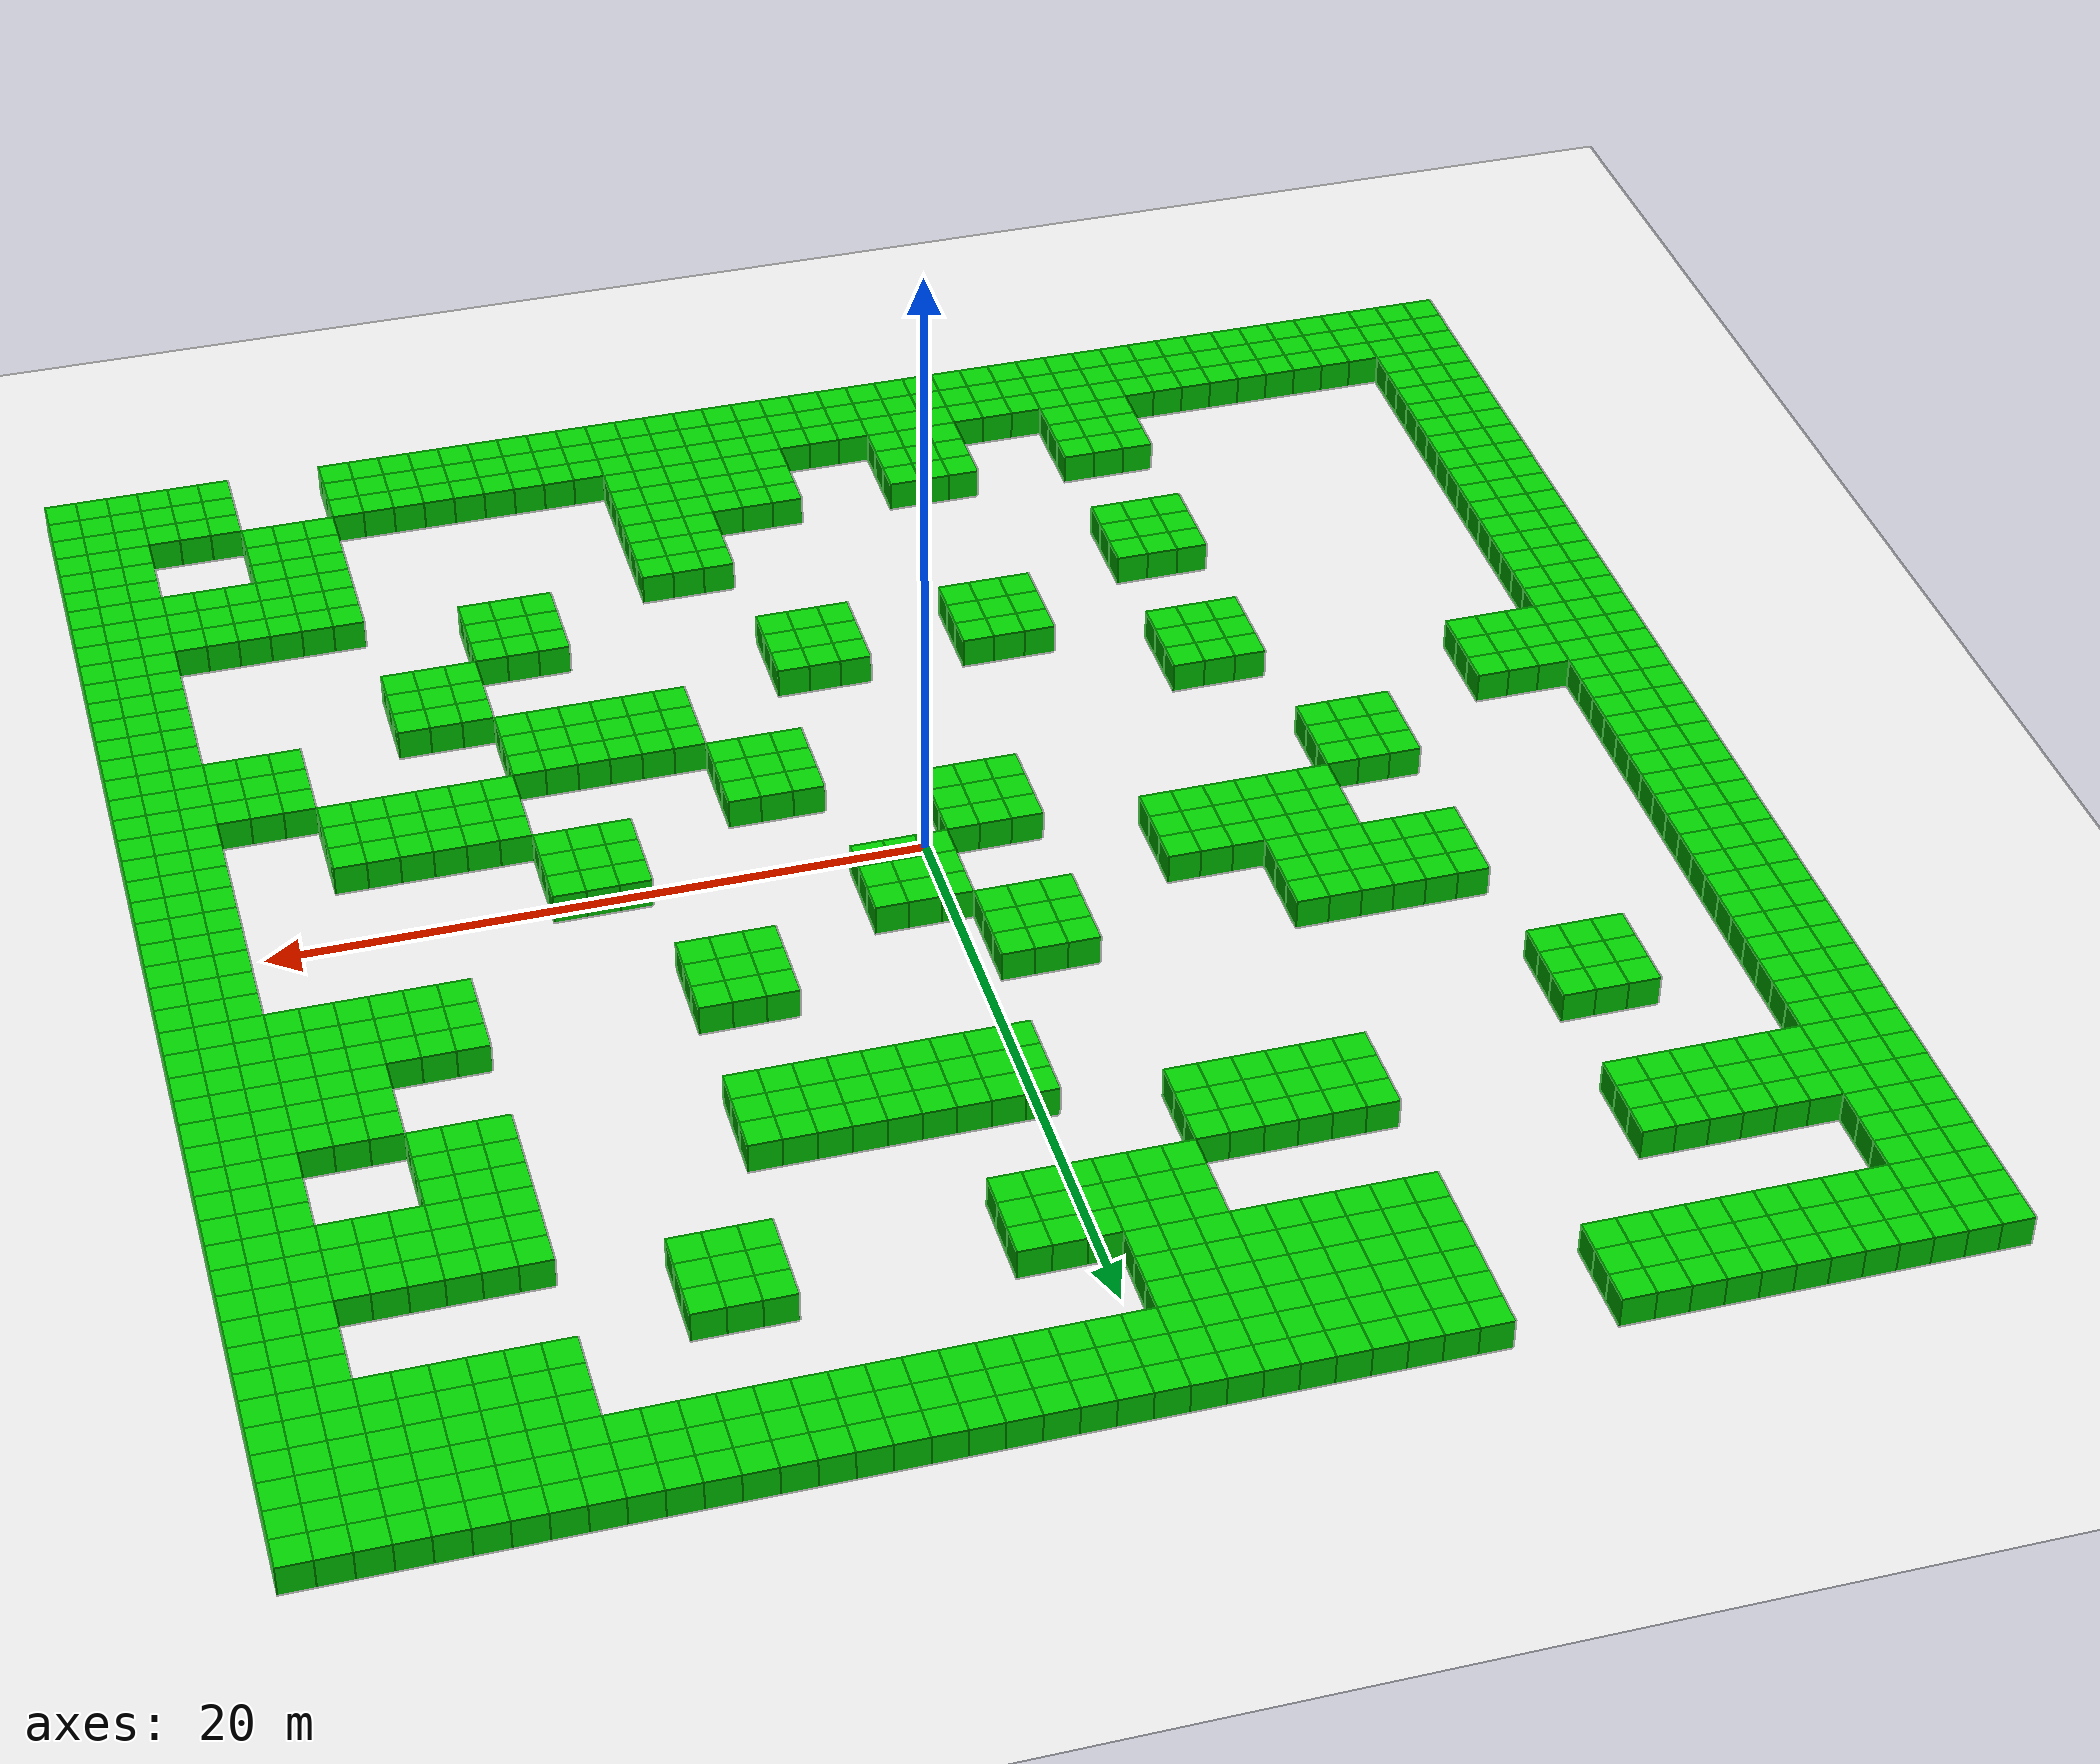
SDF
<?xml version="1.0" ?>
<sdf version="1.6">
  <world name="generated_maze">
    <light type="directional" name="sun">
      <cast_shadows>true</cast_shadows>
      <pose>0 0 10 0 0 0</pose>
      <diffuse>0.8 0.8 0.8 1</diffuse>
      <specular>0.2 0.2 0.2 1</specular>
      <attenuation>
        <range>1000</range>
        <constant>0.9</constant>
        <linear>0.01</linear>
        <quadratic>0.001</quadratic>
      </attenuation>
      <direction>-0.5 0.1 -0.9</direction>
    </light>

    <!-- Chão claro -->
    <model name="ground_plane">
      <static>true</static>
      <link name="link">
        <collision name="collision">
          <geometry><plane><normal>0 0 1</normal><size>100 100</size></plane></geometry>
        </collision>
        <visual name="visual">
          <geometry><plane><normal>0 0 1</normal><size>100 100</size></plane></geometry>
          <material>
            <ambient>0.9 0.9 0.9 1</ambient>
            <diffuse>0.9 0.9 0.9 1</diffuse>
            <specular>0.3 0.3 0.3 1</specular>
          </material>
        </visual>
      </link>
    </model>

    <model name="wall_0_0">
      <static>true</static>
      <pose>-24 24 0.5 0 0 0</pose>
      <link name="link">
        <collision name="collision">
          <geometry><box><size>1 1 1</size></box></geometry>
        </collision>
        <visual name="visual">
          <geometry><box><size>1 1 1</size></box></geometry>
          <material>
            <ambient>0.0 0.8 0.0 1</ambient>
            <diffuse>0.0 0.8 0.0 1</diffuse>
            <specular>0.1 0.1 0.1 1</specular>
          </material>
        </visual>
      </link>
    </model>

    <model name="wall_0_1">
      <static>true</static>
      <pose>-23 24 0.5 0 0 0</pose>
      <link name="link">
        <collision name="collision">
          <geometry><box><size>1 1 1</size></box></geometry>
        </collision>
        <visual name="visual">
          <geometry><box><size>1 1 1</size></box></geometry>
          <material>
            <ambient>0.0 0.8 0.0 1</ambient>
            <diffuse>0.0 0.8 0.0 1</diffuse>
            <specular>0.1 0.1 0.1 1</specular>
          </material>
        </visual>
      </link>
    </model>

    <model name="wall_0_2">
      <static>true</static>
      <pose>-22 24 0.5 0 0 0</pose>
      <link name="link">
        <collision name="collision">
          <geometry><box><size>1 1 1</size></box></geometry>
        </collision>
        <visual name="visual">
          <geometry><box><size>1 1 1</size></box></geometry>
          <material>
            <ambient>0.0 0.8 0.0 1</ambient>
            <diffuse>0.0 0.8 0.0 1</diffuse>
            <specular>0.1 0.1 0.1 1</specular>
          </material>
        </visual>
      </link>
    </model>

    <model name="wall_0_3">
      <static>true</static>
      <pose>-21 24 0.5 0 0 0</pose>
      <link name="link">
        <collision name="collision">
          <geometry><box><size>1 1 1</size></box></geometry>
        </collision>
        <visual name="visual">
          <geometry><box><size>1 1 1</size></box></geometry>
          <material>
            <ambient>0.0 0.8 0.0 1</ambient>
            <diffuse>0.0 0.8 0.0 1</diffuse>
            <specular>0.1 0.1 0.1 1</specular>
          </material>
        </visual>
      </link>
    </model>

    <model name="wall_0_4">
      <static>true</static>
      <pose>-20 24 0.5 0 0 0</pose>
      <link name="link">
        <collision name="collision">
          <geometry><box><size>1 1 1</size></box></geometry>
        </collision>
        <visual name="visual">
          <geometry><box><size>1 1 1</size></box></geometry>
          <material>
            <ambient>0.0 0.8 0.0 1</ambient>
            <diffuse>0.0 0.8 0.0 1</diffuse>
            <specular>0.1 0.1 0.1 1</specular>
          </material>
        </visual>
      </link>
    </model>

    <model name="wall_0_5">
      <static>true</static>
      <pose>-19 24 0.5 0 0 0</pose>
      <link name="link">
        <collision name="collision">
          <geometry><box><size>1 1 1</size></box></geometry>
        </collision>
        <visual name="visual">
          <geometry><box><size>1 1 1</size></box></geometry>
          <material>
            <ambient>0.0 0.8 0.0 1</ambient>
            <diffuse>0.0 0.8 0.0 1</diffuse>
            <specular>0.1 0.1 0.1 1</specular>
          </material>
        </visual>
      </link>
    </model>

    <model name="wall_0_6">
      <static>true</static>
      <pose>-18 24 0.5 0 0 0</pose>
      <link name="link">
        <collision name="collision">
          <geometry><box><size>1 1 1</size></box></geometry>
        </collision>
        <visual name="visual">
          <geometry><box><size>1 1 1</size></box></geometry>
          <material>
            <ambient>0.0 0.8 0.0 1</ambient>
            <diffuse>0.0 0.8 0.0 1</diffuse>
            <specular>0.1 0.1 0.1 1</specular>
          </material>
        </visual>
      </link>
    </model>

    <model name="wall_0_7">
      <static>true</static>
      <pose>-17 24 0.5 0 0 0</pose>
      <link name="link">
        <collision name="collision">
          <geometry><box><size>1 1 1</size></box></geometry>
        </collision>
        <visual name="visual">
          <geometry><box><size>1 1 1</size></box></geometry>
          <material>
            <ambient>0.0 0.8 0.0 1</ambient>
            <diffuse>0.0 0.8 0.0 1</diffuse>
            <specular>0.1 0.1 0.1 1</specular>
          </material>
        </visual>
      </link>
    </model>

    <model name="wall_0_8">
      <static>true</static>
      <pose>-16 24 0.5 0 0 0</pose>
      <link name="link">
        <collision name="collision">
          <geometry><box><size>1 1 1</size></box></geometry>
        </collision>
        <visual name="visual">
          <geometry><box><size>1 1 1</size></box></geometry>
          <material>
            <ambient>0.0 0.8 0.0 1</ambient>
            <diffuse>0.0 0.8 0.0 1</diffuse>
            <specular>0.1 0.1 0.1 1</specular>
          </material>
        </visual>
      </link>
    </model>

    <model name="wall_0_9">
      <static>true</static>
      <pose>-15 24 0.5 0 0 0</pose>
      <link name="link">
        <collision name="collision">
          <geometry><box><size>1 1 1</size></box></geometry>
        </collision>
        <visual name="visual">
          <geometry><box><size>1 1 1</size></box></geometry>
          <material>
            <ambient>0.0 0.8 0.0 1</ambient>
            <diffuse>0.0 0.8 0.0 1</diffuse>
            <specular>0.1 0.1 0.1 1</specular>
          </material>
        </visual>
      </link>
    </model>

    <model name="wall_0_10">
      <static>true</static>
      <pose>-14 24 0.5 0 0 0</pose>
      <link name="link">
        <collision name="collision">
          <geometry><box><size>1 1 1</size></box></geometry>
        </collision>
        <visual name="visual">
          <geometry><box><size>1 1 1</size></box></geometry>
          <material>
            <ambient>0.0 0.8 0.0 1</ambient>
            <diffuse>0.0 0.8 0.0 1</diffuse>
            <specular>0.1 0.1 0.1 1</specular>
          </material>
        </visual>
      </link>
    </model>

    <model name="wall_0_11">
      <static>true</static>
      <pose>-13 24 0.5 0 0 0</pose>
      <link name="link">
        <collision name="collision">
          <geometry><box><size>1 1 1</size></box></geometry>
        </collision>
        <visual name="visual">
          <geometry><box><size>1 1 1</size></box></geometry>
          <material>
            <ambient>0.0 0.8 0.0 1</ambient>
            <diffuse>0.0 0.8 0.0 1</diffuse>
            <specular>0.1 0.1 0.1 1</specular>
          </material>
        </visual>
      </link>
    </model>

    <model name="wall_0_15">
      <static>true</static>
      <pose>-9 24 0.5 0 0 0</pose>
      <link name="link">
        <collision name="collision">
          <geometry><box><size>1 1 1</size></box></geometry>
        </collision>
        <visual name="visual">
          <geometry><box><size>1 1 1</size></box></geometry>
          <material>
            <ambient>0.0 0.8 0.0 1</ambient>
            <diffuse>0.0 0.8 0.0 1</diffuse>
            <specular>0.1 0.1 0.1 1</specular>
          </material>
        </visual>
      </link>
    </model>

    <model name="wall_0_16">
      <static>true</static>
      <pose>-8 24 0.5 0 0 0</pose>
      <link name="link">
        <collision name="collision">
          <geometry><box><size>1 1 1</size></box></geometry>
        </collision>
        <visual name="visual">
          <geometry><box><size>1 1 1</size></box></geometry>
          <material>
            <ambient>0.0 0.8 0.0 1</ambient>
            <diffuse>0.0 0.8 0.0 1</diffuse>
            <specular>0.1 0.1 0.1 1</specular>
          </material>
        </visual>
      </link>
    </model>

    <model name="wall_0_17">
      <static>true</static>
      <pose>-7 24 0.5 0 0 0</pose>
      <link name="link">
        <collision name="collision">
          <geometry><box><size>1 1 1</size></box></geometry>
        </collision>
        <visual name="visual">
          <geometry><box><size>1 1 1</size></box></geometry>
          <material>
            <ambient>0.0 0.8 0.0 1</ambient>
            <diffuse>0.0 0.8 0.0 1</diffuse>
            <specular>0.1 0.1 0.1 1</specular>
          </material>
        </visual>
      </link>
    </model>

    <model name="wall_0_18">
      <static>true</static>
      <pose>-6 24 0.5 0 0 0</pose>
      <link name="link">
        <collision name="collision">
          <geometry><box><size>1 1 1</size></box></geometry>
        </collision>
        <visual name="visual">
          <geometry><box><size>1 1 1</size></box></geometry>
          <material>
            <ambient>0.0 0.8 0.0 1</ambient>
            <diffuse>0.0 0.8 0.0 1</diffuse>
            <specular>0.1 0.1 0.1 1</specular>
          </material>
        </visual>
      </link>
    </model>

    <model name="wall_0_19">
      <static>true</static>
      <pose>-5 24 0.5 0 0 0</pose>
      <link name="link">
        <collision name="collision">
          <geometry><box><size>1 1 1</size></box></geometry>
        </collision>
        <visual name="visual">
          <geometry><box><size>1 1 1</size></box></geometry>
          <material>
            <ambient>0.0 0.8 0.0 1</ambient>
            <diffuse>0.0 0.8 0.0 1</diffuse>
            <specular>0.1 0.1 0.1 1</specular>
          </material>
        </visual>
      </link>
    </model>

    <model name="wall_0_20">
      <static>true</static>
      <pose>-4 24 0.5 0 0 0</pose>
      <link name="link">
        <collision name="collision">
          <geometry><box><size>1 1 1</size></box></geometry>
        </collision>
        <visual name="visual">
          <geometry><box><size>1 1 1</size></box></geometry>
          <material>
            <ambient>0.0 0.8 0.0 1</ambient>
            <diffuse>0.0 0.8 0.0 1</diffuse>
            <specular>0.1 0.1 0.1 1</specular>
          </material>
        </visual>
      </link>
    </model>

    <model name="wall_0_21">
      <static>true</static>
      <pose>-3 24 0.5 0 0 0</pose>
      <link name="link">
        <collision name="collision">
          <geometry><box><size>1 1 1</size></box></geometry>
        </collision>
        <visual name="visual">
          <geometry><box><size>1 1 1</size></box></geometry>
          <material>
            <ambient>0.0 0.8 0.0 1</ambient>
            <diffuse>0.0 0.8 0.0 1</diffuse>
            <specular>0.1 0.1 0.1 1</specular>
          </material>
        </visual>
      </link>
    </model>

    <model name="wall_0_22">
      <static>true</static>
      <pose>-2 24 0.5 0 0 0</pose>
      <link name="link">
        <collision name="collision">
          <geometry><box><size>1 1 1</size></box></geometry>
        </collision>
        <visual name="visual">
          <geometry><box><size>1 1 1</size></box></geometry>
          <material>
            <ambient>0.0 0.8 0.0 1</ambient>
            <diffuse>0.0 0.8 0.0 1</diffuse>
            <specular>0.1 0.1 0.1 1</specular>
          </material>
        </visual>
      </link>
    </model>

    <model name="wall_0_23">
      <static>true</static>
      <pose>-1 24 0.5 0 0 0</pose>
      <link name="link">
        <collision name="collision">
          <geometry><box><size>1 1 1</size></box></geometry>
        </collision>
        <visual name="visual">
          <geometry><box><size>1 1 1</size></box></geometry>
          <material>
            <ambient>0.0 0.8 0.0 1</ambient>
            <diffuse>0.0 0.8 0.0 1</diffuse>
            <specular>0.1 0.1 0.1 1</specular>
          </material>
        </visual>
      </link>
    </model>

    <model name="wall_0_24">
      <static>true</static>
      <pose>0 24 0.5 0 0 0</pose>
      <link name="link">
        <collision name="collision">
          <geometry><box><size>1 1 1</size></box></geometry>
        </collision>
        <visual name="visual">
          <geometry><box><size>1 1 1</size></box></geometry>
          <material>
            <ambient>0.0 0.8 0.0 1</ambient>
            <diffuse>0.0 0.8 0.0 1</diffuse>
            <specular>0.1 0.1 0.1 1</specular>
          </material>
        </visual>
      </link>
    </model>

    <model name="wall_0_25">
      <static>true</static>
      <pose>1 24 0.5 0 0 0</pose>
      <link name="link">
        <collision name="collision">
          <geometry><box><size>1 1 1</size></box></geometry>
        </collision>
        <visual name="visual">
          <geometry><box><size>1 1 1</size></box></geometry>
          <material>
            <ambient>0.0 0.8 0.0 1</ambient>
            <diffuse>0.0 0.8 0.0 1</diffuse>
            <specular>0.1 0.1 0.1 1</specular>
          </material>
        </visual>
      </link>
    </model>

    <model name="wall_0_26">
      <static>true</static>
      <pose>2 24 0.5 0 0 0</pose>
      <link name="link">
        <collision name="collision">
          <geometry><box><size>1 1 1</size></box></geometry>
        </collision>
        <visual name="visual">
          <geometry><box><size>1 1 1</size></box></geometry>
          <material>
            <ambient>0.0 0.8 0.0 1</ambient>
            <diffuse>0.0 0.8 0.0 1</diffuse>
            <specular>0.1 0.1 0.1 1</specular>
          </material>
        </visual>
      </link>
    </model>

    <model name="wall_0_27">
      <static>true</static>
      <pose>3 24 0.5 0 0 0</pose>
      <link name="link">
        <collision name="collision">
          <geometry><box><size>1 1 1</size></box></geometry>
        </collision>
        <visual name="visual">
          <geometry><box><size>1 1 1</size></box></geometry>
          <material>
            <ambient>0.0 0.8 0.0 1</ambient>
            <diffuse>0.0 0.8 0.0 1</diffuse>
            <specular>0.1 0.1 0.1 1</specular>
          </material>
        </visual>
      </link>
    </model>

    <model name="wall_0_28">
      <static>true</static>
      <pose>4 24 0.5 0 0 0</pose>
      <link name="link">
        <collision name="collision">
          <geometry><box><size>1 1 1</size></box></geometry>
        </collision>
        <visual name="visual">
          <geometry><box><size>1 1 1</size></box></geometry>
          <material>
            <ambient>0.0 0.8 0.0 1</ambient>
            <diffuse>0.0 0.8 0.0 1</diffuse>
            <specular>0.1 0.1 0.1 1</specular>
          </material>
        </visual>
      </link>
    </model>

    <model name="wall_0_29">
      <static>true</static>
      <pose>5 24 0.5 0 0 0</pose>
      <link name="link">
        <collision name="collision">
          <geometry><box><size>1 1 1</size></box></geometry>
        </collision>
        <visual name="visual">
          <geometry><box><size>1 1 1</size></box></geometry>
          <material>
            <ambient>0.0 0.8 0.0 1</ambient>
            <diffuse>0.0 0.8 0.0 1</diffuse>
            <specular>0.1 0.1 0.1 1</specular>
          </material>
        </visual>
      </link>
    </model>

    <model name="wall_0_30">
      <static>true</static>
      <pose>6 24 0.5 0 0 0</pose>
      <link name="link">
        <collision name="collision">
          <geometry><box><size>1 1 1</size></box></geometry>
        </collision>
        <visual name="visual">
          <geometry><box><size>1 1 1</size></box></geometry>
          <material>
            <ambient>0.0 0.8 0.0 1</ambient>
            <diffuse>0.0 0.8 0.0 1</diffuse>
            <specular>0.1 0.1 0.1 1</specular>
          </material>
        </visual>
      </link>
    </model>

    <model name="wall_0_31">
      <static>true</static>
      <pose>7 24 0.5 0 0 0</pose>
      <link name="link">
        <collision name="collision">
          <geometry><box><size>1 1 1</size></box></geometry>
        </collision>
        <visual name="visual">
          <geometry><box><size>1 1 1</size></box></geometry>
          <material>
            <ambient>0.0 0.8 0.0 1</ambient>
            <diffuse>0.0 0.8 0.0 1</diffuse>
            <specular>0.1 0.1 0.1 1</specular>
          </material>
        </visual>
      </link>
    </model>

    <model name="wall_0_32">
      <static>true</static>
      <pose>8 24 0.5 0 0 0</pose>
      <link name="link">
        <collision name="collision">
          <geometry><box><size>1 1 1</size></box></geometry>
        </collision>
        <visual name="visual">
          <geometry><box><size>1 1 1</size></box></geometry>
          <material>
            <ambient>0.0 0.8 0.0 1</ambient>
            <diffuse>0.0 0.8 0.0 1</diffuse>
            <specular>0.1 0.1 0.1 1</specular>
          </material>
        </visual>
      </link>
    </model>

    <model name="wall_0_33">
      <static>true</static>
      <pose>9 24 0.5 0 0 0</pose>
      <link name="link">
        <collision name="collision">
          <geometry><box><size>1 1 1</size></box></geometry>
        </collision>
        <visual name="visual">
          <geometry><box><size>1 1 1</size></box></geometry>
          <material>
            <ambient>0.0 0.8 0.0 1</ambient>
            <diffuse>0.0 0.8 0.0 1</diffuse>
            <specular>0.1 0.1 0.1 1</specular>
          </material>
        </visual>
      </link>
    </model>

    <model name="wall_0_34">
      <static>true</static>
      <pose>10 24 0.5 0 0 0</pose>
      <link name="link">
        <collision name="collision">
          <geometry><box><size>1 1 1</size></box></geometry>
        </collision>
        <visual name="visual">
          <geometry><box><size>1 1 1</size></box></geometry>
          <material>
            <ambient>0.0 0.8 0.0 1</ambient>
            <diffuse>0.0 0.8 0.0 1</diffuse>
            <specular>0.1 0.1 0.1 1</specular>
          </material>
        </visual>
      </link>
    </model>

    <model name="wall_0_35">
      <static>true</static>
      <pose>11 24 0.5 0 0 0</pose>
      <link name="link">
        <collision name="collision">
          <geometry><box><size>1 1 1</size></box></geometry>
        </collision>
        <visual name="visual">
          <geometry><box><size>1 1 1</size></box></geometry>
          <material>
            <ambient>0.0 0.8 0.0 1</ambient>
            <diffuse>0.0 0.8 0.0 1</diffuse>
            <specular>0.1 0.1 0.1 1</specular>
          </material>
        </visual>
      </link>
    </model>

    <model name="wall_0_36">
      <static>true</static>
      <pose>12 24 0.5 0 0 0</pose>
      <link name="link">
        <collision name="collision">
          <geometry><box><size>1 1 1</size></box></geometry>
        </collision>
        <visual name="visual">
          <geometry><box><size>1 1 1</size></box></geometry>
          <material>
            <ambient>0.0 0.8 0.0 1</ambient>
            <diffuse>0.0 0.8 0.0 1</diffuse>
            <specular>0.1 0.1 0.1 1</specular>
          </material>
        </visual>
      </link>
    </model>

    <model name="wall_0_37">
      <static>true</static>
      <pose>13 24 0.5 0 0 0</pose>
      <link name="link">
        <collision name="collision">
          <geometry><box><size>1 1 1</size></box></geometry>
        </collision>
        <visual name="visual">
          <geometry><box><size>1 1 1</size></box></geometry>
          <material>
            <ambient>0.0 0.8 0.0 1</ambient>
            <diffuse>0.0 0.8 0.0 1</diffuse>
            <specular>0.1 0.1 0.1 1</specular>
          </material>
        </visual>
      </link>
    </model>

    <model name="wall_0_38">
      <static>true</static>
      <pose>14 24 0.5 0 0 0</pose>
      <link name="link">
        <collision name="collision">
          <geometry><box><size>1 1 1</size></box></geometry>
        </collision>
        <visual name="visual">
          <geometry><box><size>1 1 1</size></box></geometry>
          <material>
            <ambient>0.0 0.8 0.0 1</ambient>
            <diffuse>0.0 0.8 0.0 1</diffuse>
            <specular>0.1 0.1 0.1 1</specular>
          </material>
        </visual>
      </link>
    </model>

    <model name="wall_0_39">
      <static>true</static>
      <pose>15 24 0.5 0 0 0</pose>
      <link name="link">
        <collision name="collision">
          <geometry><box><size>1 1 1</size></box></geometry>
        </collision>
        <visual name="visual">
          <geometry><box><size>1 1 1</size></box></geometry>
          <material>
            <ambient>0.0 0.8 0.0 1</ambient>
            <diffuse>0.0 0.8 0.0 1</diffuse>
            <specular>0.1 0.1 0.1 1</specular>
          </material>
        </visual>
      </link>
    </model>

    <model name="wall_0_40">
      <static>true</static>
      <pose>16 24 0.5 0 0 0</pose>
      <link name="link">
        <collision name="collision">
          <geometry><box><size>1 1 1</size></box></geometry>
        </collision>
        <visual name="visual">
          <geometry><box><size>1 1 1</size></box></geometry>
          <material>
            <ambient>0.0 0.8 0.0 1</ambient>
            <diffuse>0.0 0.8 0.0 1</diffuse>
            <specular>0.1 0.1 0.1 1</specular>
          </material>
        </visual>
      </link>
    </model>

    <model name="wall_0_41">
      <static>true</static>
      <pose>17 24 0.5 0 0 0</pose>
      <link name="link">
        <collision name="collision">
          <geometry><box><size>1 1 1</size></box></geometry>
        </collision>
        <visual name="visual">
          <geometry><box><size>1 1 1</size></box></geometry>
          <material>
            <ambient>0.0 0.8 0.0 1</ambient>
            <diffuse>0.0 0.8 0.0 1</diffuse>
            <specular>0.1 0.1 0.1 1</specular>
          </material>
        </visual>
      </link>
    </model>

    <model name="wall_0_42">
      <static>true</static>
      <pose>18 24 0.5 0 0 0</pose>
      <link name="link">
        <collision name="collision">
          <geometry><box><size>1 1 1</size></box></geometry>
        </collision>
        <visual name="visual">
          <geometry><box><size>1 1 1</size></box></geometry>
          <material>
            <ambient>0.0 0.8 0.0 1</ambient>
            <diffuse>0.0 0.8 0.0 1</diffuse>
            <specular>0.1 0.1 0.1 1</specular>
          </material>
        </visual>
      </link>
    </model>

    <model name="wall_0_43">
      <static>true</static>
      <pose>19 24 0.5 0 0 0</pose>
      <link name="link">
        <collision name="collision">
          <geometry><box><size>1 1 1</size></box></geometry>
        </collision>
        <visual name="visual">
          <geometry><box><size>1 1 1</size></box></geometry>
          <material>
            <ambient>0.0 0.8 0.0 1</ambient>
            <diffuse>0.0 0.8 0.0 1</diffuse>
            <specular>0.1 0.1 0.1 1</specular>
          </material>
        </visual>
      </link>
    </model>

    <model name="wall_0_44">
      <static>true</static>
      <pose>20 24 0.5 0 0 0</pose>
      <link name="link">
        <collision name="collision">
          <geometry><box><size>1 1 1</size></box></geometry>
        </collision>
        <visual name="visual">
          <geometry><box><size>1 1 1</size></box></geometry>
          <material>
            <ambient>0.0 0.8 0.0 1</ambient>
            <diffuse>0.0 0.8 0.0 1</diffuse>
            <specular>0.1 0.1 0.1 1</specular>
          </material>
        </visual>
      </link>
    </model>

    <model name="wall_0_45">
      <static>true</static>
      <pose>21 24 0.5 0 0 0</pose>
      <link name="link">
        <collision name="collision">
          <geometry><box><size>1 1 1</size></box></geometry>
        </collision>
        <visual name="visual">
          <geometry><box><size>1 1 1</size></box></geometry>
          <material>
            <ambient>0.0 0.8 0.0 1</ambient>
            <diffuse>0.0 0.8 0.0 1</diffuse>
            <specular>0.1 0.1 0.1 1</specular>
          </material>
        </visual>
      </link>
    </model>

    <model name="wall_0_46">
      <static>true</static>
      <pose>22 24 0.5 0 0 0</pose>
      <link name="link">
        <collision name="collision">
          <geometry><box><size>1 1 1</size></box></geometry>
        </collision>
        <visual name="visual">
          <geometry><box><size>1 1 1</size></box></geometry>
          <material>
            <ambient>0.0 0.8 0.0 1</ambient>
            <diffuse>0.0 0.8 0.0 1</diffuse>
            <specular>0.1 0.1 0.1 1</specular>
          </material>
        </visual>
      </link>
    </model>

    <model name="wall_0_47">
      <static>true</static>
      <pose>23 24 0.5 0 0 0</pose>
      <link name="link">
        <collision name="collision">
          <geometry><box><size>1 1 1</size></box></geometry>
        </collision>
        <visual name="visual">
          <geometry><box><size>1 1 1</size></box></geometry>
          <material>
            <ambient>0.0 0.8 0.0 1</ambient>
            <diffuse>0.0 0.8 0.0 1</diffuse>
            <specular>0.1 0.1 0.1 1</specular>
          </material>
        </visual>
      </link>
    </model>

    <model name="wall_1_0">
      <static>true</static>
      <pose>-24 23 0.5 0 0 0</pose>
      <link name="link">
        <collision name="collision">
          <geometry><box><size>1 1 1</size></box></geometry>
        </collision>
        <visual name="visual">
          <geometry><box><size>1 1 1</size></box></geometry>
          <material>
            <ambient>0.0 0.8 0.0 1</ambient>
            <diffuse>0.0 0.8 0.0 1</diffuse>
            <specular>0.1 0.1 0.1 1</specular>
          </material>
        </visual>
      </link>
    </model>

    <model name="wall_1_1">
      <static>true</static>
      <pose>-23 23 0.5 0 0 0</pose>
      <link name="link">
        <collision name="collision">
          <geometry><box><size>1 1 1</size></box></geometry>
        </collision>
        <visual name="visual">
          <geometry><box><size>1 1 1</size></box></geometry>
          <material>
            <ambient>0.0 0.8 0.0 1</ambient>
            <diffuse>0.0 0.8 0.0 1</diffuse>
            <specular>0.1 0.1 0.1 1</specular>
          </material>
        </visual>
      </link>
    </model>

    <model name="wall_1_2">
      <static>true</static>
      <pose>-22 23 0.5 0 0 0</pose>
      <link name="link">
        <collision name="collision">
          <geometry><box><size>1 1 1</size></box></geometry>
        </collision>
        <visual name="visual">
          <geometry><box><size>1 1 1</size></box></geometry>
          <material>
            <ambient>0.0 0.8 0.0 1</ambient>
            <diffuse>0.0 0.8 0.0 1</diffuse>
            <specular>0.1 0.1 0.1 1</specular>
          </material>
        </visual>
      </link>
    </model>

    <model name="wall_1_3">
      <static>true</static>
      <pose>-21 23 0.5 0 0 0</pose>
      <link name="link">
        <collision name="collision">
          <geometry><box><size>1 1 1</size></box></geometry>
        </collision>
        <visual name="visual">
          <geometry><box><size>1 1 1</size></box></geometry>
          <material>
            <ambient>0.0 0.8 0.0 1</ambient>
            <diffuse>0.0 0.8 0.0 1</diffuse>
            <specular>0.1 0.1 0.1 1</specular>
          </material>
        </visual>
      </link>
    </model>

    <model name="wall_1_4">
      <static>true</static>
      <pose>-20 23 0.5 0 0 0</pose>
      <link name="link">
        <collision name="collision">
          <geometry><box><size>1 1 1</size></box></geometry>
        </collision>
        <visual name="visual">
          <geometry><box><size>1 1 1</size></box></geometry>
          <material>
            <ambient>0.0 0.8 0.0 1</ambient>
            <diffuse>0.0 0.8 0.0 1</diffuse>
            <specular>0.1 0.1 0.1 1</specular>
          </material>
        </visual>
      </link>
    </model>

    <model name="wall_1_5">
      <static>true</static>
      <pose>-19 23 0.5 0 0 0</pose>
      <link name="link">
        <collision name="collision">
          <geometry><box><size>1 1 1</size></box></geometry>
        </collision>
        <visual name="visual">
          <geometry><box><size>1 1 1</size></box></geometry>
          <material>
            <ambient>0.0 0.8 0.0 1</ambient>
            <diffuse>0.0 0.8 0.0 1</diffuse>
            <specular>0.1 0.1 0.1 1</specular>
          </material>
        </visual>
      </link>
    </model>

    <model name="wall_1_6">
      <static>true</static>
      <pose>-18 23 0.5 0 0 0</pose>
      <link name="link">
        <collision name="collision">
          <geometry><box><size>1 1 1</size></box></geometry>
        </collision>
        <visual name="visual">
          <geometry><box><size>1 1 1</size></box></geometry>
          <material>
            <ambient>0.0 0.8 0.0 1</ambient>
            <diffuse>0.0 0.8 0.0 1</diffuse>
            <specular>0.1 0.1 0.1 1</specular>
          </material>
        </visual>
      </link>
    </model>

    <model name="wall_1_7">
      <static>true</static>
      <pose>-17 23 0.5 0 0 0</pose>
      <link name="link">
        <collision name="collision">
          <geometry><box><size>1 1 1</size></box></geometry>
        </collision>
        <visual name="visual">
          <geometry><box><size>1 1 1</size></box></geometry>
          <material>
            <ambient>0.0 0.8 0.0 1</ambient>
            <diffuse>0.0 0.8 0.0 1</diffuse>
            <specular>0.1 0.1 0.1 1</specular>
          </material>
        </visual>
      </link>
    </model>

    <model name="wall_1_8">
      <static>true</static>
      <pose>-16 23 0.5 0 0 0</pose>
      <link name="link">
        <collision name="collision">
          <geometry><box><size>1 1 1</size></box></geometry>
        </collision>
        <visual name="visual">
          <geometry><box><size>1 1 1</size></box></geometry>
          <material>
            <ambient>0.0 0.8 0.0 1</ambient>
            <diffuse>0.0 0.8 0.0 1</diffuse>
            <specular>0.1 0.1 0.1 1</specular>
          </material>
        </visual>
      </link>
    </model>

    <model name="wall_1_9">
      <static>true</static>
      <pose>-15 23 0.5 0 0 0</pose>
      <link name="link">
        <collision name="collision">
          <geometry><box><size>1 1 1</size></box></geometry>
        </collision>
        <visual name="visual">
          <geometry><box><size>1 1 1</size></box></geometry>
          <material>
            <ambient>0.0 0.8 0.0 1</ambient>
            <diffuse>0.0 0.8 0.0 1</diffuse>
            <specular>0.1 0.1 0.1 1</specular>
          </material>
        </visual>
      </link>
    </model>

    <model name="wall_1_10">
      <static>true</static>
      <pose>-14 23 0.5 0 0 0</pose>
      <link name="link">
        <collision name="collision">
          <geometry><box><size>1 1 1</size></box></geometry>
        </collision>
        <visual name="visual">
          <geometry><box><size>1 1 1</size></box></geometry>
          <material>
            <ambient>0.0 0.8 0.0 1</ambient>
            <diffuse>0.0 0.8 0.0 1</diffuse>
            <specular>0.1 0.1 0.1 1</specular>
          </material>
        </visual>
      </link>
    </model>

    <model name="wall_1_11">
      <static>true</static>
      <pose>-13 23 0.5 0 0 0</pose>
      <link name="link">
        <collision name="collision">
          <geometry><box><size>1 1 1</size></box></geometry>
        </collision>
        <visual name="visual">
          <geometry><box><size>1 1 1</size></box></geometry>
          <material>
            <ambient>0.0 0.8 0.0 1</ambient>
            <diffuse>0.0 0.8 0.0 1</diffuse>
            <specular>0.1 0.1 0.1 1</specular>
          </material>
        </visual>
      </link>
    </model>

    <model name="wall_1_15">
      <static>true</static>
      <pose>-9 23 0.5 0 0 0</pose>
      <link name="link">
        <collision name="collision">
          <geometry><box><size>1 1 1</size></box></geometry>
        </collision>
        <visual name="visual">
          <geometry><box><size>1 1 1</size></box></geometry>
          <material>
            <ambient>0.0 0.8 0.0 1</ambient>
            <diffuse>0.0 0.8 0.0 1</diffuse>
            <specular>0.1 0.1 0.1 1</specular>
          </material>
        </visual>
      </link>
    </model>

    <model name="wall_1_16">
      <static>true</static>
      <pose>-8 23 0.5 0 0 0</pose>
      <link name="link">
        <collision name="collision">
          <geometry><box><size>1 1 1</size></box></geometry>
        </collision>
        <visual name="visual">
          <geometry><box><size>1 1 1</size></box></geometry>
          <material>
            <ambient>0.0 0.8 0.0 1</ambient>
            <diffuse>0.0 0.8 0.0 1</diffuse>
            <specular>0.1 0.1 0.1 1</specular>
          </material>
        </visual>
      </link>
    </model>

    <model name="wall_1_17">
      <static>true</static>
      <pose>-7 23 0.5 0 0 0</pose>
      <link name="link">
        <collision name="collision">
          <geometry><box><size>1 1 1</size></box></geometry>
        </collision>
        <visual name="visual">
          <geometry><box><size>1 1 1</size></box></geometry>
          <material>
            <ambient>0.0 0.8 0.0 1</ambient>
            <diffuse>0.0 0.8 0.0 1</diffuse>
            <specular>0.1 0.1 0.1 1</specular>
          </material>
        </visual>
      </link>
    </model>

    <model name="wall_1_18">
      <static>true</static>
      <pose>-6 23 0.5 0 0 0</pose>
      <link name="link">
        <collision name="collision">
          <geometry><box><size>1 1 1</size></box></geometry>
        </collision>
        <visual name="visual">
          <geometry><box><size>1 1 1</size></box></geometry>
          <material>
            <ambient>0.0 0.8 0.0 1</ambient>
            <diffuse>0.0 0.8 0.0 1</diffuse>
            <specular>0.1 0.1 0.1 1</specular>
          </material>
        </visual>
      </link>
    </model>

    <model name="wall_1_19">
      <static>true</static>
      <pose>-5 23 0.5 0 0 0</pose>
      <link name="link">
        <collision name="collision">
          <geometry><box><size>1 1 1</size></box></geometry>
        </collision>
        <visual name="visual">
          <geometry><box><size>1 1 1</size></box></geometry>
          <material>
            <ambient>0.0 0.8 0.0 1</ambient>
            <diffuse>0.0 0.8 0.0 1</diffuse>
            <specular>0.1 0.1 0.1 1</specular>
          </material>
        </visual>
      </link>
    </model>

    <model name="wall_1_20">
      <static>true</static>
      <pose>-4 23 0.5 0 0 0</pose>
      <link name="link">
        <collision name="collision">
          <geometry><box><size>1 1 1</size></box></geometry>
        </collision>
        <visual name="visual">
          <geometry><box><size>1 1 1</size></box></geometry>
          <material>
            <ambient>0.0 0.8 0.0 1</ambient>
            <diffuse>0.0 0.8 0.0 1</diffuse>
            <specular>0.1 0.1 0.1 1</specular>
          </material>
        </visual>
      </link>
    </model>

    <model name="wall_1_21">
      <static>true</static>
      <pose>-3 23 0.5 0 0 0</pose>
      <link name="link">
        <collision name="collision">
          <geometry><box><size>1 1 1</size></box></geometry>
        </collision>
        <visual name="visual">
          <geometry><box><size>1 1 1</size></box></geometry>
          <material>
            <ambient>0.0 0.8 0.0 1</ambient>
            <diffuse>0.0 0.8 0.0 1</diffuse>
            <specular>0.1 0.1 0.1 1</specular>
          </material>
        </visual>
      </link>
    </model>

    <model name="wall_1_22">
      <static>true</static>
      <pose>-2 23 0.5 0 0 0</pose>
      <link name="link">
        <collision name="collision">
          <geometry><box><size>1 1 1</size></box></geometry>
        </collision>
        <visual name="visual">
          <geometry><box><size>1 1 1</size></box></geometry>
          <material>
            <ambient>0.0 0.8 0.0 1</ambient>
            <diffuse>0.0 0.8 0.0 1</diffuse>
            <specular>0.1 0.1 0.1 1</specular>
          </material>
        </visual>
      </link>
    </model>

    <model name="wall_1_23">
      <static>true</static>
      <pose>-1 23 0.5 0 0 0</pose>
      <link name="link">
        <collision name="collision">
          <geometry><box><size>1 1 1</size></box></geometry>
        </collision>
        <visual name="visual">
          <geometry><box><size>1 1 1</size></box></geometry>
          <material>
            <ambient>0.0 0.8 0.0 1</ambient>
            <diffuse>0.0 0.8 0.0 1</diffuse>
            <specular>0.1 0.1 0.1 1</specular>
          </material>
        </visual>
      </link>
    </model>

    <model name="wall_1_24">
      <static>true</static>
      <pose>0 23 0.5 0 0 0</pose>
      <link name="link">
        <collision name="collision">
          <geometry><box><size>1 1 1</size></box></geometry>
        </collision>
        <visual name="visual">
          <geometry><box><size>1 1 1</size></box></geometry>
          <material>
            <ambient>0.0 0.8 0.0 1</ambient>
            <diffuse>0.0 0.8 0.0 1</diffuse>
            <specular>0.1 0.1 0.1 1</specular>
          </material>
        </visual>
      </link>
    </model>

    <model name="wall_1_25">
      <static>true</static>
      <pose>1 23 0.5 0 0 0</pose>
      <link name="link">
        <collision name="collision">
          <geometry><box><size>1 1 1</size></box></geometry>
        </collision>
        <visual name="visual">
          <geometry><box><size>1 1 1</size></box></geometry>
          <material>
            <ambient>0.0 0.8 0.0 1</ambient>
            <diffuse>0.0 0.8 0.0 1</diffuse>
            <specular>0.1 0.1 0.1 1</specular>
          </material>
        </visual>
      </link>
    </model>

    <model name="wall_1_26">
      <static>true</static>
      <pose>2 23 0.5 0 0 0</pose>
      <link name="link">
        <collision name="collision">
          <geometry><box><size>1 1 1</size></box></geometry>
        </collision>
        <visual name="visual">
          <geometry><box><size>1 1 1</size></box></geometry>
          <material>
            <ambient>0.0 0.8 0.0 1</ambient>
            <diffuse>0.0 0.8 0.0 1</diffuse>
            <specular>0.1 0.1 0.1 1</specular>
          </material>
        </visual>
      </link>
    </model>

    <model name="wall_1_27">
      <static>true</static>
      <pose>3 23 0.5 0 0 0</pose>
      <link name="link">
        <collision name="collision">
          <geometry><box><size>1 1 1</size></box></geometry>
        </collision>
        <visual name="visual">
          <geometry><box><size>1 1 1</size></box></geometry>
          <material>
            <ambient>0.0 0.8 0.0 1</ambient>
            <diffuse>0.0 0.8 0.0 1</diffuse>
            <specular>0.1 0.1 0.1 1</specular>
          </material>
        </visual>
      </link>
    </model>

    <model name="wall_1_28">
      <static>true</static>
      <pose>4 23 0.5 0 0 0</pose>
      <link name="link">
        <collision name="collision">
          <geometry><box><size>1 1 1</size></box></geometry>
        </collision>
        <visual name="visual">
          <geometry><box><size>1 1 1</size></box></geometry>
          <material>
            <ambient>0.0 0.8 0.0 1</ambient>
            <diffuse>0.0 0.8 0.0 1</diffuse>
            <specular>0.1 0.1 0.1 1</specular>
          </material>
        </visual>
      </link>
    </model>

    <model name="wall_1_29">
      <static>true</static>
      <pose>5 23 0.5 0 0 0</pose>
      <link name="link">
        <collision name="collision">
          <geometry><box><size>1 1 1</size></box></geometry>
        </collision>
        <visual name="visual">
          <geometry><box><size>1 1 1</size></box></geometry>
          <material>
            <ambient>0.0 0.8 0.0 1</ambient>
            <diffuse>0.0 0.8 0.0 1</diffuse>
            <specular>0.1 0.1 0.1 1</specular>
          </material>
        </visual>
      </link>
    </model>

    <model name="wall_1_30">
      <static>true</static>
      <pose>6 23 0.5 0 0 0</pose>
      <link name="link">
        <collision name="collision">
          <geometry><box><size>1 1 1</size></box></geometry>
        </collision>
        <visual name="visual">
          <geometry><box><size>1 1 1</size></box></geometry>
          <material>
            <ambient>0.0 0.8 0.0 1</ambient>
            <diffuse>0.0 0.8 0.0 1</diffuse>
            <specular>0.1 0.1 0.1 1</specular>
          </material>
        </visual>
      </link>
    </model>

    <model name="wall_1_31">
      <static>true</static>
      <pose>7 23 0.5 0 0 0</pose>
      <link name="link">
        <collision name="collision">
          <geometry><box><size>1 1 1</size></box></geometry>
        </collision>
        <visual name="visual">
          <geometry><box><size>1 1 1</size></box></geometry>
          <material>
            <ambient>0.0 0.8 0.0 1</ambient>
            <diffuse>0.0 0.8 0.0 1</diffuse>
            <specular>0.1 0.1 0.1 1</specular>
          </material>
        </visual>
      </link>
    </model>

    <model name="wall_1_32">
      <static>true</static>
      <pose>8 23 0.5 0 0 0</pose>
      <link name="link">
        <collision name="collision">
          <geometry><box><size>1 1 1</size></box></geometry>
        </collision>
        <visual name="visual">
          <geometry><box><size>1 1 1</size></box></geometry>
          <material>
            <ambient>0.0 0.8 0.0 1</ambient>
            <diffuse>0.0 0.8 0.0 1</diffuse>
            <specular>0.1 0.1 0.1 1</specular>
          </material>
        </visual>
      </link>
    </model>

    <model name="wall_1_33">
      <static>true</static>
      <pose>9 23 0.5 0 0 0</pose>
      <link name="link">
        <collision name="collision">
          <geometry><box><size>1 1 1</size></box></geometry>
        </collision>
        <visual name="visual">
          <geometry><box><size>1 1 1</size></box></geometry>
          <material>
            <ambient>0.0 0.8 0.0 1</ambient>
            <diffuse>0.0 0.8 0.0 1</diffuse>
            <specular>0.1 0.1 0.1 1</specular>
          </material>
        </visual>
      </link>
    </model>

    <model name="wall_1_34">
      <static>true</static>
      <pose>10 23 0.5 0 0 0</pose>
      <link name="link">
        <collision name="collision">
          <geometry><box><size>1 1 1</size></box></geometry>
        </collision>
        <visual name="visual">
          <geometry><box><size>1 1 1</size></box></geometry>
          <material>
            <ambient>0.0 0.8 0.0 1</ambient>
            <diffuse>0.0 0.8 0.0 1</diffuse>
            <specular>0.1 0.1 0.1 1</specular>
          </material>
        </visual>
      </link>
    </model>

    <model name="wall_1_35">
      <static>true</static>
      <pose>11 23 0.5 0 0 0</pose>
      <link name="link">
        <collision name="collision">
          <geometry><box><size>1 1 1</size></box></geometry>
        </collision>
        <visual name="visual">
          <geometry><box><size>1 1 1</size></box></geometry>
          <material>
            <ambient>0.0 0.8 0.0 1</ambient>
            <diffuse>0.0 0.8 0.0 1</diffuse>
            <specular>0.1 0.1 0.1 1</specular>
          </material>
        </visual>
      </link>
    </model>

    <model name="wall_1_36">
      <static>true</static>
      <pose>12 23 0.5 0 0 0</pose>
      <link name="link">
        <collision name="collision">
          <geometry><box><size>1 1 1</size></box></geometry>
        </collision>
        <visual name="visual">
          <geometry><box><size>1 1 1</size></box></geometry>
          <material>
            <ambient>0.0 0.8 0.0 1</ambient>
            <diffuse>0.0 0.8 0.0 1</diffuse>
            <specular>0.1 0.1 0.1 1</specular>
          </material>
        </visual>
      </link>
    </model>

    <model name="wall_1_37">
      <static>true</static>
      <pose>13 23 0.5 0 0 0</pose>
      <link name="link">
        <collision name="collision">
          <geometry><box><size>1 1 1</size></box></geometry>
        </collision>
        <visual name="visual">
          <geometry><box><size>1 1 1</size></box></geometry>
          <material>
            <ambient>0.0 0.8 0.0 1</ambient>
            <diffuse>0.0 0.8 0.0 1</diffuse>
            <specular>0.1 0.1 0.1 1</specular>
          </material>
        </visual>
      </link>
    </model>

    <model name="wall_1_38">
      <static>true</static>
      <pose>14 23 0.5 0 0 0</pose>
      <link name="link">
        <collision name="collision">
          <geometry><box><size>1 1 1</size></box></geometry>
        </collision>
        <visual name="visual">
          <geometry><box><size>1 1 1</size></box></geometry>
          <material>
            <ambient>0.0 0.8 0.0 1</ambient>
            <diffuse>0.0 0.8 0.0 1</diffuse>
            <specular>0.1 0.1 0.1 1</specular>
          </material>
        </visual>
      </link>
    </model>

    <model name="wall_1_39">
      <static>true</static>
      <pose>15 23 0.5 0 0 0</pose>
      <link name="link">
        <collision name="collision">
          <geometry><box><size>1 1 1</size></box></geometry>
        </collision>
        <visual name="visual">
          <geometry><box><size>1 1 1</size></box></geometry>
          <material>
            <ambient>0.0 0.8 0.0 1</ambient>
            <diffuse>0.0 0.8 0.0 1</diffuse>
            <specular>0.1 0.1 0.1 1</specular>
          </material>
        </visual>
      </link>
    </model>

    <model name="wall_1_40">
      <static>true</static>
      <pose>16 23 0.5 0 0 0</pose>
      <link name="link">
        <collision name="collision">
          <geometry><box><size>1 1 1</size></box></geometry>
        </collision>
        <visual name="visual">
          <geometry><box><size>1 1 1</size></box></geometry>
          <material>
            <ambient>0.0 0.8 0.0 1</ambient>
            <diffuse>0.0 0.8 0.0 1</diffuse>
            <specular>0.1 0.1 0.1 1</specular>
          </material>
        </visual>
      </link>
    </model>

    <model name="wall_1_41">
      <static>true</static>
      <pose>17 23 0.5 0 0 0</pose>
      <link name="link">
        <collision name="collision">
          <geometry><box><size>1 1 1</size></box></geometry>
        </collision>
        <visual name="visual">
          <geometry><box><size>1 1 1</size></box></geometry>
          <material>
            <ambient>0.0 0.8 0.0 1</ambient>
            <diffuse>0.0 0.8 0.0 1</diffuse>
            <specular>0.1 0.1 0.1 1</specular>
          </material>
        </visual>
      </link>
    </model>

    <model name="wall_1_42">
      <static>true</static>
      <pose>18 23 0.5 0 0 0</pose>
      <link name="link">
        <collision name="collision">
          <geometry><box><size>1 1 1</size></box></geometry>
        </collision>
        <visual name="visual">
          <geometry><box><size>1 1 1</size></box></geometry>
          <material>
            <ambient>0.0 0.8 0.0 1</ambient>
            <diffuse>0.0 0.8 0.0 1</diffuse>
            <specular>0.1 0.1 0.1 1</specular>
          </material>
        </visual>
      </link>
    </model>

    <model name="wall_1_43">
      <static>true</static>
      <pose>19 23 0.5 0 0 0</pose>
      <link name="link">
        <collision name="collision">
          <geometry><box><size>1 1 1</size></box></geometry>
        </collision>
        <visual name="visual">
          <geometry><box><size>1 1 1</size></box></geometry>
          <material>
            <ambient>0.0 0.8 0.0 1</ambient>
            <diffuse>0.0 0.8 0.0 1</diffuse>
            <specular>0.1 0.1 0.1 1</specular>
          </material>
        </visual>
      </link>
    </model>

    <model name="wall_1_44">
      <static>true</static>
      <pose>20 23 0.5 0 0 0</pose>
      <link name="link">
        <collision name="collision">
          <geometry><box><size>1 1 1</size></box></geometry>
        </collision>
        <visual name="visual">
          <geometry><box><size>1 1 1</size></box></geometry>
          <material>
            <ambient>0.0 0.8 0.0 1</ambient>
            <diffuse>0.0 0.8 0.0 1</diffuse>
            <specular>0.1 0.1 0.1 1</specular>
          </material>
        </visual>
      </link>
    </model>

    <model name="wall_1_45">
      <static>true</static>
      <pose>21 23 0.5 0 0 0</pose>
      <link name="link">
        <collision name="collision">
          <geometry><box><size>1 1 1</size></box></geometry>
        </collision>
        <visual name="visual">
          <geometry><box><size>1 1 1</size></box></geometry>
          <material>
            <ambient>0.0 0.8 0.0 1</ambient>
            <diffuse>0.0 0.8 0.0 1</diffuse>
            <specular>0.1 0.1 0.1 1</specular>
          </material>
        </visual>
      </link>
    </model>

    <model name="wall_1_46">
      <static>true</static>
      <pose>22 23 0.5 0 0 0</pose>
      <link name="link">
        <collision name="collision">
          <geometry><box><size>1 1 1</size></box></geometry>
        </collision>
        <visual name="visual">
          <geometry><box><size>1 1 1</size></box></geometry>
          <material>
            <ambient>0.0 0.8 0.0 1</ambient>
            <diffuse>0.0 0.8 0.0 1</diffuse>
            <specular>0.1 0.1 0.1 1</specular>
          </material>
        </visual>
      </link>
    </model>

    <model name="wall_1_47">
      <static>true</static>
      <pose>23 23 0.5 0 0 0</pose>
      <link name="link">
        <collision name="collision">
          <geometry><box><size>1 1 1</size></box></geometry>
        </collision>
        <visual name="visual">
          <geometry><box><size>1 1 1</size></box></geometry>
          <material>
            <ambient>0.0 0.8 0.0 1</ambient>
            <diffuse>0.0 0.8 0.0 1</diffuse>
            <specular>0.1 0.1 0.1 1</specular>
          </material>
        </visual>
      </link>
    </model>

    <model name="wall_2_0">
      <static>true</static>
      <pose>-24 22 0.5 0 0 0</pose>
      <link name="link">
        <collision name="collision">
          <geometry><box><size>1 1 1</size></box></geometry>
        </collision>
        <visual name="visual">
          <geometry><box><size>1 1 1</size></box></geometry>
          <material>
            <ambient>0.0 0.8 0.0 1</ambient>
            <diffuse>0.0 0.8 0.0 1</diffuse>
            <specular>0.1 0.1 0.1 1</specular>
          </material>
        </visual>
      </link>
    </model>

    <model name="wall_2_1">
      <static>true</static>
      <pose>-23 22 0.5 0 0 0</pose>
      <link name="link">
        <collision name="collision">
          <geometry><box><size>1 1 1</size></box></geometry>
        </collision>
        <visual name="visual">
          <geometry><box><size>1 1 1</size></box></geometry>
          <material>
            <ambient>0.0 0.8 0.0 1</ambient>
            <diffuse>0.0 0.8 0.0 1</diffuse>
            <specular>0.1 0.1 0.1 1</specular>
          </material>
        </visual>
      </link>
    </model>

    <model name="wall_2_2">
      <static>true</static>
      <pose>-22 22 0.5 0 0 0</pose>
      <link name="link">
        <collision name="collision">
          <geometry><box><size>1 1 1</size></box></geometry>
        </collision>
        <visual name="visual">
          <geometry><box><size>1 1 1</size></box></geometry>
          <material>
            <ambient>0.0 0.8 0.0 1</ambient>
            <diffuse>0.0 0.8 0.0 1</diffuse>
            <specular>0.1 0.1 0.1 1</specular>
          </material>
        </visual>
      </link>
    </model>

    <model name="wall_2_3">
      <static>true</static>
      <pose>-21 22 0.5 0 0 0</pose>
      <link name="link">
        <collision name="collision">
          <geometry><box><size>1 1 1</size></box></geometry>
        </collision>
        <visual name="visual">
          <geometry><box><size>1 1 1</size></box></geometry>
          <material>
            <ambient>0.0 0.8 0.0 1</ambient>
            <diffuse>0.0 0.8 0.0 1</diffuse>
            <specular>0.1 0.1 0.1 1</specular>
          </material>
        </visual>
      </link>
    </model>

    <model name="wall_2_4">
      <static>true</static>
      <pose>-20 22 0.5 0 0 0</pose>
      <link name="link">
        <collision name="collision">
          <geometry><box><size>1 1 1</size></box></geometry>
        </collision>
        <visual name="visual">
          <geometry><box><size>1 1 1</size></box></geometry>
          <material>
            <ambient>0.0 0.8 0.0 1</ambient>
            <diffuse>0.0 0.8 0.0 1</diffuse>
            <specular>0.1 0.1 0.1 1</specular>
          </material>
        </visual>
      </link>
    </model>

    <model name="wall_2_5">
      <static>true</static>
      <pose>-19 22 0.5 0 0 0</pose>
      <link name="link">
        <collision name="collision">
          <geometry><box><size>1 1 1</size></box></geometry>
        </collision>
        <visual name="visual">
          <geometry><box><size>1 1 1</size></box></geometry>
          <material>
            <ambient>0.0 0.8 0.0 1</ambient>
            <diffuse>0.0 0.8 0.0 1</diffuse>
            <specular>0.1 0.1 0.1 1</specular>
          </material>
        </visual>
      </link>
    </model>

    <model name="wall_2_6">
      <static>true</static>
      <pose>-18 22 0.5 0 0 0</pose>
      <link name="link">
        <collision name="collision">
          <geometry><box><size>1 1 1</size></box></geometry>
        </collision>
        <visual name="visual">
          <geometry><box><size>1 1 1</size></box></geometry>
          <material>
            <ambient>0.0 0.8 0.0 1</ambient>
            <diffuse>0.0 0.8 0.0 1</diffuse>
            <specular>0.1 0.1 0.1 1</specular>
          </material>
        </visual>
      </link>
    </model>

    <model name="wall_2_7">
      <static>true</static>
      <pose>-17 22 0.5 0 0 0</pose>
      <link name="link">
        <collision name="collision">
          <geometry><box><size>1 1 1</size></box></geometry>
        </collision>
        <visual name="visual">
          <geometry><box><size>1 1 1</size></box></geometry>
          <material>
            <ambient>0.0 0.8 0.0 1</ambient>
            <diffuse>0.0 0.8 0.0 1</diffuse>
            <specular>0.1 0.1 0.1 1</specular>
          </material>
        </visual>
      </link>
    </model>

    <model name="wall_2_8">
      <static>true</static>
      <pose>-16 22 0.5 0 0 0</pose>
      <link name="link">
        <collision name="collision">
          <geometry><box><size>1 1 1</size></box></geometry>
        </collision>
        <visual name="visual">
          <geometry><box><size>1 1 1</size></box></geometry>
          <material>
            <ambient>0.0 0.8 0.0 1</ambient>
            <diffuse>0.0 0.8 0.0 1</diffuse>
            <specular>0.1 0.1 0.1 1</specular>
          </material>
        </visual>
      </link>
    </model>

    <model name="wall_2_9">
      <static>true</static>
      <pose>-15 22 0.5 0 0 0</pose>
      <link name="link">
        <collision name="collision">
          <geometry><box><size>1 1 1</size></box></geometry>
        </collision>
        <visual name="visual">
          <geometry><box><size>1 1 1</size></box></geometry>
          <material>
            <ambient>0.0 0.8 0.0 1</ambient>
            <diffuse>0.0 0.8 0.0 1</diffuse>
            <specular>0.1 0.1 0.1 1</specular>
          </material>
        </visual>
      </link>
    </model>

    <model name="wall_2_10">
      <static>true</static>
      <pose>-14 22 0.5 0 0 0</pose>
      <link name="link">
        <collision name="collision">
          <geometry><box><size>1 1 1</size></box></geometry>
        </collision>
        <visual name="visual">
          <geometry><box><size>1 1 1</size></box></geometry>
          <material>
            <ambient>0.0 0.8 0.0 1</ambient>
            <diffuse>0.0 0.8 0.0 1</diffuse>
            <specular>0.1 0.1 0.1 1</specular>
          </material>
        </visual>
      </link>
    </model>

    <model name="wall_2_11">
      <static>true</static>
      <pose>-13 22 0.5 0 0 0</pose>
      <link name="link">
        <collision name="collision">
          <geometry><box><size>1 1 1</size></box></geometry>
        </collision>
        <visual name="visual">
          <geometry><box><size>1 1 1</size></box></geometry>
          <material>
            <ambient>0.0 0.8 0.0 1</ambient>
            <diffuse>0.0 0.8 0.0 1</diffuse>
            <specular>0.1 0.1 0.1 1</specular>
          </material>
        </visual>
      </link>
    </model>

    <model name="wall_2_15">
      <static>true</static>
      <pose>-9 22 0.5 0 0 0</pose>
      <link name="link">
        <collision name="collision">
          <geometry><box><size>1 1 1</size></box></geometry>
        </collision>
        <visual name="visual">
          <geometry><box><size>1 1 1</size></box></geometry>
          <material>
            <ambient>0.0 0.8 0.0 1</ambient>
            <diffuse>0.0 0.8 0.0 1</diffuse>
            <specular>0.1 0.1 0.1 1</specular>
          </material>
        </visual>
      </link>
    </model>

    <model name="wall_2_16">
      <static>true</static>
      <pose>-8 22 0.5 0 0 0</pose>
      <link name="link">
        <collision name="collision">
          <geometry><box><size>1 1 1</size></box></geometry>
        </collision>
        <visual name="visual">
          <geometry><box><size>1 1 1</size></box></geometry>
          <material>
            <ambient>0.0 0.8 0.0 1</ambient>
            <diffuse>0.0 0.8 0.0 1</diffuse>
            <specular>0.1 0.1 0.1 1</specular>
          </material>
        </visual>
      </link>
    </model>

    <model name="wall_2_17">
      <static>true</static>
      <pose>-7 22 0.5 0 0 0</pose>
      <link name="link">
        <collision name="collision">
          <geometry><box><size>1 1 1</size></box></geometry>
        </collision>
        <visual name="visual">
          <geometry><box><size>1 1 1</size></box></geometry>
          <material>
            <ambient>0.0 0.8 0.0 1</ambient>
            <diffuse>0.0 0.8 0.0 1</diffuse>
            <specular>0.1 0.1 0.1 1</specular>
          </material>
        </visual>
      </link>
    </model>

    <model name="wall_2_18">
      <static>true</static>
      <pose>-6 22 0.5 0 0 0</pose>
      <link name="link">
        <collision name="collision">
          <geometry><box><size>1 1 1</size></box></geometry>
        </collision>
        <visual name="visual">
          <geometry><box><size>1 1 1</size></box></geometry>
          <material>
            <ambient>0.0 0.8 0.0 1</ambient>
            <diffuse>0.0 0.8 0.0 1</diffuse>
            <specular>0.1 0.1 0.1 1</specular>
          </material>
        </visual>
      </link>
    </model>

    <model name="wall_2_19">
      <static>true</static>
      <pose>-5 22 0.5 0 0 0</pose>
      <link name="link">
        <collision name="collision">
          <geometry><box><size>1 1 1</size></box></geometry>
        </collision>
        <visual name="visual">
          <geometry><box><size>1 1 1</size></box></geometry>
          <material>
            <ambient>0.0 0.8 0.0 1</ambient>
            <diffuse>0.0 0.8 0.0 1</diffuse>
            <specular>0.1 0.1 0.1 1</specular>
          </material>
        </visual>
      </link>
    </model>

    <model name="wall_2_20">
      <static>true</static>
      <pose>-4 22 0.5 0 0 0</pose>
      <link name="link">
        <collision name="collision">
          <geometry><box><size>1 1 1</size></box></geometry>
        </collision>
        <visual name="visual">
          <geometry><box><size>1 1 1</size></box></geometry>
          <material>
            <ambient>0.0 0.8 0.0 1</ambient>
            <diffuse>0.0 0.8 0.0 1</diffuse>
            <specular>0.1 0.1 0.1 1</specular>
          </material>
        </visual>
      </link>
    </model>

    <model name="wall_2_21">
      <static>true</static>
      <pose>-3 22 0.5 0 0 0</pose>
      <link name="link">
        <collision name="collision">
          <geometry><box><size>1 1 1</size></box></geometry>
        </collision>
        <visual name="visual">
          <geometry><box><size>1 1 1</size></box></geometry>
          <material>
            <ambient>0.0 0.8 0.0 1</ambient>
            <diffuse>0.0 0.8 0.0 1</diffuse>
            <specular>0.1 0.1 0.1 1</specular>
          </material>
        </visual>
      </link>
    </model>

    <model name="wall_2_22">
      <static>true</static>
      <pose>-2 22 0.5 0 0 0</pose>
      <link name="link">
        <collision name="collision">
          <geometry><box><size>1 1 1</size></box></geometry>
        </collision>
        <visual name="visual">
          <geometry><box><size>1 1 1</size></box></geometry>
          <material>
            <ambient>0.0 0.8 0.0 1</ambient>
            <diffuse>0.0 0.8 0.0 1</diffuse>
            <specular>0.1 0.1 0.1 1</specular>
          </material>
        </visual>
      </link>
    </model>

    <model name="wall_2_23">
      <static>true</static>
      <pose>-1 22 0.5 0 0 0</pose>
      <link name="link">
        <collision name="collision">
          <geometry><box><size>1 1 1</size></box></geometry>
        </collision>
        <visual name="visual">
          <geometry><box><size>1 1 1</size></box></geometry>
          <material>
            <ambient>0.0 0.8 0.0 1</ambient>
            <diffuse>0.0 0.8 0.0 1</diffuse>
            <specular>0.1 0.1 0.1 1</specular>
          </material>
        </visual>
      </link>
    </model>

    <model name="wall_2_24">
      <static>true</static>
      <pose>0 22 0.5 0 0 0</pose>
      <link name="link">
        <collision name="collision">
          <geometry><box><size>1 1 1</size></box></geometry>
        </collision>
        <visual name="visual">
          <geometry><box><size>1 1 1</size></box></geometry>
          <material>
            <ambient>0.0 0.8 0.0 1</ambient>
            <diffuse>0.0 0.8 0.0 1</diffuse>
            <specular>0.1 0.1 0.1 1</specular>
          </material>
        </visual>
      </link>
    </model>

    <model name="wall_2_25">
      <static>true</static>
      <pose>1 22 0.5 0 0 0</pose>
      <link name="link">
        <collision name="collision">
          <geometry><box><size>1 1 1</size></box></geometry>
        </collision>
        <visual name="visual">
          <geometry><box><size>1 1 1</size></box></geometry>
          <material>
            <ambient>0.0 0.8 0.0 1</ambient>
            <diffuse>0.0 0.8 0.0 1</diffuse>
            <specular>0.1 0.1 0.1 1</specular>
          </material>
        </visual>
      </link>
    </model>

    <model name="wall_2_26">
      <static>true</static>
      <pose>2 22 0.5 0 0 0</pose>
      <link name="link">
        <collision name="collision">
          <geometry><box><size>1 1 1</size></box></geometry>
        </collision>
        <visual name="visual">
          <geometry><box><size>1 1 1</size></box></geometry>
          <material>
            <ambient>0.0 0.8 0.0 1</ambient>
            <diffuse>0.0 0.8 0.0 1</diffuse>
            <specular>0.1 0.1 0.1 1</specular>
          </material>
        </visual>
      </link>
    </model>

    <model name="wall_2_27">
      <static>true</static>
      <pose>3 22 0.5 0 0 0</pose>
      <link name="link">
        <collision name="collision">
          <geometry><box><size>1 1 1</size></box></geometry>
        </collision>
        <visual name="visual">
          <geometry><box><size>1 1 1</size></box></geometry>
          <material>
            <ambient>0.0 0.8 0.0 1</ambient>
            <diffuse>0.0 0.8 0.0 1</diffuse>
            <specular>0.1 0.1 0.1 1</specular>
          </material>
        </visual>
      </link>
    </model>

    <model name="wall_2_28">
      <static>true</static>
      <pose>4 22 0.5 0 0 0</pose>
      <link name="link">
        <collision name="collision">
          <geometry><box><size>1 1 1</size></box></geometry>
        </collision>
        <visual name="visual">
          <geometry><box><size>1 1 1</size></box></geometry>
          <material>
            <ambient>0.0 0.8 0.0 1</ambient>
            <diffuse>0.0 0.8 0.0 1</diffuse>
            <specular>0.1 0.1 0.1 1</specular>
          </material>
        </visual>
      </link>
    </model>

    <model name="wall_2_29">
      <static>true</static>
      <pose>5 22 0.5 0 0 0</pose>
      <link name="link">
        <collision name="collision">
          <geometry><box><size>1 1 1</size></box></geometry>
        </collision>
        <visual name="visual">
          <geometry><box><size>1 1 1</size></box></geometry>
          <material>
            <ambient>0.0 0.8 0.0 1</ambient>
            <diffuse>0.0 0.8 0.0 1</diffuse>
            <specular>0.1 0.1 0.1 1</specular>
          </material>
        </visual>
      </link>
    </model>

    <model name="wall_2_30">
      <static>true</static>
      <pose>6 22 0.5 0 0 0</pose>
      <link name="link">
        <collision name="collision">
          <geometry><box><size>1 1 1</size></box></geometry>
        </collision>
        <visual name="visual">
          <geometry><box><size>1 1 1</size></box></geometry>
          <material>
            <ambient>0.0 0.8 0.0 1</ambient>
            <diffuse>0.0 0.8 0.0 1</diffuse>
            <specular>0.1 0.1 0.1 1</specular>
          </material>
        </visual>
      </link>
    </model>

    <model name="wall_2_31">
      <static>true</static>
      <pose>7 22 0.5 0 0 0</pose>
      <link name="link">
        <collision name="collision">
          <geometry><box><size>1 1 1</size></box></geometry>
        </collision>
        <visual name="visual">
          <geometry><box><size>1 1 1</size></box></geometry>
          <material>
            <ambient>0.0 0.8 0.0 1</ambient>
            <diffuse>0.0 0.8 0.0 1</diffuse>
            <specular>0.1 0.1 0.1 1</specular>
          </material>
        </visual>
      </link>
    </model>

    <model name="wall_2_32">
      <static>true</static>
      <pose>8 22 0.5 0 0 0</pose>
      <link name="link">
        <collision name="collision">
          <geometry><box><size>1 1 1</size></box></geometry>
        </collision>
        <visual name="visual">
          <geometry><box><size>1 1 1</size></box></geometry>
          <material>
            <ambient>0.0 0.8 0.0 1</ambient>
            <diffuse>0.0 0.8 0.0 1</diffuse>
            <specular>0.1 0.1 0.1 1</specular>
          </material>
        </visual>
      </link>
    </model>

    <model name="wall_2_33">
      <static>true</static>
      <pose>9 22 0.5 0 0 0</pose>
      <link name="link">
        <collision name="collision">
          <geometry><box><size>1 1 1</size></box></geometry>
        </collision>
        <visual name="visual">
          <geometry><box><size>1 1 1</size></box></geometry>
          <material>
            <ambient>0.0 0.8 0.0 1</ambient>
            <diffuse>0.0 0.8 0.0 1</diffuse>
            <specular>0.1 0.1 0.1 1</specular>
          </material>
        </visual>
      </link>
    </model>

    <model name="wall_2_34">
      <static>true</static>
      <pose>10 22 0.5 0 0 0</pose>
      <link name="link">
        <collision name="collision">
          <geometry><box><size>1 1 1</size></box></geometry>
        </collision>
        <visual name="visual">
          <geometry><box><size>1 1 1</size></box></geometry>
          <material>
            <ambient>0.0 0.8 0.0 1</ambient>
            <diffuse>0.0 0.8 0.0 1</diffuse>
            <specular>0.1 0.1 0.1 1</specular>
          </material>
        </visual>
      </link>
    </model>

    <model name="wall_2_35">
      <static>true</static>
      <pose>11 22 0.5 0 0 0</pose>
      <link name="link">
        <collision name="collision">
          <geometry><box><size>1 1 1</size></box></geometry>
        </collision>
        <visual name="visual">
          <geometry><box><size>1 1 1</size></box></geometry>
          <material>
            <ambient>0.0 0.8 0.0 1</ambient>
            <diffuse>0.0 0.8 0.0 1</diffuse>
            <specular>0.1 0.1 0.1 1</specular>
          </material>
        </visual>
      </link>
    </model>

    <model name="wall_2_36">
      <static>true</static>
      <pose>12 22 0.5 0 0 0</pose>
      <link name="link">
        <collision name="collision">
          <geometry><box><size>1 1 1</size></box></geometry>
        </collision>
        <visual name="visual">
          <geometry><box><size>1 1 1</size></box></geometry>
          <material>
            <ambient>0.0 0.8 0.0 1</ambient>
            <diffuse>0.0 0.8 0.0 1</diffuse>
            <specular>0.1 0.1 0.1 1</specular>
          </material>
        </visual>
      </link>
    </model>

    <model name="wall_2_37">
      <static>true</static>
      <pose>13 22 0.5 0 0 0</pose>
      <link name="link">
        <collision name="collision">
          <geometry><box><size>1 1 1</size></box></geometry>
        </collision>
        <visual name="visual">
          <geometry><box><size>1 1 1</size></box></geometry>
          <material>
            <ambient>0.0 0.8 0.0 1</ambient>
            <diffuse>0.0 0.8 0.0 1</diffuse>
            <specular>0.1 0.1 0.1 1</specular>
          </material>
        </visual>
      </link>
    </model>

    <model name="wall_2_38">
      <static>true</static>
      <pose>14 22 0.5 0 0 0</pose>
      <link name="link">
        <collision name="collision">
          <geometry><box><size>1 1 1</size></box></geometry>
        </collision>
        <visual name="visual">
          <geometry><box><size>1 1 1</size></box></geometry>
          <material>
            <ambient>0.0 0.8 0.0 1</ambient>
            <diffuse>0.0 0.8 0.0 1</diffuse>
            <specular>0.1 0.1 0.1 1</specular>
          </material>
        </visual>
      </link>
    </model>

    <model name="wall_2_39">
      <static>true</static>
      <pose>15 22 0.5 0 0 0</pose>
      <link name="link">
        <collision name="collision">
          <geometry><box><size>1 1 1</size></box></geometry>
        </collision>
        <visual name="visual">
          <geometry><box><size>1 1 1</size></box></geometry>
          <material>
            <ambient>0.0 0.8 0.0 1</ambient>
            <diffuse>0.0 0.8 0.0 1</diffuse>
            <specular>0.1 0.1 0.1 1</specular>
          </material>
        </visual>
      </link>
    </model>

    <model name="wall_2_40">
      <static>true</static>
      <pose>16 22 0.5 0 0 0</pose>
      <link name="link">
        <collision name="collision">
          <geometry><box><size>1 1 1</size></box></geometry>
        </collision>
        <visual name="visual">
          <geometry><box><size>1 1 1</size></box></geometry>
          <material>
            <ambient>0.0 0.8 0.0 1</ambient>
            <diffuse>0.0 0.8 0.0 1</diffuse>
            <specular>0.1 0.1 0.1 1</specular>
          </material>
        </visual>
      </link>
    </model>

    <model name="wall_2_41">
      <static>true</static>
      <pose>17 22 0.5 0 0 0</pose>
      <link name="link">
        <collision name="collision">
          <geometry><box><size>1 1 1</size></box></geometry>
        </collision>
        <visual name="visual">
          <geometry><box><size>1 1 1</size></box></geometry>
          <material>
            <ambient>0.0 0.8 0.0 1</ambient>
            <diffuse>0.0 0.8 0.0 1</diffuse>
            <specular>0.1 0.1 0.1 1</specular>
          </material>
        </visual>
      </link>
    </model>

    <model name="wall_2_42">
      <static>true</static>
      <pose>18 22 0.5 0 0 0</pose>
      <link name="link">
        <collision name="collision">
          <geometry><box><size>1 1 1</size></box></geometry>
        </collision>
        <visual name="visual">
          <geometry><box><size>1 1 1</size></box></geometry>
          <material>
            <ambient>0.0 0.8 0.0 1</ambient>
            <diffuse>0.0 0.8 0.0 1</diffuse>
            <specular>0.1 0.1 0.1 1</specular>
          </material>
        </visual>
      </link>
    </model>

    <model name="wall_2_43">
      <static>true</static>
      <pose>19 22 0.5 0 0 0</pose>
      <link name="link">
        <collision name="collision">
          <geometry><box><size>1 1 1</size></box></geometry>
        </collision>
        <visual name="visual">
          <geometry><box><size>1 1 1</size></box></geometry>
          <material>
            <ambient>0.0 0.8 0.0 1</ambient>
            <diffuse>0.0 0.8 0.0 1</diffuse>
            <specular>0.1 0.1 0.1 1</specular>
          </material>
        </visual>
      </link>
    </model>

    <model name="wall_2_44">
      <static>true</static>
      <pose>20 22 0.5 0 0 0</pose>
      <link name="link">
        <collision name="collision">
          <geometry><box><size>1 1 1</size></box></geometry>
        </collision>
        <visual name="visual">
          <geometry><box><size>1 1 1</size></box></geometry>
          <material>
            <ambient>0.0 0.8 0.0 1</ambient>
            <diffuse>0.0 0.8 0.0 1</diffuse>
            <specular>0.1 0.1 0.1 1</specular>
          </material>
        </visual>
      </link>
    </model>

    <model name="wall_2_45">
      <static>true</static>
      <pose>21 22 0.5 0 0 0</pose>
      <link name="link">
        <collision name="collision">
          <geometry><box><size>1 1 1</size></box></geometry>
        </collision>
        <visual name="visual">
          <geometry><box><size>1 1 1</size></box></geometry>
          <material>
            <ambient>0.0 0.8 0.0 1</ambient>
            <diffuse>0.0 0.8 0.0 1</diffuse>
            <specular>0.1 0.1 0.1 1</specular>
          </material>
        </visual>
      </link>
    </model>

    <model name="wall_2_46">
      <static>true</static>
      <pose>22 22 0.5 0 0 0</pose>
      <link name="link">
        <collision name="collision">
          <geometry><box><size>1 1 1</size></box></geometry>
        </collision>
        <visual name="visual">
          <geometry><box><size>1 1 1</size></box></geometry>
          <material>
            <ambient>0.0 0.8 0.0 1</ambient>
            <diffuse>0.0 0.8 0.0 1</diffuse>
            <specular>0.1 0.1 0.1 1</specular>
          </material>
        </visual>
      </link>
    </model>

    <model name="wall_2_47">
      <static>true</static>
      <pose>23 22 0.5 0 0 0</pose>
      <link name="link">
        <collision name="collision">
          <geometry><box><size>1 1 1</size></box></geometry>
        </collision>
        <visual name="visual">
          <geometry><box><size>1 1 1</size></box></geometry>
          <material>
            <ambient>0.0 0.8 0.0 1</ambient>
            <diffuse>0.0 0.8 0.0 1</diffuse>
            <specular>0.1 0.1 0.1 1</specular>
          </material>
        </visual>
      </link>
    </model>

    <model name="wall_3_0">
      <static>true</static>
      <pose>-24 21 0.5 0 0 0</pose>
      <link name="link">
        <collision name="collision">
          <geometry><box><size>1 1 1</size></box></geometry>
        </collision>
        <visual name="visual">
          <geometry><box><size>1 1 1</size></box></geometry>
          <material>
            <ambient>0.0 0.8 0.0 1</ambient>
            <diffuse>0.0 0.8 0.0 1</diffuse>
            <specular>0.1 0.1 0.1 1</specular>
          </material>
        </visual>
      </link>
    </model>

    <model name="wall_3_1">
      <static>true</static>
      <pose>-23 21 0.5 0 0 0</pose>
      <link name="link">
        <collision name="collision">
          <geometry><box><size>1 1 1</size></box></geometry>
        </collision>
        <visual name="visual">
          <geometry><box><size>1 1 1</size></box></geometry>
          <material>
            <ambient>0.0 0.8 0.0 1</ambient>
            <diffuse>0.0 0.8 0.0 1</diffuse>
            <specular>0.1 0.1 0.1 1</specular>
          </material>
        </visual>
      </link>
    </model>

    <model name="wall_3_2">
      <static>true</static>
      <pose>-22 21 0.5 0 0 0</pose>
      <link name="link">
        <collision name="collision">
          <geometry><box><size>1 1 1</size></box></geometry>
        </collision>
        <visual name="visual">
          <geometry><box><size>1 1 1</size></box></geometry>
          <material>
            <ambient>0.0 0.8 0.0 1</ambient>
            <diffuse>0.0 0.8 0.0 1</diffuse>
            <specular>0.1 0.1 0.1 1</specular>
          </material>
        </visual>
      </link>
    </model>

    <model name="wall_3_15">
      <static>true</static>
      <pose>-9 21 0.5 0 0 0</pose>
      <link name="link">
        <collision name="collision">
          <geometry><box><size>1 1 1</size></box></geometry>
        </collision>
        <visual name="visual">
          <geometry><box><size>1 1 1</size></box></geometry>
          <material>
            <ambient>0.0 0.8 0.0 1</ambient>
            <diffuse>0.0 0.8 0.0 1</diffuse>
            <specular>0.1 0.1 0.1 1</specular>
          </material>
        </visual>
      </link>
    </model>

    <model name="wall_3_16">
      <static>true</static>
      <pose>-8 21 0.5 0 0 0</pose>
      <link name="link">
        <collision name="collision">
          <geometry><box><size>1 1 1</size></box></geometry>
        </collision>
        <visual name="visual">
          <geometry><box><size>1 1 1</size></box></geometry>
          <material>
            <ambient>0.0 0.8 0.0 1</ambient>
            <diffuse>0.0 0.8 0.0 1</diffuse>
            <specular>0.1 0.1 0.1 1</specular>
          </material>
        </visual>
      </link>
    </model>

    <model name="wall_3_17">
      <static>true</static>
      <pose>-7 21 0.5 0 0 0</pose>
      <link name="link">
        <collision name="collision">
          <geometry><box><size>1 1 1</size></box></geometry>
        </collision>
        <visual name="visual">
          <geometry><box><size>1 1 1</size></box></geometry>
          <material>
            <ambient>0.0 0.8 0.0 1</ambient>
            <diffuse>0.0 0.8 0.0 1</diffuse>
            <specular>0.1 0.1 0.1 1</specular>
          </material>
        </visual>
      </link>
    </model>

    <model name="wall_3_18">
      <static>true</static>
      <pose>-6 21 0.5 0 0 0</pose>
      <link name="link">
        <collision name="collision">
          <geometry><box><size>1 1 1</size></box></geometry>
        </collision>
        <visual name="visual">
          <geometry><box><size>1 1 1</size></box></geometry>
          <material>
            <ambient>0.0 0.8 0.0 1</ambient>
            <diffuse>0.0 0.8 0.0 1</diffuse>
            <specular>0.1 0.1 0.1 1</specular>
          </material>
        </visual>
      </link>
    </model>

    <model name="wall_3_19">
      <static>true</static>
      <pose>-5 21 0.5 0 0 0</pose>
      <link name="link">
        <collision name="collision">
          <geometry><box><size>1 1 1</size></box></geometry>
        </collision>
        <visual name="visual">
          <geometry><box><size>1 1 1</size></box></geometry>
          <material>
            <ambient>0.0 0.8 0.0 1</ambient>
            <diffuse>0.0 0.8 0.0 1</diffuse>
            <specular>0.1 0.1 0.1 1</specular>
          </material>
        </visual>
      </link>
    </model>

    <model name="wall_3_20">
      <static>true</static>
      <pose>-4 21 0.5 0 0 0</pose>
      <link name="link">
        <collision name="collision">
          <geometry><box><size>1 1 1</size></box></geometry>
        </collision>
        <visual name="visual">
          <geometry><box><size>1 1 1</size></box></geometry>
          <material>
            <ambient>0.0 0.8 0.0 1</ambient>
            <diffuse>0.0 0.8 0.0 1</diffuse>
            <specular>0.1 0.1 0.1 1</specular>
          </material>
        </visual>
      </link>
    </model>

    <model name="wall_3_21">
      <static>true</static>
      <pose>-3 21 0.5 0 0 0</pose>
      <link name="link">
        <collision name="collision">
          <geometry><box><size>1 1 1</size></box></geometry>
        </collision>
        <visual name="visual">
          <geometry><box><size>1 1 1</size></box></geometry>
          <material>
            <ambient>0.0 0.8 0.0 1</ambient>
            <diffuse>0.0 0.8 0.0 1</diffuse>
            <specular>0.1 0.1 0.1 1</specular>
          </material>
        </visual>
      </link>
    </model>

    <model name="wall_3_22">
      <static>true</static>
      <pose>-2 21 0.5 0 0 0</pose>
      <link name="link">
        <collision name="collision">
          <geometry><box><size>1 1 1</size></box></geometry>
        </collision>
        <visual name="visual">
          <geometry><box><size>1 1 1</size></box></geometry>
          <material>
            <ambient>0.0 0.8 0.0 1</ambient>
            <diffuse>0.0 0.8 0.0 1</diffuse>
            <specular>0.1 0.1 0.1 1</specular>
          </material>
        </visual>
      </link>
    </model>

    <model name="wall_3_23">
      <static>true</static>
      <pose>-1 21 0.5 0 0 0</pose>
      <link name="link">
        <collision name="collision">
          <geometry><box><size>1 1 1</size></box></geometry>
        </collision>
        <visual name="visual">
          <geometry><box><size>1 1 1</size></box></geometry>
          <material>
            <ambient>0.0 0.8 0.0 1</ambient>
            <diffuse>0.0 0.8 0.0 1</diffuse>
            <specular>0.1 0.1 0.1 1</specular>
          </material>
        </visual>
      </link>
    </model>

    <model name="wall_3_39">
      <static>true</static>
      <pose>15 21 0.5 0 0 0</pose>
      <link name="link">
        <collision name="collision">
          <geometry><box><size>1 1 1</size></box></geometry>
        </collision>
        <visual name="visual">
          <geometry><box><size>1 1 1</size></box></geometry>
          <material>
            <ambient>0.0 0.8 0.0 1</ambient>
            <diffuse>0.0 0.8 0.0 1</diffuse>
            <specular>0.1 0.1 0.1 1</specular>
          </material>
        </visual>
      </link>
    </model>

    <model name="wall_3_40">
      <static>true</static>
      <pose>16 21 0.5 0 0 0</pose>
      <link name="link">
        <collision name="collision">
          <geometry><box><size>1 1 1</size></box></geometry>
        </collision>
        <visual name="visual">
          <geometry><box><size>1 1 1</size></box></geometry>
          <material>
            <ambient>0.0 0.8 0.0 1</ambient>
            <diffuse>0.0 0.8 0.0 1</diffuse>
            <specular>0.1 0.1 0.1 1</specular>
          </material>
        </visual>
      </link>
    </model>

    <model name="wall_3_41">
      <static>true</static>
      <pose>17 21 0.5 0 0 0</pose>
      <link name="link">
        <collision name="collision">
          <geometry><box><size>1 1 1</size></box></geometry>
        </collision>
        <visual name="visual">
          <geometry><box><size>1 1 1</size></box></geometry>
          <material>
            <ambient>0.0 0.8 0.0 1</ambient>
            <diffuse>0.0 0.8 0.0 1</diffuse>
            <specular>0.1 0.1 0.1 1</specular>
          </material>
        </visual>
      </link>
    </model>

    <model name="wall_3_42">
      <static>true</static>
      <pose>18 21 0.5 0 0 0</pose>
      <link name="link">
        <collision name="collision">
          <geometry><box><size>1 1 1</size></box></geometry>
        </collision>
        <visual name="visual">
          <geometry><box><size>1 1 1</size></box></geometry>
          <material>
            <ambient>0.0 0.8 0.0 1</ambient>
            <diffuse>0.0 0.8 0.0 1</diffuse>
            <specular>0.1 0.1 0.1 1</specular>
          </material>
        </visual>
      </link>
    </model>

    <model name="wall_3_43">
      <static>true</static>
      <pose>19 21 0.5 0 0 0</pose>
      <link name="link">
        <collision name="collision">
          <geometry><box><size>1 1 1</size></box></geometry>
        </collision>
        <visual name="visual">
          <geometry><box><size>1 1 1</size></box></geometry>
          <material>
            <ambient>0.0 0.8 0.0 1</ambient>
            <diffuse>0.0 0.8 0.0 1</diffuse>
            <specular>0.1 0.1 0.1 1</specular>
          </material>
        </visual>
      </link>
    </model>

    <model name="wall_3_44">
      <static>true</static>
      <pose>20 21 0.5 0 0 0</pose>
      <link name="link">
        <collision name="collision">
          <geometry><box><size>1 1 1</size></box></geometry>
        </collision>
        <visual name="visual">
          <geometry><box><size>1 1 1</size></box></geometry>
          <material>
            <ambient>0.0 0.8 0.0 1</ambient>
            <diffuse>0.0 0.8 0.0 1</diffuse>
            <specular>0.1 0.1 0.1 1</specular>
          </material>
        </visual>
      </link>
    </model>

    <model name="wall_3_45">
      <static>true</static>
      <pose>21 21 0.5 0 0 0</pose>
      <link name="link">
        <collision name="collision">
          <geometry><box><size>1 1 1</size></box></geometry>
        </collision>
        <visual name="visual">
          <geometry><box><size>1 1 1</size></box></geometry>
          <material>
            <ambient>0.0 0.8 0.0 1</ambient>
            <diffuse>0.0 0.8 0.0 1</diffuse>
            <specular>0.1 0.1 0.1 1</specular>
          </material>
        </visual>
      </link>
    </model>

    <model name="wall_3_46">
      <static>true</static>
      <pose>22 21 0.5 0 0 0</pose>
      <link name="link">
        <collision name="collision">
          <geometry><box><size>1 1 1</size></box></geometry>
        </collision>
        <visual name="visual">
          <geometry><box><size>1 1 1</size></box></geometry>
          <material>
            <ambient>0.0 0.8 0.0 1</ambient>
            <diffuse>0.0 0.8 0.0 1</diffuse>
            <specular>0.1 0.1 0.1 1</specular>
          </material>
        </visual>
      </link>
    </model>

    <model name="wall_3_47">
      <static>true</static>
      <pose>23 21 0.5 0 0 0</pose>
      <link name="link">
        <collision name="collision">
          <geometry><box><size>1 1 1</size></box></geometry>
        </collision>
        <visual name="visual">
          <geometry><box><size>1 1 1</size></box></geometry>
          <material>
            <ambient>0.0 0.8 0.0 1</ambient>
            <diffuse>0.0 0.8 0.0 1</diffuse>
            <specular>0.1 0.1 0.1 1</specular>
          </material>
        </visual>
      </link>
    </model>

    <model name="wall_4_0">
      <static>true</static>
      <pose>-24 20 0.5 0 0 0</pose>
      <link name="link">
        <collision name="collision">
          <geometry><box><size>1 1 1</size></box></geometry>
        </collision>
        <visual name="visual">
          <geometry><box><size>1 1 1</size></box></geometry>
          <material>
            <ambient>0.0 0.8 0.0 1</ambient>
            <diffuse>0.0 0.8 0.0 1</diffuse>
            <specular>0.1 0.1 0.1 1</specular>
          </material>
        </visual>
      </link>
    </model>

    <model name="wall_4_1">
      <static>true</static>
      <pose>-23 20 0.5 0 0 0</pose>
      <link name="link">
        <collision name="collision">
          <geometry><box><size>1 1 1</size></box></geometry>
        </collision>
        <visual name="visual">
          <geometry><box><size>1 1 1</size></box></geometry>
          <material>
            <ambient>0.0 0.8 0.0 1</ambient>
            <diffuse>0.0 0.8 0.0 1</diffuse>
            <specular>0.1 0.1 0.1 1</specular>
          </material>
        </visual>
      </link>
    </model>

    <model name="wall_4_2">
      <static>true</static>
      <pose>-22 20 0.5 0 0 0</pose>
      <link name="link">
        <collision name="collision">
          <geometry><box><size>1 1 1</size></box></geometry>
        </collision>
        <visual name="visual">
          <geometry><box><size>1 1 1</size></box></geometry>
          <material>
            <ambient>0.0 0.8 0.0 1</ambient>
            <diffuse>0.0 0.8 0.0 1</diffuse>
            <specular>0.1 0.1 0.1 1</specular>
          </material>
        </visual>
      </link>
    </model>

    <model name="wall_4_15">
      <static>true</static>
      <pose>-9 20 0.5 0 0 0</pose>
      <link name="link">
        <collision name="collision">
          <geometry><box><size>1 1 1</size></box></geometry>
        </collision>
        <visual name="visual">
          <geometry><box><size>1 1 1</size></box></geometry>
          <material>
            <ambient>0.0 0.8 0.0 1</ambient>
            <diffuse>0.0 0.8 0.0 1</diffuse>
            <specular>0.1 0.1 0.1 1</specular>
          </material>
        </visual>
      </link>
    </model>

    <model name="wall_4_16">
      <static>true</static>
      <pose>-8 20 0.5 0 0 0</pose>
      <link name="link">
        <collision name="collision">
          <geometry><box><size>1 1 1</size></box></geometry>
        </collision>
        <visual name="visual">
          <geometry><box><size>1 1 1</size></box></geometry>
          <material>
            <ambient>0.0 0.8 0.0 1</ambient>
            <diffuse>0.0 0.8 0.0 1</diffuse>
            <specular>0.1 0.1 0.1 1</specular>
          </material>
        </visual>
      </link>
    </model>

    <model name="wall_4_17">
      <static>true</static>
      <pose>-7 20 0.5 0 0 0</pose>
      <link name="link">
        <collision name="collision">
          <geometry><box><size>1 1 1</size></box></geometry>
        </collision>
        <visual name="visual">
          <geometry><box><size>1 1 1</size></box></geometry>
          <material>
            <ambient>0.0 0.8 0.0 1</ambient>
            <diffuse>0.0 0.8 0.0 1</diffuse>
            <specular>0.1 0.1 0.1 1</specular>
          </material>
        </visual>
      </link>
    </model>

    <model name="wall_4_18">
      <static>true</static>
      <pose>-6 20 0.5 0 0 0</pose>
      <link name="link">
        <collision name="collision">
          <geometry><box><size>1 1 1</size></box></geometry>
        </collision>
        <visual name="visual">
          <geometry><box><size>1 1 1</size></box></geometry>
          <material>
            <ambient>0.0 0.8 0.0 1</ambient>
            <diffuse>0.0 0.8 0.0 1</diffuse>
            <specular>0.1 0.1 0.1 1</specular>
          </material>
        </visual>
      </link>
    </model>

    <model name="wall_4_19">
      <static>true</static>
      <pose>-5 20 0.5 0 0 0</pose>
      <link name="link">
        <collision name="collision">
          <geometry><box><size>1 1 1</size></box></geometry>
        </collision>
        <visual name="visual">
          <geometry><box><size>1 1 1</size></box></geometry>
          <material>
            <ambient>0.0 0.8 0.0 1</ambient>
            <diffuse>0.0 0.8 0.0 1</diffuse>
            <specular>0.1 0.1 0.1 1</specular>
          </material>
        </visual>
      </link>
    </model>

    <model name="wall_4_20">
      <static>true</static>
      <pose>-4 20 0.5 0 0 0</pose>
      <link name="link">
        <collision name="collision">
          <geometry><box><size>1 1 1</size></box></geometry>
        </collision>
        <visual name="visual">
          <geometry><box><size>1 1 1</size></box></geometry>
          <material>
            <ambient>0.0 0.8 0.0 1</ambient>
            <diffuse>0.0 0.8 0.0 1</diffuse>
            <specular>0.1 0.1 0.1 1</specular>
          </material>
        </visual>
      </link>
    </model>

    <model name="wall_4_21">
      <static>true</static>
      <pose>-3 20 0.5 0 0 0</pose>
      <link name="link">
        <collision name="collision">
          <geometry><box><size>1 1 1</size></box></geometry>
        </collision>
        <visual name="visual">
          <geometry><box><size>1 1 1</size></box></geometry>
          <material>
            <ambient>0.0 0.8 0.0 1</ambient>
            <diffuse>0.0 0.8 0.0 1</diffuse>
            <specular>0.1 0.1 0.1 1</specular>
          </material>
        </visual>
      </link>
    </model>

    <model name="wall_4_22">
      <static>true</static>
      <pose>-2 20 0.5 0 0 0</pose>
      <link name="link">
        <collision name="collision">
          <geometry><box><size>1 1 1</size></box></geometry>
        </collision>
        <visual name="visual">
          <geometry><box><size>1 1 1</size></box></geometry>
          <material>
            <ambient>0.0 0.8 0.0 1</ambient>
            <diffuse>0.0 0.8 0.0 1</diffuse>
            <specular>0.1 0.1 0.1 1</specular>
          </material>
        </visual>
      </link>
    </model>

    <model name="wall_4_23">
      <static>true</static>
      <pose>-1 20 0.5 0 0 0</pose>
      <link name="link">
        <collision name="collision">
          <geometry><box><size>1 1 1</size></box></geometry>
        </collision>
        <visual name="visual">
          <geometry><box><size>1 1 1</size></box></geometry>
          <material>
            <ambient>0.0 0.8 0.0 1</ambient>
            <diffuse>0.0 0.8 0.0 1</diffuse>
            <specular>0.1 0.1 0.1 1</specular>
          </material>
        </visual>
      </link>
    </model>

    <model name="wall_4_39">
      <static>true</static>
      <pose>15 20 0.5 0 0 0</pose>
      <link name="link">
        <collision name="collision">
          <geometry><box><size>1 1 1</size></box></geometry>
        </collision>
        <visual name="visual">
          <geometry><box><size>1 1 1</size></box></geometry>
          <material>
            <ambient>0.0 0.8 0.0 1</ambient>
            <diffuse>0.0 0.8 0.0 1</diffuse>
            <specular>0.1 0.1 0.1 1</specular>
          </material>
        </visual>
      </link>
    </model>

    <model name="wall_4_40">
      <static>true</static>
      <pose>16 20 0.5 0 0 0</pose>
      <link name="link">
        <collision name="collision">
          <geometry><box><size>1 1 1</size></box></geometry>
        </collision>
        <visual name="visual">
          <geometry><box><size>1 1 1</size></box></geometry>
          <material>
            <ambient>0.0 0.8 0.0 1</ambient>
            <diffuse>0.0 0.8 0.0 1</diffuse>
            <specular>0.1 0.1 0.1 1</specular>
          </material>
        </visual>
      </link>
    </model>

    <model name="wall_4_41">
      <static>true</static>
      <pose>17 20 0.5 0 0 0</pose>
      <link name="link">
        <collision name="collision">
          <geometry><box><size>1 1 1</size></box></geometry>
        </collision>
        <visual name="visual">
          <geometry><box><size>1 1 1</size></box></geometry>
          <material>
            <ambient>0.0 0.8 0.0 1</ambient>
            <diffuse>0.0 0.8 0.0 1</diffuse>
            <specular>0.1 0.1 0.1 1</specular>
          </material>
        </visual>
      </link>
    </model>

    <model name="wall_4_42">
      <static>true</static>
      <pose>18 20 0.5 0 0 0</pose>
      <link name="link">
        <collision name="collision">
          <geometry><box><size>1 1 1</size></box></geometry>
        </collision>
        <visual name="visual">
          <geometry><box><size>1 1 1</size></box></geometry>
          <material>
            <ambient>0.0 0.8 0.0 1</ambient>
            <diffuse>0.0 0.8 0.0 1</diffuse>
            <specular>0.1 0.1 0.1 1</specular>
          </material>
        </visual>
      </link>
    </model>

    <model name="wall_4_43">
      <static>true</static>
      <pose>19 20 0.5 0 0 0</pose>
      <link name="link">
        <collision name="collision">
          <geometry><box><size>1 1 1</size></box></geometry>
        </collision>
        <visual name="visual">
          <geometry><box><size>1 1 1</size></box></geometry>
          <material>
            <ambient>0.0 0.8 0.0 1</ambient>
            <diffuse>0.0 0.8 0.0 1</diffuse>
            <specular>0.1 0.1 0.1 1</specular>
          </material>
        </visual>
      </link>
    </model>

    <model name="wall_4_44">
      <static>true</static>
      <pose>20 20 0.5 0 0 0</pose>
      <link name="link">
        <collision name="collision">
          <geometry><box><size>1 1 1</size></box></geometry>
        </collision>
        <visual name="visual">
          <geometry><box><size>1 1 1</size></box></geometry>
          <material>
            <ambient>0.0 0.8 0.0 1</ambient>
            <diffuse>0.0 0.8 0.0 1</diffuse>
            <specular>0.1 0.1 0.1 1</specular>
          </material>
        </visual>
      </link>
    </model>

    <model name="wall_4_45">
      <static>true</static>
      <pose>21 20 0.5 0 0 0</pose>
      <link name="link">
        <collision name="collision">
          <geometry><box><size>1 1 1</size></box></geometry>
        </collision>
        <visual name="visual">
          <geometry><box><size>1 1 1</size></box></geometry>
          <material>
            <ambient>0.0 0.8 0.0 1</ambient>
            <diffuse>0.0 0.8 0.0 1</diffuse>
            <specular>0.1 0.1 0.1 1</specular>
          </material>
        </visual>
      </link>
    </model>

    <model name="wall_4_46">
      <static>true</static>
      <pose>22 20 0.5 0 0 0</pose>
      <link name="link">
        <collision name="collision">
          <geometry><box><size>1 1 1</size></box></geometry>
        </collision>
        <visual name="visual">
          <geometry><box><size>1 1 1</size></box></geometry>
          <material>
            <ambient>0.0 0.8 0.0 1</ambient>
            <diffuse>0.0 0.8 0.0 1</diffuse>
            <specular>0.1 0.1 0.1 1</specular>
          </material>
        </visual>
      </link>
    </model>

    <model name="wall_4_47">
      <static>true</static>
      <pose>23 20 0.5 0 0 0</pose>
      <link name="link">
        <collision name="collision">
          <geometry><box><size>1 1 1</size></box></geometry>
        </collision>
        <visual name="visual">
          <geometry><box><size>1 1 1</size></box></geometry>
          <material>
            <ambient>0.0 0.8 0.0 1</ambient>
            <diffuse>0.0 0.8 0.0 1</diffuse>
            <specular>0.1 0.1 0.1 1</specular>
          </material>
        </visual>
      </link>
    </model>

    <model name="wall_5_0">
      <static>true</static>
      <pose>-24 19 0.5 0 0 0</pose>
      <link name="link">
        <collision name="collision">
          <geometry><box><size>1 1 1</size></box></geometry>
        </collision>
        <visual name="visual">
          <geometry><box><size>1 1 1</size></box></geometry>
          <material>
            <ambient>0.0 0.8 0.0 1</ambient>
            <diffuse>0.0 0.8 0.0 1</diffuse>
            <specular>0.1 0.1 0.1 1</specular>
          </material>
        </visual>
      </link>
    </model>

    <model name="wall_5_1">
      <static>true</static>
      <pose>-23 19 0.5 0 0 0</pose>
      <link name="link">
        <collision name="collision">
          <geometry><box><size>1 1 1</size></box></geometry>
        </collision>
        <visual name="visual">
          <geometry><box><size>1 1 1</size></box></geometry>
          <material>
            <ambient>0.0 0.8 0.0 1</ambient>
            <diffuse>0.0 0.8 0.0 1</diffuse>
            <specular>0.1 0.1 0.1 1</specular>
          </material>
        </visual>
      </link>
    </model>

    <model name="wall_5_2">
      <static>true</static>
      <pose>-22 19 0.5 0 0 0</pose>
      <link name="link">
        <collision name="collision">
          <geometry><box><size>1 1 1</size></box></geometry>
        </collision>
        <visual name="visual">
          <geometry><box><size>1 1 1</size></box></geometry>
          <material>
            <ambient>0.0 0.8 0.0 1</ambient>
            <diffuse>0.0 0.8 0.0 1</diffuse>
            <specular>0.1 0.1 0.1 1</specular>
          </material>
        </visual>
      </link>
    </model>

    <model name="wall_5_15">
      <static>true</static>
      <pose>-9 19 0.5 0 0 0</pose>
      <link name="link">
        <collision name="collision">
          <geometry><box><size>1 1 1</size></box></geometry>
        </collision>
        <visual name="visual">
          <geometry><box><size>1 1 1</size></box></geometry>
          <material>
            <ambient>0.0 0.8 0.0 1</ambient>
            <diffuse>0.0 0.8 0.0 1</diffuse>
            <specular>0.1 0.1 0.1 1</specular>
          </material>
        </visual>
      </link>
    </model>

    <model name="wall_5_16">
      <static>true</static>
      <pose>-8 19 0.5 0 0 0</pose>
      <link name="link">
        <collision name="collision">
          <geometry><box><size>1 1 1</size></box></geometry>
        </collision>
        <visual name="visual">
          <geometry><box><size>1 1 1</size></box></geometry>
          <material>
            <ambient>0.0 0.8 0.0 1</ambient>
            <diffuse>0.0 0.8 0.0 1</diffuse>
            <specular>0.1 0.1 0.1 1</specular>
          </material>
        </visual>
      </link>
    </model>

    <model name="wall_5_17">
      <static>true</static>
      <pose>-7 19 0.5 0 0 0</pose>
      <link name="link">
        <collision name="collision">
          <geometry><box><size>1 1 1</size></box></geometry>
        </collision>
        <visual name="visual">
          <geometry><box><size>1 1 1</size></box></geometry>
          <material>
            <ambient>0.0 0.8 0.0 1</ambient>
            <diffuse>0.0 0.8 0.0 1</diffuse>
            <specular>0.1 0.1 0.1 1</specular>
          </material>
        </visual>
      </link>
    </model>

    <model name="wall_5_18">
      <static>true</static>
      <pose>-6 19 0.5 0 0 0</pose>
      <link name="link">
        <collision name="collision">
          <geometry><box><size>1 1 1</size></box></geometry>
        </collision>
        <visual name="visual">
          <geometry><box><size>1 1 1</size></box></geometry>
          <material>
            <ambient>0.0 0.8 0.0 1</ambient>
            <diffuse>0.0 0.8 0.0 1</diffuse>
            <specular>0.1 0.1 0.1 1</specular>
          </material>
        </visual>
      </link>
    </model>

    <model name="wall_5_19">
      <static>true</static>
      <pose>-5 19 0.5 0 0 0</pose>
      <link name="link">
        <collision name="collision">
          <geometry><box><size>1 1 1</size></box></geometry>
        </collision>
        <visual name="visual">
          <geometry><box><size>1 1 1</size></box></geometry>
          <material>
            <ambient>0.0 0.8 0.0 1</ambient>
            <diffuse>0.0 0.8 0.0 1</diffuse>
            <specular>0.1 0.1 0.1 1</specular>
          </material>
        </visual>
      </link>
    </model>

    <model name="wall_5_20">
      <static>true</static>
      <pose>-4 19 0.5 0 0 0</pose>
      <link name="link">
        <collision name="collision">
          <geometry><box><size>1 1 1</size></box></geometry>
        </collision>
        <visual name="visual">
          <geometry><box><size>1 1 1</size></box></geometry>
          <material>
            <ambient>0.0 0.8 0.0 1</ambient>
            <diffuse>0.0 0.8 0.0 1</diffuse>
            <specular>0.1 0.1 0.1 1</specular>
          </material>
        </visual>
      </link>
    </model>

    <model name="wall_5_21">
      <static>true</static>
      <pose>-3 19 0.5 0 0 0</pose>
      <link name="link">
        <collision name="collision">
          <geometry><box><size>1 1 1</size></box></geometry>
        </collision>
        <visual name="visual">
          <geometry><box><size>1 1 1</size></box></geometry>
          <material>
            <ambient>0.0 0.8 0.0 1</ambient>
            <diffuse>0.0 0.8 0.0 1</diffuse>
            <specular>0.1 0.1 0.1 1</specular>
          </material>
        </visual>
      </link>
    </model>

    <model name="wall_5_22">
      <static>true</static>
      <pose>-2 19 0.5 0 0 0</pose>
      <link name="link">
        <collision name="collision">
          <geometry><box><size>1 1 1</size></box></geometry>
        </collision>
        <visual name="visual">
          <geometry><box><size>1 1 1</size></box></geometry>
          <material>
            <ambient>0.0 0.8 0.0 1</ambient>
            <diffuse>0.0 0.8 0.0 1</diffuse>
            <specular>0.1 0.1 0.1 1</specular>
          </material>
        </visual>
      </link>
    </model>

    <model name="wall_5_23">
      <static>true</static>
      <pose>-1 19 0.5 0 0 0</pose>
      <link name="link">
        <collision name="collision">
          <geometry><box><size>1 1 1</size></box></geometry>
        </collision>
        <visual name="visual">
          <geometry><box><size>1 1 1</size></box></geometry>
          <material>
            <ambient>0.0 0.8 0.0 1</ambient>
            <diffuse>0.0 0.8 0.0 1</diffuse>
            <specular>0.1 0.1 0.1 1</specular>
          </material>
        </visual>
      </link>
    </model>

    <model name="wall_5_39">
      <static>true</static>
      <pose>15 19 0.5 0 0 0</pose>
      <link name="link">
        <collision name="collision">
          <geometry><box><size>1 1 1</size></box></geometry>
        </collision>
        <visual name="visual">
          <geometry><box><size>1 1 1</size></box></geometry>
          <material>
            <ambient>0.0 0.8 0.0 1</ambient>
            <diffuse>0.0 0.8 0.0 1</diffuse>
            <specular>0.1 0.1 0.1 1</specular>
          </material>
        </visual>
      </link>
    </model>

    <model name="wall_5_40">
      <static>true</static>
      <pose>16 19 0.5 0 0 0</pose>
      <link name="link">
        <collision name="collision">
          <geometry><box><size>1 1 1</size></box></geometry>
        </collision>
        <visual name="visual">
          <geometry><box><size>1 1 1</size></box></geometry>
          <material>
            <ambient>0.0 0.8 0.0 1</ambient>
            <diffuse>0.0 0.8 0.0 1</diffuse>
            <specular>0.1 0.1 0.1 1</specular>
          </material>
        </visual>
      </link>
    </model>

    <model name="wall_5_41">
      <static>true</static>
      <pose>17 19 0.5 0 0 0</pose>
      <link name="link">
        <collision name="collision">
          <geometry><box><size>1 1 1</size></box></geometry>
        </collision>
        <visual name="visual">
          <geometry><box><size>1 1 1</size></box></geometry>
          <material>
            <ambient>0.0 0.8 0.0 1</ambient>
            <diffuse>0.0 0.8 0.0 1</diffuse>
            <specular>0.1 0.1 0.1 1</specular>
          </material>
        </visual>
      </link>
    </model>

    <model name="wall_5_42">
      <static>true</static>
      <pose>18 19 0.5 0 0 0</pose>
      <link name="link">
        <collision name="collision">
          <geometry><box><size>1 1 1</size></box></geometry>
        </collision>
        <visual name="visual">
          <geometry><box><size>1 1 1</size></box></geometry>
          <material>
            <ambient>0.0 0.8 0.0 1</ambient>
            <diffuse>0.0 0.8 0.0 1</diffuse>
            <specular>0.1 0.1 0.1 1</specular>
          </material>
        </visual>
      </link>
    </model>

    <model name="wall_5_43">
      <static>true</static>
      <pose>19 19 0.5 0 0 0</pose>
      <link name="link">
        <collision name="collision">
          <geometry><box><size>1 1 1</size></box></geometry>
        </collision>
        <visual name="visual">
          <geometry><box><size>1 1 1</size></box></geometry>
          <material>
            <ambient>0.0 0.8 0.0 1</ambient>
            <diffuse>0.0 0.8 0.0 1</diffuse>
            <specular>0.1 0.1 0.1 1</specular>
          </material>
        </visual>
      </link>
    </model>

    <model name="wall_5_44">
      <static>true</static>
      <pose>20 19 0.5 0 0 0</pose>
      <link name="link">
        <collision name="collision">
          <geometry><box><size>1 1 1</size></box></geometry>
        </collision>
        <visual name="visual">
          <geometry><box><size>1 1 1</size></box></geometry>
          <material>
            <ambient>0.0 0.8 0.0 1</ambient>
            <diffuse>0.0 0.8 0.0 1</diffuse>
            <specular>0.1 0.1 0.1 1</specular>
          </material>
        </visual>
      </link>
    </model>

    <model name="wall_5_45">
      <static>true</static>
      <pose>21 19 0.5 0 0 0</pose>
      <link name="link">
        <collision name="collision">
          <geometry><box><size>1 1 1</size></box></geometry>
        </collision>
        <visual name="visual">
          <geometry><box><size>1 1 1</size></box></geometry>
          <material>
            <ambient>0.0 0.8 0.0 1</ambient>
            <diffuse>0.0 0.8 0.0 1</diffuse>
            <specular>0.1 0.1 0.1 1</specular>
          </material>
        </visual>
      </link>
    </model>

    <model name="wall_5_46">
      <static>true</static>
      <pose>22 19 0.5 0 0 0</pose>
      <link name="link">
        <collision name="collision">
          <geometry><box><size>1 1 1</size></box></geometry>
        </collision>
        <visual name="visual">
          <geometry><box><size>1 1 1</size></box></geometry>
          <material>
            <ambient>0.0 0.8 0.0 1</ambient>
            <diffuse>0.0 0.8 0.0 1</diffuse>
            <specular>0.1 0.1 0.1 1</specular>
          </material>
        </visual>
      </link>
    </model>

    <model name="wall_5_47">
      <static>true</static>
      <pose>23 19 0.5 0 0 0</pose>
      <link name="link">
        <collision name="collision">
          <geometry><box><size>1 1 1</size></box></geometry>
        </collision>
        <visual name="visual">
          <geometry><box><size>1 1 1</size></box></geometry>
          <material>
            <ambient>0.0 0.8 0.0 1</ambient>
            <diffuse>0.0 0.8 0.0 1</diffuse>
            <specular>0.1 0.1 0.1 1</specular>
          </material>
        </visual>
      </link>
    </model>

    <model name="wall_6_0">
      <static>true</static>
      <pose>-24 18 0.5 0 0 0</pose>
      <link name="link">
        <collision name="collision">
          <geometry><box><size>1 1 1</size></box></geometry>
        </collision>
        <visual name="visual">
          <geometry><box><size>1 1 1</size></box></geometry>
          <material>
            <ambient>0.0 0.8 0.0 1</ambient>
            <diffuse>0.0 0.8 0.0 1</diffuse>
            <specular>0.1 0.1 0.1 1</specular>
          </material>
        </visual>
      </link>
    </model>

    <model name="wall_6_1">
      <static>true</static>
      <pose>-23 18 0.5 0 0 0</pose>
      <link name="link">
        <collision name="collision">
          <geometry><box><size>1 1 1</size></box></geometry>
        </collision>
        <visual name="visual">
          <geometry><box><size>1 1 1</size></box></geometry>
          <material>
            <ambient>0.0 0.8 0.0 1</ambient>
            <diffuse>0.0 0.8 0.0 1</diffuse>
            <specular>0.1 0.1 0.1 1</specular>
          </material>
        </visual>
      </link>
    </model>

    <model name="wall_6_2">
      <static>true</static>
      <pose>-22 18 0.5 0 0 0</pose>
      <link name="link">
        <collision name="collision">
          <geometry><box><size>1 1 1</size></box></geometry>
        </collision>
        <visual name="visual">
          <geometry><box><size>1 1 1</size></box></geometry>
          <material>
            <ambient>0.0 0.8 0.0 1</ambient>
            <diffuse>0.0 0.8 0.0 1</diffuse>
            <specular>0.1 0.1 0.1 1</specular>
          </material>
        </visual>
      </link>
    </model>

    <model name="wall_6_3">
      <static>true</static>
      <pose>-21 18 0.5 0 0 0</pose>
      <link name="link">
        <collision name="collision">
          <geometry><box><size>1 1 1</size></box></geometry>
        </collision>
        <visual name="visual">
          <geometry><box><size>1 1 1</size></box></geometry>
          <material>
            <ambient>0.0 0.8 0.0 1</ambient>
            <diffuse>0.0 0.8 0.0 1</diffuse>
            <specular>0.1 0.1 0.1 1</specular>
          </material>
        </visual>
      </link>
    </model>

    <model name="wall_6_4">
      <static>true</static>
      <pose>-20 18 0.5 0 0 0</pose>
      <link name="link">
        <collision name="collision">
          <geometry><box><size>1 1 1</size></box></geometry>
        </collision>
        <visual name="visual">
          <geometry><box><size>1 1 1</size></box></geometry>
          <material>
            <ambient>0.0 0.8 0.0 1</ambient>
            <diffuse>0.0 0.8 0.0 1</diffuse>
            <specular>0.1 0.1 0.1 1</specular>
          </material>
        </visual>
      </link>
    </model>

    <model name="wall_6_5">
      <static>true</static>
      <pose>-19 18 0.5 0 0 0</pose>
      <link name="link">
        <collision name="collision">
          <geometry><box><size>1 1 1</size></box></geometry>
        </collision>
        <visual name="visual">
          <geometry><box><size>1 1 1</size></box></geometry>
          <material>
            <ambient>0.0 0.8 0.0 1</ambient>
            <diffuse>0.0 0.8 0.0 1</diffuse>
            <specular>0.1 0.1 0.1 1</specular>
          </material>
        </visual>
      </link>
    </model>

    <model name="wall_6_6">
      <static>true</static>
      <pose>-18 18 0.5 0 0 0</pose>
      <link name="link">
        <collision name="collision">
          <geometry><box><size>1 1 1</size></box></geometry>
        </collision>
        <visual name="visual">
          <geometry><box><size>1 1 1</size></box></geometry>
          <material>
            <ambient>0.0 0.8 0.0 1</ambient>
            <diffuse>0.0 0.8 0.0 1</diffuse>
            <specular>0.1 0.1 0.1 1</specular>
          </material>
        </visual>
      </link>
    </model>

    <model name="wall_6_7">
      <static>true</static>
      <pose>-17 18 0.5 0 0 0</pose>
      <link name="link">
        <collision name="collision">
          <geometry><box><size>1 1 1</size></box></geometry>
        </collision>
        <visual name="visual">
          <geometry><box><size>1 1 1</size></box></geometry>
          <material>
            <ambient>0.0 0.8 0.0 1</ambient>
            <diffuse>0.0 0.8 0.0 1</diffuse>
            <specular>0.1 0.1 0.1 1</specular>
          </material>
        </visual>
      </link>
    </model>

    <model name="wall_6_8">
      <static>true</static>
      <pose>-16 18 0.5 0 0 0</pose>
      <link name="link">
        <collision name="collision">
          <geometry><box><size>1 1 1</size></box></geometry>
        </collision>
        <visual name="visual">
          <geometry><box><size>1 1 1</size></box></geometry>
          <material>
            <ambient>0.0 0.8 0.0 1</ambient>
            <diffuse>0.0 0.8 0.0 1</diffuse>
            <specular>0.1 0.1 0.1 1</specular>
          </material>
        </visual>
      </link>
    </model>

    <model name="wall_6_21">
      <static>true</static>
      <pose>-3 18 0.5 0 0 0</pose>
      <link name="link">
        <collision name="collision">
          <geometry><box><size>1 1 1</size></box></geometry>
        </collision>
        <visual name="visual">
          <geometry><box><size>1 1 1</size></box></geometry>
          <material>
            <ambient>0.0 0.8 0.0 1</ambient>
            <diffuse>0.0 0.8 0.0 1</diffuse>
            <specular>0.1 0.1 0.1 1</specular>
          </material>
        </visual>
      </link>
    </model>

    <model name="wall_6_22">
      <static>true</static>
      <pose>-2 18 0.5 0 0 0</pose>
      <link name="link">
        <collision name="collision">
          <geometry><box><size>1 1 1</size></box></geometry>
        </collision>
        <visual name="visual">
          <geometry><box><size>1 1 1</size></box></geometry>
          <material>
            <ambient>0.0 0.8 0.0 1</ambient>
            <diffuse>0.0 0.8 0.0 1</diffuse>
            <specular>0.1 0.1 0.1 1</specular>
          </material>
        </visual>
      </link>
    </model>

    <model name="wall_6_23">
      <static>true</static>
      <pose>-1 18 0.5 0 0 0</pose>
      <link name="link">
        <collision name="collision">
          <geometry><box><size>1 1 1</size></box></geometry>
        </collision>
        <visual name="visual">
          <geometry><box><size>1 1 1</size></box></geometry>
          <material>
            <ambient>0.0 0.8 0.0 1</ambient>
            <diffuse>0.0 0.8 0.0 1</diffuse>
            <specular>0.1 0.1 0.1 1</specular>
          </material>
        </visual>
      </link>
    </model>

    <model name="wall_6_24">
      <static>true</static>
      <pose>0 18 0.5 0 0 0</pose>
      <link name="link">
        <collision name="collision">
          <geometry><box><size>1 1 1</size></box></geometry>
        </collision>
        <visual name="visual">
          <geometry><box><size>1 1 1</size></box></geometry>
          <material>
            <ambient>0.0 0.8 0.0 1</ambient>
            <diffuse>0.0 0.8 0.0 1</diffuse>
            <specular>0.1 0.1 0.1 1</specular>
          </material>
        </visual>
      </link>
    </model>

    <model name="wall_6_25">
      <static>true</static>
      <pose>1 18 0.5 0 0 0</pose>
      <link name="link">
        <collision name="collision">
          <geometry><box><size>1 1 1</size></box></geometry>
        </collision>
        <visual name="visual">
          <geometry><box><size>1 1 1</size></box></geometry>
          <material>
            <ambient>0.0 0.8 0.0 1</ambient>
            <diffuse>0.0 0.8 0.0 1</diffuse>
            <specular>0.1 0.1 0.1 1</specular>
          </material>
        </visual>
      </link>
    </model>

    <model name="wall_6_26">
      <static>true</static>
      <pose>2 18 0.5 0 0 0</pose>
      <link name="link">
        <collision name="collision">
          <geometry><box><size>1 1 1</size></box></geometry>
        </collision>
        <visual name="visual">
          <geometry><box><size>1 1 1</size></box></geometry>
          <material>
            <ambient>0.0 0.8 0.0 1</ambient>
            <diffuse>0.0 0.8 0.0 1</diffuse>
            <specular>0.1 0.1 0.1 1</specular>
          </material>
        </visual>
      </link>
    </model>

    <model name="wall_6_33">
      <static>true</static>
      <pose>9 18 0.5 0 0 0</pose>
      <link name="link">
        <collision name="collision">
          <geometry><box><size>1 1 1</size></box></geometry>
        </collision>
        <visual name="visual">
          <geometry><box><size>1 1 1</size></box></geometry>
          <material>
            <ambient>0.0 0.8 0.0 1</ambient>
            <diffuse>0.0 0.8 0.0 1</diffuse>
            <specular>0.1 0.1 0.1 1</specular>
          </material>
        </visual>
      </link>
    </model>

    <model name="wall_6_34">
      <static>true</static>
      <pose>10 18 0.5 0 0 0</pose>
      <link name="link">
        <collision name="collision">
          <geometry><box><size>1 1 1</size></box></geometry>
        </collision>
        <visual name="visual">
          <geometry><box><size>1 1 1</size></box></geometry>
          <material>
            <ambient>0.0 0.8 0.0 1</ambient>
            <diffuse>0.0 0.8 0.0 1</diffuse>
            <specular>0.1 0.1 0.1 1</specular>
          </material>
        </visual>
      </link>
    </model>

    <model name="wall_6_35">
      <static>true</static>
      <pose>11 18 0.5 0 0 0</pose>
      <link name="link">
        <collision name="collision">
          <geometry><box><size>1 1 1</size></box></geometry>
        </collision>
        <visual name="visual">
          <geometry><box><size>1 1 1</size></box></geometry>
          <material>
            <ambient>0.0 0.8 0.0 1</ambient>
            <diffuse>0.0 0.8 0.0 1</diffuse>
            <specular>0.1 0.1 0.1 1</specular>
          </material>
        </visual>
      </link>
    </model>

    <model name="wall_6_45">
      <static>true</static>
      <pose>21 18 0.5 0 0 0</pose>
      <link name="link">
        <collision name="collision">
          <geometry><box><size>1 1 1</size></box></geometry>
        </collision>
        <visual name="visual">
          <geometry><box><size>1 1 1</size></box></geometry>
          <material>
            <ambient>0.0 0.8 0.0 1</ambient>
            <diffuse>0.0 0.8 0.0 1</diffuse>
            <specular>0.1 0.1 0.1 1</specular>
          </material>
        </visual>
      </link>
    </model>

    <model name="wall_6_46">
      <static>true</static>
      <pose>22 18 0.5 0 0 0</pose>
      <link name="link">
        <collision name="collision">
          <geometry><box><size>1 1 1</size></box></geometry>
        </collision>
        <visual name="visual">
          <geometry><box><size>1 1 1</size></box></geometry>
          <material>
            <ambient>0.0 0.8 0.0 1</ambient>
            <diffuse>0.0 0.8 0.0 1</diffuse>
            <specular>0.1 0.1 0.1 1</specular>
          </material>
        </visual>
      </link>
    </model>

    <model name="wall_6_47">
      <static>true</static>
      <pose>23 18 0.5 0 0 0</pose>
      <link name="link">
        <collision name="collision">
          <geometry><box><size>1 1 1</size></box></geometry>
        </collision>
        <visual name="visual">
          <geometry><box><size>1 1 1</size></box></geometry>
          <material>
            <ambient>0.0 0.8 0.0 1</ambient>
            <diffuse>0.0 0.8 0.0 1</diffuse>
            <specular>0.1 0.1 0.1 1</specular>
          </material>
        </visual>
      </link>
    </model>

    <model name="wall_7_0">
      <static>true</static>
      <pose>-24 17 0.5 0 0 0</pose>
      <link name="link">
        <collision name="collision">
          <geometry><box><size>1 1 1</size></box></geometry>
        </collision>
        <visual name="visual">
          <geometry><box><size>1 1 1</size></box></geometry>
          <material>
            <ambient>0.0 0.8 0.0 1</ambient>
            <diffuse>0.0 0.8 0.0 1</diffuse>
            <specular>0.1 0.1 0.1 1</specular>
          </material>
        </visual>
      </link>
    </model>

    <model name="wall_7_1">
      <static>true</static>
      <pose>-23 17 0.5 0 0 0</pose>
      <link name="link">
        <collision name="collision">
          <geometry><box><size>1 1 1</size></box></geometry>
        </collision>
        <visual name="visual">
          <geometry><box><size>1 1 1</size></box></geometry>
          <material>
            <ambient>0.0 0.8 0.0 1</ambient>
            <diffuse>0.0 0.8 0.0 1</diffuse>
            <specular>0.1 0.1 0.1 1</specular>
          </material>
        </visual>
      </link>
    </model>

    <model name="wall_7_2">
      <static>true</static>
      <pose>-22 17 0.5 0 0 0</pose>
      <link name="link">
        <collision name="collision">
          <geometry><box><size>1 1 1</size></box></geometry>
        </collision>
        <visual name="visual">
          <geometry><box><size>1 1 1</size></box></geometry>
          <material>
            <ambient>0.0 0.8 0.0 1</ambient>
            <diffuse>0.0 0.8 0.0 1</diffuse>
            <specular>0.1 0.1 0.1 1</specular>
          </material>
        </visual>
      </link>
    </model>

    <model name="wall_7_3">
      <static>true</static>
      <pose>-21 17 0.5 0 0 0</pose>
      <link name="link">
        <collision name="collision">
          <geometry><box><size>1 1 1</size></box></geometry>
        </collision>
        <visual name="visual">
          <geometry><box><size>1 1 1</size></box></geometry>
          <material>
            <ambient>0.0 0.8 0.0 1</ambient>
            <diffuse>0.0 0.8 0.0 1</diffuse>
            <specular>0.1 0.1 0.1 1</specular>
          </material>
        </visual>
      </link>
    </model>

    <model name="wall_7_4">
      <static>true</static>
      <pose>-20 17 0.5 0 0 0</pose>
      <link name="link">
        <collision name="collision">
          <geometry><box><size>1 1 1</size></box></geometry>
        </collision>
        <visual name="visual">
          <geometry><box><size>1 1 1</size></box></geometry>
          <material>
            <ambient>0.0 0.8 0.0 1</ambient>
            <diffuse>0.0 0.8 0.0 1</diffuse>
            <specular>0.1 0.1 0.1 1</specular>
          </material>
        </visual>
      </link>
    </model>

    <model name="wall_7_5">
      <static>true</static>
      <pose>-19 17 0.5 0 0 0</pose>
      <link name="link">
        <collision name="collision">
          <geometry><box><size>1 1 1</size></box></geometry>
        </collision>
        <visual name="visual">
          <geometry><box><size>1 1 1</size></box></geometry>
          <material>
            <ambient>0.0 0.8 0.0 1</ambient>
            <diffuse>0.0 0.8 0.0 1</diffuse>
            <specular>0.1 0.1 0.1 1</specular>
          </material>
        </visual>
      </link>
    </model>

    <model name="wall_7_6">
      <static>true</static>
      <pose>-18 17 0.5 0 0 0</pose>
      <link name="link">
        <collision name="collision">
          <geometry><box><size>1 1 1</size></box></geometry>
        </collision>
        <visual name="visual">
          <geometry><box><size>1 1 1</size></box></geometry>
          <material>
            <ambient>0.0 0.8 0.0 1</ambient>
            <diffuse>0.0 0.8 0.0 1</diffuse>
            <specular>0.1 0.1 0.1 1</specular>
          </material>
        </visual>
      </link>
    </model>

    <model name="wall_7_7">
      <static>true</static>
      <pose>-17 17 0.5 0 0 0</pose>
      <link name="link">
        <collision name="collision">
          <geometry><box><size>1 1 1</size></box></geometry>
        </collision>
        <visual name="visual">
          <geometry><box><size>1 1 1</size></box></geometry>
          <material>
            <ambient>0.0 0.8 0.0 1</ambient>
            <diffuse>0.0 0.8 0.0 1</diffuse>
            <specular>0.1 0.1 0.1 1</specular>
          </material>
        </visual>
      </link>
    </model>

    <model name="wall_7_8">
      <static>true</static>
      <pose>-16 17 0.5 0 0 0</pose>
      <link name="link">
        <collision name="collision">
          <geometry><box><size>1 1 1</size></box></geometry>
        </collision>
        <visual name="visual">
          <geometry><box><size>1 1 1</size></box></geometry>
          <material>
            <ambient>0.0 0.8 0.0 1</ambient>
            <diffuse>0.0 0.8 0.0 1</diffuse>
            <specular>0.1 0.1 0.1 1</specular>
          </material>
        </visual>
      </link>
    </model>

    <model name="wall_7_21">
      <static>true</static>
      <pose>-3 17 0.5 0 0 0</pose>
      <link name="link">
        <collision name="collision">
          <geometry><box><size>1 1 1</size></box></geometry>
        </collision>
        <visual name="visual">
          <geometry><box><size>1 1 1</size></box></geometry>
          <material>
            <ambient>0.0 0.8 0.0 1</ambient>
            <diffuse>0.0 0.8 0.0 1</diffuse>
            <specular>0.1 0.1 0.1 1</specular>
          </material>
        </visual>
      </link>
    </model>

    <model name="wall_7_22">
      <static>true</static>
      <pose>-2 17 0.5 0 0 0</pose>
      <link name="link">
        <collision name="collision">
          <geometry><box><size>1 1 1</size></box></geometry>
        </collision>
        <visual name="visual">
          <geometry><box><size>1 1 1</size></box></geometry>
          <material>
            <ambient>0.0 0.8 0.0 1</ambient>
            <diffuse>0.0 0.8 0.0 1</diffuse>
            <specular>0.1 0.1 0.1 1</specular>
          </material>
        </visual>
      </link>
    </model>

    <model name="wall_7_23">
      <static>true</static>
      <pose>-1 17 0.5 0 0 0</pose>
      <link name="link">
        <collision name="collision">
          <geometry><box><size>1 1 1</size></box></geometry>
        </collision>
        <visual name="visual">
          <geometry><box><size>1 1 1</size></box></geometry>
          <material>
            <ambient>0.0 0.8 0.0 1</ambient>
            <diffuse>0.0 0.8 0.0 1</diffuse>
            <specular>0.1 0.1 0.1 1</specular>
          </material>
        </visual>
      </link>
    </model>

    <model name="wall_7_24">
      <static>true</static>
      <pose>0 17 0.5 0 0 0</pose>
      <link name="link">
        <collision name="collision">
          <geometry><box><size>1 1 1</size></box></geometry>
        </collision>
        <visual name="visual">
          <geometry><box><size>1 1 1</size></box></geometry>
          <material>
            <ambient>0.0 0.8 0.0 1</ambient>
            <diffuse>0.0 0.8 0.0 1</diffuse>
            <specular>0.1 0.1 0.1 1</specular>
          </material>
        </visual>
      </link>
    </model>

    <model name="wall_7_25">
      <static>true</static>
      <pose>1 17 0.5 0 0 0</pose>
      <link name="link">
        <collision name="collision">
          <geometry><box><size>1 1 1</size></box></geometry>
        </collision>
        <visual name="visual">
          <geometry><box><size>1 1 1</size></box></geometry>
          <material>
            <ambient>0.0 0.8 0.0 1</ambient>
            <diffuse>0.0 0.8 0.0 1</diffuse>
            <specular>0.1 0.1 0.1 1</specular>
          </material>
        </visual>
      </link>
    </model>

    <model name="wall_7_26">
      <static>true</static>
      <pose>2 17 0.5 0 0 0</pose>
      <link name="link">
        <collision name="collision">
          <geometry><box><size>1 1 1</size></box></geometry>
        </collision>
        <visual name="visual">
          <geometry><box><size>1 1 1</size></box></geometry>
          <material>
            <ambient>0.0 0.8 0.0 1</ambient>
            <diffuse>0.0 0.8 0.0 1</diffuse>
            <specular>0.1 0.1 0.1 1</specular>
          </material>
        </visual>
      </link>
    </model>

    <model name="wall_7_33">
      <static>true</static>
      <pose>9 17 0.5 0 0 0</pose>
      <link name="link">
        <collision name="collision">
          <geometry><box><size>1 1 1</size></box></geometry>
        </collision>
        <visual name="visual">
          <geometry><box><size>1 1 1</size></box></geometry>
          <material>
            <ambient>0.0 0.8 0.0 1</ambient>
            <diffuse>0.0 0.8 0.0 1</diffuse>
            <specular>0.1 0.1 0.1 1</specular>
          </material>
        </visual>
      </link>
    </model>

    <model name="wall_7_34">
      <static>true</static>
      <pose>10 17 0.5 0 0 0</pose>
      <link name="link">
        <collision name="collision">
          <geometry><box><size>1 1 1</size></box></geometry>
        </collision>
        <visual name="visual">
          <geometry><box><size>1 1 1</size></box></geometry>
          <material>
            <ambient>0.0 0.8 0.0 1</ambient>
            <diffuse>0.0 0.8 0.0 1</diffuse>
            <specular>0.1 0.1 0.1 1</specular>
          </material>
        </visual>
      </link>
    </model>

    <model name="wall_7_35">
      <static>true</static>
      <pose>11 17 0.5 0 0 0</pose>
      <link name="link">
        <collision name="collision">
          <geometry><box><size>1 1 1</size></box></geometry>
        </collision>
        <visual name="visual">
          <geometry><box><size>1 1 1</size></box></geometry>
          <material>
            <ambient>0.0 0.8 0.0 1</ambient>
            <diffuse>0.0 0.8 0.0 1</diffuse>
            <specular>0.1 0.1 0.1 1</specular>
          </material>
        </visual>
      </link>
    </model>

    <model name="wall_7_45">
      <static>true</static>
      <pose>21 17 0.5 0 0 0</pose>
      <link name="link">
        <collision name="collision">
          <geometry><box><size>1 1 1</size></box></geometry>
        </collision>
        <visual name="visual">
          <geometry><box><size>1 1 1</size></box></geometry>
          <material>
            <ambient>0.0 0.8 0.0 1</ambient>
            <diffuse>0.0 0.8 0.0 1</diffuse>
            <specular>0.1 0.1 0.1 1</specular>
          </material>
        </visual>
      </link>
    </model>

    <model name="wall_7_46">
      <static>true</static>
      <pose>22 17 0.5 0 0 0</pose>
      <link name="link">
        <collision name="collision">
          <geometry><box><size>1 1 1</size></box></geometry>
        </collision>
        <visual name="visual">
          <geometry><box><size>1 1 1</size></box></geometry>
          <material>
            <ambient>0.0 0.8 0.0 1</ambient>
            <diffuse>0.0 0.8 0.0 1</diffuse>
            <specular>0.1 0.1 0.1 1</specular>
          </material>
        </visual>
      </link>
    </model>

    <model name="wall_7_47">
      <static>true</static>
      <pose>23 17 0.5 0 0 0</pose>
      <link name="link">
        <collision name="collision">
          <geometry><box><size>1 1 1</size></box></geometry>
        </collision>
        <visual name="visual">
          <geometry><box><size>1 1 1</size></box></geometry>
          <material>
            <ambient>0.0 0.8 0.0 1</ambient>
            <diffuse>0.0 0.8 0.0 1</diffuse>
            <specular>0.1 0.1 0.1 1</specular>
          </material>
        </visual>
      </link>
    </model>

    <model name="wall_8_0">
      <static>true</static>
      <pose>-24 16 0.5 0 0 0</pose>
      <link name="link">
        <collision name="collision">
          <geometry><box><size>1 1 1</size></box></geometry>
        </collision>
        <visual name="visual">
          <geometry><box><size>1 1 1</size></box></geometry>
          <material>
            <ambient>0.0 0.8 0.0 1</ambient>
            <diffuse>0.0 0.8 0.0 1</diffuse>
            <specular>0.1 0.1 0.1 1</specular>
          </material>
        </visual>
      </link>
    </model>

    <model name="wall_8_1">
      <static>true</static>
      <pose>-23 16 0.5 0 0 0</pose>
      <link name="link">
        <collision name="collision">
          <geometry><box><size>1 1 1</size></box></geometry>
        </collision>
        <visual name="visual">
          <geometry><box><size>1 1 1</size></box></geometry>
          <material>
            <ambient>0.0 0.8 0.0 1</ambient>
            <diffuse>0.0 0.8 0.0 1</diffuse>
            <specular>0.1 0.1 0.1 1</specular>
          </material>
        </visual>
      </link>
    </model>

    <model name="wall_8_2">
      <static>true</static>
      <pose>-22 16 0.5 0 0 0</pose>
      <link name="link">
        <collision name="collision">
          <geometry><box><size>1 1 1</size></box></geometry>
        </collision>
        <visual name="visual">
          <geometry><box><size>1 1 1</size></box></geometry>
          <material>
            <ambient>0.0 0.8 0.0 1</ambient>
            <diffuse>0.0 0.8 0.0 1</diffuse>
            <specular>0.1 0.1 0.1 1</specular>
          </material>
        </visual>
      </link>
    </model>

    <model name="wall_8_3">
      <static>true</static>
      <pose>-21 16 0.5 0 0 0</pose>
      <link name="link">
        <collision name="collision">
          <geometry><box><size>1 1 1</size></box></geometry>
        </collision>
        <visual name="visual">
          <geometry><box><size>1 1 1</size></box></geometry>
          <material>
            <ambient>0.0 0.8 0.0 1</ambient>
            <diffuse>0.0 0.8 0.0 1</diffuse>
            <specular>0.1 0.1 0.1 1</specular>
          </material>
        </visual>
      </link>
    </model>

    <model name="wall_8_4">
      <static>true</static>
      <pose>-20 16 0.5 0 0 0</pose>
      <link name="link">
        <collision name="collision">
          <geometry><box><size>1 1 1</size></box></geometry>
        </collision>
        <visual name="visual">
          <geometry><box><size>1 1 1</size></box></geometry>
          <material>
            <ambient>0.0 0.8 0.0 1</ambient>
            <diffuse>0.0 0.8 0.0 1</diffuse>
            <specular>0.1 0.1 0.1 1</specular>
          </material>
        </visual>
      </link>
    </model>

    <model name="wall_8_5">
      <static>true</static>
      <pose>-19 16 0.5 0 0 0</pose>
      <link name="link">
        <collision name="collision">
          <geometry><box><size>1 1 1</size></box></geometry>
        </collision>
        <visual name="visual">
          <geometry><box><size>1 1 1</size></box></geometry>
          <material>
            <ambient>0.0 0.8 0.0 1</ambient>
            <diffuse>0.0 0.8 0.0 1</diffuse>
            <specular>0.1 0.1 0.1 1</specular>
          </material>
        </visual>
      </link>
    </model>

    <model name="wall_8_6">
      <static>true</static>
      <pose>-18 16 0.5 0 0 0</pose>
      <link name="link">
        <collision name="collision">
          <geometry><box><size>1 1 1</size></box></geometry>
        </collision>
        <visual name="visual">
          <geometry><box><size>1 1 1</size></box></geometry>
          <material>
            <ambient>0.0 0.8 0.0 1</ambient>
            <diffuse>0.0 0.8 0.0 1</diffuse>
            <specular>0.1 0.1 0.1 1</specular>
          </material>
        </visual>
      </link>
    </model>

    <model name="wall_8_7">
      <static>true</static>
      <pose>-17 16 0.5 0 0 0</pose>
      <link name="link">
        <collision name="collision">
          <geometry><box><size>1 1 1</size></box></geometry>
        </collision>
        <visual name="visual">
          <geometry><box><size>1 1 1</size></box></geometry>
          <material>
            <ambient>0.0 0.8 0.0 1</ambient>
            <diffuse>0.0 0.8 0.0 1</diffuse>
            <specular>0.1 0.1 0.1 1</specular>
          </material>
        </visual>
      </link>
    </model>

    <model name="wall_8_8">
      <static>true</static>
      <pose>-16 16 0.5 0 0 0</pose>
      <link name="link">
        <collision name="collision">
          <geometry><box><size>1 1 1</size></box></geometry>
        </collision>
        <visual name="visual">
          <geometry><box><size>1 1 1</size></box></geometry>
          <material>
            <ambient>0.0 0.8 0.0 1</ambient>
            <diffuse>0.0 0.8 0.0 1</diffuse>
            <specular>0.1 0.1 0.1 1</specular>
          </material>
        </visual>
      </link>
    </model>

    <model name="wall_8_21">
      <static>true</static>
      <pose>-3 16 0.5 0 0 0</pose>
      <link name="link">
        <collision name="collision">
          <geometry><box><size>1 1 1</size></box></geometry>
        </collision>
        <visual name="visual">
          <geometry><box><size>1 1 1</size></box></geometry>
          <material>
            <ambient>0.0 0.8 0.0 1</ambient>
            <diffuse>0.0 0.8 0.0 1</diffuse>
            <specular>0.1 0.1 0.1 1</specular>
          </material>
        </visual>
      </link>
    </model>

    <model name="wall_8_22">
      <static>true</static>
      <pose>-2 16 0.5 0 0 0</pose>
      <link name="link">
        <collision name="collision">
          <geometry><box><size>1 1 1</size></box></geometry>
        </collision>
        <visual name="visual">
          <geometry><box><size>1 1 1</size></box></geometry>
          <material>
            <ambient>0.0 0.8 0.0 1</ambient>
            <diffuse>0.0 0.8 0.0 1</diffuse>
            <specular>0.1 0.1 0.1 1</specular>
          </material>
        </visual>
      </link>
    </model>

    <model name="wall_8_23">
      <static>true</static>
      <pose>-1 16 0.5 0 0 0</pose>
      <link name="link">
        <collision name="collision">
          <geometry><box><size>1 1 1</size></box></geometry>
        </collision>
        <visual name="visual">
          <geometry><box><size>1 1 1</size></box></geometry>
          <material>
            <ambient>0.0 0.8 0.0 1</ambient>
            <diffuse>0.0 0.8 0.0 1</diffuse>
            <specular>0.1 0.1 0.1 1</specular>
          </material>
        </visual>
      </link>
    </model>

    <model name="wall_8_24">
      <static>true</static>
      <pose>0 16 0.5 0 0 0</pose>
      <link name="link">
        <collision name="collision">
          <geometry><box><size>1 1 1</size></box></geometry>
        </collision>
        <visual name="visual">
          <geometry><box><size>1 1 1</size></box></geometry>
          <material>
            <ambient>0.0 0.8 0.0 1</ambient>
            <diffuse>0.0 0.8 0.0 1</diffuse>
            <specular>0.1 0.1 0.1 1</specular>
          </material>
        </visual>
      </link>
    </model>

    <model name="wall_8_25">
      <static>true</static>
      <pose>1 16 0.5 0 0 0</pose>
      <link name="link">
        <collision name="collision">
          <geometry><box><size>1 1 1</size></box></geometry>
        </collision>
        <visual name="visual">
          <geometry><box><size>1 1 1</size></box></geometry>
          <material>
            <ambient>0.0 0.8 0.0 1</ambient>
            <diffuse>0.0 0.8 0.0 1</diffuse>
            <specular>0.1 0.1 0.1 1</specular>
          </material>
        </visual>
      </link>
    </model>

    <model name="wall_8_26">
      <static>true</static>
      <pose>2 16 0.5 0 0 0</pose>
      <link name="link">
        <collision name="collision">
          <geometry><box><size>1 1 1</size></box></geometry>
        </collision>
        <visual name="visual">
          <geometry><box><size>1 1 1</size></box></geometry>
          <material>
            <ambient>0.0 0.8 0.0 1</ambient>
            <diffuse>0.0 0.8 0.0 1</diffuse>
            <specular>0.1 0.1 0.1 1</specular>
          </material>
        </visual>
      </link>
    </model>

    <model name="wall_8_33">
      <static>true</static>
      <pose>9 16 0.5 0 0 0</pose>
      <link name="link">
        <collision name="collision">
          <geometry><box><size>1 1 1</size></box></geometry>
        </collision>
        <visual name="visual">
          <geometry><box><size>1 1 1</size></box></geometry>
          <material>
            <ambient>0.0 0.8 0.0 1</ambient>
            <diffuse>0.0 0.8 0.0 1</diffuse>
            <specular>0.1 0.1 0.1 1</specular>
          </material>
        </visual>
      </link>
    </model>

    <model name="wall_8_34">
      <static>true</static>
      <pose>10 16 0.5 0 0 0</pose>
      <link name="link">
        <collision name="collision">
          <geometry><box><size>1 1 1</size></box></geometry>
        </collision>
        <visual name="visual">
          <geometry><box><size>1 1 1</size></box></geometry>
          <material>
            <ambient>0.0 0.8 0.0 1</ambient>
            <diffuse>0.0 0.8 0.0 1</diffuse>
            <specular>0.1 0.1 0.1 1</specular>
          </material>
        </visual>
      </link>
    </model>

    <model name="wall_8_35">
      <static>true</static>
      <pose>11 16 0.5 0 0 0</pose>
      <link name="link">
        <collision name="collision">
          <geometry><box><size>1 1 1</size></box></geometry>
        </collision>
        <visual name="visual">
          <geometry><box><size>1 1 1</size></box></geometry>
          <material>
            <ambient>0.0 0.8 0.0 1</ambient>
            <diffuse>0.0 0.8 0.0 1</diffuse>
            <specular>0.1 0.1 0.1 1</specular>
          </material>
        </visual>
      </link>
    </model>

    <model name="wall_8_45">
      <static>true</static>
      <pose>21 16 0.5 0 0 0</pose>
      <link name="link">
        <collision name="collision">
          <geometry><box><size>1 1 1</size></box></geometry>
        </collision>
        <visual name="visual">
          <geometry><box><size>1 1 1</size></box></geometry>
          <material>
            <ambient>0.0 0.8 0.0 1</ambient>
            <diffuse>0.0 0.8 0.0 1</diffuse>
            <specular>0.1 0.1 0.1 1</specular>
          </material>
        </visual>
      </link>
    </model>

    <model name="wall_8_46">
      <static>true</static>
      <pose>22 16 0.5 0 0 0</pose>
      <link name="link">
        <collision name="collision">
          <geometry><box><size>1 1 1</size></box></geometry>
        </collision>
        <visual name="visual">
          <geometry><box><size>1 1 1</size></box></geometry>
          <material>
            <ambient>0.0 0.8 0.0 1</ambient>
            <diffuse>0.0 0.8 0.0 1</diffuse>
            <specular>0.1 0.1 0.1 1</specular>
          </material>
        </visual>
      </link>
    </model>

    <model name="wall_8_47">
      <static>true</static>
      <pose>23 16 0.5 0 0 0</pose>
      <link name="link">
        <collision name="collision">
          <geometry><box><size>1 1 1</size></box></geometry>
        </collision>
        <visual name="visual">
          <geometry><box><size>1 1 1</size></box></geometry>
          <material>
            <ambient>0.0 0.8 0.0 1</ambient>
            <diffuse>0.0 0.8 0.0 1</diffuse>
            <specular>0.1 0.1 0.1 1</specular>
          </material>
        </visual>
      </link>
    </model>

    <model name="wall_9_0">
      <static>true</static>
      <pose>-24 15 0.5 0 0 0</pose>
      <link name="link">
        <collision name="collision">
          <geometry><box><size>1 1 1</size></box></geometry>
        </collision>
        <visual name="visual">
          <geometry><box><size>1 1 1</size></box></geometry>
          <material>
            <ambient>0.0 0.8 0.0 1</ambient>
            <diffuse>0.0 0.8 0.0 1</diffuse>
            <specular>0.1 0.1 0.1 1</specular>
          </material>
        </visual>
      </link>
    </model>

    <model name="wall_9_1">
      <static>true</static>
      <pose>-23 15 0.5 0 0 0</pose>
      <link name="link">
        <collision name="collision">
          <geometry><box><size>1 1 1</size></box></geometry>
        </collision>
        <visual name="visual">
          <geometry><box><size>1 1 1</size></box></geometry>
          <material>
            <ambient>0.0 0.8 0.0 1</ambient>
            <diffuse>0.0 0.8 0.0 1</diffuse>
            <specular>0.1 0.1 0.1 1</specular>
          </material>
        </visual>
      </link>
    </model>

    <model name="wall_9_2">
      <static>true</static>
      <pose>-22 15 0.5 0 0 0</pose>
      <link name="link">
        <collision name="collision">
          <geometry><box><size>1 1 1</size></box></geometry>
        </collision>
        <visual name="visual">
          <geometry><box><size>1 1 1</size></box></geometry>
          <material>
            <ambient>0.0 0.8 0.0 1</ambient>
            <diffuse>0.0 0.8 0.0 1</diffuse>
            <specular>0.1 0.1 0.1 1</specular>
          </material>
        </visual>
      </link>
    </model>

    <model name="wall_9_15">
      <static>true</static>
      <pose>-9 15 0.5 0 0 0</pose>
      <link name="link">
        <collision name="collision">
          <geometry><box><size>1 1 1</size></box></geometry>
        </collision>
        <visual name="visual">
          <geometry><box><size>1 1 1</size></box></geometry>
          <material>
            <ambient>0.0 0.8 0.0 1</ambient>
            <diffuse>0.0 0.8 0.0 1</diffuse>
            <specular>0.1 0.1 0.1 1</specular>
          </material>
        </visual>
      </link>
    </model>

    <model name="wall_9_16">
      <static>true</static>
      <pose>-8 15 0.5 0 0 0</pose>
      <link name="link">
        <collision name="collision">
          <geometry><box><size>1 1 1</size></box></geometry>
        </collision>
        <visual name="visual">
          <geometry><box><size>1 1 1</size></box></geometry>
          <material>
            <ambient>0.0 0.8 0.0 1</ambient>
            <diffuse>0.0 0.8 0.0 1</diffuse>
            <specular>0.1 0.1 0.1 1</specular>
          </material>
        </visual>
      </link>
    </model>

    <model name="wall_9_17">
      <static>true</static>
      <pose>-7 15 0.5 0 0 0</pose>
      <link name="link">
        <collision name="collision">
          <geometry><box><size>1 1 1</size></box></geometry>
        </collision>
        <visual name="visual">
          <geometry><box><size>1 1 1</size></box></geometry>
          <material>
            <ambient>0.0 0.8 0.0 1</ambient>
            <diffuse>0.0 0.8 0.0 1</diffuse>
            <specular>0.1 0.1 0.1 1</specular>
          </material>
        </visual>
      </link>
    </model>

    <model name="wall_9_18">
      <static>true</static>
      <pose>-6 15 0.5 0 0 0</pose>
      <link name="link">
        <collision name="collision">
          <geometry><box><size>1 1 1</size></box></geometry>
        </collision>
        <visual name="visual">
          <geometry><box><size>1 1 1</size></box></geometry>
          <material>
            <ambient>0.0 0.8 0.0 1</ambient>
            <diffuse>0.0 0.8 0.0 1</diffuse>
            <specular>0.1 0.1 0.1 1</specular>
          </material>
        </visual>
      </link>
    </model>

    <model name="wall_9_19">
      <static>true</static>
      <pose>-5 15 0.5 0 0 0</pose>
      <link name="link">
        <collision name="collision">
          <geometry><box><size>1 1 1</size></box></geometry>
        </collision>
        <visual name="visual">
          <geometry><box><size>1 1 1</size></box></geometry>
          <material>
            <ambient>0.0 0.8 0.0 1</ambient>
            <diffuse>0.0 0.8 0.0 1</diffuse>
            <specular>0.1 0.1 0.1 1</specular>
          </material>
        </visual>
      </link>
    </model>

    <model name="wall_9_20">
      <static>true</static>
      <pose>-4 15 0.5 0 0 0</pose>
      <link name="link">
        <collision name="collision">
          <geometry><box><size>1 1 1</size></box></geometry>
        </collision>
        <visual name="visual">
          <geometry><box><size>1 1 1</size></box></geometry>
          <material>
            <ambient>0.0 0.8 0.0 1</ambient>
            <diffuse>0.0 0.8 0.0 1</diffuse>
            <specular>0.1 0.1 0.1 1</specular>
          </material>
        </visual>
      </link>
    </model>

    <model name="wall_9_39">
      <static>true</static>
      <pose>15 15 0.5 0 0 0</pose>
      <link name="link">
        <collision name="collision">
          <geometry><box><size>1 1 1</size></box></geometry>
        </collision>
        <visual name="visual">
          <geometry><box><size>1 1 1</size></box></geometry>
          <material>
            <ambient>0.0 0.8 0.0 1</ambient>
            <diffuse>0.0 0.8 0.0 1</diffuse>
            <specular>0.1 0.1 0.1 1</specular>
          </material>
        </visual>
      </link>
    </model>

    <model name="wall_9_40">
      <static>true</static>
      <pose>16 15 0.5 0 0 0</pose>
      <link name="link">
        <collision name="collision">
          <geometry><box><size>1 1 1</size></box></geometry>
        </collision>
        <visual name="visual">
          <geometry><box><size>1 1 1</size></box></geometry>
          <material>
            <ambient>0.0 0.8 0.0 1</ambient>
            <diffuse>0.0 0.8 0.0 1</diffuse>
            <specular>0.1 0.1 0.1 1</specular>
          </material>
        </visual>
      </link>
    </model>

    <model name="wall_9_41">
      <static>true</static>
      <pose>17 15 0.5 0 0 0</pose>
      <link name="link">
        <collision name="collision">
          <geometry><box><size>1 1 1</size></box></geometry>
        </collision>
        <visual name="visual">
          <geometry><box><size>1 1 1</size></box></geometry>
          <material>
            <ambient>0.0 0.8 0.0 1</ambient>
            <diffuse>0.0 0.8 0.0 1</diffuse>
            <specular>0.1 0.1 0.1 1</specular>
          </material>
        </visual>
      </link>
    </model>

    <model name="wall_9_42">
      <static>true</static>
      <pose>18 15 0.5 0 0 0</pose>
      <link name="link">
        <collision name="collision">
          <geometry><box><size>1 1 1</size></box></geometry>
        </collision>
        <visual name="visual">
          <geometry><box><size>1 1 1</size></box></geometry>
          <material>
            <ambient>0.0 0.8 0.0 1</ambient>
            <diffuse>0.0 0.8 0.0 1</diffuse>
            <specular>0.1 0.1 0.1 1</specular>
          </material>
        </visual>
      </link>
    </model>

    <model name="wall_9_43">
      <static>true</static>
      <pose>19 15 0.5 0 0 0</pose>
      <link name="link">
        <collision name="collision">
          <geometry><box><size>1 1 1</size></box></geometry>
        </collision>
        <visual name="visual">
          <geometry><box><size>1 1 1</size></box></geometry>
          <material>
            <ambient>0.0 0.8 0.0 1</ambient>
            <diffuse>0.0 0.8 0.0 1</diffuse>
            <specular>0.1 0.1 0.1 1</specular>
          </material>
        </visual>
      </link>
    </model>

    <model name="wall_9_44">
      <static>true</static>
      <pose>20 15 0.5 0 0 0</pose>
      <link name="link">
        <collision name="collision">
          <geometry><box><size>1 1 1</size></box></geometry>
        </collision>
        <visual name="visual">
          <geometry><box><size>1 1 1</size></box></geometry>
          <material>
            <ambient>0.0 0.8 0.0 1</ambient>
            <diffuse>0.0 0.8 0.0 1</diffuse>
            <specular>0.1 0.1 0.1 1</specular>
          </material>
        </visual>
      </link>
    </model>

    <model name="wall_9_45">
      <static>true</static>
      <pose>21 15 0.5 0 0 0</pose>
      <link name="link">
        <collision name="collision">
          <geometry><box><size>1 1 1</size></box></geometry>
        </collision>
        <visual name="visual">
          <geometry><box><size>1 1 1</size></box></geometry>
          <material>
            <ambient>0.0 0.8 0.0 1</ambient>
            <diffuse>0.0 0.8 0.0 1</diffuse>
            <specular>0.1 0.1 0.1 1</specular>
          </material>
        </visual>
      </link>
    </model>

    <model name="wall_9_46">
      <static>true</static>
      <pose>22 15 0.5 0 0 0</pose>
      <link name="link">
        <collision name="collision">
          <geometry><box><size>1 1 1</size></box></geometry>
        </collision>
        <visual name="visual">
          <geometry><box><size>1 1 1</size></box></geometry>
          <material>
            <ambient>0.0 0.8 0.0 1</ambient>
            <diffuse>0.0 0.8 0.0 1</diffuse>
            <specular>0.1 0.1 0.1 1</specular>
          </material>
        </visual>
      </link>
    </model>

    <model name="wall_9_47">
      <static>true</static>
      <pose>23 15 0.5 0 0 0</pose>
      <link name="link">
        <collision name="collision">
          <geometry><box><size>1 1 1</size></box></geometry>
        </collision>
        <visual name="visual">
          <geometry><box><size>1 1 1</size></box></geometry>
          <material>
            <ambient>0.0 0.8 0.0 1</ambient>
            <diffuse>0.0 0.8 0.0 1</diffuse>
            <specular>0.1 0.1 0.1 1</specular>
          </material>
        </visual>
      </link>
    </model>

    <model name="wall_10_0">
      <static>true</static>
      <pose>-24 14 0.5 0 0 0</pose>
      <link name="link">
        <collision name="collision">
          <geometry><box><size>1 1 1</size></box></geometry>
        </collision>
        <visual name="visual">
          <geometry><box><size>1 1 1</size></box></geometry>
          <material>
            <ambient>0.0 0.8 0.0 1</ambient>
            <diffuse>0.0 0.8 0.0 1</diffuse>
            <specular>0.1 0.1 0.1 1</specular>
          </material>
        </visual>
      </link>
    </model>

    <model name="wall_10_1">
      <static>true</static>
      <pose>-23 14 0.5 0 0 0</pose>
      <link name="link">
        <collision name="collision">
          <geometry><box><size>1 1 1</size></box></geometry>
        </collision>
        <visual name="visual">
          <geometry><box><size>1 1 1</size></box></geometry>
          <material>
            <ambient>0.0 0.8 0.0 1</ambient>
            <diffuse>0.0 0.8 0.0 1</diffuse>
            <specular>0.1 0.1 0.1 1</specular>
          </material>
        </visual>
      </link>
    </model>

    <model name="wall_10_2">
      <static>true</static>
      <pose>-22 14 0.5 0 0 0</pose>
      <link name="link">
        <collision name="collision">
          <geometry><box><size>1 1 1</size></box></geometry>
        </collision>
        <visual name="visual">
          <geometry><box><size>1 1 1</size></box></geometry>
          <material>
            <ambient>0.0 0.8 0.0 1</ambient>
            <diffuse>0.0 0.8 0.0 1</diffuse>
            <specular>0.1 0.1 0.1 1</specular>
          </material>
        </visual>
      </link>
    </model>

    <model name="wall_10_15">
      <static>true</static>
      <pose>-9 14 0.5 0 0 0</pose>
      <link name="link">
        <collision name="collision">
          <geometry><box><size>1 1 1</size></box></geometry>
        </collision>
        <visual name="visual">
          <geometry><box><size>1 1 1</size></box></geometry>
          <material>
            <ambient>0.0 0.8 0.0 1</ambient>
            <diffuse>0.0 0.8 0.0 1</diffuse>
            <specular>0.1 0.1 0.1 1</specular>
          </material>
        </visual>
      </link>
    </model>

    <model name="wall_10_16">
      <static>true</static>
      <pose>-8 14 0.5 0 0 0</pose>
      <link name="link">
        <collision name="collision">
          <geometry><box><size>1 1 1</size></box></geometry>
        </collision>
        <visual name="visual">
          <geometry><box><size>1 1 1</size></box></geometry>
          <material>
            <ambient>0.0 0.8 0.0 1</ambient>
            <diffuse>0.0 0.8 0.0 1</diffuse>
            <specular>0.1 0.1 0.1 1</specular>
          </material>
        </visual>
      </link>
    </model>

    <model name="wall_10_17">
      <static>true</static>
      <pose>-7 14 0.5 0 0 0</pose>
      <link name="link">
        <collision name="collision">
          <geometry><box><size>1 1 1</size></box></geometry>
        </collision>
        <visual name="visual">
          <geometry><box><size>1 1 1</size></box></geometry>
          <material>
            <ambient>0.0 0.8 0.0 1</ambient>
            <diffuse>0.0 0.8 0.0 1</diffuse>
            <specular>0.1 0.1 0.1 1</specular>
          </material>
        </visual>
      </link>
    </model>

    <model name="wall_10_18">
      <static>true</static>
      <pose>-6 14 0.5 0 0 0</pose>
      <link name="link">
        <collision name="collision">
          <geometry><box><size>1 1 1</size></box></geometry>
        </collision>
        <visual name="visual">
          <geometry><box><size>1 1 1</size></box></geometry>
          <material>
            <ambient>0.0 0.8 0.0 1</ambient>
            <diffuse>0.0 0.8 0.0 1</diffuse>
            <specular>0.1 0.1 0.1 1</specular>
          </material>
        </visual>
      </link>
    </model>

    <model name="wall_10_19">
      <static>true</static>
      <pose>-5 14 0.5 0 0 0</pose>
      <link name="link">
        <collision name="collision">
          <geometry><box><size>1 1 1</size></box></geometry>
        </collision>
        <visual name="visual">
          <geometry><box><size>1 1 1</size></box></geometry>
          <material>
            <ambient>0.0 0.8 0.0 1</ambient>
            <diffuse>0.0 0.8 0.0 1</diffuse>
            <specular>0.1 0.1 0.1 1</specular>
          </material>
        </visual>
      </link>
    </model>

    <model name="wall_10_20">
      <static>true</static>
      <pose>-4 14 0.5 0 0 0</pose>
      <link name="link">
        <collision name="collision">
          <geometry><box><size>1 1 1</size></box></geometry>
        </collision>
        <visual name="visual">
          <geometry><box><size>1 1 1</size></box></geometry>
          <material>
            <ambient>0.0 0.8 0.0 1</ambient>
            <diffuse>0.0 0.8 0.0 1</diffuse>
            <specular>0.1 0.1 0.1 1</specular>
          </material>
        </visual>
      </link>
    </model>

    <model name="wall_10_39">
      <static>true</static>
      <pose>15 14 0.5 0 0 0</pose>
      <link name="link">
        <collision name="collision">
          <geometry><box><size>1 1 1</size></box></geometry>
        </collision>
        <visual name="visual">
          <geometry><box><size>1 1 1</size></box></geometry>
          <material>
            <ambient>0.0 0.8 0.0 1</ambient>
            <diffuse>0.0 0.8 0.0 1</diffuse>
            <specular>0.1 0.1 0.1 1</specular>
          </material>
        </visual>
      </link>
    </model>

    <model name="wall_10_40">
      <static>true</static>
      <pose>16 14 0.5 0 0 0</pose>
      <link name="link">
        <collision name="collision">
          <geometry><box><size>1 1 1</size></box></geometry>
        </collision>
        <visual name="visual">
          <geometry><box><size>1 1 1</size></box></geometry>
          <material>
            <ambient>0.0 0.8 0.0 1</ambient>
            <diffuse>0.0 0.8 0.0 1</diffuse>
            <specular>0.1 0.1 0.1 1</specular>
          </material>
        </visual>
      </link>
    </model>

    <model name="wall_10_41">
      <static>true</static>
      <pose>17 14 0.5 0 0 0</pose>
      <link name="link">
        <collision name="collision">
          <geometry><box><size>1 1 1</size></box></geometry>
        </collision>
        <visual name="visual">
          <geometry><box><size>1 1 1</size></box></geometry>
          <material>
            <ambient>0.0 0.8 0.0 1</ambient>
            <diffuse>0.0 0.8 0.0 1</diffuse>
            <specular>0.1 0.1 0.1 1</specular>
          </material>
        </visual>
      </link>
    </model>

    <model name="wall_10_42">
      <static>true</static>
      <pose>18 14 0.5 0 0 0</pose>
      <link name="link">
        <collision name="collision">
          <geometry><box><size>1 1 1</size></box></geometry>
        </collision>
        <visual name="visual">
          <geometry><box><size>1 1 1</size></box></geometry>
          <material>
            <ambient>0.0 0.8 0.0 1</ambient>
            <diffuse>0.0 0.8 0.0 1</diffuse>
            <specular>0.1 0.1 0.1 1</specular>
          </material>
        </visual>
      </link>
    </model>

    <model name="wall_10_43">
      <static>true</static>
      <pose>19 14 0.5 0 0 0</pose>
      <link name="link">
        <collision name="collision">
          <geometry><box><size>1 1 1</size></box></geometry>
        </collision>
        <visual name="visual">
          <geometry><box><size>1 1 1</size></box></geometry>
          <material>
            <ambient>0.0 0.8 0.0 1</ambient>
            <diffuse>0.0 0.8 0.0 1</diffuse>
            <specular>0.1 0.1 0.1 1</specular>
          </material>
        </visual>
      </link>
    </model>

    <model name="wall_10_44">
      <static>true</static>
      <pose>20 14 0.5 0 0 0</pose>
      <link name="link">
        <collision name="collision">
          <geometry><box><size>1 1 1</size></box></geometry>
        </collision>
        <visual name="visual">
          <geometry><box><size>1 1 1</size></box></geometry>
          <material>
            <ambient>0.0 0.8 0.0 1</ambient>
            <diffuse>0.0 0.8 0.0 1</diffuse>
            <specular>0.1 0.1 0.1 1</specular>
          </material>
        </visual>
      </link>
    </model>

    <model name="wall_10_45">
      <static>true</static>
      <pose>21 14 0.5 0 0 0</pose>
      <link name="link">
        <collision name="collision">
          <geometry><box><size>1 1 1</size></box></geometry>
        </collision>
        <visual name="visual">
          <geometry><box><size>1 1 1</size></box></geometry>
          <material>
            <ambient>0.0 0.8 0.0 1</ambient>
            <diffuse>0.0 0.8 0.0 1</diffuse>
            <specular>0.1 0.1 0.1 1</specular>
          </material>
        </visual>
      </link>
    </model>

    <model name="wall_10_46">
      <static>true</static>
      <pose>22 14 0.5 0 0 0</pose>
      <link name="link">
        <collision name="collision">
          <geometry><box><size>1 1 1</size></box></geometry>
        </collision>
        <visual name="visual">
          <geometry><box><size>1 1 1</size></box></geometry>
          <material>
            <ambient>0.0 0.8 0.0 1</ambient>
            <diffuse>0.0 0.8 0.0 1</diffuse>
            <specular>0.1 0.1 0.1 1</specular>
          </material>
        </visual>
      </link>
    </model>

    <model name="wall_10_47">
      <static>true</static>
      <pose>23 14 0.5 0 0 0</pose>
      <link name="link">
        <collision name="collision">
          <geometry><box><size>1 1 1</size></box></geometry>
        </collision>
        <visual name="visual">
          <geometry><box><size>1 1 1</size></box></geometry>
          <material>
            <ambient>0.0 0.8 0.0 1</ambient>
            <diffuse>0.0 0.8 0.0 1</diffuse>
            <specular>0.1 0.1 0.1 1</specular>
          </material>
        </visual>
      </link>
    </model>

    <model name="wall_11_0">
      <static>true</static>
      <pose>-24 13 0.5 0 0 0</pose>
      <link name="link">
        <collision name="collision">
          <geometry><box><size>1 1 1</size></box></geometry>
        </collision>
        <visual name="visual">
          <geometry><box><size>1 1 1</size></box></geometry>
          <material>
            <ambient>0.0 0.8 0.0 1</ambient>
            <diffuse>0.0 0.8 0.0 1</diffuse>
            <specular>0.1 0.1 0.1 1</specular>
          </material>
        </visual>
      </link>
    </model>

    <model name="wall_11_1">
      <static>true</static>
      <pose>-23 13 0.5 0 0 0</pose>
      <link name="link">
        <collision name="collision">
          <geometry><box><size>1 1 1</size></box></geometry>
        </collision>
        <visual name="visual">
          <geometry><box><size>1 1 1</size></box></geometry>
          <material>
            <ambient>0.0 0.8 0.0 1</ambient>
            <diffuse>0.0 0.8 0.0 1</diffuse>
            <specular>0.1 0.1 0.1 1</specular>
          </material>
        </visual>
      </link>
    </model>

    <model name="wall_11_2">
      <static>true</static>
      <pose>-22 13 0.5 0 0 0</pose>
      <link name="link">
        <collision name="collision">
          <geometry><box><size>1 1 1</size></box></geometry>
        </collision>
        <visual name="visual">
          <geometry><box><size>1 1 1</size></box></geometry>
          <material>
            <ambient>0.0 0.8 0.0 1</ambient>
            <diffuse>0.0 0.8 0.0 1</diffuse>
            <specular>0.1 0.1 0.1 1</specular>
          </material>
        </visual>
      </link>
    </model>

    <model name="wall_11_15">
      <static>true</static>
      <pose>-9 13 0.5 0 0 0</pose>
      <link name="link">
        <collision name="collision">
          <geometry><box><size>1 1 1</size></box></geometry>
        </collision>
        <visual name="visual">
          <geometry><box><size>1 1 1</size></box></geometry>
          <material>
            <ambient>0.0 0.8 0.0 1</ambient>
            <diffuse>0.0 0.8 0.0 1</diffuse>
            <specular>0.1 0.1 0.1 1</specular>
          </material>
        </visual>
      </link>
    </model>

    <model name="wall_11_16">
      <static>true</static>
      <pose>-8 13 0.5 0 0 0</pose>
      <link name="link">
        <collision name="collision">
          <geometry><box><size>1 1 1</size></box></geometry>
        </collision>
        <visual name="visual">
          <geometry><box><size>1 1 1</size></box></geometry>
          <material>
            <ambient>0.0 0.8 0.0 1</ambient>
            <diffuse>0.0 0.8 0.0 1</diffuse>
            <specular>0.1 0.1 0.1 1</specular>
          </material>
        </visual>
      </link>
    </model>

    <model name="wall_11_17">
      <static>true</static>
      <pose>-7 13 0.5 0 0 0</pose>
      <link name="link">
        <collision name="collision">
          <geometry><box><size>1 1 1</size></box></geometry>
        </collision>
        <visual name="visual">
          <geometry><box><size>1 1 1</size></box></geometry>
          <material>
            <ambient>0.0 0.8 0.0 1</ambient>
            <diffuse>0.0 0.8 0.0 1</diffuse>
            <specular>0.1 0.1 0.1 1</specular>
          </material>
        </visual>
      </link>
    </model>

    <model name="wall_11_18">
      <static>true</static>
      <pose>-6 13 0.5 0 0 0</pose>
      <link name="link">
        <collision name="collision">
          <geometry><box><size>1 1 1</size></box></geometry>
        </collision>
        <visual name="visual">
          <geometry><box><size>1 1 1</size></box></geometry>
          <material>
            <ambient>0.0 0.8 0.0 1</ambient>
            <diffuse>0.0 0.8 0.0 1</diffuse>
            <specular>0.1 0.1 0.1 1</specular>
          </material>
        </visual>
      </link>
    </model>

    <model name="wall_11_19">
      <static>true</static>
      <pose>-5 13 0.5 0 0 0</pose>
      <link name="link">
        <collision name="collision">
          <geometry><box><size>1 1 1</size></box></geometry>
        </collision>
        <visual name="visual">
          <geometry><box><size>1 1 1</size></box></geometry>
          <material>
            <ambient>0.0 0.8 0.0 1</ambient>
            <diffuse>0.0 0.8 0.0 1</diffuse>
            <specular>0.1 0.1 0.1 1</specular>
          </material>
        </visual>
      </link>
    </model>

    <model name="wall_11_20">
      <static>true</static>
      <pose>-4 13 0.5 0 0 0</pose>
      <link name="link">
        <collision name="collision">
          <geometry><box><size>1 1 1</size></box></geometry>
        </collision>
        <visual name="visual">
          <geometry><box><size>1 1 1</size></box></geometry>
          <material>
            <ambient>0.0 0.8 0.0 1</ambient>
            <diffuse>0.0 0.8 0.0 1</diffuse>
            <specular>0.1 0.1 0.1 1</specular>
          </material>
        </visual>
      </link>
    </model>

    <model name="wall_11_39">
      <static>true</static>
      <pose>15 13 0.5 0 0 0</pose>
      <link name="link">
        <collision name="collision">
          <geometry><box><size>1 1 1</size></box></geometry>
        </collision>
        <visual name="visual">
          <geometry><box><size>1 1 1</size></box></geometry>
          <material>
            <ambient>0.0 0.8 0.0 1</ambient>
            <diffuse>0.0 0.8 0.0 1</diffuse>
            <specular>0.1 0.1 0.1 1</specular>
          </material>
        </visual>
      </link>
    </model>

    <model name="wall_11_40">
      <static>true</static>
      <pose>16 13 0.5 0 0 0</pose>
      <link name="link">
        <collision name="collision">
          <geometry><box><size>1 1 1</size></box></geometry>
        </collision>
        <visual name="visual">
          <geometry><box><size>1 1 1</size></box></geometry>
          <material>
            <ambient>0.0 0.8 0.0 1</ambient>
            <diffuse>0.0 0.8 0.0 1</diffuse>
            <specular>0.1 0.1 0.1 1</specular>
          </material>
        </visual>
      </link>
    </model>

    <model name="wall_11_41">
      <static>true</static>
      <pose>17 13 0.5 0 0 0</pose>
      <link name="link">
        <collision name="collision">
          <geometry><box><size>1 1 1</size></box></geometry>
        </collision>
        <visual name="visual">
          <geometry><box><size>1 1 1</size></box></geometry>
          <material>
            <ambient>0.0 0.8 0.0 1</ambient>
            <diffuse>0.0 0.8 0.0 1</diffuse>
            <specular>0.1 0.1 0.1 1</specular>
          </material>
        </visual>
      </link>
    </model>

    <model name="wall_11_42">
      <static>true</static>
      <pose>18 13 0.5 0 0 0</pose>
      <link name="link">
        <collision name="collision">
          <geometry><box><size>1 1 1</size></box></geometry>
        </collision>
        <visual name="visual">
          <geometry><box><size>1 1 1</size></box></geometry>
          <material>
            <ambient>0.0 0.8 0.0 1</ambient>
            <diffuse>0.0 0.8 0.0 1</diffuse>
            <specular>0.1 0.1 0.1 1</specular>
          </material>
        </visual>
      </link>
    </model>

    <model name="wall_11_43">
      <static>true</static>
      <pose>19 13 0.5 0 0 0</pose>
      <link name="link">
        <collision name="collision">
          <geometry><box><size>1 1 1</size></box></geometry>
        </collision>
        <visual name="visual">
          <geometry><box><size>1 1 1</size></box></geometry>
          <material>
            <ambient>0.0 0.8 0.0 1</ambient>
            <diffuse>0.0 0.8 0.0 1</diffuse>
            <specular>0.1 0.1 0.1 1</specular>
          </material>
        </visual>
      </link>
    </model>

    <model name="wall_11_44">
      <static>true</static>
      <pose>20 13 0.5 0 0 0</pose>
      <link name="link">
        <collision name="collision">
          <geometry><box><size>1 1 1</size></box></geometry>
        </collision>
        <visual name="visual">
          <geometry><box><size>1 1 1</size></box></geometry>
          <material>
            <ambient>0.0 0.8 0.0 1</ambient>
            <diffuse>0.0 0.8 0.0 1</diffuse>
            <specular>0.1 0.1 0.1 1</specular>
          </material>
        </visual>
      </link>
    </model>

    <model name="wall_11_45">
      <static>true</static>
      <pose>21 13 0.5 0 0 0</pose>
      <link name="link">
        <collision name="collision">
          <geometry><box><size>1 1 1</size></box></geometry>
        </collision>
        <visual name="visual">
          <geometry><box><size>1 1 1</size></box></geometry>
          <material>
            <ambient>0.0 0.8 0.0 1</ambient>
            <diffuse>0.0 0.8 0.0 1</diffuse>
            <specular>0.1 0.1 0.1 1</specular>
          </material>
        </visual>
      </link>
    </model>

    <model name="wall_11_46">
      <static>true</static>
      <pose>22 13 0.5 0 0 0</pose>
      <link name="link">
        <collision name="collision">
          <geometry><box><size>1 1 1</size></box></geometry>
        </collision>
        <visual name="visual">
          <geometry><box><size>1 1 1</size></box></geometry>
          <material>
            <ambient>0.0 0.8 0.0 1</ambient>
            <diffuse>0.0 0.8 0.0 1</diffuse>
            <specular>0.1 0.1 0.1 1</specular>
          </material>
        </visual>
      </link>
    </model>

    <model name="wall_11_47">
      <static>true</static>
      <pose>23 13 0.5 0 0 0</pose>
      <link name="link">
        <collision name="collision">
          <geometry><box><size>1 1 1</size></box></geometry>
        </collision>
        <visual name="visual">
          <geometry><box><size>1 1 1</size></box></geometry>
          <material>
            <ambient>0.0 0.8 0.0 1</ambient>
            <diffuse>0.0 0.8 0.0 1</diffuse>
            <specular>0.1 0.1 0.1 1</specular>
          </material>
        </visual>
      </link>
    </model>

    <model name="wall_12_0">
      <static>true</static>
      <pose>-24 12 0.5 0 0 0</pose>
      <link name="link">
        <collision name="collision">
          <geometry><box><size>1 1 1</size></box></geometry>
        </collision>
        <visual name="visual">
          <geometry><box><size>1 1 1</size></box></geometry>
          <material>
            <ambient>0.0 0.8 0.0 1</ambient>
            <diffuse>0.0 0.8 0.0 1</diffuse>
            <specular>0.1 0.1 0.1 1</specular>
          </material>
        </visual>
      </link>
    </model>

    <model name="wall_12_1">
      <static>true</static>
      <pose>-23 12 0.5 0 0 0</pose>
      <link name="link">
        <collision name="collision">
          <geometry><box><size>1 1 1</size></box></geometry>
        </collision>
        <visual name="visual">
          <geometry><box><size>1 1 1</size></box></geometry>
          <material>
            <ambient>0.0 0.8 0.0 1</ambient>
            <diffuse>0.0 0.8 0.0 1</diffuse>
            <specular>0.1 0.1 0.1 1</specular>
          </material>
        </visual>
      </link>
    </model>

    <model name="wall_12_2">
      <static>true</static>
      <pose>-22 12 0.5 0 0 0</pose>
      <link name="link">
        <collision name="collision">
          <geometry><box><size>1 1 1</size></box></geometry>
        </collision>
        <visual name="visual">
          <geometry><box><size>1 1 1</size></box></geometry>
          <material>
            <ambient>0.0 0.8 0.0 1</ambient>
            <diffuse>0.0 0.8 0.0 1</diffuse>
            <specular>0.1 0.1 0.1 1</specular>
          </material>
        </visual>
      </link>
    </model>

    <model name="wall_12_6">
      <static>true</static>
      <pose>-18 12 0.5 0 0 0</pose>
      <link name="link">
        <collision name="collision">
          <geometry><box><size>1 1 1</size></box></geometry>
        </collision>
        <visual name="visual">
          <geometry><box><size>1 1 1</size></box></geometry>
          <material>
            <ambient>0.0 0.8 0.0 1</ambient>
            <diffuse>0.0 0.8 0.0 1</diffuse>
            <specular>0.1 0.1 0.1 1</specular>
          </material>
        </visual>
      </link>
    </model>

    <model name="wall_12_7">
      <static>true</static>
      <pose>-17 12 0.5 0 0 0</pose>
      <link name="link">
        <collision name="collision">
          <geometry><box><size>1 1 1</size></box></geometry>
        </collision>
        <visual name="visual">
          <geometry><box><size>1 1 1</size></box></geometry>
          <material>
            <ambient>0.0 0.8 0.0 1</ambient>
            <diffuse>0.0 0.8 0.0 1</diffuse>
            <specular>0.1 0.1 0.1 1</specular>
          </material>
        </visual>
      </link>
    </model>

    <model name="wall_12_8">
      <static>true</static>
      <pose>-16 12 0.5 0 0 0</pose>
      <link name="link">
        <collision name="collision">
          <geometry><box><size>1 1 1</size></box></geometry>
        </collision>
        <visual name="visual">
          <geometry><box><size>1 1 1</size></box></geometry>
          <material>
            <ambient>0.0 0.8 0.0 1</ambient>
            <diffuse>0.0 0.8 0.0 1</diffuse>
            <specular>0.1 0.1 0.1 1</specular>
          </material>
        </visual>
      </link>
    </model>

    <model name="wall_12_24">
      <static>true</static>
      <pose>0 12 0.5 0 0 0</pose>
      <link name="link">
        <collision name="collision">
          <geometry><box><size>1 1 1</size></box></geometry>
        </collision>
        <visual name="visual">
          <geometry><box><size>1 1 1</size></box></geometry>
          <material>
            <ambient>0.0 0.8 0.0 1</ambient>
            <diffuse>0.0 0.8 0.0 1</diffuse>
            <specular>0.1 0.1 0.1 1</specular>
          </material>
        </visual>
      </link>
    </model>

    <model name="wall_12_25">
      <static>true</static>
      <pose>1 12 0.5 0 0 0</pose>
      <link name="link">
        <collision name="collision">
          <geometry><box><size>1 1 1</size></box></geometry>
        </collision>
        <visual name="visual">
          <geometry><box><size>1 1 1</size></box></geometry>
          <material>
            <ambient>0.0 0.8 0.0 1</ambient>
            <diffuse>0.0 0.8 0.0 1</diffuse>
            <specular>0.1 0.1 0.1 1</specular>
          </material>
        </visual>
      </link>
    </model>

    <model name="wall_12_26">
      <static>true</static>
      <pose>2 12 0.5 0 0 0</pose>
      <link name="link">
        <collision name="collision">
          <geometry><box><size>1 1 1</size></box></geometry>
        </collision>
        <visual name="visual">
          <geometry><box><size>1 1 1</size></box></geometry>
          <material>
            <ambient>0.0 0.8 0.0 1</ambient>
            <diffuse>0.0 0.8 0.0 1</diffuse>
            <specular>0.1 0.1 0.1 1</specular>
          </material>
        </visual>
      </link>
    </model>

    <model name="wall_12_27">
      <static>true</static>
      <pose>3 12 0.5 0 0 0</pose>
      <link name="link">
        <collision name="collision">
          <geometry><box><size>1 1 1</size></box></geometry>
        </collision>
        <visual name="visual">
          <geometry><box><size>1 1 1</size></box></geometry>
          <material>
            <ambient>0.0 0.8 0.0 1</ambient>
            <diffuse>0.0 0.8 0.0 1</diffuse>
            <specular>0.1 0.1 0.1 1</specular>
          </material>
        </visual>
      </link>
    </model>

    <model name="wall_12_28">
      <static>true</static>
      <pose>4 12 0.5 0 0 0</pose>
      <link name="link">
        <collision name="collision">
          <geometry><box><size>1 1 1</size></box></geometry>
        </collision>
        <visual name="visual">
          <geometry><box><size>1 1 1</size></box></geometry>
          <material>
            <ambient>0.0 0.8 0.0 1</ambient>
            <diffuse>0.0 0.8 0.0 1</diffuse>
            <specular>0.1 0.1 0.1 1</specular>
          </material>
        </visual>
      </link>
    </model>

    <model name="wall_12_29">
      <static>true</static>
      <pose>5 12 0.5 0 0 0</pose>
      <link name="link">
        <collision name="collision">
          <geometry><box><size>1 1 1</size></box></geometry>
        </collision>
        <visual name="visual">
          <geometry><box><size>1 1 1</size></box></geometry>
          <material>
            <ambient>0.0 0.8 0.0 1</ambient>
            <diffuse>0.0 0.8 0.0 1</diffuse>
            <specular>0.1 0.1 0.1 1</specular>
          </material>
        </visual>
      </link>
    </model>

    <model name="wall_12_30">
      <static>true</static>
      <pose>6 12 0.5 0 0 0</pose>
      <link name="link">
        <collision name="collision">
          <geometry><box><size>1 1 1</size></box></geometry>
        </collision>
        <visual name="visual">
          <geometry><box><size>1 1 1</size></box></geometry>
          <material>
            <ambient>0.0 0.8 0.0 1</ambient>
            <diffuse>0.0 0.8 0.0 1</diffuse>
            <specular>0.1 0.1 0.1 1</specular>
          </material>
        </visual>
      </link>
    </model>

    <model name="wall_12_31">
      <static>true</static>
      <pose>7 12 0.5 0 0 0</pose>
      <link name="link">
        <collision name="collision">
          <geometry><box><size>1 1 1</size></box></geometry>
        </collision>
        <visual name="visual">
          <geometry><box><size>1 1 1</size></box></geometry>
          <material>
            <ambient>0.0 0.8 0.0 1</ambient>
            <diffuse>0.0 0.8 0.0 1</diffuse>
            <specular>0.1 0.1 0.1 1</specular>
          </material>
        </visual>
      </link>
    </model>

    <model name="wall_12_32">
      <static>true</static>
      <pose>8 12 0.5 0 0 0</pose>
      <link name="link">
        <collision name="collision">
          <geometry><box><size>1 1 1</size></box></geometry>
        </collision>
        <visual name="visual">
          <geometry><box><size>1 1 1</size></box></geometry>
          <material>
            <ambient>0.0 0.8 0.0 1</ambient>
            <diffuse>0.0 0.8 0.0 1</diffuse>
            <specular>0.1 0.1 0.1 1</specular>
          </material>
        </visual>
      </link>
    </model>

    <model name="wall_12_39">
      <static>true</static>
      <pose>15 12 0.5 0 0 0</pose>
      <link name="link">
        <collision name="collision">
          <geometry><box><size>1 1 1</size></box></geometry>
        </collision>
        <visual name="visual">
          <geometry><box><size>1 1 1</size></box></geometry>
          <material>
            <ambient>0.0 0.8 0.0 1</ambient>
            <diffuse>0.0 0.8 0.0 1</diffuse>
            <specular>0.1 0.1 0.1 1</specular>
          </material>
        </visual>
      </link>
    </model>

    <model name="wall_12_40">
      <static>true</static>
      <pose>16 12 0.5 0 0 0</pose>
      <link name="link">
        <collision name="collision">
          <geometry><box><size>1 1 1</size></box></geometry>
        </collision>
        <visual name="visual">
          <geometry><box><size>1 1 1</size></box></geometry>
          <material>
            <ambient>0.0 0.8 0.0 1</ambient>
            <diffuse>0.0 0.8 0.0 1</diffuse>
            <specular>0.1 0.1 0.1 1</specular>
          </material>
        </visual>
      </link>
    </model>

    <model name="wall_12_41">
      <static>true</static>
      <pose>17 12 0.5 0 0 0</pose>
      <link name="link">
        <collision name="collision">
          <geometry><box><size>1 1 1</size></box></geometry>
        </collision>
        <visual name="visual">
          <geometry><box><size>1 1 1</size></box></geometry>
          <material>
            <ambient>0.0 0.8 0.0 1</ambient>
            <diffuse>0.0 0.8 0.0 1</diffuse>
            <specular>0.1 0.1 0.1 1</specular>
          </material>
        </visual>
      </link>
    </model>

    <model name="wall_12_45">
      <static>true</static>
      <pose>21 12 0.5 0 0 0</pose>
      <link name="link">
        <collision name="collision">
          <geometry><box><size>1 1 1</size></box></geometry>
        </collision>
        <visual name="visual">
          <geometry><box><size>1 1 1</size></box></geometry>
          <material>
            <ambient>0.0 0.8 0.0 1</ambient>
            <diffuse>0.0 0.8 0.0 1</diffuse>
            <specular>0.1 0.1 0.1 1</specular>
          </material>
        </visual>
      </link>
    </model>

    <model name="wall_12_46">
      <static>true</static>
      <pose>22 12 0.5 0 0 0</pose>
      <link name="link">
        <collision name="collision">
          <geometry><box><size>1 1 1</size></box></geometry>
        </collision>
        <visual name="visual">
          <geometry><box><size>1 1 1</size></box></geometry>
          <material>
            <ambient>0.0 0.8 0.0 1</ambient>
            <diffuse>0.0 0.8 0.0 1</diffuse>
            <specular>0.1 0.1 0.1 1</specular>
          </material>
        </visual>
      </link>
    </model>

    <model name="wall_12_47">
      <static>true</static>
      <pose>23 12 0.5 0 0 0</pose>
      <link name="link">
        <collision name="collision">
          <geometry><box><size>1 1 1</size></box></geometry>
        </collision>
        <visual name="visual">
          <geometry><box><size>1 1 1</size></box></geometry>
          <material>
            <ambient>0.0 0.8 0.0 1</ambient>
            <diffuse>0.0 0.8 0.0 1</diffuse>
            <specular>0.1 0.1 0.1 1</specular>
          </material>
        </visual>
      </link>
    </model>

    <model name="wall_13_0">
      <static>true</static>
      <pose>-24 11 0.5 0 0 0</pose>
      <link name="link">
        <collision name="collision">
          <geometry><box><size>1 1 1</size></box></geometry>
        </collision>
        <visual name="visual">
          <geometry><box><size>1 1 1</size></box></geometry>
          <material>
            <ambient>0.0 0.8 0.0 1</ambient>
            <diffuse>0.0 0.8 0.0 1</diffuse>
            <specular>0.1 0.1 0.1 1</specular>
          </material>
        </visual>
      </link>
    </model>

    <model name="wall_13_1">
      <static>true</static>
      <pose>-23 11 0.5 0 0 0</pose>
      <link name="link">
        <collision name="collision">
          <geometry><box><size>1 1 1</size></box></geometry>
        </collision>
        <visual name="visual">
          <geometry><box><size>1 1 1</size></box></geometry>
          <material>
            <ambient>0.0 0.8 0.0 1</ambient>
            <diffuse>0.0 0.8 0.0 1</diffuse>
            <specular>0.1 0.1 0.1 1</specular>
          </material>
        </visual>
      </link>
    </model>

    <model name="wall_13_2">
      <static>true</static>
      <pose>-22 11 0.5 0 0 0</pose>
      <link name="link">
        <collision name="collision">
          <geometry><box><size>1 1 1</size></box></geometry>
        </collision>
        <visual name="visual">
          <geometry><box><size>1 1 1</size></box></geometry>
          <material>
            <ambient>0.0 0.8 0.0 1</ambient>
            <diffuse>0.0 0.8 0.0 1</diffuse>
            <specular>0.1 0.1 0.1 1</specular>
          </material>
        </visual>
      </link>
    </model>

    <model name="wall_13_6">
      <static>true</static>
      <pose>-18 11 0.5 0 0 0</pose>
      <link name="link">
        <collision name="collision">
          <geometry><box><size>1 1 1</size></box></geometry>
        </collision>
        <visual name="visual">
          <geometry><box><size>1 1 1</size></box></geometry>
          <material>
            <ambient>0.0 0.8 0.0 1</ambient>
            <diffuse>0.0 0.8 0.0 1</diffuse>
            <specular>0.1 0.1 0.1 1</specular>
          </material>
        </visual>
      </link>
    </model>

    <model name="wall_13_7">
      <static>true</static>
      <pose>-17 11 0.5 0 0 0</pose>
      <link name="link">
        <collision name="collision">
          <geometry><box><size>1 1 1</size></box></geometry>
        </collision>
        <visual name="visual">
          <geometry><box><size>1 1 1</size></box></geometry>
          <material>
            <ambient>0.0 0.8 0.0 1</ambient>
            <diffuse>0.0 0.8 0.0 1</diffuse>
            <specular>0.1 0.1 0.1 1</specular>
          </material>
        </visual>
      </link>
    </model>

    <model name="wall_13_8">
      <static>true</static>
      <pose>-16 11 0.5 0 0 0</pose>
      <link name="link">
        <collision name="collision">
          <geometry><box><size>1 1 1</size></box></geometry>
        </collision>
        <visual name="visual">
          <geometry><box><size>1 1 1</size></box></geometry>
          <material>
            <ambient>0.0 0.8 0.0 1</ambient>
            <diffuse>0.0 0.8 0.0 1</diffuse>
            <specular>0.1 0.1 0.1 1</specular>
          </material>
        </visual>
      </link>
    </model>

    <model name="wall_13_24">
      <static>true</static>
      <pose>0 11 0.5 0 0 0</pose>
      <link name="link">
        <collision name="collision">
          <geometry><box><size>1 1 1</size></box></geometry>
        </collision>
        <visual name="visual">
          <geometry><box><size>1 1 1</size></box></geometry>
          <material>
            <ambient>0.0 0.8 0.0 1</ambient>
            <diffuse>0.0 0.8 0.0 1</diffuse>
            <specular>0.1 0.1 0.1 1</specular>
          </material>
        </visual>
      </link>
    </model>

    <model name="wall_13_25">
      <static>true</static>
      <pose>1 11 0.5 0 0 0</pose>
      <link name="link">
        <collision name="collision">
          <geometry><box><size>1 1 1</size></box></geometry>
        </collision>
        <visual name="visual">
          <geometry><box><size>1 1 1</size></box></geometry>
          <material>
            <ambient>0.0 0.8 0.0 1</ambient>
            <diffuse>0.0 0.8 0.0 1</diffuse>
            <specular>0.1 0.1 0.1 1</specular>
          </material>
        </visual>
      </link>
    </model>

    <model name="wall_13_26">
      <static>true</static>
      <pose>2 11 0.5 0 0 0</pose>
      <link name="link">
        <collision name="collision">
          <geometry><box><size>1 1 1</size></box></geometry>
        </collision>
        <visual name="visual">
          <geometry><box><size>1 1 1</size></box></geometry>
          <material>
            <ambient>0.0 0.8 0.0 1</ambient>
            <diffuse>0.0 0.8 0.0 1</diffuse>
            <specular>0.1 0.1 0.1 1</specular>
          </material>
        </visual>
      </link>
    </model>

    <model name="wall_13_27">
      <static>true</static>
      <pose>3 11 0.5 0 0 0</pose>
      <link name="link">
        <collision name="collision">
          <geometry><box><size>1 1 1</size></box></geometry>
        </collision>
        <visual name="visual">
          <geometry><box><size>1 1 1</size></box></geometry>
          <material>
            <ambient>0.0 0.8 0.0 1</ambient>
            <diffuse>0.0 0.8 0.0 1</diffuse>
            <specular>0.1 0.1 0.1 1</specular>
          </material>
        </visual>
      </link>
    </model>

    <model name="wall_13_28">
      <static>true</static>
      <pose>4 11 0.5 0 0 0</pose>
      <link name="link">
        <collision name="collision">
          <geometry><box><size>1 1 1</size></box></geometry>
        </collision>
        <visual name="visual">
          <geometry><box><size>1 1 1</size></box></geometry>
          <material>
            <ambient>0.0 0.8 0.0 1</ambient>
            <diffuse>0.0 0.8 0.0 1</diffuse>
            <specular>0.1 0.1 0.1 1</specular>
          </material>
        </visual>
      </link>
    </model>

    <model name="wall_13_29">
      <static>true</static>
      <pose>5 11 0.5 0 0 0</pose>
      <link name="link">
        <collision name="collision">
          <geometry><box><size>1 1 1</size></box></geometry>
        </collision>
        <visual name="visual">
          <geometry><box><size>1 1 1</size></box></geometry>
          <material>
            <ambient>0.0 0.8 0.0 1</ambient>
            <diffuse>0.0 0.8 0.0 1</diffuse>
            <specular>0.1 0.1 0.1 1</specular>
          </material>
        </visual>
      </link>
    </model>

    <model name="wall_13_30">
      <static>true</static>
      <pose>6 11 0.5 0 0 0</pose>
      <link name="link">
        <collision name="collision">
          <geometry><box><size>1 1 1</size></box></geometry>
        </collision>
        <visual name="visual">
          <geometry><box><size>1 1 1</size></box></geometry>
          <material>
            <ambient>0.0 0.8 0.0 1</ambient>
            <diffuse>0.0 0.8 0.0 1</diffuse>
            <specular>0.1 0.1 0.1 1</specular>
          </material>
        </visual>
      </link>
    </model>

    <model name="wall_13_31">
      <static>true</static>
      <pose>7 11 0.5 0 0 0</pose>
      <link name="link">
        <collision name="collision">
          <geometry><box><size>1 1 1</size></box></geometry>
        </collision>
        <visual name="visual">
          <geometry><box><size>1 1 1</size></box></geometry>
          <material>
            <ambient>0.0 0.8 0.0 1</ambient>
            <diffuse>0.0 0.8 0.0 1</diffuse>
            <specular>0.1 0.1 0.1 1</specular>
          </material>
        </visual>
      </link>
    </model>

    <model name="wall_13_32">
      <static>true</static>
      <pose>8 11 0.5 0 0 0</pose>
      <link name="link">
        <collision name="collision">
          <geometry><box><size>1 1 1</size></box></geometry>
        </collision>
        <visual name="visual">
          <geometry><box><size>1 1 1</size></box></geometry>
          <material>
            <ambient>0.0 0.8 0.0 1</ambient>
            <diffuse>0.0 0.8 0.0 1</diffuse>
            <specular>0.1 0.1 0.1 1</specular>
          </material>
        </visual>
      </link>
    </model>

    <model name="wall_13_39">
      <static>true</static>
      <pose>15 11 0.5 0 0 0</pose>
      <link name="link">
        <collision name="collision">
          <geometry><box><size>1 1 1</size></box></geometry>
        </collision>
        <visual name="visual">
          <geometry><box><size>1 1 1</size></box></geometry>
          <material>
            <ambient>0.0 0.8 0.0 1</ambient>
            <diffuse>0.0 0.8 0.0 1</diffuse>
            <specular>0.1 0.1 0.1 1</specular>
          </material>
        </visual>
      </link>
    </model>

    <model name="wall_13_40">
      <static>true</static>
      <pose>16 11 0.5 0 0 0</pose>
      <link name="link">
        <collision name="collision">
          <geometry><box><size>1 1 1</size></box></geometry>
        </collision>
        <visual name="visual">
          <geometry><box><size>1 1 1</size></box></geometry>
          <material>
            <ambient>0.0 0.8 0.0 1</ambient>
            <diffuse>0.0 0.8 0.0 1</diffuse>
            <specular>0.1 0.1 0.1 1</specular>
          </material>
        </visual>
      </link>
    </model>

    <model name="wall_13_41">
      <static>true</static>
      <pose>17 11 0.5 0 0 0</pose>
      <link name="link">
        <collision name="collision">
          <geometry><box><size>1 1 1</size></box></geometry>
        </collision>
        <visual name="visual">
          <geometry><box><size>1 1 1</size></box></geometry>
          <material>
            <ambient>0.0 0.8 0.0 1</ambient>
            <diffuse>0.0 0.8 0.0 1</diffuse>
            <specular>0.1 0.1 0.1 1</specular>
          </material>
        </visual>
      </link>
    </model>

    <model name="wall_13_45">
      <static>true</static>
      <pose>21 11 0.5 0 0 0</pose>
      <link name="link">
        <collision name="collision">
          <geometry><box><size>1 1 1</size></box></geometry>
        </collision>
        <visual name="visual">
          <geometry><box><size>1 1 1</size></box></geometry>
          <material>
            <ambient>0.0 0.8 0.0 1</ambient>
            <diffuse>0.0 0.8 0.0 1</diffuse>
            <specular>0.1 0.1 0.1 1</specular>
          </material>
        </visual>
      </link>
    </model>

    <model name="wall_13_46">
      <static>true</static>
      <pose>22 11 0.5 0 0 0</pose>
      <link name="link">
        <collision name="collision">
          <geometry><box><size>1 1 1</size></box></geometry>
        </collision>
        <visual name="visual">
          <geometry><box><size>1 1 1</size></box></geometry>
          <material>
            <ambient>0.0 0.8 0.0 1</ambient>
            <diffuse>0.0 0.8 0.0 1</diffuse>
            <specular>0.1 0.1 0.1 1</specular>
          </material>
        </visual>
      </link>
    </model>

    <model name="wall_13_47">
      <static>true</static>
      <pose>23 11 0.5 0 0 0</pose>
      <link name="link">
        <collision name="collision">
          <geometry><box><size>1 1 1</size></box></geometry>
        </collision>
        <visual name="visual">
          <geometry><box><size>1 1 1</size></box></geometry>
          <material>
            <ambient>0.0 0.8 0.0 1</ambient>
            <diffuse>0.0 0.8 0.0 1</diffuse>
            <specular>0.1 0.1 0.1 1</specular>
          </material>
        </visual>
      </link>
    </model>

    <model name="wall_14_0">
      <static>true</static>
      <pose>-24 10 0.5 0 0 0</pose>
      <link name="link">
        <collision name="collision">
          <geometry><box><size>1 1 1</size></box></geometry>
        </collision>
        <visual name="visual">
          <geometry><box><size>1 1 1</size></box></geometry>
          <material>
            <ambient>0.0 0.8 0.0 1</ambient>
            <diffuse>0.0 0.8 0.0 1</diffuse>
            <specular>0.1 0.1 0.1 1</specular>
          </material>
        </visual>
      </link>
    </model>

    <model name="wall_14_1">
      <static>true</static>
      <pose>-23 10 0.5 0 0 0</pose>
      <link name="link">
        <collision name="collision">
          <geometry><box><size>1 1 1</size></box></geometry>
        </collision>
        <visual name="visual">
          <geometry><box><size>1 1 1</size></box></geometry>
          <material>
            <ambient>0.0 0.8 0.0 1</ambient>
            <diffuse>0.0 0.8 0.0 1</diffuse>
            <specular>0.1 0.1 0.1 1</specular>
          </material>
        </visual>
      </link>
    </model>

    <model name="wall_14_2">
      <static>true</static>
      <pose>-22 10 0.5 0 0 0</pose>
      <link name="link">
        <collision name="collision">
          <geometry><box><size>1 1 1</size></box></geometry>
        </collision>
        <visual name="visual">
          <geometry><box><size>1 1 1</size></box></geometry>
          <material>
            <ambient>0.0 0.8 0.0 1</ambient>
            <diffuse>0.0 0.8 0.0 1</diffuse>
            <specular>0.1 0.1 0.1 1</specular>
          </material>
        </visual>
      </link>
    </model>

    <model name="wall_14_6">
      <static>true</static>
      <pose>-18 10 0.5 0 0 0</pose>
      <link name="link">
        <collision name="collision">
          <geometry><box><size>1 1 1</size></box></geometry>
        </collision>
        <visual name="visual">
          <geometry><box><size>1 1 1</size></box></geometry>
          <material>
            <ambient>0.0 0.8 0.0 1</ambient>
            <diffuse>0.0 0.8 0.0 1</diffuse>
            <specular>0.1 0.1 0.1 1</specular>
          </material>
        </visual>
      </link>
    </model>

    <model name="wall_14_7">
      <static>true</static>
      <pose>-17 10 0.5 0 0 0</pose>
      <link name="link">
        <collision name="collision">
          <geometry><box><size>1 1 1</size></box></geometry>
        </collision>
        <visual name="visual">
          <geometry><box><size>1 1 1</size></box></geometry>
          <material>
            <ambient>0.0 0.8 0.0 1</ambient>
            <diffuse>0.0 0.8 0.0 1</diffuse>
            <specular>0.1 0.1 0.1 1</specular>
          </material>
        </visual>
      </link>
    </model>

    <model name="wall_14_8">
      <static>true</static>
      <pose>-16 10 0.5 0 0 0</pose>
      <link name="link">
        <collision name="collision">
          <geometry><box><size>1 1 1</size></box></geometry>
        </collision>
        <visual name="visual">
          <geometry><box><size>1 1 1</size></box></geometry>
          <material>
            <ambient>0.0 0.8 0.0 1</ambient>
            <diffuse>0.0 0.8 0.0 1</diffuse>
            <specular>0.1 0.1 0.1 1</specular>
          </material>
        </visual>
      </link>
    </model>

    <model name="wall_14_24">
      <static>true</static>
      <pose>0 10 0.5 0 0 0</pose>
      <link name="link">
        <collision name="collision">
          <geometry><box><size>1 1 1</size></box></geometry>
        </collision>
        <visual name="visual">
          <geometry><box><size>1 1 1</size></box></geometry>
          <material>
            <ambient>0.0 0.8 0.0 1</ambient>
            <diffuse>0.0 0.8 0.0 1</diffuse>
            <specular>0.1 0.1 0.1 1</specular>
          </material>
        </visual>
      </link>
    </model>

    <model name="wall_14_25">
      <static>true</static>
      <pose>1 10 0.5 0 0 0</pose>
      <link name="link">
        <collision name="collision">
          <geometry><box><size>1 1 1</size></box></geometry>
        </collision>
        <visual name="visual">
          <geometry><box><size>1 1 1</size></box></geometry>
          <material>
            <ambient>0.0 0.8 0.0 1</ambient>
            <diffuse>0.0 0.8 0.0 1</diffuse>
            <specular>0.1 0.1 0.1 1</specular>
          </material>
        </visual>
      </link>
    </model>

    <model name="wall_14_26">
      <static>true</static>
      <pose>2 10 0.5 0 0 0</pose>
      <link name="link">
        <collision name="collision">
          <geometry><box><size>1 1 1</size></box></geometry>
        </collision>
        <visual name="visual">
          <geometry><box><size>1 1 1</size></box></geometry>
          <material>
            <ambient>0.0 0.8 0.0 1</ambient>
            <diffuse>0.0 0.8 0.0 1</diffuse>
            <specular>0.1 0.1 0.1 1</specular>
          </material>
        </visual>
      </link>
    </model>

    <model name="wall_14_27">
      <static>true</static>
      <pose>3 10 0.5 0 0 0</pose>
      <link name="link">
        <collision name="collision">
          <geometry><box><size>1 1 1</size></box></geometry>
        </collision>
        <visual name="visual">
          <geometry><box><size>1 1 1</size></box></geometry>
          <material>
            <ambient>0.0 0.8 0.0 1</ambient>
            <diffuse>0.0 0.8 0.0 1</diffuse>
            <specular>0.1 0.1 0.1 1</specular>
          </material>
        </visual>
      </link>
    </model>

    <model name="wall_14_28">
      <static>true</static>
      <pose>4 10 0.5 0 0 0</pose>
      <link name="link">
        <collision name="collision">
          <geometry><box><size>1 1 1</size></box></geometry>
        </collision>
        <visual name="visual">
          <geometry><box><size>1 1 1</size></box></geometry>
          <material>
            <ambient>0.0 0.8 0.0 1</ambient>
            <diffuse>0.0 0.8 0.0 1</diffuse>
            <specular>0.1 0.1 0.1 1</specular>
          </material>
        </visual>
      </link>
    </model>

    <model name="wall_14_29">
      <static>true</static>
      <pose>5 10 0.5 0 0 0</pose>
      <link name="link">
        <collision name="collision">
          <geometry><box><size>1 1 1</size></box></geometry>
        </collision>
        <visual name="visual">
          <geometry><box><size>1 1 1</size></box></geometry>
          <material>
            <ambient>0.0 0.8 0.0 1</ambient>
            <diffuse>0.0 0.8 0.0 1</diffuse>
            <specular>0.1 0.1 0.1 1</specular>
          </material>
        </visual>
      </link>
    </model>

    <model name="wall_14_30">
      <static>true</static>
      <pose>6 10 0.5 0 0 0</pose>
      <link name="link">
        <collision name="collision">
          <geometry><box><size>1 1 1</size></box></geometry>
        </collision>
        <visual name="visual">
          <geometry><box><size>1 1 1</size></box></geometry>
          <material>
            <ambient>0.0 0.8 0.0 1</ambient>
            <diffuse>0.0 0.8 0.0 1</diffuse>
            <specular>0.1 0.1 0.1 1</specular>
          </material>
        </visual>
      </link>
    </model>

    <model name="wall_14_31">
      <static>true</static>
      <pose>7 10 0.5 0 0 0</pose>
      <link name="link">
        <collision name="collision">
          <geometry><box><size>1 1 1</size></box></geometry>
        </collision>
        <visual name="visual">
          <geometry><box><size>1 1 1</size></box></geometry>
          <material>
            <ambient>0.0 0.8 0.0 1</ambient>
            <diffuse>0.0 0.8 0.0 1</diffuse>
            <specular>0.1 0.1 0.1 1</specular>
          </material>
        </visual>
      </link>
    </model>

    <model name="wall_14_32">
      <static>true</static>
      <pose>8 10 0.5 0 0 0</pose>
      <link name="link">
        <collision name="collision">
          <geometry><box><size>1 1 1</size></box></geometry>
        </collision>
        <visual name="visual">
          <geometry><box><size>1 1 1</size></box></geometry>
          <material>
            <ambient>0.0 0.8 0.0 1</ambient>
            <diffuse>0.0 0.8 0.0 1</diffuse>
            <specular>0.1 0.1 0.1 1</specular>
          </material>
        </visual>
      </link>
    </model>

    <model name="wall_14_39">
      <static>true</static>
      <pose>15 10 0.5 0 0 0</pose>
      <link name="link">
        <collision name="collision">
          <geometry><box><size>1 1 1</size></box></geometry>
        </collision>
        <visual name="visual">
          <geometry><box><size>1 1 1</size></box></geometry>
          <material>
            <ambient>0.0 0.8 0.0 1</ambient>
            <diffuse>0.0 0.8 0.0 1</diffuse>
            <specular>0.1 0.1 0.1 1</specular>
          </material>
        </visual>
      </link>
    </model>

    <model name="wall_14_40">
      <static>true</static>
      <pose>16 10 0.5 0 0 0</pose>
      <link name="link">
        <collision name="collision">
          <geometry><box><size>1 1 1</size></box></geometry>
        </collision>
        <visual name="visual">
          <geometry><box><size>1 1 1</size></box></geometry>
          <material>
            <ambient>0.0 0.8 0.0 1</ambient>
            <diffuse>0.0 0.8 0.0 1</diffuse>
            <specular>0.1 0.1 0.1 1</specular>
          </material>
        </visual>
      </link>
    </model>

    <model name="wall_14_41">
      <static>true</static>
      <pose>17 10 0.5 0 0 0</pose>
      <link name="link">
        <collision name="collision">
          <geometry><box><size>1 1 1</size></box></geometry>
        </collision>
        <visual name="visual">
          <geometry><box><size>1 1 1</size></box></geometry>
          <material>
            <ambient>0.0 0.8 0.0 1</ambient>
            <diffuse>0.0 0.8 0.0 1</diffuse>
            <specular>0.1 0.1 0.1 1</specular>
          </material>
        </visual>
      </link>
    </model>

    <model name="wall_14_45">
      <static>true</static>
      <pose>21 10 0.5 0 0 0</pose>
      <link name="link">
        <collision name="collision">
          <geometry><box><size>1 1 1</size></box></geometry>
        </collision>
        <visual name="visual">
          <geometry><box><size>1 1 1</size></box></geometry>
          <material>
            <ambient>0.0 0.8 0.0 1</ambient>
            <diffuse>0.0 0.8 0.0 1</diffuse>
            <specular>0.1 0.1 0.1 1</specular>
          </material>
        </visual>
      </link>
    </model>

    <model name="wall_14_46">
      <static>true</static>
      <pose>22 10 0.5 0 0 0</pose>
      <link name="link">
        <collision name="collision">
          <geometry><box><size>1 1 1</size></box></geometry>
        </collision>
        <visual name="visual">
          <geometry><box><size>1 1 1</size></box></geometry>
          <material>
            <ambient>0.0 0.8 0.0 1</ambient>
            <diffuse>0.0 0.8 0.0 1</diffuse>
            <specular>0.1 0.1 0.1 1</specular>
          </material>
        </visual>
      </link>
    </model>

    <model name="wall_14_47">
      <static>true</static>
      <pose>23 10 0.5 0 0 0</pose>
      <link name="link">
        <collision name="collision">
          <geometry><box><size>1 1 1</size></box></geometry>
        </collision>
        <visual name="visual">
          <geometry><box><size>1 1 1</size></box></geometry>
          <material>
            <ambient>0.0 0.8 0.0 1</ambient>
            <diffuse>0.0 0.8 0.0 1</diffuse>
            <specular>0.1 0.1 0.1 1</specular>
          </material>
        </visual>
      </link>
    </model>

    <model name="wall_15_0">
      <static>true</static>
      <pose>-24 9 0.5 0 0 0</pose>
      <link name="link">
        <collision name="collision">
          <geometry><box><size>1 1 1</size></box></geometry>
        </collision>
        <visual name="visual">
          <geometry><box><size>1 1 1</size></box></geometry>
          <material>
            <ambient>0.0 0.8 0.0 1</ambient>
            <diffuse>0.0 0.8 0.0 1</diffuse>
            <specular>0.1 0.1 0.1 1</specular>
          </material>
        </visual>
      </link>
    </model>

    <model name="wall_15_1">
      <static>true</static>
      <pose>-23 9 0.5 0 0 0</pose>
      <link name="link">
        <collision name="collision">
          <geometry><box><size>1 1 1</size></box></geometry>
        </collision>
        <visual name="visual">
          <geometry><box><size>1 1 1</size></box></geometry>
          <material>
            <ambient>0.0 0.8 0.0 1</ambient>
            <diffuse>0.0 0.8 0.0 1</diffuse>
            <specular>0.1 0.1 0.1 1</specular>
          </material>
        </visual>
      </link>
    </model>

    <model name="wall_15_2">
      <static>true</static>
      <pose>-22 9 0.5 0 0 0</pose>
      <link name="link">
        <collision name="collision">
          <geometry><box><size>1 1 1</size></box></geometry>
        </collision>
        <visual name="visual">
          <geometry><box><size>1 1 1</size></box></geometry>
          <material>
            <ambient>0.0 0.8 0.0 1</ambient>
            <diffuse>0.0 0.8 0.0 1</diffuse>
            <specular>0.1 0.1 0.1 1</specular>
          </material>
        </visual>
      </link>
    </model>

    <model name="wall_15_42">
      <static>true</static>
      <pose>18 9 0.5 0 0 0</pose>
      <link name="link">
        <collision name="collision">
          <geometry><box><size>1 1 1</size></box></geometry>
        </collision>
        <visual name="visual">
          <geometry><box><size>1 1 1</size></box></geometry>
          <material>
            <ambient>0.0 0.8 0.0 1</ambient>
            <diffuse>0.0 0.8 0.0 1</diffuse>
            <specular>0.1 0.1 0.1 1</specular>
          </material>
        </visual>
      </link>
    </model>

    <model name="wall_15_43">
      <static>true</static>
      <pose>19 9 0.5 0 0 0</pose>
      <link name="link">
        <collision name="collision">
          <geometry><box><size>1 1 1</size></box></geometry>
        </collision>
        <visual name="visual">
          <geometry><box><size>1 1 1</size></box></geometry>
          <material>
            <ambient>0.0 0.8 0.0 1</ambient>
            <diffuse>0.0 0.8 0.0 1</diffuse>
            <specular>0.1 0.1 0.1 1</specular>
          </material>
        </visual>
      </link>
    </model>

    <model name="wall_15_44">
      <static>true</static>
      <pose>20 9 0.5 0 0 0</pose>
      <link name="link">
        <collision name="collision">
          <geometry><box><size>1 1 1</size></box></geometry>
        </collision>
        <visual name="visual">
          <geometry><box><size>1 1 1</size></box></geometry>
          <material>
            <ambient>0.0 0.8 0.0 1</ambient>
            <diffuse>0.0 0.8 0.0 1</diffuse>
            <specular>0.1 0.1 0.1 1</specular>
          </material>
        </visual>
      </link>
    </model>

    <model name="wall_15_45">
      <static>true</static>
      <pose>21 9 0.5 0 0 0</pose>
      <link name="link">
        <collision name="collision">
          <geometry><box><size>1 1 1</size></box></geometry>
        </collision>
        <visual name="visual">
          <geometry><box><size>1 1 1</size></box></geometry>
          <material>
            <ambient>0.0 0.8 0.0 1</ambient>
            <diffuse>0.0 0.8 0.0 1</diffuse>
            <specular>0.1 0.1 0.1 1</specular>
          </material>
        </visual>
      </link>
    </model>

    <model name="wall_15_46">
      <static>true</static>
      <pose>22 9 0.5 0 0 0</pose>
      <link name="link">
        <collision name="collision">
          <geometry><box><size>1 1 1</size></box></geometry>
        </collision>
        <visual name="visual">
          <geometry><box><size>1 1 1</size></box></geometry>
          <material>
            <ambient>0.0 0.8 0.0 1</ambient>
            <diffuse>0.0 0.8 0.0 1</diffuse>
            <specular>0.1 0.1 0.1 1</specular>
          </material>
        </visual>
      </link>
    </model>

    <model name="wall_15_47">
      <static>true</static>
      <pose>23 9 0.5 0 0 0</pose>
      <link name="link">
        <collision name="collision">
          <geometry><box><size>1 1 1</size></box></geometry>
        </collision>
        <visual name="visual">
          <geometry><box><size>1 1 1</size></box></geometry>
          <material>
            <ambient>0.0 0.8 0.0 1</ambient>
            <diffuse>0.0 0.8 0.0 1</diffuse>
            <specular>0.1 0.1 0.1 1</specular>
          </material>
        </visual>
      </link>
    </model>

    <model name="wall_16_0">
      <static>true</static>
      <pose>-24 8 0.5 0 0 0</pose>
      <link name="link">
        <collision name="collision">
          <geometry><box><size>1 1 1</size></box></geometry>
        </collision>
        <visual name="visual">
          <geometry><box><size>1 1 1</size></box></geometry>
          <material>
            <ambient>0.0 0.8 0.0 1</ambient>
            <diffuse>0.0 0.8 0.0 1</diffuse>
            <specular>0.1 0.1 0.1 1</specular>
          </material>
        </visual>
      </link>
    </model>

    <model name="wall_16_1">
      <static>true</static>
      <pose>-23 8 0.5 0 0 0</pose>
      <link name="link">
        <collision name="collision">
          <geometry><box><size>1 1 1</size></box></geometry>
        </collision>
        <visual name="visual">
          <geometry><box><size>1 1 1</size></box></geometry>
          <material>
            <ambient>0.0 0.8 0.0 1</ambient>
            <diffuse>0.0 0.8 0.0 1</diffuse>
            <specular>0.1 0.1 0.1 1</specular>
          </material>
        </visual>
      </link>
    </model>

    <model name="wall_16_2">
      <static>true</static>
      <pose>-22 8 0.5 0 0 0</pose>
      <link name="link">
        <collision name="collision">
          <geometry><box><size>1 1 1</size></box></geometry>
        </collision>
        <visual name="visual">
          <geometry><box><size>1 1 1</size></box></geometry>
          <material>
            <ambient>0.0 0.8 0.0 1</ambient>
            <diffuse>0.0 0.8 0.0 1</diffuse>
            <specular>0.1 0.1 0.1 1</specular>
          </material>
        </visual>
      </link>
    </model>

    <model name="wall_16_42">
      <static>true</static>
      <pose>18 8 0.5 0 0 0</pose>
      <link name="link">
        <collision name="collision">
          <geometry><box><size>1 1 1</size></box></geometry>
        </collision>
        <visual name="visual">
          <geometry><box><size>1 1 1</size></box></geometry>
          <material>
            <ambient>0.0 0.8 0.0 1</ambient>
            <diffuse>0.0 0.8 0.0 1</diffuse>
            <specular>0.1 0.1 0.1 1</specular>
          </material>
        </visual>
      </link>
    </model>

    <model name="wall_16_43">
      <static>true</static>
      <pose>19 8 0.5 0 0 0</pose>
      <link name="link">
        <collision name="collision">
          <geometry><box><size>1 1 1</size></box></geometry>
        </collision>
        <visual name="visual">
          <geometry><box><size>1 1 1</size></box></geometry>
          <material>
            <ambient>0.0 0.8 0.0 1</ambient>
            <diffuse>0.0 0.8 0.0 1</diffuse>
            <specular>0.1 0.1 0.1 1</specular>
          </material>
        </visual>
      </link>
    </model>

    <model name="wall_16_44">
      <static>true</static>
      <pose>20 8 0.5 0 0 0</pose>
      <link name="link">
        <collision name="collision">
          <geometry><box><size>1 1 1</size></box></geometry>
        </collision>
        <visual name="visual">
          <geometry><box><size>1 1 1</size></box></geometry>
          <material>
            <ambient>0.0 0.8 0.0 1</ambient>
            <diffuse>0.0 0.8 0.0 1</diffuse>
            <specular>0.1 0.1 0.1 1</specular>
          </material>
        </visual>
      </link>
    </model>

    <model name="wall_16_45">
      <static>true</static>
      <pose>21 8 0.5 0 0 0</pose>
      <link name="link">
        <collision name="collision">
          <geometry><box><size>1 1 1</size></box></geometry>
        </collision>
        <visual name="visual">
          <geometry><box><size>1 1 1</size></box></geometry>
          <material>
            <ambient>0.0 0.8 0.0 1</ambient>
            <diffuse>0.0 0.8 0.0 1</diffuse>
            <specular>0.1 0.1 0.1 1</specular>
          </material>
        </visual>
      </link>
    </model>

    <model name="wall_16_46">
      <static>true</static>
      <pose>22 8 0.5 0 0 0</pose>
      <link name="link">
        <collision name="collision">
          <geometry><box><size>1 1 1</size></box></geometry>
        </collision>
        <visual name="visual">
          <geometry><box><size>1 1 1</size></box></geometry>
          <material>
            <ambient>0.0 0.8 0.0 1</ambient>
            <diffuse>0.0 0.8 0.0 1</diffuse>
            <specular>0.1 0.1 0.1 1</specular>
          </material>
        </visual>
      </link>
    </model>

    <model name="wall_16_47">
      <static>true</static>
      <pose>23 8 0.5 0 0 0</pose>
      <link name="link">
        <collision name="collision">
          <geometry><box><size>1 1 1</size></box></geometry>
        </collision>
        <visual name="visual">
          <geometry><box><size>1 1 1</size></box></geometry>
          <material>
            <ambient>0.0 0.8 0.0 1</ambient>
            <diffuse>0.0 0.8 0.0 1</diffuse>
            <specular>0.1 0.1 0.1 1</specular>
          </material>
        </visual>
      </link>
    </model>

    <model name="wall_17_0">
      <static>true</static>
      <pose>-24 7 0.5 0 0 0</pose>
      <link name="link">
        <collision name="collision">
          <geometry><box><size>1 1 1</size></box></geometry>
        </collision>
        <visual name="visual">
          <geometry><box><size>1 1 1</size></box></geometry>
          <material>
            <ambient>0.0 0.8 0.0 1</ambient>
            <diffuse>0.0 0.8 0.0 1</diffuse>
            <specular>0.1 0.1 0.1 1</specular>
          </material>
        </visual>
      </link>
    </model>

    <model name="wall_17_1">
      <static>true</static>
      <pose>-23 7 0.5 0 0 0</pose>
      <link name="link">
        <collision name="collision">
          <geometry><box><size>1 1 1</size></box></geometry>
        </collision>
        <visual name="visual">
          <geometry><box><size>1 1 1</size></box></geometry>
          <material>
            <ambient>0.0 0.8 0.0 1</ambient>
            <diffuse>0.0 0.8 0.0 1</diffuse>
            <specular>0.1 0.1 0.1 1</specular>
          </material>
        </visual>
      </link>
    </model>

    <model name="wall_17_2">
      <static>true</static>
      <pose>-22 7 0.5 0 0 0</pose>
      <link name="link">
        <collision name="collision">
          <geometry><box><size>1 1 1</size></box></geometry>
        </collision>
        <visual name="visual">
          <geometry><box><size>1 1 1</size></box></geometry>
          <material>
            <ambient>0.0 0.8 0.0 1</ambient>
            <diffuse>0.0 0.8 0.0 1</diffuse>
            <specular>0.1 0.1 0.1 1</specular>
          </material>
        </visual>
      </link>
    </model>

    <model name="wall_17_42">
      <static>true</static>
      <pose>18 7 0.5 0 0 0</pose>
      <link name="link">
        <collision name="collision">
          <geometry><box><size>1 1 1</size></box></geometry>
        </collision>
        <visual name="visual">
          <geometry><box><size>1 1 1</size></box></geometry>
          <material>
            <ambient>0.0 0.8 0.0 1</ambient>
            <diffuse>0.0 0.8 0.0 1</diffuse>
            <specular>0.1 0.1 0.1 1</specular>
          </material>
        </visual>
      </link>
    </model>

    <model name="wall_17_43">
      <static>true</static>
      <pose>19 7 0.5 0 0 0</pose>
      <link name="link">
        <collision name="collision">
          <geometry><box><size>1 1 1</size></box></geometry>
        </collision>
        <visual name="visual">
          <geometry><box><size>1 1 1</size></box></geometry>
          <material>
            <ambient>0.0 0.8 0.0 1</ambient>
            <diffuse>0.0 0.8 0.0 1</diffuse>
            <specular>0.1 0.1 0.1 1</specular>
          </material>
        </visual>
      </link>
    </model>

    <model name="wall_17_44">
      <static>true</static>
      <pose>20 7 0.5 0 0 0</pose>
      <link name="link">
        <collision name="collision">
          <geometry><box><size>1 1 1</size></box></geometry>
        </collision>
        <visual name="visual">
          <geometry><box><size>1 1 1</size></box></geometry>
          <material>
            <ambient>0.0 0.8 0.0 1</ambient>
            <diffuse>0.0 0.8 0.0 1</diffuse>
            <specular>0.1 0.1 0.1 1</specular>
          </material>
        </visual>
      </link>
    </model>

    <model name="wall_17_45">
      <static>true</static>
      <pose>21 7 0.5 0 0 0</pose>
      <link name="link">
        <collision name="collision">
          <geometry><box><size>1 1 1</size></box></geometry>
        </collision>
        <visual name="visual">
          <geometry><box><size>1 1 1</size></box></geometry>
          <material>
            <ambient>0.0 0.8 0.0 1</ambient>
            <diffuse>0.0 0.8 0.0 1</diffuse>
            <specular>0.1 0.1 0.1 1</specular>
          </material>
        </visual>
      </link>
    </model>

    <model name="wall_17_46">
      <static>true</static>
      <pose>22 7 0.5 0 0 0</pose>
      <link name="link">
        <collision name="collision">
          <geometry><box><size>1 1 1</size></box></geometry>
        </collision>
        <visual name="visual">
          <geometry><box><size>1 1 1</size></box></geometry>
          <material>
            <ambient>0.0 0.8 0.0 1</ambient>
            <diffuse>0.0 0.8 0.0 1</diffuse>
            <specular>0.1 0.1 0.1 1</specular>
          </material>
        </visual>
      </link>
    </model>

    <model name="wall_17_47">
      <static>true</static>
      <pose>23 7 0.5 0 0 0</pose>
      <link name="link">
        <collision name="collision">
          <geometry><box><size>1 1 1</size></box></geometry>
        </collision>
        <visual name="visual">
          <geometry><box><size>1 1 1</size></box></geometry>
          <material>
            <ambient>0.0 0.8 0.0 1</ambient>
            <diffuse>0.0 0.8 0.0 1</diffuse>
            <specular>0.1 0.1 0.1 1</specular>
          </material>
        </visual>
      </link>
    </model>

    <model name="wall_18_0">
      <static>true</static>
      <pose>-24 6 0.5 0 0 0</pose>
      <link name="link">
        <collision name="collision">
          <geometry><box><size>1 1 1</size></box></geometry>
        </collision>
        <visual name="visual">
          <geometry><box><size>1 1 1</size></box></geometry>
          <material>
            <ambient>0.0 0.8 0.0 1</ambient>
            <diffuse>0.0 0.8 0.0 1</diffuse>
            <specular>0.1 0.1 0.1 1</specular>
          </material>
        </visual>
      </link>
    </model>

    <model name="wall_18_1">
      <static>true</static>
      <pose>-23 6 0.5 0 0 0</pose>
      <link name="link">
        <collision name="collision">
          <geometry><box><size>1 1 1</size></box></geometry>
        </collision>
        <visual name="visual">
          <geometry><box><size>1 1 1</size></box></geometry>
          <material>
            <ambient>0.0 0.8 0.0 1</ambient>
            <diffuse>0.0 0.8 0.0 1</diffuse>
            <specular>0.1 0.1 0.1 1</specular>
          </material>
        </visual>
      </link>
    </model>

    <model name="wall_18_2">
      <static>true</static>
      <pose>-22 6 0.5 0 0 0</pose>
      <link name="link">
        <collision name="collision">
          <geometry><box><size>1 1 1</size></box></geometry>
        </collision>
        <visual name="visual">
          <geometry><box><size>1 1 1</size></box></geometry>
          <material>
            <ambient>0.0 0.8 0.0 1</ambient>
            <diffuse>0.0 0.8 0.0 1</diffuse>
            <specular>0.1 0.1 0.1 1</specular>
          </material>
        </visual>
      </link>
    </model>

    <model name="wall_18_9">
      <static>true</static>
      <pose>-15 6 0.5 0 0 0</pose>
      <link name="link">
        <collision name="collision">
          <geometry><box><size>1 1 1</size></box></geometry>
        </collision>
        <visual name="visual">
          <geometry><box><size>1 1 1</size></box></geometry>
          <material>
            <ambient>0.0 0.8 0.0 1</ambient>
            <diffuse>0.0 0.8 0.0 1</diffuse>
            <specular>0.1 0.1 0.1 1</specular>
          </material>
        </visual>
      </link>
    </model>

    <model name="wall_18_10">
      <static>true</static>
      <pose>-14 6 0.5 0 0 0</pose>
      <link name="link">
        <collision name="collision">
          <geometry><box><size>1 1 1</size></box></geometry>
        </collision>
        <visual name="visual">
          <geometry><box><size>1 1 1</size></box></geometry>
          <material>
            <ambient>0.0 0.8 0.0 1</ambient>
            <diffuse>0.0 0.8 0.0 1</diffuse>
            <specular>0.1 0.1 0.1 1</specular>
          </material>
        </visual>
      </link>
    </model>

    <model name="wall_18_11">
      <static>true</static>
      <pose>-13 6 0.5 0 0 0</pose>
      <link name="link">
        <collision name="collision">
          <geometry><box><size>1 1 1</size></box></geometry>
        </collision>
        <visual name="visual">
          <geometry><box><size>1 1 1</size></box></geometry>
          <material>
            <ambient>0.0 0.8 0.0 1</ambient>
            <diffuse>0.0 0.8 0.0 1</diffuse>
            <specular>0.1 0.1 0.1 1</specular>
          </material>
        </visual>
      </link>
    </model>

    <model name="wall_18_12">
      <static>true</static>
      <pose>-12 6 0.5 0 0 0</pose>
      <link name="link">
        <collision name="collision">
          <geometry><box><size>1 1 1</size></box></geometry>
        </collision>
        <visual name="visual">
          <geometry><box><size>1 1 1</size></box></geometry>
          <material>
            <ambient>0.0 0.8 0.0 1</ambient>
            <diffuse>0.0 0.8 0.0 1</diffuse>
            <specular>0.1 0.1 0.1 1</specular>
          </material>
        </visual>
      </link>
    </model>

    <model name="wall_18_13">
      <static>true</static>
      <pose>-11 6 0.5 0 0 0</pose>
      <link name="link">
        <collision name="collision">
          <geometry><box><size>1 1 1</size></box></geometry>
        </collision>
        <visual name="visual">
          <geometry><box><size>1 1 1</size></box></geometry>
          <material>
            <ambient>0.0 0.8 0.0 1</ambient>
            <diffuse>0.0 0.8 0.0 1</diffuse>
            <specular>0.1 0.1 0.1 1</specular>
          </material>
        </visual>
      </link>
    </model>

    <model name="wall_18_14">
      <static>true</static>
      <pose>-10 6 0.5 0 0 0</pose>
      <link name="link">
        <collision name="collision">
          <geometry><box><size>1 1 1</size></box></geometry>
        </collision>
        <visual name="visual">
          <geometry><box><size>1 1 1</size></box></geometry>
          <material>
            <ambient>0.0 0.8 0.0 1</ambient>
            <diffuse>0.0 0.8 0.0 1</diffuse>
            <specular>0.1 0.1 0.1 1</specular>
          </material>
        </visual>
      </link>
    </model>

    <model name="wall_18_21">
      <static>true</static>
      <pose>-3 6 0.5 0 0 0</pose>
      <link name="link">
        <collision name="collision">
          <geometry><box><size>1 1 1</size></box></geometry>
        </collision>
        <visual name="visual">
          <geometry><box><size>1 1 1</size></box></geometry>
          <material>
            <ambient>0.0 0.8 0.0 1</ambient>
            <diffuse>0.0 0.8 0.0 1</diffuse>
            <specular>0.1 0.1 0.1 1</specular>
          </material>
        </visual>
      </link>
    </model>

    <model name="wall_18_22">
      <static>true</static>
      <pose>-2 6 0.5 0 0 0</pose>
      <link name="link">
        <collision name="collision">
          <geometry><box><size>1 1 1</size></box></geometry>
        </collision>
        <visual name="visual">
          <geometry><box><size>1 1 1</size></box></geometry>
          <material>
            <ambient>0.0 0.8 0.0 1</ambient>
            <diffuse>0.0 0.8 0.0 1</diffuse>
            <specular>0.1 0.1 0.1 1</specular>
          </material>
        </visual>
      </link>
    </model>

    <model name="wall_18_23">
      <static>true</static>
      <pose>-1 6 0.5 0 0 0</pose>
      <link name="link">
        <collision name="collision">
          <geometry><box><size>1 1 1</size></box></geometry>
        </collision>
        <visual name="visual">
          <geometry><box><size>1 1 1</size></box></geometry>
          <material>
            <ambient>0.0 0.8 0.0 1</ambient>
            <diffuse>0.0 0.8 0.0 1</diffuse>
            <specular>0.1 0.1 0.1 1</specular>
          </material>
        </visual>
      </link>
    </model>

    <model name="wall_18_30">
      <static>true</static>
      <pose>6 6 0.5 0 0 0</pose>
      <link name="link">
        <collision name="collision">
          <geometry><box><size>1 1 1</size></box></geometry>
        </collision>
        <visual name="visual">
          <geometry><box><size>1 1 1</size></box></geometry>
          <material>
            <ambient>0.0 0.8 0.0 1</ambient>
            <diffuse>0.0 0.8 0.0 1</diffuse>
            <specular>0.1 0.1 0.1 1</specular>
          </material>
        </visual>
      </link>
    </model>

    <model name="wall_18_31">
      <static>true</static>
      <pose>7 6 0.5 0 0 0</pose>
      <link name="link">
        <collision name="collision">
          <geometry><box><size>1 1 1</size></box></geometry>
        </collision>
        <visual name="visual">
          <geometry><box><size>1 1 1</size></box></geometry>
          <material>
            <ambient>0.0 0.8 0.0 1</ambient>
            <diffuse>0.0 0.8 0.0 1</diffuse>
            <specular>0.1 0.1 0.1 1</specular>
          </material>
        </visual>
      </link>
    </model>

    <model name="wall_18_32">
      <static>true</static>
      <pose>8 6 0.5 0 0 0</pose>
      <link name="link">
        <collision name="collision">
          <geometry><box><size>1 1 1</size></box></geometry>
        </collision>
        <visual name="visual">
          <geometry><box><size>1 1 1</size></box></geometry>
          <material>
            <ambient>0.0 0.8 0.0 1</ambient>
            <diffuse>0.0 0.8 0.0 1</diffuse>
            <specular>0.1 0.1 0.1 1</specular>
          </material>
        </visual>
      </link>
    </model>

    <model name="wall_18_39">
      <static>true</static>
      <pose>15 6 0.5 0 0 0</pose>
      <link name="link">
        <collision name="collision">
          <geometry><box><size>1 1 1</size></box></geometry>
        </collision>
        <visual name="visual">
          <geometry><box><size>1 1 1</size></box></geometry>
          <material>
            <ambient>0.0 0.8 0.0 1</ambient>
            <diffuse>0.0 0.8 0.0 1</diffuse>
            <specular>0.1 0.1 0.1 1</specular>
          </material>
        </visual>
      </link>
    </model>

    <model name="wall_18_40">
      <static>true</static>
      <pose>16 6 0.5 0 0 0</pose>
      <link name="link">
        <collision name="collision">
          <geometry><box><size>1 1 1</size></box></geometry>
        </collision>
        <visual name="visual">
          <geometry><box><size>1 1 1</size></box></geometry>
          <material>
            <ambient>0.0 0.8 0.0 1</ambient>
            <diffuse>0.0 0.8 0.0 1</diffuse>
            <specular>0.1 0.1 0.1 1</specular>
          </material>
        </visual>
      </link>
    </model>

    <model name="wall_18_41">
      <static>true</static>
      <pose>17 6 0.5 0 0 0</pose>
      <link name="link">
        <collision name="collision">
          <geometry><box><size>1 1 1</size></box></geometry>
        </collision>
        <visual name="visual">
          <geometry><box><size>1 1 1</size></box></geometry>
          <material>
            <ambient>0.0 0.8 0.0 1</ambient>
            <diffuse>0.0 0.8 0.0 1</diffuse>
            <specular>0.1 0.1 0.1 1</specular>
          </material>
        </visual>
      </link>
    </model>

    <model name="wall_18_42">
      <static>true</static>
      <pose>18 6 0.5 0 0 0</pose>
      <link name="link">
        <collision name="collision">
          <geometry><box><size>1 1 1</size></box></geometry>
        </collision>
        <visual name="visual">
          <geometry><box><size>1 1 1</size></box></geometry>
          <material>
            <ambient>0.0 0.8 0.0 1</ambient>
            <diffuse>0.0 0.8 0.0 1</diffuse>
            <specular>0.1 0.1 0.1 1</specular>
          </material>
        </visual>
      </link>
    </model>

    <model name="wall_18_43">
      <static>true</static>
      <pose>19 6 0.5 0 0 0</pose>
      <link name="link">
        <collision name="collision">
          <geometry><box><size>1 1 1</size></box></geometry>
        </collision>
        <visual name="visual">
          <geometry><box><size>1 1 1</size></box></geometry>
          <material>
            <ambient>0.0 0.8 0.0 1</ambient>
            <diffuse>0.0 0.8 0.0 1</diffuse>
            <specular>0.1 0.1 0.1 1</specular>
          </material>
        </visual>
      </link>
    </model>

    <model name="wall_18_44">
      <static>true</static>
      <pose>20 6 0.5 0 0 0</pose>
      <link name="link">
        <collision name="collision">
          <geometry><box><size>1 1 1</size></box></geometry>
        </collision>
        <visual name="visual">
          <geometry><box><size>1 1 1</size></box></geometry>
          <material>
            <ambient>0.0 0.8 0.0 1</ambient>
            <diffuse>0.0 0.8 0.0 1</diffuse>
            <specular>0.1 0.1 0.1 1</specular>
          </material>
        </visual>
      </link>
    </model>

    <model name="wall_18_45">
      <static>true</static>
      <pose>21 6 0.5 0 0 0</pose>
      <link name="link">
        <collision name="collision">
          <geometry><box><size>1 1 1</size></box></geometry>
        </collision>
        <visual name="visual">
          <geometry><box><size>1 1 1</size></box></geometry>
          <material>
            <ambient>0.0 0.8 0.0 1</ambient>
            <diffuse>0.0 0.8 0.0 1</diffuse>
            <specular>0.1 0.1 0.1 1</specular>
          </material>
        </visual>
      </link>
    </model>

    <model name="wall_18_46">
      <static>true</static>
      <pose>22 6 0.5 0 0 0</pose>
      <link name="link">
        <collision name="collision">
          <geometry><box><size>1 1 1</size></box></geometry>
        </collision>
        <visual name="visual">
          <geometry><box><size>1 1 1</size></box></geometry>
          <material>
            <ambient>0.0 0.8 0.0 1</ambient>
            <diffuse>0.0 0.8 0.0 1</diffuse>
            <specular>0.1 0.1 0.1 1</specular>
          </material>
        </visual>
      </link>
    </model>

    <model name="wall_18_47">
      <static>true</static>
      <pose>23 6 0.5 0 0 0</pose>
      <link name="link">
        <collision name="collision">
          <geometry><box><size>1 1 1</size></box></geometry>
        </collision>
        <visual name="visual">
          <geometry><box><size>1 1 1</size></box></geometry>
          <material>
            <ambient>0.0 0.8 0.0 1</ambient>
            <diffuse>0.0 0.8 0.0 1</diffuse>
            <specular>0.1 0.1 0.1 1</specular>
          </material>
        </visual>
      </link>
    </model>

    <model name="wall_19_0">
      <static>true</static>
      <pose>-24 5 0.5 0 0 0</pose>
      <link name="link">
        <collision name="collision">
          <geometry><box><size>1 1 1</size></box></geometry>
        </collision>
        <visual name="visual">
          <geometry><box><size>1 1 1</size></box></geometry>
          <material>
            <ambient>0.0 0.8 0.0 1</ambient>
            <diffuse>0.0 0.8 0.0 1</diffuse>
            <specular>0.1 0.1 0.1 1</specular>
          </material>
        </visual>
      </link>
    </model>

    <model name="wall_19_1">
      <static>true</static>
      <pose>-23 5 0.5 0 0 0</pose>
      <link name="link">
        <collision name="collision">
          <geometry><box><size>1 1 1</size></box></geometry>
        </collision>
        <visual name="visual">
          <geometry><box><size>1 1 1</size></box></geometry>
          <material>
            <ambient>0.0 0.8 0.0 1</ambient>
            <diffuse>0.0 0.8 0.0 1</diffuse>
            <specular>0.1 0.1 0.1 1</specular>
          </material>
        </visual>
      </link>
    </model>

    <model name="wall_19_2">
      <static>true</static>
      <pose>-22 5 0.5 0 0 0</pose>
      <link name="link">
        <collision name="collision">
          <geometry><box><size>1 1 1</size></box></geometry>
        </collision>
        <visual name="visual">
          <geometry><box><size>1 1 1</size></box></geometry>
          <material>
            <ambient>0.0 0.8 0.0 1</ambient>
            <diffuse>0.0 0.8 0.0 1</diffuse>
            <specular>0.1 0.1 0.1 1</specular>
          </material>
        </visual>
      </link>
    </model>

    <model name="wall_19_9">
      <static>true</static>
      <pose>-15 5 0.5 0 0 0</pose>
      <link name="link">
        <collision name="collision">
          <geometry><box><size>1 1 1</size></box></geometry>
        </collision>
        <visual name="visual">
          <geometry><box><size>1 1 1</size></box></geometry>
          <material>
            <ambient>0.0 0.8 0.0 1</ambient>
            <diffuse>0.0 0.8 0.0 1</diffuse>
            <specular>0.1 0.1 0.1 1</specular>
          </material>
        </visual>
      </link>
    </model>

    <model name="wall_19_10">
      <static>true</static>
      <pose>-14 5 0.5 0 0 0</pose>
      <link name="link">
        <collision name="collision">
          <geometry><box><size>1 1 1</size></box></geometry>
        </collision>
        <visual name="visual">
          <geometry><box><size>1 1 1</size></box></geometry>
          <material>
            <ambient>0.0 0.8 0.0 1</ambient>
            <diffuse>0.0 0.8 0.0 1</diffuse>
            <specular>0.1 0.1 0.1 1</specular>
          </material>
        </visual>
      </link>
    </model>

    <model name="wall_19_11">
      <static>true</static>
      <pose>-13 5 0.5 0 0 0</pose>
      <link name="link">
        <collision name="collision">
          <geometry><box><size>1 1 1</size></box></geometry>
        </collision>
        <visual name="visual">
          <geometry><box><size>1 1 1</size></box></geometry>
          <material>
            <ambient>0.0 0.8 0.0 1</ambient>
            <diffuse>0.0 0.8 0.0 1</diffuse>
            <specular>0.1 0.1 0.1 1</specular>
          </material>
        </visual>
      </link>
    </model>

    <model name="wall_19_12">
      <static>true</static>
      <pose>-12 5 0.5 0 0 0</pose>
      <link name="link">
        <collision name="collision">
          <geometry><box><size>1 1 1</size></box></geometry>
        </collision>
        <visual name="visual">
          <geometry><box><size>1 1 1</size></box></geometry>
          <material>
            <ambient>0.0 0.8 0.0 1</ambient>
            <diffuse>0.0 0.8 0.0 1</diffuse>
            <specular>0.1 0.1 0.1 1</specular>
          </material>
        </visual>
      </link>
    </model>

    <model name="wall_19_13">
      <static>true</static>
      <pose>-11 5 0.5 0 0 0</pose>
      <link name="link">
        <collision name="collision">
          <geometry><box><size>1 1 1</size></box></geometry>
        </collision>
        <visual name="visual">
          <geometry><box><size>1 1 1</size></box></geometry>
          <material>
            <ambient>0.0 0.8 0.0 1</ambient>
            <diffuse>0.0 0.8 0.0 1</diffuse>
            <specular>0.1 0.1 0.1 1</specular>
          </material>
        </visual>
      </link>
    </model>

    <model name="wall_19_14">
      <static>true</static>
      <pose>-10 5 0.5 0 0 0</pose>
      <link name="link">
        <collision name="collision">
          <geometry><box><size>1 1 1</size></box></geometry>
        </collision>
        <visual name="visual">
          <geometry><box><size>1 1 1</size></box></geometry>
          <material>
            <ambient>0.0 0.8 0.0 1</ambient>
            <diffuse>0.0 0.8 0.0 1</diffuse>
            <specular>0.1 0.1 0.1 1</specular>
          </material>
        </visual>
      </link>
    </model>

    <model name="wall_19_21">
      <static>true</static>
      <pose>-3 5 0.5 0 0 0</pose>
      <link name="link">
        <collision name="collision">
          <geometry><box><size>1 1 1</size></box></geometry>
        </collision>
        <visual name="visual">
          <geometry><box><size>1 1 1</size></box></geometry>
          <material>
            <ambient>0.0 0.8 0.0 1</ambient>
            <diffuse>0.0 0.8 0.0 1</diffuse>
            <specular>0.1 0.1 0.1 1</specular>
          </material>
        </visual>
      </link>
    </model>

    <model name="wall_19_22">
      <static>true</static>
      <pose>-2 5 0.5 0 0 0</pose>
      <link name="link">
        <collision name="collision">
          <geometry><box><size>1 1 1</size></box></geometry>
        </collision>
        <visual name="visual">
          <geometry><box><size>1 1 1</size></box></geometry>
          <material>
            <ambient>0.0 0.8 0.0 1</ambient>
            <diffuse>0.0 0.8 0.0 1</diffuse>
            <specular>0.1 0.1 0.1 1</specular>
          </material>
        </visual>
      </link>
    </model>

    <model name="wall_19_23">
      <static>true</static>
      <pose>-1 5 0.5 0 0 0</pose>
      <link name="link">
        <collision name="collision">
          <geometry><box><size>1 1 1</size></box></geometry>
        </collision>
        <visual name="visual">
          <geometry><box><size>1 1 1</size></box></geometry>
          <material>
            <ambient>0.0 0.8 0.0 1</ambient>
            <diffuse>0.0 0.8 0.0 1</diffuse>
            <specular>0.1 0.1 0.1 1</specular>
          </material>
        </visual>
      </link>
    </model>

    <model name="wall_19_30">
      <static>true</static>
      <pose>6 5 0.5 0 0 0</pose>
      <link name="link">
        <collision name="collision">
          <geometry><box><size>1 1 1</size></box></geometry>
        </collision>
        <visual name="visual">
          <geometry><box><size>1 1 1</size></box></geometry>
          <material>
            <ambient>0.0 0.8 0.0 1</ambient>
            <diffuse>0.0 0.8 0.0 1</diffuse>
            <specular>0.1 0.1 0.1 1</specular>
          </material>
        </visual>
      </link>
    </model>

    <model name="wall_19_31">
      <static>true</static>
      <pose>7 5 0.5 0 0 0</pose>
      <link name="link">
        <collision name="collision">
          <geometry><box><size>1 1 1</size></box></geometry>
        </collision>
        <visual name="visual">
          <geometry><box><size>1 1 1</size></box></geometry>
          <material>
            <ambient>0.0 0.8 0.0 1</ambient>
            <diffuse>0.0 0.8 0.0 1</diffuse>
            <specular>0.1 0.1 0.1 1</specular>
          </material>
        </visual>
      </link>
    </model>

    <model name="wall_19_32">
      <static>true</static>
      <pose>8 5 0.5 0 0 0</pose>
      <link name="link">
        <collision name="collision">
          <geometry><box><size>1 1 1</size></box></geometry>
        </collision>
        <visual name="visual">
          <geometry><box><size>1 1 1</size></box></geometry>
          <material>
            <ambient>0.0 0.8 0.0 1</ambient>
            <diffuse>0.0 0.8 0.0 1</diffuse>
            <specular>0.1 0.1 0.1 1</specular>
          </material>
        </visual>
      </link>
    </model>

    <model name="wall_19_39">
      <static>true</static>
      <pose>15 5 0.5 0 0 0</pose>
      <link name="link">
        <collision name="collision">
          <geometry><box><size>1 1 1</size></box></geometry>
        </collision>
        <visual name="visual">
          <geometry><box><size>1 1 1</size></box></geometry>
          <material>
            <ambient>0.0 0.8 0.0 1</ambient>
            <diffuse>0.0 0.8 0.0 1</diffuse>
            <specular>0.1 0.1 0.1 1</specular>
          </material>
        </visual>
      </link>
    </model>

    <model name="wall_19_40">
      <static>true</static>
      <pose>16 5 0.5 0 0 0</pose>
      <link name="link">
        <collision name="collision">
          <geometry><box><size>1 1 1</size></box></geometry>
        </collision>
        <visual name="visual">
          <geometry><box><size>1 1 1</size></box></geometry>
          <material>
            <ambient>0.0 0.8 0.0 1</ambient>
            <diffuse>0.0 0.8 0.0 1</diffuse>
            <specular>0.1 0.1 0.1 1</specular>
          </material>
        </visual>
      </link>
    </model>

    <model name="wall_19_41">
      <static>true</static>
      <pose>17 5 0.5 0 0 0</pose>
      <link name="link">
        <collision name="collision">
          <geometry><box><size>1 1 1</size></box></geometry>
        </collision>
        <visual name="visual">
          <geometry><box><size>1 1 1</size></box></geometry>
          <material>
            <ambient>0.0 0.8 0.0 1</ambient>
            <diffuse>0.0 0.8 0.0 1</diffuse>
            <specular>0.1 0.1 0.1 1</specular>
          </material>
        </visual>
      </link>
    </model>

    <model name="wall_19_42">
      <static>true</static>
      <pose>18 5 0.5 0 0 0</pose>
      <link name="link">
        <collision name="collision">
          <geometry><box><size>1 1 1</size></box></geometry>
        </collision>
        <visual name="visual">
          <geometry><box><size>1 1 1</size></box></geometry>
          <material>
            <ambient>0.0 0.8 0.0 1</ambient>
            <diffuse>0.0 0.8 0.0 1</diffuse>
            <specular>0.1 0.1 0.1 1</specular>
          </material>
        </visual>
      </link>
    </model>

    <model name="wall_19_43">
      <static>true</static>
      <pose>19 5 0.5 0 0 0</pose>
      <link name="link">
        <collision name="collision">
          <geometry><box><size>1 1 1</size></box></geometry>
        </collision>
        <visual name="visual">
          <geometry><box><size>1 1 1</size></box></geometry>
          <material>
            <ambient>0.0 0.8 0.0 1</ambient>
            <diffuse>0.0 0.8 0.0 1</diffuse>
            <specular>0.1 0.1 0.1 1</specular>
          </material>
        </visual>
      </link>
    </model>

    <model name="wall_19_44">
      <static>true</static>
      <pose>20 5 0.5 0 0 0</pose>
      <link name="link">
        <collision name="collision">
          <geometry><box><size>1 1 1</size></box></geometry>
        </collision>
        <visual name="visual">
          <geometry><box><size>1 1 1</size></box></geometry>
          <material>
            <ambient>0.0 0.8 0.0 1</ambient>
            <diffuse>0.0 0.8 0.0 1</diffuse>
            <specular>0.1 0.1 0.1 1</specular>
          </material>
        </visual>
      </link>
    </model>

    <model name="wall_19_45">
      <static>true</static>
      <pose>21 5 0.5 0 0 0</pose>
      <link name="link">
        <collision name="collision">
          <geometry><box><size>1 1 1</size></box></geometry>
        </collision>
        <visual name="visual">
          <geometry><box><size>1 1 1</size></box></geometry>
          <material>
            <ambient>0.0 0.8 0.0 1</ambient>
            <diffuse>0.0 0.8 0.0 1</diffuse>
            <specular>0.1 0.1 0.1 1</specular>
          </material>
        </visual>
      </link>
    </model>

    <model name="wall_19_46">
      <static>true</static>
      <pose>22 5 0.5 0 0 0</pose>
      <link name="link">
        <collision name="collision">
          <geometry><box><size>1 1 1</size></box></geometry>
        </collision>
        <visual name="visual">
          <geometry><box><size>1 1 1</size></box></geometry>
          <material>
            <ambient>0.0 0.8 0.0 1</ambient>
            <diffuse>0.0 0.8 0.0 1</diffuse>
            <specular>0.1 0.1 0.1 1</specular>
          </material>
        </visual>
      </link>
    </model>

    <model name="wall_19_47">
      <static>true</static>
      <pose>23 5 0.5 0 0 0</pose>
      <link name="link">
        <collision name="collision">
          <geometry><box><size>1 1 1</size></box></geometry>
        </collision>
        <visual name="visual">
          <geometry><box><size>1 1 1</size></box></geometry>
          <material>
            <ambient>0.0 0.8 0.0 1</ambient>
            <diffuse>0.0 0.8 0.0 1</diffuse>
            <specular>0.1 0.1 0.1 1</specular>
          </material>
        </visual>
      </link>
    </model>

    <model name="wall_20_0">
      <static>true</static>
      <pose>-24 4 0.5 0 0 0</pose>
      <link name="link">
        <collision name="collision">
          <geometry><box><size>1 1 1</size></box></geometry>
        </collision>
        <visual name="visual">
          <geometry><box><size>1 1 1</size></box></geometry>
          <material>
            <ambient>0.0 0.8 0.0 1</ambient>
            <diffuse>0.0 0.8 0.0 1</diffuse>
            <specular>0.1 0.1 0.1 1</specular>
          </material>
        </visual>
      </link>
    </model>

    <model name="wall_20_1">
      <static>true</static>
      <pose>-23 4 0.5 0 0 0</pose>
      <link name="link">
        <collision name="collision">
          <geometry><box><size>1 1 1</size></box></geometry>
        </collision>
        <visual name="visual">
          <geometry><box><size>1 1 1</size></box></geometry>
          <material>
            <ambient>0.0 0.8 0.0 1</ambient>
            <diffuse>0.0 0.8 0.0 1</diffuse>
            <specular>0.1 0.1 0.1 1</specular>
          </material>
        </visual>
      </link>
    </model>

    <model name="wall_20_2">
      <static>true</static>
      <pose>-22 4 0.5 0 0 0</pose>
      <link name="link">
        <collision name="collision">
          <geometry><box><size>1 1 1</size></box></geometry>
        </collision>
        <visual name="visual">
          <geometry><box><size>1 1 1</size></box></geometry>
          <material>
            <ambient>0.0 0.8 0.0 1</ambient>
            <diffuse>0.0 0.8 0.0 1</diffuse>
            <specular>0.1 0.1 0.1 1</specular>
          </material>
        </visual>
      </link>
    </model>

    <model name="wall_20_9">
      <static>true</static>
      <pose>-15 4 0.5 0 0 0</pose>
      <link name="link">
        <collision name="collision">
          <geometry><box><size>1 1 1</size></box></geometry>
        </collision>
        <visual name="visual">
          <geometry><box><size>1 1 1</size></box></geometry>
          <material>
            <ambient>0.0 0.8 0.0 1</ambient>
            <diffuse>0.0 0.8 0.0 1</diffuse>
            <specular>0.1 0.1 0.1 1</specular>
          </material>
        </visual>
      </link>
    </model>

    <model name="wall_20_10">
      <static>true</static>
      <pose>-14 4 0.5 0 0 0</pose>
      <link name="link">
        <collision name="collision">
          <geometry><box><size>1 1 1</size></box></geometry>
        </collision>
        <visual name="visual">
          <geometry><box><size>1 1 1</size></box></geometry>
          <material>
            <ambient>0.0 0.8 0.0 1</ambient>
            <diffuse>0.0 0.8 0.0 1</diffuse>
            <specular>0.1 0.1 0.1 1</specular>
          </material>
        </visual>
      </link>
    </model>

    <model name="wall_20_11">
      <static>true</static>
      <pose>-13 4 0.5 0 0 0</pose>
      <link name="link">
        <collision name="collision">
          <geometry><box><size>1 1 1</size></box></geometry>
        </collision>
        <visual name="visual">
          <geometry><box><size>1 1 1</size></box></geometry>
          <material>
            <ambient>0.0 0.8 0.0 1</ambient>
            <diffuse>0.0 0.8 0.0 1</diffuse>
            <specular>0.1 0.1 0.1 1</specular>
          </material>
        </visual>
      </link>
    </model>

    <model name="wall_20_12">
      <static>true</static>
      <pose>-12 4 0.5 0 0 0</pose>
      <link name="link">
        <collision name="collision">
          <geometry><box><size>1 1 1</size></box></geometry>
        </collision>
        <visual name="visual">
          <geometry><box><size>1 1 1</size></box></geometry>
          <material>
            <ambient>0.0 0.8 0.0 1</ambient>
            <diffuse>0.0 0.8 0.0 1</diffuse>
            <specular>0.1 0.1 0.1 1</specular>
          </material>
        </visual>
      </link>
    </model>

    <model name="wall_20_13">
      <static>true</static>
      <pose>-11 4 0.5 0 0 0</pose>
      <link name="link">
        <collision name="collision">
          <geometry><box><size>1 1 1</size></box></geometry>
        </collision>
        <visual name="visual">
          <geometry><box><size>1 1 1</size></box></geometry>
          <material>
            <ambient>0.0 0.8 0.0 1</ambient>
            <diffuse>0.0 0.8 0.0 1</diffuse>
            <specular>0.1 0.1 0.1 1</specular>
          </material>
        </visual>
      </link>
    </model>

    <model name="wall_20_14">
      <static>true</static>
      <pose>-10 4 0.5 0 0 0</pose>
      <link name="link">
        <collision name="collision">
          <geometry><box><size>1 1 1</size></box></geometry>
        </collision>
        <visual name="visual">
          <geometry><box><size>1 1 1</size></box></geometry>
          <material>
            <ambient>0.0 0.8 0.0 1</ambient>
            <diffuse>0.0 0.8 0.0 1</diffuse>
            <specular>0.1 0.1 0.1 1</specular>
          </material>
        </visual>
      </link>
    </model>

    <model name="wall_20_21">
      <static>true</static>
      <pose>-3 4 0.5 0 0 0</pose>
      <link name="link">
        <collision name="collision">
          <geometry><box><size>1 1 1</size></box></geometry>
        </collision>
        <visual name="visual">
          <geometry><box><size>1 1 1</size></box></geometry>
          <material>
            <ambient>0.0 0.8 0.0 1</ambient>
            <diffuse>0.0 0.8 0.0 1</diffuse>
            <specular>0.1 0.1 0.1 1</specular>
          </material>
        </visual>
      </link>
    </model>

    <model name="wall_20_22">
      <static>true</static>
      <pose>-2 4 0.5 0 0 0</pose>
      <link name="link">
        <collision name="collision">
          <geometry><box><size>1 1 1</size></box></geometry>
        </collision>
        <visual name="visual">
          <geometry><box><size>1 1 1</size></box></geometry>
          <material>
            <ambient>0.0 0.8 0.0 1</ambient>
            <diffuse>0.0 0.8 0.0 1</diffuse>
            <specular>0.1 0.1 0.1 1</specular>
          </material>
        </visual>
      </link>
    </model>

    <model name="wall_20_23">
      <static>true</static>
      <pose>-1 4 0.5 0 0 0</pose>
      <link name="link">
        <collision name="collision">
          <geometry><box><size>1 1 1</size></box></geometry>
        </collision>
        <visual name="visual">
          <geometry><box><size>1 1 1</size></box></geometry>
          <material>
            <ambient>0.0 0.8 0.0 1</ambient>
            <diffuse>0.0 0.8 0.0 1</diffuse>
            <specular>0.1 0.1 0.1 1</specular>
          </material>
        </visual>
      </link>
    </model>

    <model name="wall_20_30">
      <static>true</static>
      <pose>6 4 0.5 0 0 0</pose>
      <link name="link">
        <collision name="collision">
          <geometry><box><size>1 1 1</size></box></geometry>
        </collision>
        <visual name="visual">
          <geometry><box><size>1 1 1</size></box></geometry>
          <material>
            <ambient>0.0 0.8 0.0 1</ambient>
            <diffuse>0.0 0.8 0.0 1</diffuse>
            <specular>0.1 0.1 0.1 1</specular>
          </material>
        </visual>
      </link>
    </model>

    <model name="wall_20_31">
      <static>true</static>
      <pose>7 4 0.5 0 0 0</pose>
      <link name="link">
        <collision name="collision">
          <geometry><box><size>1 1 1</size></box></geometry>
        </collision>
        <visual name="visual">
          <geometry><box><size>1 1 1</size></box></geometry>
          <material>
            <ambient>0.0 0.8 0.0 1</ambient>
            <diffuse>0.0 0.8 0.0 1</diffuse>
            <specular>0.1 0.1 0.1 1</specular>
          </material>
        </visual>
      </link>
    </model>

    <model name="wall_20_32">
      <static>true</static>
      <pose>8 4 0.5 0 0 0</pose>
      <link name="link">
        <collision name="collision">
          <geometry><box><size>1 1 1</size></box></geometry>
        </collision>
        <visual name="visual">
          <geometry><box><size>1 1 1</size></box></geometry>
          <material>
            <ambient>0.0 0.8 0.0 1</ambient>
            <diffuse>0.0 0.8 0.0 1</diffuse>
            <specular>0.1 0.1 0.1 1</specular>
          </material>
        </visual>
      </link>
    </model>

    <model name="wall_20_39">
      <static>true</static>
      <pose>15 4 0.5 0 0 0</pose>
      <link name="link">
        <collision name="collision">
          <geometry><box><size>1 1 1</size></box></geometry>
        </collision>
        <visual name="visual">
          <geometry><box><size>1 1 1</size></box></geometry>
          <material>
            <ambient>0.0 0.8 0.0 1</ambient>
            <diffuse>0.0 0.8 0.0 1</diffuse>
            <specular>0.1 0.1 0.1 1</specular>
          </material>
        </visual>
      </link>
    </model>

    <model name="wall_20_40">
      <static>true</static>
      <pose>16 4 0.5 0 0 0</pose>
      <link name="link">
        <collision name="collision">
          <geometry><box><size>1 1 1</size></box></geometry>
        </collision>
        <visual name="visual">
          <geometry><box><size>1 1 1</size></box></geometry>
          <material>
            <ambient>0.0 0.8 0.0 1</ambient>
            <diffuse>0.0 0.8 0.0 1</diffuse>
            <specular>0.1 0.1 0.1 1</specular>
          </material>
        </visual>
      </link>
    </model>

    <model name="wall_20_41">
      <static>true</static>
      <pose>17 4 0.5 0 0 0</pose>
      <link name="link">
        <collision name="collision">
          <geometry><box><size>1 1 1</size></box></geometry>
        </collision>
        <visual name="visual">
          <geometry><box><size>1 1 1</size></box></geometry>
          <material>
            <ambient>0.0 0.8 0.0 1</ambient>
            <diffuse>0.0 0.8 0.0 1</diffuse>
            <specular>0.1 0.1 0.1 1</specular>
          </material>
        </visual>
      </link>
    </model>

    <model name="wall_20_42">
      <static>true</static>
      <pose>18 4 0.5 0 0 0</pose>
      <link name="link">
        <collision name="collision">
          <geometry><box><size>1 1 1</size></box></geometry>
        </collision>
        <visual name="visual">
          <geometry><box><size>1 1 1</size></box></geometry>
          <material>
            <ambient>0.0 0.8 0.0 1</ambient>
            <diffuse>0.0 0.8 0.0 1</diffuse>
            <specular>0.1 0.1 0.1 1</specular>
          </material>
        </visual>
      </link>
    </model>

    <model name="wall_20_43">
      <static>true</static>
      <pose>19 4 0.5 0 0 0</pose>
      <link name="link">
        <collision name="collision">
          <geometry><box><size>1 1 1</size></box></geometry>
        </collision>
        <visual name="visual">
          <geometry><box><size>1 1 1</size></box></geometry>
          <material>
            <ambient>0.0 0.8 0.0 1</ambient>
            <diffuse>0.0 0.8 0.0 1</diffuse>
            <specular>0.1 0.1 0.1 1</specular>
          </material>
        </visual>
      </link>
    </model>

    <model name="wall_20_44">
      <static>true</static>
      <pose>20 4 0.5 0 0 0</pose>
      <link name="link">
        <collision name="collision">
          <geometry><box><size>1 1 1</size></box></geometry>
        </collision>
        <visual name="visual">
          <geometry><box><size>1 1 1</size></box></geometry>
          <material>
            <ambient>0.0 0.8 0.0 1</ambient>
            <diffuse>0.0 0.8 0.0 1</diffuse>
            <specular>0.1 0.1 0.1 1</specular>
          </material>
        </visual>
      </link>
    </model>

    <model name="wall_20_45">
      <static>true</static>
      <pose>21 4 0.5 0 0 0</pose>
      <link name="link">
        <collision name="collision">
          <geometry><box><size>1 1 1</size></box></geometry>
        </collision>
        <visual name="visual">
          <geometry><box><size>1 1 1</size></box></geometry>
          <material>
            <ambient>0.0 0.8 0.0 1</ambient>
            <diffuse>0.0 0.8 0.0 1</diffuse>
            <specular>0.1 0.1 0.1 1</specular>
          </material>
        </visual>
      </link>
    </model>

    <model name="wall_20_46">
      <static>true</static>
      <pose>22 4 0.5 0 0 0</pose>
      <link name="link">
        <collision name="collision">
          <geometry><box><size>1 1 1</size></box></geometry>
        </collision>
        <visual name="visual">
          <geometry><box><size>1 1 1</size></box></geometry>
          <material>
            <ambient>0.0 0.8 0.0 1</ambient>
            <diffuse>0.0 0.8 0.0 1</diffuse>
            <specular>0.1 0.1 0.1 1</specular>
          </material>
        </visual>
      </link>
    </model>

    <model name="wall_20_47">
      <static>true</static>
      <pose>23 4 0.5 0 0 0</pose>
      <link name="link">
        <collision name="collision">
          <geometry><box><size>1 1 1</size></box></geometry>
        </collision>
        <visual name="visual">
          <geometry><box><size>1 1 1</size></box></geometry>
          <material>
            <ambient>0.0 0.8 0.0 1</ambient>
            <diffuse>0.0 0.8 0.0 1</diffuse>
            <specular>0.1 0.1 0.1 1</specular>
          </material>
        </visual>
      </link>
    </model>

    <model name="wall_21_0">
      <static>true</static>
      <pose>-24 3 0.5 0 0 0</pose>
      <link name="link">
        <collision name="collision">
          <geometry><box><size>1 1 1</size></box></geometry>
        </collision>
        <visual name="visual">
          <geometry><box><size>1 1 1</size></box></geometry>
          <material>
            <ambient>0.0 0.8 0.0 1</ambient>
            <diffuse>0.0 0.8 0.0 1</diffuse>
            <specular>0.1 0.1 0.1 1</specular>
          </material>
        </visual>
      </link>
    </model>

    <model name="wall_21_1">
      <static>true</static>
      <pose>-23 3 0.5 0 0 0</pose>
      <link name="link">
        <collision name="collision">
          <geometry><box><size>1 1 1</size></box></geometry>
        </collision>
        <visual name="visual">
          <geometry><box><size>1 1 1</size></box></geometry>
          <material>
            <ambient>0.0 0.8 0.0 1</ambient>
            <diffuse>0.0 0.8 0.0 1</diffuse>
            <specular>0.1 0.1 0.1 1</specular>
          </material>
        </visual>
      </link>
    </model>

    <model name="wall_21_2">
      <static>true</static>
      <pose>-22 3 0.5 0 0 0</pose>
      <link name="link">
        <collision name="collision">
          <geometry><box><size>1 1 1</size></box></geometry>
        </collision>
        <visual name="visual">
          <geometry><box><size>1 1 1</size></box></geometry>
          <material>
            <ambient>0.0 0.8 0.0 1</ambient>
            <diffuse>0.0 0.8 0.0 1</diffuse>
            <specular>0.1 0.1 0.1 1</specular>
          </material>
        </visual>
      </link>
    </model>

    <model name="wall_21_12">
      <static>true</static>
      <pose>-12 3 0.5 0 0 0</pose>
      <link name="link">
        <collision name="collision">
          <geometry><box><size>1 1 1</size></box></geometry>
        </collision>
        <visual name="visual">
          <geometry><box><size>1 1 1</size></box></geometry>
          <material>
            <ambient>0.0 0.8 0.0 1</ambient>
            <diffuse>0.0 0.8 0.0 1</diffuse>
            <specular>0.1 0.1 0.1 1</specular>
          </material>
        </visual>
      </link>
    </model>

    <model name="wall_21_13">
      <static>true</static>
      <pose>-11 3 0.5 0 0 0</pose>
      <link name="link">
        <collision name="collision">
          <geometry><box><size>1 1 1</size></box></geometry>
        </collision>
        <visual name="visual">
          <geometry><box><size>1 1 1</size></box></geometry>
          <material>
            <ambient>0.0 0.8 0.0 1</ambient>
            <diffuse>0.0 0.8 0.0 1</diffuse>
            <specular>0.1 0.1 0.1 1</specular>
          </material>
        </visual>
      </link>
    </model>

    <model name="wall_21_14">
      <static>true</static>
      <pose>-10 3 0.5 0 0 0</pose>
      <link name="link">
        <collision name="collision">
          <geometry><box><size>1 1 1</size></box></geometry>
        </collision>
        <visual name="visual">
          <geometry><box><size>1 1 1</size></box></geometry>
          <material>
            <ambient>0.0 0.8 0.0 1</ambient>
            <diffuse>0.0 0.8 0.0 1</diffuse>
            <specular>0.1 0.1 0.1 1</specular>
          </material>
        </visual>
      </link>
    </model>

    <model name="wall_21_15">
      <static>true</static>
      <pose>-9 3 0.5 0 0 0</pose>
      <link name="link">
        <collision name="collision">
          <geometry><box><size>1 1 1</size></box></geometry>
        </collision>
        <visual name="visual">
          <geometry><box><size>1 1 1</size></box></geometry>
          <material>
            <ambient>0.0 0.8 0.0 1</ambient>
            <diffuse>0.0 0.8 0.0 1</diffuse>
            <specular>0.1 0.1 0.1 1</specular>
          </material>
        </visual>
      </link>
    </model>

    <model name="wall_21_16">
      <static>true</static>
      <pose>-8 3 0.5 0 0 0</pose>
      <link name="link">
        <collision name="collision">
          <geometry><box><size>1 1 1</size></box></geometry>
        </collision>
        <visual name="visual">
          <geometry><box><size>1 1 1</size></box></geometry>
          <material>
            <ambient>0.0 0.8 0.0 1</ambient>
            <diffuse>0.0 0.8 0.0 1</diffuse>
            <specular>0.1 0.1 0.1 1</specular>
          </material>
        </visual>
      </link>
    </model>

    <model name="wall_21_17">
      <static>true</static>
      <pose>-7 3 0.5 0 0 0</pose>
      <link name="link">
        <collision name="collision">
          <geometry><box><size>1 1 1</size></box></geometry>
        </collision>
        <visual name="visual">
          <geometry><box><size>1 1 1</size></box></geometry>
          <material>
            <ambient>0.0 0.8 0.0 1</ambient>
            <diffuse>0.0 0.8 0.0 1</diffuse>
            <specular>0.1 0.1 0.1 1</specular>
          </material>
        </visual>
      </link>
    </model>

    <model name="wall_21_24">
      <static>true</static>
      <pose>0 3 0.5 0 0 0</pose>
      <link name="link">
        <collision name="collision">
          <geometry><box><size>1 1 1</size></box></geometry>
        </collision>
        <visual name="visual">
          <geometry><box><size>1 1 1</size></box></geometry>
          <material>
            <ambient>0.0 0.8 0.0 1</ambient>
            <diffuse>0.0 0.8 0.0 1</diffuse>
            <specular>0.1 0.1 0.1 1</specular>
          </material>
        </visual>
      </link>
    </model>

    <model name="wall_21_25">
      <static>true</static>
      <pose>1 3 0.5 0 0 0</pose>
      <link name="link">
        <collision name="collision">
          <geometry><box><size>1 1 1</size></box></geometry>
        </collision>
        <visual name="visual">
          <geometry><box><size>1 1 1</size></box></geometry>
          <material>
            <ambient>0.0 0.8 0.0 1</ambient>
            <diffuse>0.0 0.8 0.0 1</diffuse>
            <specular>0.1 0.1 0.1 1</specular>
          </material>
        </visual>
      </link>
    </model>

    <model name="wall_21_26">
      <static>true</static>
      <pose>2 3 0.5 0 0 0</pose>
      <link name="link">
        <collision name="collision">
          <geometry><box><size>1 1 1</size></box></geometry>
        </collision>
        <visual name="visual">
          <geometry><box><size>1 1 1</size></box></geometry>
          <material>
            <ambient>0.0 0.8 0.0 1</ambient>
            <diffuse>0.0 0.8 0.0 1</diffuse>
            <specular>0.1 0.1 0.1 1</specular>
          </material>
        </visual>
      </link>
    </model>

    <model name="wall_21_45">
      <static>true</static>
      <pose>21 3 0.5 0 0 0</pose>
      <link name="link">
        <collision name="collision">
          <geometry><box><size>1 1 1</size></box></geometry>
        </collision>
        <visual name="visual">
          <geometry><box><size>1 1 1</size></box></geometry>
          <material>
            <ambient>0.0 0.8 0.0 1</ambient>
            <diffuse>0.0 0.8 0.0 1</diffuse>
            <specular>0.1 0.1 0.1 1</specular>
          </material>
        </visual>
      </link>
    </model>

    <model name="wall_21_46">
      <static>true</static>
      <pose>22 3 0.5 0 0 0</pose>
      <link name="link">
        <collision name="collision">
          <geometry><box><size>1 1 1</size></box></geometry>
        </collision>
        <visual name="visual">
          <geometry><box><size>1 1 1</size></box></geometry>
          <material>
            <ambient>0.0 0.8 0.0 1</ambient>
            <diffuse>0.0 0.8 0.0 1</diffuse>
            <specular>0.1 0.1 0.1 1</specular>
          </material>
        </visual>
      </link>
    </model>

    <model name="wall_21_47">
      <static>true</static>
      <pose>23 3 0.5 0 0 0</pose>
      <link name="link">
        <collision name="collision">
          <geometry><box><size>1 1 1</size></box></geometry>
        </collision>
        <visual name="visual">
          <geometry><box><size>1 1 1</size></box></geometry>
          <material>
            <ambient>0.0 0.8 0.0 1</ambient>
            <diffuse>0.0 0.8 0.0 1</diffuse>
            <specular>0.1 0.1 0.1 1</specular>
          </material>
        </visual>
      </link>
    </model>

    <model name="wall_22_0">
      <static>true</static>
      <pose>-24 2 0.5 0 0 0</pose>
      <link name="link">
        <collision name="collision">
          <geometry><box><size>1 1 1</size></box></geometry>
        </collision>
        <visual name="visual">
          <geometry><box><size>1 1 1</size></box></geometry>
          <material>
            <ambient>0.0 0.8 0.0 1</ambient>
            <diffuse>0.0 0.8 0.0 1</diffuse>
            <specular>0.1 0.1 0.1 1</specular>
          </material>
        </visual>
      </link>
    </model>

    <model name="wall_22_1">
      <static>true</static>
      <pose>-23 2 0.5 0 0 0</pose>
      <link name="link">
        <collision name="collision">
          <geometry><box><size>1 1 1</size></box></geometry>
        </collision>
        <visual name="visual">
          <geometry><box><size>1 1 1</size></box></geometry>
          <material>
            <ambient>0.0 0.8 0.0 1</ambient>
            <diffuse>0.0 0.8 0.0 1</diffuse>
            <specular>0.1 0.1 0.1 1</specular>
          </material>
        </visual>
      </link>
    </model>

    <model name="wall_22_2">
      <static>true</static>
      <pose>-22 2 0.5 0 0 0</pose>
      <link name="link">
        <collision name="collision">
          <geometry><box><size>1 1 1</size></box></geometry>
        </collision>
        <visual name="visual">
          <geometry><box><size>1 1 1</size></box></geometry>
          <material>
            <ambient>0.0 0.8 0.0 1</ambient>
            <diffuse>0.0 0.8 0.0 1</diffuse>
            <specular>0.1 0.1 0.1 1</specular>
          </material>
        </visual>
      </link>
    </model>

    <model name="wall_22_12">
      <static>true</static>
      <pose>-12 2 0.5 0 0 0</pose>
      <link name="link">
        <collision name="collision">
          <geometry><box><size>1 1 1</size></box></geometry>
        </collision>
        <visual name="visual">
          <geometry><box><size>1 1 1</size></box></geometry>
          <material>
            <ambient>0.0 0.8 0.0 1</ambient>
            <diffuse>0.0 0.8 0.0 1</diffuse>
            <specular>0.1 0.1 0.1 1</specular>
          </material>
        </visual>
      </link>
    </model>

    <model name="wall_22_13">
      <static>true</static>
      <pose>-11 2 0.5 0 0 0</pose>
      <link name="link">
        <collision name="collision">
          <geometry><box><size>1 1 1</size></box></geometry>
        </collision>
        <visual name="visual">
          <geometry><box><size>1 1 1</size></box></geometry>
          <material>
            <ambient>0.0 0.8 0.0 1</ambient>
            <diffuse>0.0 0.8 0.0 1</diffuse>
            <specular>0.1 0.1 0.1 1</specular>
          </material>
        </visual>
      </link>
    </model>

    <model name="wall_22_14">
      <static>true</static>
      <pose>-10 2 0.5 0 0 0</pose>
      <link name="link">
        <collision name="collision">
          <geometry><box><size>1 1 1</size></box></geometry>
        </collision>
        <visual name="visual">
          <geometry><box><size>1 1 1</size></box></geometry>
          <material>
            <ambient>0.0 0.8 0.0 1</ambient>
            <diffuse>0.0 0.8 0.0 1</diffuse>
            <specular>0.1 0.1 0.1 1</specular>
          </material>
        </visual>
      </link>
    </model>

    <model name="wall_22_15">
      <static>true</static>
      <pose>-9 2 0.5 0 0 0</pose>
      <link name="link">
        <collision name="collision">
          <geometry><box><size>1 1 1</size></box></geometry>
        </collision>
        <visual name="visual">
          <geometry><box><size>1 1 1</size></box></geometry>
          <material>
            <ambient>0.0 0.8 0.0 1</ambient>
            <diffuse>0.0 0.8 0.0 1</diffuse>
            <specular>0.1 0.1 0.1 1</specular>
          </material>
        </visual>
      </link>
    </model>

    <model name="wall_22_16">
      <static>true</static>
      <pose>-8 2 0.5 0 0 0</pose>
      <link name="link">
        <collision name="collision">
          <geometry><box><size>1 1 1</size></box></geometry>
        </collision>
        <visual name="visual">
          <geometry><box><size>1 1 1</size></box></geometry>
          <material>
            <ambient>0.0 0.8 0.0 1</ambient>
            <diffuse>0.0 0.8 0.0 1</diffuse>
            <specular>0.1 0.1 0.1 1</specular>
          </material>
        </visual>
      </link>
    </model>

    <model name="wall_22_17">
      <static>true</static>
      <pose>-7 2 0.5 0 0 0</pose>
      <link name="link">
        <collision name="collision">
          <geometry><box><size>1 1 1</size></box></geometry>
        </collision>
        <visual name="visual">
          <geometry><box><size>1 1 1</size></box></geometry>
          <material>
            <ambient>0.0 0.8 0.0 1</ambient>
            <diffuse>0.0 0.8 0.0 1</diffuse>
            <specular>0.1 0.1 0.1 1</specular>
          </material>
        </visual>
      </link>
    </model>

    <model name="wall_22_24">
      <static>true</static>
      <pose>0 2 0.5 0 0 0</pose>
      <link name="link">
        <collision name="collision">
          <geometry><box><size>1 1 1</size></box></geometry>
        </collision>
        <visual name="visual">
          <geometry><box><size>1 1 1</size></box></geometry>
          <material>
            <ambient>0.0 0.8 0.0 1</ambient>
            <diffuse>0.0 0.8 0.0 1</diffuse>
            <specular>0.1 0.1 0.1 1</specular>
          </material>
        </visual>
      </link>
    </model>

    <model name="wall_22_25">
      <static>true</static>
      <pose>1 2 0.5 0 0 0</pose>
      <link name="link">
        <collision name="collision">
          <geometry><box><size>1 1 1</size></box></geometry>
        </collision>
        <visual name="visual">
          <geometry><box><size>1 1 1</size></box></geometry>
          <material>
            <ambient>0.0 0.8 0.0 1</ambient>
            <diffuse>0.0 0.8 0.0 1</diffuse>
            <specular>0.1 0.1 0.1 1</specular>
          </material>
        </visual>
      </link>
    </model>

    <model name="wall_22_26">
      <static>true</static>
      <pose>2 2 0.5 0 0 0</pose>
      <link name="link">
        <collision name="collision">
          <geometry><box><size>1 1 1</size></box></geometry>
        </collision>
        <visual name="visual">
          <geometry><box><size>1 1 1</size></box></geometry>
          <material>
            <ambient>0.0 0.8 0.0 1</ambient>
            <diffuse>0.0 0.8 0.0 1</diffuse>
            <specular>0.1 0.1 0.1 1</specular>
          </material>
        </visual>
      </link>
    </model>

    <model name="wall_22_45">
      <static>true</static>
      <pose>21 2 0.5 0 0 0</pose>
      <link name="link">
        <collision name="collision">
          <geometry><box><size>1 1 1</size></box></geometry>
        </collision>
        <visual name="visual">
          <geometry><box><size>1 1 1</size></box></geometry>
          <material>
            <ambient>0.0 0.8 0.0 1</ambient>
            <diffuse>0.0 0.8 0.0 1</diffuse>
            <specular>0.1 0.1 0.1 1</specular>
          </material>
        </visual>
      </link>
    </model>

    <model name="wall_22_46">
      <static>true</static>
      <pose>22 2 0.5 0 0 0</pose>
      <link name="link">
        <collision name="collision">
          <geometry><box><size>1 1 1</size></box></geometry>
        </collision>
        <visual name="visual">
          <geometry><box><size>1 1 1</size></box></geometry>
          <material>
            <ambient>0.0 0.8 0.0 1</ambient>
            <diffuse>0.0 0.8 0.0 1</diffuse>
            <specular>0.1 0.1 0.1 1</specular>
          </material>
        </visual>
      </link>
    </model>

    <model name="wall_22_47">
      <static>true</static>
      <pose>23 2 0.5 0 0 0</pose>
      <link name="link">
        <collision name="collision">
          <geometry><box><size>1 1 1</size></box></geometry>
        </collision>
        <visual name="visual">
          <geometry><box><size>1 1 1</size></box></geometry>
          <material>
            <ambient>0.0 0.8 0.0 1</ambient>
            <diffuse>0.0 0.8 0.0 1</diffuse>
            <specular>0.1 0.1 0.1 1</specular>
          </material>
        </visual>
      </link>
    </model>

    <model name="wall_23_0">
      <static>true</static>
      <pose>-24 1 0.5 0 0 0</pose>
      <link name="link">
        <collision name="collision">
          <geometry><box><size>1 1 1</size></box></geometry>
        </collision>
        <visual name="visual">
          <geometry><box><size>1 1 1</size></box></geometry>
          <material>
            <ambient>0.0 0.8 0.0 1</ambient>
            <diffuse>0.0 0.8 0.0 1</diffuse>
            <specular>0.1 0.1 0.1 1</specular>
          </material>
        </visual>
      </link>
    </model>

    <model name="wall_23_1">
      <static>true</static>
      <pose>-23 1 0.5 0 0 0</pose>
      <link name="link">
        <collision name="collision">
          <geometry><box><size>1 1 1</size></box></geometry>
        </collision>
        <visual name="visual">
          <geometry><box><size>1 1 1</size></box></geometry>
          <material>
            <ambient>0.0 0.8 0.0 1</ambient>
            <diffuse>0.0 0.8 0.0 1</diffuse>
            <specular>0.1 0.1 0.1 1</specular>
          </material>
        </visual>
      </link>
    </model>

    <model name="wall_23_2">
      <static>true</static>
      <pose>-22 1 0.5 0 0 0</pose>
      <link name="link">
        <collision name="collision">
          <geometry><box><size>1 1 1</size></box></geometry>
        </collision>
        <visual name="visual">
          <geometry><box><size>1 1 1</size></box></geometry>
          <material>
            <ambient>0.0 0.8 0.0 1</ambient>
            <diffuse>0.0 0.8 0.0 1</diffuse>
            <specular>0.1 0.1 0.1 1</specular>
          </material>
        </visual>
      </link>
    </model>

    <model name="wall_23_12">
      <static>true</static>
      <pose>-12 1 0.5 0 0 0</pose>
      <link name="link">
        <collision name="collision">
          <geometry><box><size>1 1 1</size></box></geometry>
        </collision>
        <visual name="visual">
          <geometry><box><size>1 1 1</size></box></geometry>
          <material>
            <ambient>0.0 0.8 0.0 1</ambient>
            <diffuse>0.0 0.8 0.0 1</diffuse>
            <specular>0.1 0.1 0.1 1</specular>
          </material>
        </visual>
      </link>
    </model>

    <model name="wall_23_13">
      <static>true</static>
      <pose>-11 1 0.5 0 0 0</pose>
      <link name="link">
        <collision name="collision">
          <geometry><box><size>1 1 1</size></box></geometry>
        </collision>
        <visual name="visual">
          <geometry><box><size>1 1 1</size></box></geometry>
          <material>
            <ambient>0.0 0.8 0.0 1</ambient>
            <diffuse>0.0 0.8 0.0 1</diffuse>
            <specular>0.1 0.1 0.1 1</specular>
          </material>
        </visual>
      </link>
    </model>

    <model name="wall_23_14">
      <static>true</static>
      <pose>-10 1 0.5 0 0 0</pose>
      <link name="link">
        <collision name="collision">
          <geometry><box><size>1 1 1</size></box></geometry>
        </collision>
        <visual name="visual">
          <geometry><box><size>1 1 1</size></box></geometry>
          <material>
            <ambient>0.0 0.8 0.0 1</ambient>
            <diffuse>0.0 0.8 0.0 1</diffuse>
            <specular>0.1 0.1 0.1 1</specular>
          </material>
        </visual>
      </link>
    </model>

    <model name="wall_23_15">
      <static>true</static>
      <pose>-9 1 0.5 0 0 0</pose>
      <link name="link">
        <collision name="collision">
          <geometry><box><size>1 1 1</size></box></geometry>
        </collision>
        <visual name="visual">
          <geometry><box><size>1 1 1</size></box></geometry>
          <material>
            <ambient>0.0 0.8 0.0 1</ambient>
            <diffuse>0.0 0.8 0.0 1</diffuse>
            <specular>0.1 0.1 0.1 1</specular>
          </material>
        </visual>
      </link>
    </model>

    <model name="wall_23_16">
      <static>true</static>
      <pose>-8 1 0.5 0 0 0</pose>
      <link name="link">
        <collision name="collision">
          <geometry><box><size>1 1 1</size></box></geometry>
        </collision>
        <visual name="visual">
          <geometry><box><size>1 1 1</size></box></geometry>
          <material>
            <ambient>0.0 0.8 0.0 1</ambient>
            <diffuse>0.0 0.8 0.0 1</diffuse>
            <specular>0.1 0.1 0.1 1</specular>
          </material>
        </visual>
      </link>
    </model>

    <model name="wall_23_17">
      <static>true</static>
      <pose>-7 1 0.5 0 0 0</pose>
      <link name="link">
        <collision name="collision">
          <geometry><box><size>1 1 1</size></box></geometry>
        </collision>
        <visual name="visual">
          <geometry><box><size>1 1 1</size></box></geometry>
          <material>
            <ambient>0.0 0.8 0.0 1</ambient>
            <diffuse>0.0 0.8 0.0 1</diffuse>
            <specular>0.1 0.1 0.1 1</specular>
          </material>
        </visual>
      </link>
    </model>

    <model name="wall_23_24">
      <static>true</static>
      <pose>0 1 0.5 0 0 0</pose>
      <link name="link">
        <collision name="collision">
          <geometry><box><size>1 1 1</size></box></geometry>
        </collision>
        <visual name="visual">
          <geometry><box><size>1 1 1</size></box></geometry>
          <material>
            <ambient>0.0 0.8 0.0 1</ambient>
            <diffuse>0.0 0.8 0.0 1</diffuse>
            <specular>0.1 0.1 0.1 1</specular>
          </material>
        </visual>
      </link>
    </model>

    <model name="wall_23_25">
      <static>true</static>
      <pose>1 1 0.5 0 0 0</pose>
      <link name="link">
        <collision name="collision">
          <geometry><box><size>1 1 1</size></box></geometry>
        </collision>
        <visual name="visual">
          <geometry><box><size>1 1 1</size></box></geometry>
          <material>
            <ambient>0.0 0.8 0.0 1</ambient>
            <diffuse>0.0 0.8 0.0 1</diffuse>
            <specular>0.1 0.1 0.1 1</specular>
          </material>
        </visual>
      </link>
    </model>

    <model name="wall_23_26">
      <static>true</static>
      <pose>2 1 0.5 0 0 0</pose>
      <link name="link">
        <collision name="collision">
          <geometry><box><size>1 1 1</size></box></geometry>
        </collision>
        <visual name="visual">
          <geometry><box><size>1 1 1</size></box></geometry>
          <material>
            <ambient>0.0 0.8 0.0 1</ambient>
            <diffuse>0.0 0.8 0.0 1</diffuse>
            <specular>0.1 0.1 0.1 1</specular>
          </material>
        </visual>
      </link>
    </model>

    <model name="wall_23_45">
      <static>true</static>
      <pose>21 1 0.5 0 0 0</pose>
      <link name="link">
        <collision name="collision">
          <geometry><box><size>1 1 1</size></box></geometry>
        </collision>
        <visual name="visual">
          <geometry><box><size>1 1 1</size></box></geometry>
          <material>
            <ambient>0.0 0.8 0.0 1</ambient>
            <diffuse>0.0 0.8 0.0 1</diffuse>
            <specular>0.1 0.1 0.1 1</specular>
          </material>
        </visual>
      </link>
    </model>

    <model name="wall_23_46">
      <static>true</static>
      <pose>22 1 0.5 0 0 0</pose>
      <link name="link">
        <collision name="collision">
          <geometry><box><size>1 1 1</size></box></geometry>
        </collision>
        <visual name="visual">
          <geometry><box><size>1 1 1</size></box></geometry>
          <material>
            <ambient>0.0 0.8 0.0 1</ambient>
            <diffuse>0.0 0.8 0.0 1</diffuse>
            <specular>0.1 0.1 0.1 1</specular>
          </material>
        </visual>
      </link>
    </model>

    <model name="wall_23_47">
      <static>true</static>
      <pose>23 1 0.5 0 0 0</pose>
      <link name="link">
        <collision name="collision">
          <geometry><box><size>1 1 1</size></box></geometry>
        </collision>
        <visual name="visual">
          <geometry><box><size>1 1 1</size></box></geometry>
          <material>
            <ambient>0.0 0.8 0.0 1</ambient>
            <diffuse>0.0 0.8 0.0 1</diffuse>
            <specular>0.1 0.1 0.1 1</specular>
          </material>
        </visual>
      </link>
    </model>

    <model name="wall_24_0">
      <static>true</static>
      <pose>-24 0 0.5 0 0 0</pose>
      <link name="link">
        <collision name="collision">
          <geometry><box><size>1 1 1</size></box></geometry>
        </collision>
        <visual name="visual">
          <geometry><box><size>1 1 1</size></box></geometry>
          <material>
            <ambient>0.0 0.8 0.0 1</ambient>
            <diffuse>0.0 0.8 0.0 1</diffuse>
            <specular>0.1 0.1 0.1 1</specular>
          </material>
        </visual>
      </link>
    </model>

    <model name="wall_24_1">
      <static>true</static>
      <pose>-23 0 0.5 0 0 0</pose>
      <link name="link">
        <collision name="collision">
          <geometry><box><size>1 1 1</size></box></geometry>
        </collision>
        <visual name="visual">
          <geometry><box><size>1 1 1</size></box></geometry>
          <material>
            <ambient>0.0 0.8 0.0 1</ambient>
            <diffuse>0.0 0.8 0.0 1</diffuse>
            <specular>0.1 0.1 0.1 1</specular>
          </material>
        </visual>
      </link>
    </model>

    <model name="wall_24_2">
      <static>true</static>
      <pose>-22 0 0.5 0 0 0</pose>
      <link name="link">
        <collision name="collision">
          <geometry><box><size>1 1 1</size></box></geometry>
        </collision>
        <visual name="visual">
          <geometry><box><size>1 1 1</size></box></geometry>
          <material>
            <ambient>0.0 0.8 0.0 1</ambient>
            <diffuse>0.0 0.8 0.0 1</diffuse>
            <specular>0.1 0.1 0.1 1</specular>
          </material>
        </visual>
      </link>
    </model>

    <model name="wall_24_9">
      <static>true</static>
      <pose>-15 0 0.5 0 0 0</pose>
      <link name="link">
        <collision name="collision">
          <geometry><box><size>1 1 1</size></box></geometry>
        </collision>
        <visual name="visual">
          <geometry><box><size>1 1 1</size></box></geometry>
          <material>
            <ambient>0.0 0.8 0.0 1</ambient>
            <diffuse>0.0 0.8 0.0 1</diffuse>
            <specular>0.1 0.1 0.1 1</specular>
          </material>
        </visual>
      </link>
    </model>

    <model name="wall_24_10">
      <static>true</static>
      <pose>-14 0 0.5 0 0 0</pose>
      <link name="link">
        <collision name="collision">
          <geometry><box><size>1 1 1</size></box></geometry>
        </collision>
        <visual name="visual">
          <geometry><box><size>1 1 1</size></box></geometry>
          <material>
            <ambient>0.0 0.8 0.0 1</ambient>
            <diffuse>0.0 0.8 0.0 1</diffuse>
            <specular>0.1 0.1 0.1 1</specular>
          </material>
        </visual>
      </link>
    </model>

    <model name="wall_24_11">
      <static>true</static>
      <pose>-13 0 0.5 0 0 0</pose>
      <link name="link">
        <collision name="collision">
          <geometry><box><size>1 1 1</size></box></geometry>
        </collision>
        <visual name="visual">
          <geometry><box><size>1 1 1</size></box></geometry>
          <material>
            <ambient>0.0 0.8 0.0 1</ambient>
            <diffuse>0.0 0.8 0.0 1</diffuse>
            <specular>0.1 0.1 0.1 1</specular>
          </material>
        </visual>
      </link>
    </model>

    <model name="wall_24_21">
      <static>true</static>
      <pose>-3 0 0.5 0 0 0</pose>
      <link name="link">
        <collision name="collision">
          <geometry><box><size>1 1 1</size></box></geometry>
        </collision>
        <visual name="visual">
          <geometry><box><size>1 1 1</size></box></geometry>
          <material>
            <ambient>0.0 0.8 0.0 1</ambient>
            <diffuse>0.0 0.8 0.0 1</diffuse>
            <specular>0.1 0.1 0.1 1</specular>
          </material>
        </visual>
      </link>
    </model>

    <model name="wall_24_22">
      <static>true</static>
      <pose>-2 0 0.5 0 0 0</pose>
      <link name="link">
        <collision name="collision">
          <geometry><box><size>1 1 1</size></box></geometry>
        </collision>
        <visual name="visual">
          <geometry><box><size>1 1 1</size></box></geometry>
          <material>
            <ambient>0.0 0.8 0.0 1</ambient>
            <diffuse>0.0 0.8 0.0 1</diffuse>
            <specular>0.1 0.1 0.1 1</specular>
          </material>
        </visual>
      </link>
    </model>

    <model name="wall_24_23">
      <static>true</static>
      <pose>-1 0 0.5 0 0 0</pose>
      <link name="link">
        <collision name="collision">
          <geometry><box><size>1 1 1</size></box></geometry>
        </collision>
        <visual name="visual">
          <geometry><box><size>1 1 1</size></box></geometry>
          <material>
            <ambient>0.0 0.8 0.0 1</ambient>
            <diffuse>0.0 0.8 0.0 1</diffuse>
            <specular>0.1 0.1 0.1 1</specular>
          </material>
        </visual>
      </link>
    </model>

    <model name="wall_24_33">
      <static>true</static>
      <pose>9 0 0.5 0 0 0</pose>
      <link name="link">
        <collision name="collision">
          <geometry><box><size>1 1 1</size></box></geometry>
        </collision>
        <visual name="visual">
          <geometry><box><size>1 1 1</size></box></geometry>
          <material>
            <ambient>0.0 0.8 0.0 1</ambient>
            <diffuse>0.0 0.8 0.0 1</diffuse>
            <specular>0.1 0.1 0.1 1</specular>
          </material>
        </visual>
      </link>
    </model>

    <model name="wall_24_34">
      <static>true</static>
      <pose>10 0 0.5 0 0 0</pose>
      <link name="link">
        <collision name="collision">
          <geometry><box><size>1 1 1</size></box></geometry>
        </collision>
        <visual name="visual">
          <geometry><box><size>1 1 1</size></box></geometry>
          <material>
            <ambient>0.0 0.8 0.0 1</ambient>
            <diffuse>0.0 0.8 0.0 1</diffuse>
            <specular>0.1 0.1 0.1 1</specular>
          </material>
        </visual>
      </link>
    </model>

    <model name="wall_24_35">
      <static>true</static>
      <pose>11 0 0.5 0 0 0</pose>
      <link name="link">
        <collision name="collision">
          <geometry><box><size>1 1 1</size></box></geometry>
        </collision>
        <visual name="visual">
          <geometry><box><size>1 1 1</size></box></geometry>
          <material>
            <ambient>0.0 0.8 0.0 1</ambient>
            <diffuse>0.0 0.8 0.0 1</diffuse>
            <specular>0.1 0.1 0.1 1</specular>
          </material>
        </visual>
      </link>
    </model>

    <model name="wall_24_45">
      <static>true</static>
      <pose>21 0 0.5 0 0 0</pose>
      <link name="link">
        <collision name="collision">
          <geometry><box><size>1 1 1</size></box></geometry>
        </collision>
        <visual name="visual">
          <geometry><box><size>1 1 1</size></box></geometry>
          <material>
            <ambient>0.0 0.8 0.0 1</ambient>
            <diffuse>0.0 0.8 0.0 1</diffuse>
            <specular>0.1 0.1 0.1 1</specular>
          </material>
        </visual>
      </link>
    </model>

    <model name="wall_24_46">
      <static>true</static>
      <pose>22 0 0.5 0 0 0</pose>
      <link name="link">
        <collision name="collision">
          <geometry><box><size>1 1 1</size></box></geometry>
        </collision>
        <visual name="visual">
          <geometry><box><size>1 1 1</size></box></geometry>
          <material>
            <ambient>0.0 0.8 0.0 1</ambient>
            <diffuse>0.0 0.8 0.0 1</diffuse>
            <specular>0.1 0.1 0.1 1</specular>
          </material>
        </visual>
      </link>
    </model>

    <model name="wall_24_47">
      <static>true</static>
      <pose>23 0 0.5 0 0 0</pose>
      <link name="link">
        <collision name="collision">
          <geometry><box><size>1 1 1</size></box></geometry>
        </collision>
        <visual name="visual">
          <geometry><box><size>1 1 1</size></box></geometry>
          <material>
            <ambient>0.0 0.8 0.0 1</ambient>
            <diffuse>0.0 0.8 0.0 1</diffuse>
            <specular>0.1 0.1 0.1 1</specular>
          </material>
        </visual>
      </link>
    </model>

    <model name="wall_25_0">
      <static>true</static>
      <pose>-24 -1 0.5 0 0 0</pose>
      <link name="link">
        <collision name="collision">
          <geometry><box><size>1 1 1</size></box></geometry>
        </collision>
        <visual name="visual">
          <geometry><box><size>1 1 1</size></box></geometry>
          <material>
            <ambient>0.0 0.8 0.0 1</ambient>
            <diffuse>0.0 0.8 0.0 1</diffuse>
            <specular>0.1 0.1 0.1 1</specular>
          </material>
        </visual>
      </link>
    </model>

    <model name="wall_25_1">
      <static>true</static>
      <pose>-23 -1 0.5 0 0 0</pose>
      <link name="link">
        <collision name="collision">
          <geometry><box><size>1 1 1</size></box></geometry>
        </collision>
        <visual name="visual">
          <geometry><box><size>1 1 1</size></box></geometry>
          <material>
            <ambient>0.0 0.8 0.0 1</ambient>
            <diffuse>0.0 0.8 0.0 1</diffuse>
            <specular>0.1 0.1 0.1 1</specular>
          </material>
        </visual>
      </link>
    </model>

    <model name="wall_25_2">
      <static>true</static>
      <pose>-22 -1 0.5 0 0 0</pose>
      <link name="link">
        <collision name="collision">
          <geometry><box><size>1 1 1</size></box></geometry>
        </collision>
        <visual name="visual">
          <geometry><box><size>1 1 1</size></box></geometry>
          <material>
            <ambient>0.0 0.8 0.0 1</ambient>
            <diffuse>0.0 0.8 0.0 1</diffuse>
            <specular>0.1 0.1 0.1 1</specular>
          </material>
        </visual>
      </link>
    </model>

    <model name="wall_25_9">
      <static>true</static>
      <pose>-15 -1 0.5 0 0 0</pose>
      <link name="link">
        <collision name="collision">
          <geometry><box><size>1 1 1</size></box></geometry>
        </collision>
        <visual name="visual">
          <geometry><box><size>1 1 1</size></box></geometry>
          <material>
            <ambient>0.0 0.8 0.0 1</ambient>
            <diffuse>0.0 0.8 0.0 1</diffuse>
            <specular>0.1 0.1 0.1 1</specular>
          </material>
        </visual>
      </link>
    </model>

    <model name="wall_25_10">
      <static>true</static>
      <pose>-14 -1 0.5 0 0 0</pose>
      <link name="link">
        <collision name="collision">
          <geometry><box><size>1 1 1</size></box></geometry>
        </collision>
        <visual name="visual">
          <geometry><box><size>1 1 1</size></box></geometry>
          <material>
            <ambient>0.0 0.8 0.0 1</ambient>
            <diffuse>0.0 0.8 0.0 1</diffuse>
            <specular>0.1 0.1 0.1 1</specular>
          </material>
        </visual>
      </link>
    </model>

    <model name="wall_25_11">
      <static>true</static>
      <pose>-13 -1 0.5 0 0 0</pose>
      <link name="link">
        <collision name="collision">
          <geometry><box><size>1 1 1</size></box></geometry>
        </collision>
        <visual name="visual">
          <geometry><box><size>1 1 1</size></box></geometry>
          <material>
            <ambient>0.0 0.8 0.0 1</ambient>
            <diffuse>0.0 0.8 0.0 1</diffuse>
            <specular>0.1 0.1 0.1 1</specular>
          </material>
        </visual>
      </link>
    </model>

    <model name="wall_25_21">
      <static>true</static>
      <pose>-3 -1 0.5 0 0 0</pose>
      <link name="link">
        <collision name="collision">
          <geometry><box><size>1 1 1</size></box></geometry>
        </collision>
        <visual name="visual">
          <geometry><box><size>1 1 1</size></box></geometry>
          <material>
            <ambient>0.0 0.8 0.0 1</ambient>
            <diffuse>0.0 0.8 0.0 1</diffuse>
            <specular>0.1 0.1 0.1 1</specular>
          </material>
        </visual>
      </link>
    </model>

    <model name="wall_25_22">
      <static>true</static>
      <pose>-2 -1 0.5 0 0 0</pose>
      <link name="link">
        <collision name="collision">
          <geometry><box><size>1 1 1</size></box></geometry>
        </collision>
        <visual name="visual">
          <geometry><box><size>1 1 1</size></box></geometry>
          <material>
            <ambient>0.0 0.8 0.0 1</ambient>
            <diffuse>0.0 0.8 0.0 1</diffuse>
            <specular>0.1 0.1 0.1 1</specular>
          </material>
        </visual>
      </link>
    </model>

    <model name="wall_25_23">
      <static>true</static>
      <pose>-1 -1 0.5 0 0 0</pose>
      <link name="link">
        <collision name="collision">
          <geometry><box><size>1 1 1</size></box></geometry>
        </collision>
        <visual name="visual">
          <geometry><box><size>1 1 1</size></box></geometry>
          <material>
            <ambient>0.0 0.8 0.0 1</ambient>
            <diffuse>0.0 0.8 0.0 1</diffuse>
            <specular>0.1 0.1 0.1 1</specular>
          </material>
        </visual>
      </link>
    </model>

    <model name="wall_25_33">
      <static>true</static>
      <pose>9 -1 0.5 0 0 0</pose>
      <link name="link">
        <collision name="collision">
          <geometry><box><size>1 1 1</size></box></geometry>
        </collision>
        <visual name="visual">
          <geometry><box><size>1 1 1</size></box></geometry>
          <material>
            <ambient>0.0 0.8 0.0 1</ambient>
            <diffuse>0.0 0.8 0.0 1</diffuse>
            <specular>0.1 0.1 0.1 1</specular>
          </material>
        </visual>
      </link>
    </model>

    <model name="wall_25_34">
      <static>true</static>
      <pose>10 -1 0.5 0 0 0</pose>
      <link name="link">
        <collision name="collision">
          <geometry><box><size>1 1 1</size></box></geometry>
        </collision>
        <visual name="visual">
          <geometry><box><size>1 1 1</size></box></geometry>
          <material>
            <ambient>0.0 0.8 0.0 1</ambient>
            <diffuse>0.0 0.8 0.0 1</diffuse>
            <specular>0.1 0.1 0.1 1</specular>
          </material>
        </visual>
      </link>
    </model>

    <model name="wall_25_35">
      <static>true</static>
      <pose>11 -1 0.5 0 0 0</pose>
      <link name="link">
        <collision name="collision">
          <geometry><box><size>1 1 1</size></box></geometry>
        </collision>
        <visual name="visual">
          <geometry><box><size>1 1 1</size></box></geometry>
          <material>
            <ambient>0.0 0.8 0.0 1</ambient>
            <diffuse>0.0 0.8 0.0 1</diffuse>
            <specular>0.1 0.1 0.1 1</specular>
          </material>
        </visual>
      </link>
    </model>

    <model name="wall_25_45">
      <static>true</static>
      <pose>21 -1 0.5 0 0 0</pose>
      <link name="link">
        <collision name="collision">
          <geometry><box><size>1 1 1</size></box></geometry>
        </collision>
        <visual name="visual">
          <geometry><box><size>1 1 1</size></box></geometry>
          <material>
            <ambient>0.0 0.8 0.0 1</ambient>
            <diffuse>0.0 0.8 0.0 1</diffuse>
            <specular>0.1 0.1 0.1 1</specular>
          </material>
        </visual>
      </link>
    </model>

    <model name="wall_25_46">
      <static>true</static>
      <pose>22 -1 0.5 0 0 0</pose>
      <link name="link">
        <collision name="collision">
          <geometry><box><size>1 1 1</size></box></geometry>
        </collision>
        <visual name="visual">
          <geometry><box><size>1 1 1</size></box></geometry>
          <material>
            <ambient>0.0 0.8 0.0 1</ambient>
            <diffuse>0.0 0.8 0.0 1</diffuse>
            <specular>0.1 0.1 0.1 1</specular>
          </material>
        </visual>
      </link>
    </model>

    <model name="wall_25_47">
      <static>true</static>
      <pose>23 -1 0.5 0 0 0</pose>
      <link name="link">
        <collision name="collision">
          <geometry><box><size>1 1 1</size></box></geometry>
        </collision>
        <visual name="visual">
          <geometry><box><size>1 1 1</size></box></geometry>
          <material>
            <ambient>0.0 0.8 0.0 1</ambient>
            <diffuse>0.0 0.8 0.0 1</diffuse>
            <specular>0.1 0.1 0.1 1</specular>
          </material>
        </visual>
      </link>
    </model>

    <model name="wall_26_0">
      <static>true</static>
      <pose>-24 -2 0.5 0 0 0</pose>
      <link name="link">
        <collision name="collision">
          <geometry><box><size>1 1 1</size></box></geometry>
        </collision>
        <visual name="visual">
          <geometry><box><size>1 1 1</size></box></geometry>
          <material>
            <ambient>0.0 0.8 0.0 1</ambient>
            <diffuse>0.0 0.8 0.0 1</diffuse>
            <specular>0.1 0.1 0.1 1</specular>
          </material>
        </visual>
      </link>
    </model>

    <model name="wall_26_1">
      <static>true</static>
      <pose>-23 -2 0.5 0 0 0</pose>
      <link name="link">
        <collision name="collision">
          <geometry><box><size>1 1 1</size></box></geometry>
        </collision>
        <visual name="visual">
          <geometry><box><size>1 1 1</size></box></geometry>
          <material>
            <ambient>0.0 0.8 0.0 1</ambient>
            <diffuse>0.0 0.8 0.0 1</diffuse>
            <specular>0.1 0.1 0.1 1</specular>
          </material>
        </visual>
      </link>
    </model>

    <model name="wall_26_2">
      <static>true</static>
      <pose>-22 -2 0.5 0 0 0</pose>
      <link name="link">
        <collision name="collision">
          <geometry><box><size>1 1 1</size></box></geometry>
        </collision>
        <visual name="visual">
          <geometry><box><size>1 1 1</size></box></geometry>
          <material>
            <ambient>0.0 0.8 0.0 1</ambient>
            <diffuse>0.0 0.8 0.0 1</diffuse>
            <specular>0.1 0.1 0.1 1</specular>
          </material>
        </visual>
      </link>
    </model>

    <model name="wall_26_9">
      <static>true</static>
      <pose>-15 -2 0.5 0 0 0</pose>
      <link name="link">
        <collision name="collision">
          <geometry><box><size>1 1 1</size></box></geometry>
        </collision>
        <visual name="visual">
          <geometry><box><size>1 1 1</size></box></geometry>
          <material>
            <ambient>0.0 0.8 0.0 1</ambient>
            <diffuse>0.0 0.8 0.0 1</diffuse>
            <specular>0.1 0.1 0.1 1</specular>
          </material>
        </visual>
      </link>
    </model>

    <model name="wall_26_10">
      <static>true</static>
      <pose>-14 -2 0.5 0 0 0</pose>
      <link name="link">
        <collision name="collision">
          <geometry><box><size>1 1 1</size></box></geometry>
        </collision>
        <visual name="visual">
          <geometry><box><size>1 1 1</size></box></geometry>
          <material>
            <ambient>0.0 0.8 0.0 1</ambient>
            <diffuse>0.0 0.8 0.0 1</diffuse>
            <specular>0.1 0.1 0.1 1</specular>
          </material>
        </visual>
      </link>
    </model>

    <model name="wall_26_11">
      <static>true</static>
      <pose>-13 -2 0.5 0 0 0</pose>
      <link name="link">
        <collision name="collision">
          <geometry><box><size>1 1 1</size></box></geometry>
        </collision>
        <visual name="visual">
          <geometry><box><size>1 1 1</size></box></geometry>
          <material>
            <ambient>0.0 0.8 0.0 1</ambient>
            <diffuse>0.0 0.8 0.0 1</diffuse>
            <specular>0.1 0.1 0.1 1</specular>
          </material>
        </visual>
      </link>
    </model>

    <model name="wall_26_21">
      <static>true</static>
      <pose>-3 -2 0.5 0 0 0</pose>
      <link name="link">
        <collision name="collision">
          <geometry><box><size>1 1 1</size></box></geometry>
        </collision>
        <visual name="visual">
          <geometry><box><size>1 1 1</size></box></geometry>
          <material>
            <ambient>0.0 0.8 0.0 1</ambient>
            <diffuse>0.0 0.8 0.0 1</diffuse>
            <specular>0.1 0.1 0.1 1</specular>
          </material>
        </visual>
      </link>
    </model>

    <model name="wall_26_22">
      <static>true</static>
      <pose>-2 -2 0.5 0 0 0</pose>
      <link name="link">
        <collision name="collision">
          <geometry><box><size>1 1 1</size></box></geometry>
        </collision>
        <visual name="visual">
          <geometry><box><size>1 1 1</size></box></geometry>
          <material>
            <ambient>0.0 0.8 0.0 1</ambient>
            <diffuse>0.0 0.8 0.0 1</diffuse>
            <specular>0.1 0.1 0.1 1</specular>
          </material>
        </visual>
      </link>
    </model>

    <model name="wall_26_23">
      <static>true</static>
      <pose>-1 -2 0.5 0 0 0</pose>
      <link name="link">
        <collision name="collision">
          <geometry><box><size>1 1 1</size></box></geometry>
        </collision>
        <visual name="visual">
          <geometry><box><size>1 1 1</size></box></geometry>
          <material>
            <ambient>0.0 0.8 0.0 1</ambient>
            <diffuse>0.0 0.8 0.0 1</diffuse>
            <specular>0.1 0.1 0.1 1</specular>
          </material>
        </visual>
      </link>
    </model>

    <model name="wall_26_33">
      <static>true</static>
      <pose>9 -2 0.5 0 0 0</pose>
      <link name="link">
        <collision name="collision">
          <geometry><box><size>1 1 1</size></box></geometry>
        </collision>
        <visual name="visual">
          <geometry><box><size>1 1 1</size></box></geometry>
          <material>
            <ambient>0.0 0.8 0.0 1</ambient>
            <diffuse>0.0 0.8 0.0 1</diffuse>
            <specular>0.1 0.1 0.1 1</specular>
          </material>
        </visual>
      </link>
    </model>

    <model name="wall_26_34">
      <static>true</static>
      <pose>10 -2 0.5 0 0 0</pose>
      <link name="link">
        <collision name="collision">
          <geometry><box><size>1 1 1</size></box></geometry>
        </collision>
        <visual name="visual">
          <geometry><box><size>1 1 1</size></box></geometry>
          <material>
            <ambient>0.0 0.8 0.0 1</ambient>
            <diffuse>0.0 0.8 0.0 1</diffuse>
            <specular>0.1 0.1 0.1 1</specular>
          </material>
        </visual>
      </link>
    </model>

    <model name="wall_26_35">
      <static>true</static>
      <pose>11 -2 0.5 0 0 0</pose>
      <link name="link">
        <collision name="collision">
          <geometry><box><size>1 1 1</size></box></geometry>
        </collision>
        <visual name="visual">
          <geometry><box><size>1 1 1</size></box></geometry>
          <material>
            <ambient>0.0 0.8 0.0 1</ambient>
            <diffuse>0.0 0.8 0.0 1</diffuse>
            <specular>0.1 0.1 0.1 1</specular>
          </material>
        </visual>
      </link>
    </model>

    <model name="wall_26_45">
      <static>true</static>
      <pose>21 -2 0.5 0 0 0</pose>
      <link name="link">
        <collision name="collision">
          <geometry><box><size>1 1 1</size></box></geometry>
        </collision>
        <visual name="visual">
          <geometry><box><size>1 1 1</size></box></geometry>
          <material>
            <ambient>0.0 0.8 0.0 1</ambient>
            <diffuse>0.0 0.8 0.0 1</diffuse>
            <specular>0.1 0.1 0.1 1</specular>
          </material>
        </visual>
      </link>
    </model>

    <model name="wall_26_46">
      <static>true</static>
      <pose>22 -2 0.5 0 0 0</pose>
      <link name="link">
        <collision name="collision">
          <geometry><box><size>1 1 1</size></box></geometry>
        </collision>
        <visual name="visual">
          <geometry><box><size>1 1 1</size></box></geometry>
          <material>
            <ambient>0.0 0.8 0.0 1</ambient>
            <diffuse>0.0 0.8 0.0 1</diffuse>
            <specular>0.1 0.1 0.1 1</specular>
          </material>
        </visual>
      </link>
    </model>

    <model name="wall_26_47">
      <static>true</static>
      <pose>23 -2 0.5 0 0 0</pose>
      <link name="link">
        <collision name="collision">
          <geometry><box><size>1 1 1</size></box></geometry>
        </collision>
        <visual name="visual">
          <geometry><box><size>1 1 1</size></box></geometry>
          <material>
            <ambient>0.0 0.8 0.0 1</ambient>
            <diffuse>0.0 0.8 0.0 1</diffuse>
            <specular>0.1 0.1 0.1 1</specular>
          </material>
        </visual>
      </link>
    </model>

    <model name="wall_27_0">
      <static>true</static>
      <pose>-24 -3 0.5 0 0 0</pose>
      <link name="link">
        <collision name="collision">
          <geometry><box><size>1 1 1</size></box></geometry>
        </collision>
        <visual name="visual">
          <geometry><box><size>1 1 1</size></box></geometry>
          <material>
            <ambient>0.0 0.8 0.0 1</ambient>
            <diffuse>0.0 0.8 0.0 1</diffuse>
            <specular>0.1 0.1 0.1 1</specular>
          </material>
        </visual>
      </link>
    </model>

    <model name="wall_27_1">
      <static>true</static>
      <pose>-23 -3 0.5 0 0 0</pose>
      <link name="link">
        <collision name="collision">
          <geometry><box><size>1 1 1</size></box></geometry>
        </collision>
        <visual name="visual">
          <geometry><box><size>1 1 1</size></box></geometry>
          <material>
            <ambient>0.0 0.8 0.0 1</ambient>
            <diffuse>0.0 0.8 0.0 1</diffuse>
            <specular>0.1 0.1 0.1 1</specular>
          </material>
        </visual>
      </link>
    </model>

    <model name="wall_27_2">
      <static>true</static>
      <pose>-22 -3 0.5 0 0 0</pose>
      <link name="link">
        <collision name="collision">
          <geometry><box><size>1 1 1</size></box></geometry>
        </collision>
        <visual name="visual">
          <geometry><box><size>1 1 1</size></box></geometry>
          <material>
            <ambient>0.0 0.8 0.0 1</ambient>
            <diffuse>0.0 0.8 0.0 1</diffuse>
            <specular>0.1 0.1 0.1 1</specular>
          </material>
        </visual>
      </link>
    </model>

    <model name="wall_27_3">
      <static>true</static>
      <pose>-21 -3 0.5 0 0 0</pose>
      <link name="link">
        <collision name="collision">
          <geometry><box><size>1 1 1</size></box></geometry>
        </collision>
        <visual name="visual">
          <geometry><box><size>1 1 1</size></box></geometry>
          <material>
            <ambient>0.0 0.8 0.0 1</ambient>
            <diffuse>0.0 0.8 0.0 1</diffuse>
            <specular>0.1 0.1 0.1 1</specular>
          </material>
        </visual>
      </link>
    </model>

    <model name="wall_27_4">
      <static>true</static>
      <pose>-20 -3 0.5 0 0 0</pose>
      <link name="link">
        <collision name="collision">
          <geometry><box><size>1 1 1</size></box></geometry>
        </collision>
        <visual name="visual">
          <geometry><box><size>1 1 1</size></box></geometry>
          <material>
            <ambient>0.0 0.8 0.0 1</ambient>
            <diffuse>0.0 0.8 0.0 1</diffuse>
            <specular>0.1 0.1 0.1 1</specular>
          </material>
        </visual>
      </link>
    </model>

    <model name="wall_27_5">
      <static>true</static>
      <pose>-19 -3 0.5 0 0 0</pose>
      <link name="link">
        <collision name="collision">
          <geometry><box><size>1 1 1</size></box></geometry>
        </collision>
        <visual name="visual">
          <geometry><box><size>1 1 1</size></box></geometry>
          <material>
            <ambient>0.0 0.8 0.0 1</ambient>
            <diffuse>0.0 0.8 0.0 1</diffuse>
            <specular>0.1 0.1 0.1 1</specular>
          </material>
        </visual>
      </link>
    </model>

    <model name="wall_27_27">
      <static>true</static>
      <pose>3 -3 0.5 0 0 0</pose>
      <link name="link">
        <collision name="collision">
          <geometry><box><size>1 1 1</size></box></geometry>
        </collision>
        <visual name="visual">
          <geometry><box><size>1 1 1</size></box></geometry>
          <material>
            <ambient>0.0 0.8 0.0 1</ambient>
            <diffuse>0.0 0.8 0.0 1</diffuse>
            <specular>0.1 0.1 0.1 1</specular>
          </material>
        </visual>
      </link>
    </model>

    <model name="wall_27_28">
      <static>true</static>
      <pose>4 -3 0.5 0 0 0</pose>
      <link name="link">
        <collision name="collision">
          <geometry><box><size>1 1 1</size></box></geometry>
        </collision>
        <visual name="visual">
          <geometry><box><size>1 1 1</size></box></geometry>
          <material>
            <ambient>0.0 0.8 0.0 1</ambient>
            <diffuse>0.0 0.8 0.0 1</diffuse>
            <specular>0.1 0.1 0.1 1</specular>
          </material>
        </visual>
      </link>
    </model>

    <model name="wall_27_29">
      <static>true</static>
      <pose>5 -3 0.5 0 0 0</pose>
      <link name="link">
        <collision name="collision">
          <geometry><box><size>1 1 1</size></box></geometry>
        </collision>
        <visual name="visual">
          <geometry><box><size>1 1 1</size></box></geometry>
          <material>
            <ambient>0.0 0.8 0.0 1</ambient>
            <diffuse>0.0 0.8 0.0 1</diffuse>
            <specular>0.1 0.1 0.1 1</specular>
          </material>
        </visual>
      </link>
    </model>

    <model name="wall_27_36">
      <static>true</static>
      <pose>12 -3 0.5 0 0 0</pose>
      <link name="link">
        <collision name="collision">
          <geometry><box><size>1 1 1</size></box></geometry>
        </collision>
        <visual name="visual">
          <geometry><box><size>1 1 1</size></box></geometry>
          <material>
            <ambient>0.0 0.8 0.0 1</ambient>
            <diffuse>0.0 0.8 0.0 1</diffuse>
            <specular>0.1 0.1 0.1 1</specular>
          </material>
        </visual>
      </link>
    </model>

    <model name="wall_27_37">
      <static>true</static>
      <pose>13 -3 0.5 0 0 0</pose>
      <link name="link">
        <collision name="collision">
          <geometry><box><size>1 1 1</size></box></geometry>
        </collision>
        <visual name="visual">
          <geometry><box><size>1 1 1</size></box></geometry>
          <material>
            <ambient>0.0 0.8 0.0 1</ambient>
            <diffuse>0.0 0.8 0.0 1</diffuse>
            <specular>0.1 0.1 0.1 1</specular>
          </material>
        </visual>
      </link>
    </model>

    <model name="wall_27_38">
      <static>true</static>
      <pose>14 -3 0.5 0 0 0</pose>
      <link name="link">
        <collision name="collision">
          <geometry><box><size>1 1 1</size></box></geometry>
        </collision>
        <visual name="visual">
          <geometry><box><size>1 1 1</size></box></geometry>
          <material>
            <ambient>0.0 0.8 0.0 1</ambient>
            <diffuse>0.0 0.8 0.0 1</diffuse>
            <specular>0.1 0.1 0.1 1</specular>
          </material>
        </visual>
      </link>
    </model>

    <model name="wall_27_39">
      <static>true</static>
      <pose>15 -3 0.5 0 0 0</pose>
      <link name="link">
        <collision name="collision">
          <geometry><box><size>1 1 1</size></box></geometry>
        </collision>
        <visual name="visual">
          <geometry><box><size>1 1 1</size></box></geometry>
          <material>
            <ambient>0.0 0.8 0.0 1</ambient>
            <diffuse>0.0 0.8 0.0 1</diffuse>
            <specular>0.1 0.1 0.1 1</specular>
          </material>
        </visual>
      </link>
    </model>

    <model name="wall_27_40">
      <static>true</static>
      <pose>16 -3 0.5 0 0 0</pose>
      <link name="link">
        <collision name="collision">
          <geometry><box><size>1 1 1</size></box></geometry>
        </collision>
        <visual name="visual">
          <geometry><box><size>1 1 1</size></box></geometry>
          <material>
            <ambient>0.0 0.8 0.0 1</ambient>
            <diffuse>0.0 0.8 0.0 1</diffuse>
            <specular>0.1 0.1 0.1 1</specular>
          </material>
        </visual>
      </link>
    </model>

    <model name="wall_27_41">
      <static>true</static>
      <pose>17 -3 0.5 0 0 0</pose>
      <link name="link">
        <collision name="collision">
          <geometry><box><size>1 1 1</size></box></geometry>
        </collision>
        <visual name="visual">
          <geometry><box><size>1 1 1</size></box></geometry>
          <material>
            <ambient>0.0 0.8 0.0 1</ambient>
            <diffuse>0.0 0.8 0.0 1</diffuse>
            <specular>0.1 0.1 0.1 1</specular>
          </material>
        </visual>
      </link>
    </model>

    <model name="wall_27_45">
      <static>true</static>
      <pose>21 -3 0.5 0 0 0</pose>
      <link name="link">
        <collision name="collision">
          <geometry><box><size>1 1 1</size></box></geometry>
        </collision>
        <visual name="visual">
          <geometry><box><size>1 1 1</size></box></geometry>
          <material>
            <ambient>0.0 0.8 0.0 1</ambient>
            <diffuse>0.0 0.8 0.0 1</diffuse>
            <specular>0.1 0.1 0.1 1</specular>
          </material>
        </visual>
      </link>
    </model>

    <model name="wall_27_46">
      <static>true</static>
      <pose>22 -3 0.5 0 0 0</pose>
      <link name="link">
        <collision name="collision">
          <geometry><box><size>1 1 1</size></box></geometry>
        </collision>
        <visual name="visual">
          <geometry><box><size>1 1 1</size></box></geometry>
          <material>
            <ambient>0.0 0.8 0.0 1</ambient>
            <diffuse>0.0 0.8 0.0 1</diffuse>
            <specular>0.1 0.1 0.1 1</specular>
          </material>
        </visual>
      </link>
    </model>

    <model name="wall_27_47">
      <static>true</static>
      <pose>23 -3 0.5 0 0 0</pose>
      <link name="link">
        <collision name="collision">
          <geometry><box><size>1 1 1</size></box></geometry>
        </collision>
        <visual name="visual">
          <geometry><box><size>1 1 1</size></box></geometry>
          <material>
            <ambient>0.0 0.8 0.0 1</ambient>
            <diffuse>0.0 0.8 0.0 1</diffuse>
            <specular>0.1 0.1 0.1 1</specular>
          </material>
        </visual>
      </link>
    </model>

    <model name="wall_28_0">
      <static>true</static>
      <pose>-24 -4 0.5 0 0 0</pose>
      <link name="link">
        <collision name="collision">
          <geometry><box><size>1 1 1</size></box></geometry>
        </collision>
        <visual name="visual">
          <geometry><box><size>1 1 1</size></box></geometry>
          <material>
            <ambient>0.0 0.8 0.0 1</ambient>
            <diffuse>0.0 0.8 0.0 1</diffuse>
            <specular>0.1 0.1 0.1 1</specular>
          </material>
        </visual>
      </link>
    </model>

    <model name="wall_28_1">
      <static>true</static>
      <pose>-23 -4 0.5 0 0 0</pose>
      <link name="link">
        <collision name="collision">
          <geometry><box><size>1 1 1</size></box></geometry>
        </collision>
        <visual name="visual">
          <geometry><box><size>1 1 1</size></box></geometry>
          <material>
            <ambient>0.0 0.8 0.0 1</ambient>
            <diffuse>0.0 0.8 0.0 1</diffuse>
            <specular>0.1 0.1 0.1 1</specular>
          </material>
        </visual>
      </link>
    </model>

    <model name="wall_28_2">
      <static>true</static>
      <pose>-22 -4 0.5 0 0 0</pose>
      <link name="link">
        <collision name="collision">
          <geometry><box><size>1 1 1</size></box></geometry>
        </collision>
        <visual name="visual">
          <geometry><box><size>1 1 1</size></box></geometry>
          <material>
            <ambient>0.0 0.8 0.0 1</ambient>
            <diffuse>0.0 0.8 0.0 1</diffuse>
            <specular>0.1 0.1 0.1 1</specular>
          </material>
        </visual>
      </link>
    </model>

    <model name="wall_28_3">
      <static>true</static>
      <pose>-21 -4 0.5 0 0 0</pose>
      <link name="link">
        <collision name="collision">
          <geometry><box><size>1 1 1</size></box></geometry>
        </collision>
        <visual name="visual">
          <geometry><box><size>1 1 1</size></box></geometry>
          <material>
            <ambient>0.0 0.8 0.0 1</ambient>
            <diffuse>0.0 0.8 0.0 1</diffuse>
            <specular>0.1 0.1 0.1 1</specular>
          </material>
        </visual>
      </link>
    </model>

    <model name="wall_28_4">
      <static>true</static>
      <pose>-20 -4 0.5 0 0 0</pose>
      <link name="link">
        <collision name="collision">
          <geometry><box><size>1 1 1</size></box></geometry>
        </collision>
        <visual name="visual">
          <geometry><box><size>1 1 1</size></box></geometry>
          <material>
            <ambient>0.0 0.8 0.0 1</ambient>
            <diffuse>0.0 0.8 0.0 1</diffuse>
            <specular>0.1 0.1 0.1 1</specular>
          </material>
        </visual>
      </link>
    </model>

    <model name="wall_28_5">
      <static>true</static>
      <pose>-19 -4 0.5 0 0 0</pose>
      <link name="link">
        <collision name="collision">
          <geometry><box><size>1 1 1</size></box></geometry>
        </collision>
        <visual name="visual">
          <geometry><box><size>1 1 1</size></box></geometry>
          <material>
            <ambient>0.0 0.8 0.0 1</ambient>
            <diffuse>0.0 0.8 0.0 1</diffuse>
            <specular>0.1 0.1 0.1 1</specular>
          </material>
        </visual>
      </link>
    </model>

    <model name="wall_28_27">
      <static>true</static>
      <pose>3 -4 0.5 0 0 0</pose>
      <link name="link">
        <collision name="collision">
          <geometry><box><size>1 1 1</size></box></geometry>
        </collision>
        <visual name="visual">
          <geometry><box><size>1 1 1</size></box></geometry>
          <material>
            <ambient>0.0 0.8 0.0 1</ambient>
            <diffuse>0.0 0.8 0.0 1</diffuse>
            <specular>0.1 0.1 0.1 1</specular>
          </material>
        </visual>
      </link>
    </model>

    <model name="wall_28_28">
      <static>true</static>
      <pose>4 -4 0.5 0 0 0</pose>
      <link name="link">
        <collision name="collision">
          <geometry><box><size>1 1 1</size></box></geometry>
        </collision>
        <visual name="visual">
          <geometry><box><size>1 1 1</size></box></geometry>
          <material>
            <ambient>0.0 0.8 0.0 1</ambient>
            <diffuse>0.0 0.8 0.0 1</diffuse>
            <specular>0.1 0.1 0.1 1</specular>
          </material>
        </visual>
      </link>
    </model>

    <model name="wall_28_29">
      <static>true</static>
      <pose>5 -4 0.5 0 0 0</pose>
      <link name="link">
        <collision name="collision">
          <geometry><box><size>1 1 1</size></box></geometry>
        </collision>
        <visual name="visual">
          <geometry><box><size>1 1 1</size></box></geometry>
          <material>
            <ambient>0.0 0.8 0.0 1</ambient>
            <diffuse>0.0 0.8 0.0 1</diffuse>
            <specular>0.1 0.1 0.1 1</specular>
          </material>
        </visual>
      </link>
    </model>

    <model name="wall_28_36">
      <static>true</static>
      <pose>12 -4 0.5 0 0 0</pose>
      <link name="link">
        <collision name="collision">
          <geometry><box><size>1 1 1</size></box></geometry>
        </collision>
        <visual name="visual">
          <geometry><box><size>1 1 1</size></box></geometry>
          <material>
            <ambient>0.0 0.8 0.0 1</ambient>
            <diffuse>0.0 0.8 0.0 1</diffuse>
            <specular>0.1 0.1 0.1 1</specular>
          </material>
        </visual>
      </link>
    </model>

    <model name="wall_28_37">
      <static>true</static>
      <pose>13 -4 0.5 0 0 0</pose>
      <link name="link">
        <collision name="collision">
          <geometry><box><size>1 1 1</size></box></geometry>
        </collision>
        <visual name="visual">
          <geometry><box><size>1 1 1</size></box></geometry>
          <material>
            <ambient>0.0 0.8 0.0 1</ambient>
            <diffuse>0.0 0.8 0.0 1</diffuse>
            <specular>0.1 0.1 0.1 1</specular>
          </material>
        </visual>
      </link>
    </model>

    <model name="wall_28_38">
      <static>true</static>
      <pose>14 -4 0.5 0 0 0</pose>
      <link name="link">
        <collision name="collision">
          <geometry><box><size>1 1 1</size></box></geometry>
        </collision>
        <visual name="visual">
          <geometry><box><size>1 1 1</size></box></geometry>
          <material>
            <ambient>0.0 0.8 0.0 1</ambient>
            <diffuse>0.0 0.8 0.0 1</diffuse>
            <specular>0.1 0.1 0.1 1</specular>
          </material>
        </visual>
      </link>
    </model>

    <model name="wall_28_39">
      <static>true</static>
      <pose>15 -4 0.5 0 0 0</pose>
      <link name="link">
        <collision name="collision">
          <geometry><box><size>1 1 1</size></box></geometry>
        </collision>
        <visual name="visual">
          <geometry><box><size>1 1 1</size></box></geometry>
          <material>
            <ambient>0.0 0.8 0.0 1</ambient>
            <diffuse>0.0 0.8 0.0 1</diffuse>
            <specular>0.1 0.1 0.1 1</specular>
          </material>
        </visual>
      </link>
    </model>

    <model name="wall_28_40">
      <static>true</static>
      <pose>16 -4 0.5 0 0 0</pose>
      <link name="link">
        <collision name="collision">
          <geometry><box><size>1 1 1</size></box></geometry>
        </collision>
        <visual name="visual">
          <geometry><box><size>1 1 1</size></box></geometry>
          <material>
            <ambient>0.0 0.8 0.0 1</ambient>
            <diffuse>0.0 0.8 0.0 1</diffuse>
            <specular>0.1 0.1 0.1 1</specular>
          </material>
        </visual>
      </link>
    </model>

    <model name="wall_28_41">
      <static>true</static>
      <pose>17 -4 0.5 0 0 0</pose>
      <link name="link">
        <collision name="collision">
          <geometry><box><size>1 1 1</size></box></geometry>
        </collision>
        <visual name="visual">
          <geometry><box><size>1 1 1</size></box></geometry>
          <material>
            <ambient>0.0 0.8 0.0 1</ambient>
            <diffuse>0.0 0.8 0.0 1</diffuse>
            <specular>0.1 0.1 0.1 1</specular>
          </material>
        </visual>
      </link>
    </model>

    <model name="wall_28_45">
      <static>true</static>
      <pose>21 -4 0.5 0 0 0</pose>
      <link name="link">
        <collision name="collision">
          <geometry><box><size>1 1 1</size></box></geometry>
        </collision>
        <visual name="visual">
          <geometry><box><size>1 1 1</size></box></geometry>
          <material>
            <ambient>0.0 0.8 0.0 1</ambient>
            <diffuse>0.0 0.8 0.0 1</diffuse>
            <specular>0.1 0.1 0.1 1</specular>
          </material>
        </visual>
      </link>
    </model>

    <model name="wall_28_46">
      <static>true</static>
      <pose>22 -4 0.5 0 0 0</pose>
      <link name="link">
        <collision name="collision">
          <geometry><box><size>1 1 1</size></box></geometry>
        </collision>
        <visual name="visual">
          <geometry><box><size>1 1 1</size></box></geometry>
          <material>
            <ambient>0.0 0.8 0.0 1</ambient>
            <diffuse>0.0 0.8 0.0 1</diffuse>
            <specular>0.1 0.1 0.1 1</specular>
          </material>
        </visual>
      </link>
    </model>

    <model name="wall_28_47">
      <static>true</static>
      <pose>23 -4 0.5 0 0 0</pose>
      <link name="link">
        <collision name="collision">
          <geometry><box><size>1 1 1</size></box></geometry>
        </collision>
        <visual name="visual">
          <geometry><box><size>1 1 1</size></box></geometry>
          <material>
            <ambient>0.0 0.8 0.0 1</ambient>
            <diffuse>0.0 0.8 0.0 1</diffuse>
            <specular>0.1 0.1 0.1 1</specular>
          </material>
        </visual>
      </link>
    </model>

    <model name="wall_29_0">
      <static>true</static>
      <pose>-24 -5 0.5 0 0 0</pose>
      <link name="link">
        <collision name="collision">
          <geometry><box><size>1 1 1</size></box></geometry>
        </collision>
        <visual name="visual">
          <geometry><box><size>1 1 1</size></box></geometry>
          <material>
            <ambient>0.0 0.8 0.0 1</ambient>
            <diffuse>0.0 0.8 0.0 1</diffuse>
            <specular>0.1 0.1 0.1 1</specular>
          </material>
        </visual>
      </link>
    </model>

    <model name="wall_29_1">
      <static>true</static>
      <pose>-23 -5 0.5 0 0 0</pose>
      <link name="link">
        <collision name="collision">
          <geometry><box><size>1 1 1</size></box></geometry>
        </collision>
        <visual name="visual">
          <geometry><box><size>1 1 1</size></box></geometry>
          <material>
            <ambient>0.0 0.8 0.0 1</ambient>
            <diffuse>0.0 0.8 0.0 1</diffuse>
            <specular>0.1 0.1 0.1 1</specular>
          </material>
        </visual>
      </link>
    </model>

    <model name="wall_29_2">
      <static>true</static>
      <pose>-22 -5 0.5 0 0 0</pose>
      <link name="link">
        <collision name="collision">
          <geometry><box><size>1 1 1</size></box></geometry>
        </collision>
        <visual name="visual">
          <geometry><box><size>1 1 1</size></box></geometry>
          <material>
            <ambient>0.0 0.8 0.0 1</ambient>
            <diffuse>0.0 0.8 0.0 1</diffuse>
            <specular>0.1 0.1 0.1 1</specular>
          </material>
        </visual>
      </link>
    </model>

    <model name="wall_29_3">
      <static>true</static>
      <pose>-21 -5 0.5 0 0 0</pose>
      <link name="link">
        <collision name="collision">
          <geometry><box><size>1 1 1</size></box></geometry>
        </collision>
        <visual name="visual">
          <geometry><box><size>1 1 1</size></box></geometry>
          <material>
            <ambient>0.0 0.8 0.0 1</ambient>
            <diffuse>0.0 0.8 0.0 1</diffuse>
            <specular>0.1 0.1 0.1 1</specular>
          </material>
        </visual>
      </link>
    </model>

    <model name="wall_29_4">
      <static>true</static>
      <pose>-20 -5 0.5 0 0 0</pose>
      <link name="link">
        <collision name="collision">
          <geometry><box><size>1 1 1</size></box></geometry>
        </collision>
        <visual name="visual">
          <geometry><box><size>1 1 1</size></box></geometry>
          <material>
            <ambient>0.0 0.8 0.0 1</ambient>
            <diffuse>0.0 0.8 0.0 1</diffuse>
            <specular>0.1 0.1 0.1 1</specular>
          </material>
        </visual>
      </link>
    </model>

    <model name="wall_29_5">
      <static>true</static>
      <pose>-19 -5 0.5 0 0 0</pose>
      <link name="link">
        <collision name="collision">
          <geometry><box><size>1 1 1</size></box></geometry>
        </collision>
        <visual name="visual">
          <geometry><box><size>1 1 1</size></box></geometry>
          <material>
            <ambient>0.0 0.8 0.0 1</ambient>
            <diffuse>0.0 0.8 0.0 1</diffuse>
            <specular>0.1 0.1 0.1 1</specular>
          </material>
        </visual>
      </link>
    </model>

    <model name="wall_29_27">
      <static>true</static>
      <pose>3 -5 0.5 0 0 0</pose>
      <link name="link">
        <collision name="collision">
          <geometry><box><size>1 1 1</size></box></geometry>
        </collision>
        <visual name="visual">
          <geometry><box><size>1 1 1</size></box></geometry>
          <material>
            <ambient>0.0 0.8 0.0 1</ambient>
            <diffuse>0.0 0.8 0.0 1</diffuse>
            <specular>0.1 0.1 0.1 1</specular>
          </material>
        </visual>
      </link>
    </model>

    <model name="wall_29_28">
      <static>true</static>
      <pose>4 -5 0.5 0 0 0</pose>
      <link name="link">
        <collision name="collision">
          <geometry><box><size>1 1 1</size></box></geometry>
        </collision>
        <visual name="visual">
          <geometry><box><size>1 1 1</size></box></geometry>
          <material>
            <ambient>0.0 0.8 0.0 1</ambient>
            <diffuse>0.0 0.8 0.0 1</diffuse>
            <specular>0.1 0.1 0.1 1</specular>
          </material>
        </visual>
      </link>
    </model>

    <model name="wall_29_29">
      <static>true</static>
      <pose>5 -5 0.5 0 0 0</pose>
      <link name="link">
        <collision name="collision">
          <geometry><box><size>1 1 1</size></box></geometry>
        </collision>
        <visual name="visual">
          <geometry><box><size>1 1 1</size></box></geometry>
          <material>
            <ambient>0.0 0.8 0.0 1</ambient>
            <diffuse>0.0 0.8 0.0 1</diffuse>
            <specular>0.1 0.1 0.1 1</specular>
          </material>
        </visual>
      </link>
    </model>

    <model name="wall_29_36">
      <static>true</static>
      <pose>12 -5 0.5 0 0 0</pose>
      <link name="link">
        <collision name="collision">
          <geometry><box><size>1 1 1</size></box></geometry>
        </collision>
        <visual name="visual">
          <geometry><box><size>1 1 1</size></box></geometry>
          <material>
            <ambient>0.0 0.8 0.0 1</ambient>
            <diffuse>0.0 0.8 0.0 1</diffuse>
            <specular>0.1 0.1 0.1 1</specular>
          </material>
        </visual>
      </link>
    </model>

    <model name="wall_29_37">
      <static>true</static>
      <pose>13 -5 0.5 0 0 0</pose>
      <link name="link">
        <collision name="collision">
          <geometry><box><size>1 1 1</size></box></geometry>
        </collision>
        <visual name="visual">
          <geometry><box><size>1 1 1</size></box></geometry>
          <material>
            <ambient>0.0 0.8 0.0 1</ambient>
            <diffuse>0.0 0.8 0.0 1</diffuse>
            <specular>0.1 0.1 0.1 1</specular>
          </material>
        </visual>
      </link>
    </model>

    <model name="wall_29_38">
      <static>true</static>
      <pose>14 -5 0.5 0 0 0</pose>
      <link name="link">
        <collision name="collision">
          <geometry><box><size>1 1 1</size></box></geometry>
        </collision>
        <visual name="visual">
          <geometry><box><size>1 1 1</size></box></geometry>
          <material>
            <ambient>0.0 0.8 0.0 1</ambient>
            <diffuse>0.0 0.8 0.0 1</diffuse>
            <specular>0.1 0.1 0.1 1</specular>
          </material>
        </visual>
      </link>
    </model>

    <model name="wall_29_39">
      <static>true</static>
      <pose>15 -5 0.5 0 0 0</pose>
      <link name="link">
        <collision name="collision">
          <geometry><box><size>1 1 1</size></box></geometry>
        </collision>
        <visual name="visual">
          <geometry><box><size>1 1 1</size></box></geometry>
          <material>
            <ambient>0.0 0.8 0.0 1</ambient>
            <diffuse>0.0 0.8 0.0 1</diffuse>
            <specular>0.1 0.1 0.1 1</specular>
          </material>
        </visual>
      </link>
    </model>

    <model name="wall_29_40">
      <static>true</static>
      <pose>16 -5 0.5 0 0 0</pose>
      <link name="link">
        <collision name="collision">
          <geometry><box><size>1 1 1</size></box></geometry>
        </collision>
        <visual name="visual">
          <geometry><box><size>1 1 1</size></box></geometry>
          <material>
            <ambient>0.0 0.8 0.0 1</ambient>
            <diffuse>0.0 0.8 0.0 1</diffuse>
            <specular>0.1 0.1 0.1 1</specular>
          </material>
        </visual>
      </link>
    </model>

    <model name="wall_29_41">
      <static>true</static>
      <pose>17 -5 0.5 0 0 0</pose>
      <link name="link">
        <collision name="collision">
          <geometry><box><size>1 1 1</size></box></geometry>
        </collision>
        <visual name="visual">
          <geometry><box><size>1 1 1</size></box></geometry>
          <material>
            <ambient>0.0 0.8 0.0 1</ambient>
            <diffuse>0.0 0.8 0.0 1</diffuse>
            <specular>0.1 0.1 0.1 1</specular>
          </material>
        </visual>
      </link>
    </model>

    <model name="wall_29_45">
      <static>true</static>
      <pose>21 -5 0.5 0 0 0</pose>
      <link name="link">
        <collision name="collision">
          <geometry><box><size>1 1 1</size></box></geometry>
        </collision>
        <visual name="visual">
          <geometry><box><size>1 1 1</size></box></geometry>
          <material>
            <ambient>0.0 0.8 0.0 1</ambient>
            <diffuse>0.0 0.8 0.0 1</diffuse>
            <specular>0.1 0.1 0.1 1</specular>
          </material>
        </visual>
      </link>
    </model>

    <model name="wall_29_46">
      <static>true</static>
      <pose>22 -5 0.5 0 0 0</pose>
      <link name="link">
        <collision name="collision">
          <geometry><box><size>1 1 1</size></box></geometry>
        </collision>
        <visual name="visual">
          <geometry><box><size>1 1 1</size></box></geometry>
          <material>
            <ambient>0.0 0.8 0.0 1</ambient>
            <diffuse>0.0 0.8 0.0 1</diffuse>
            <specular>0.1 0.1 0.1 1</specular>
          </material>
        </visual>
      </link>
    </model>

    <model name="wall_29_47">
      <static>true</static>
      <pose>23 -5 0.5 0 0 0</pose>
      <link name="link">
        <collision name="collision">
          <geometry><box><size>1 1 1</size></box></geometry>
        </collision>
        <visual name="visual">
          <geometry><box><size>1 1 1</size></box></geometry>
          <material>
            <ambient>0.0 0.8 0.0 1</ambient>
            <diffuse>0.0 0.8 0.0 1</diffuse>
            <specular>0.1 0.1 0.1 1</specular>
          </material>
        </visual>
      </link>
    </model>

    <model name="wall_30_0">
      <static>true</static>
      <pose>-24 -6 0.5 0 0 0</pose>
      <link name="link">
        <collision name="collision">
          <geometry><box><size>1 1 1</size></box></geometry>
        </collision>
        <visual name="visual">
          <geometry><box><size>1 1 1</size></box></geometry>
          <material>
            <ambient>0.0 0.8 0.0 1</ambient>
            <diffuse>0.0 0.8 0.0 1</diffuse>
            <specular>0.1 0.1 0.1 1</specular>
          </material>
        </visual>
      </link>
    </model>

    <model name="wall_30_1">
      <static>true</static>
      <pose>-23 -6 0.5 0 0 0</pose>
      <link name="link">
        <collision name="collision">
          <geometry><box><size>1 1 1</size></box></geometry>
        </collision>
        <visual name="visual">
          <geometry><box><size>1 1 1</size></box></geometry>
          <material>
            <ambient>0.0 0.8 0.0 1</ambient>
            <diffuse>0.0 0.8 0.0 1</diffuse>
            <specular>0.1 0.1 0.1 1</specular>
          </material>
        </visual>
      </link>
    </model>

    <model name="wall_30_2">
      <static>true</static>
      <pose>-22 -6 0.5 0 0 0</pose>
      <link name="link">
        <collision name="collision">
          <geometry><box><size>1 1 1</size></box></geometry>
        </collision>
        <visual name="visual">
          <geometry><box><size>1 1 1</size></box></geometry>
          <material>
            <ambient>0.0 0.8 0.0 1</ambient>
            <diffuse>0.0 0.8 0.0 1</diffuse>
            <specular>0.1 0.1 0.1 1</specular>
          </material>
        </visual>
      </link>
    </model>

    <model name="wall_30_12">
      <static>true</static>
      <pose>-12 -6 0.5 0 0 0</pose>
      <link name="link">
        <collision name="collision">
          <geometry><box><size>1 1 1</size></box></geometry>
        </collision>
        <visual name="visual">
          <geometry><box><size>1 1 1</size></box></geometry>
          <material>
            <ambient>0.0 0.8 0.0 1</ambient>
            <diffuse>0.0 0.8 0.0 1</diffuse>
            <specular>0.1 0.1 0.1 1</specular>
          </material>
        </visual>
      </link>
    </model>

    <model name="wall_30_13">
      <static>true</static>
      <pose>-11 -6 0.5 0 0 0</pose>
      <link name="link">
        <collision name="collision">
          <geometry><box><size>1 1 1</size></box></geometry>
        </collision>
        <visual name="visual">
          <geometry><box><size>1 1 1</size></box></geometry>
          <material>
            <ambient>0.0 0.8 0.0 1</ambient>
            <diffuse>0.0 0.8 0.0 1</diffuse>
            <specular>0.1 0.1 0.1 1</specular>
          </material>
        </visual>
      </link>
    </model>

    <model name="wall_30_14">
      <static>true</static>
      <pose>-10 -6 0.5 0 0 0</pose>
      <link name="link">
        <collision name="collision">
          <geometry><box><size>1 1 1</size></box></geometry>
        </collision>
        <visual name="visual">
          <geometry><box><size>1 1 1</size></box></geometry>
          <material>
            <ambient>0.0 0.8 0.0 1</ambient>
            <diffuse>0.0 0.8 0.0 1</diffuse>
            <specular>0.1 0.1 0.1 1</specular>
          </material>
        </visual>
      </link>
    </model>

    <model name="wall_30_30">
      <static>true</static>
      <pose>6 -6 0.5 0 0 0</pose>
      <link name="link">
        <collision name="collision">
          <geometry><box><size>1 1 1</size></box></geometry>
        </collision>
        <visual name="visual">
          <geometry><box><size>1 1 1</size></box></geometry>
          <material>
            <ambient>0.0 0.8 0.0 1</ambient>
            <diffuse>0.0 0.8 0.0 1</diffuse>
            <specular>0.1 0.1 0.1 1</specular>
          </material>
        </visual>
      </link>
    </model>

    <model name="wall_30_31">
      <static>true</static>
      <pose>7 -6 0.5 0 0 0</pose>
      <link name="link">
        <collision name="collision">
          <geometry><box><size>1 1 1</size></box></geometry>
        </collision>
        <visual name="visual">
          <geometry><box><size>1 1 1</size></box></geometry>
          <material>
            <ambient>0.0 0.8 0.0 1</ambient>
            <diffuse>0.0 0.8 0.0 1</diffuse>
            <specular>0.1 0.1 0.1 1</specular>
          </material>
        </visual>
      </link>
    </model>

    <model name="wall_30_32">
      <static>true</static>
      <pose>8 -6 0.5 0 0 0</pose>
      <link name="link">
        <collision name="collision">
          <geometry><box><size>1 1 1</size></box></geometry>
        </collision>
        <visual name="visual">
          <geometry><box><size>1 1 1</size></box></geometry>
          <material>
            <ambient>0.0 0.8 0.0 1</ambient>
            <diffuse>0.0 0.8 0.0 1</diffuse>
            <specular>0.1 0.1 0.1 1</specular>
          </material>
        </visual>
      </link>
    </model>

    <model name="wall_30_33">
      <static>true</static>
      <pose>9 -6 0.5 0 0 0</pose>
      <link name="link">
        <collision name="collision">
          <geometry><box><size>1 1 1</size></box></geometry>
        </collision>
        <visual name="visual">
          <geometry><box><size>1 1 1</size></box></geometry>
          <material>
            <ambient>0.0 0.8 0.0 1</ambient>
            <diffuse>0.0 0.8 0.0 1</diffuse>
            <specular>0.1 0.1 0.1 1</specular>
          </material>
        </visual>
      </link>
    </model>

    <model name="wall_30_34">
      <static>true</static>
      <pose>10 -6 0.5 0 0 0</pose>
      <link name="link">
        <collision name="collision">
          <geometry><box><size>1 1 1</size></box></geometry>
        </collision>
        <visual name="visual">
          <geometry><box><size>1 1 1</size></box></geometry>
          <material>
            <ambient>0.0 0.8 0.0 1</ambient>
            <diffuse>0.0 0.8 0.0 1</diffuse>
            <specular>0.1 0.1 0.1 1</specular>
          </material>
        </visual>
      </link>
    </model>

    <model name="wall_30_35">
      <static>true</static>
      <pose>11 -6 0.5 0 0 0</pose>
      <link name="link">
        <collision name="collision">
          <geometry><box><size>1 1 1</size></box></geometry>
        </collision>
        <visual name="visual">
          <geometry><box><size>1 1 1</size></box></geometry>
          <material>
            <ambient>0.0 0.8 0.0 1</ambient>
            <diffuse>0.0 0.8 0.0 1</diffuse>
            <specular>0.1 0.1 0.1 1</specular>
          </material>
        </visual>
      </link>
    </model>

    <model name="wall_30_42">
      <static>true</static>
      <pose>18 -6 0.5 0 0 0</pose>
      <link name="link">
        <collision name="collision">
          <geometry><box><size>1 1 1</size></box></geometry>
        </collision>
        <visual name="visual">
          <geometry><box><size>1 1 1</size></box></geometry>
          <material>
            <ambient>0.0 0.8 0.0 1</ambient>
            <diffuse>0.0 0.8 0.0 1</diffuse>
            <specular>0.1 0.1 0.1 1</specular>
          </material>
        </visual>
      </link>
    </model>

    <model name="wall_30_43">
      <static>true</static>
      <pose>19 -6 0.5 0 0 0</pose>
      <link name="link">
        <collision name="collision">
          <geometry><box><size>1 1 1</size></box></geometry>
        </collision>
        <visual name="visual">
          <geometry><box><size>1 1 1</size></box></geometry>
          <material>
            <ambient>0.0 0.8 0.0 1</ambient>
            <diffuse>0.0 0.8 0.0 1</diffuse>
            <specular>0.1 0.1 0.1 1</specular>
          </material>
        </visual>
      </link>
    </model>

    <model name="wall_30_44">
      <static>true</static>
      <pose>20 -6 0.5 0 0 0</pose>
      <link name="link">
        <collision name="collision">
          <geometry><box><size>1 1 1</size></box></geometry>
        </collision>
        <visual name="visual">
          <geometry><box><size>1 1 1</size></box></geometry>
          <material>
            <ambient>0.0 0.8 0.0 1</ambient>
            <diffuse>0.0 0.8 0.0 1</diffuse>
            <specular>0.1 0.1 0.1 1</specular>
          </material>
        </visual>
      </link>
    </model>

    <model name="wall_30_45">
      <static>true</static>
      <pose>21 -6 0.5 0 0 0</pose>
      <link name="link">
        <collision name="collision">
          <geometry><box><size>1 1 1</size></box></geometry>
        </collision>
        <visual name="visual">
          <geometry><box><size>1 1 1</size></box></geometry>
          <material>
            <ambient>0.0 0.8 0.0 1</ambient>
            <diffuse>0.0 0.8 0.0 1</diffuse>
            <specular>0.1 0.1 0.1 1</specular>
          </material>
        </visual>
      </link>
    </model>

    <model name="wall_30_46">
      <static>true</static>
      <pose>22 -6 0.5 0 0 0</pose>
      <link name="link">
        <collision name="collision">
          <geometry><box><size>1 1 1</size></box></geometry>
        </collision>
        <visual name="visual">
          <geometry><box><size>1 1 1</size></box></geometry>
          <material>
            <ambient>0.0 0.8 0.0 1</ambient>
            <diffuse>0.0 0.8 0.0 1</diffuse>
            <specular>0.1 0.1 0.1 1</specular>
          </material>
        </visual>
      </link>
    </model>

    <model name="wall_30_47">
      <static>true</static>
      <pose>23 -6 0.5 0 0 0</pose>
      <link name="link">
        <collision name="collision">
          <geometry><box><size>1 1 1</size></box></geometry>
        </collision>
        <visual name="visual">
          <geometry><box><size>1 1 1</size></box></geometry>
          <material>
            <ambient>0.0 0.8 0.0 1</ambient>
            <diffuse>0.0 0.8 0.0 1</diffuse>
            <specular>0.1 0.1 0.1 1</specular>
          </material>
        </visual>
      </link>
    </model>

    <model name="wall_31_0">
      <static>true</static>
      <pose>-24 -7 0.5 0 0 0</pose>
      <link name="link">
        <collision name="collision">
          <geometry><box><size>1 1 1</size></box></geometry>
        </collision>
        <visual name="visual">
          <geometry><box><size>1 1 1</size></box></geometry>
          <material>
            <ambient>0.0 0.8 0.0 1</ambient>
            <diffuse>0.0 0.8 0.0 1</diffuse>
            <specular>0.1 0.1 0.1 1</specular>
          </material>
        </visual>
      </link>
    </model>

    <model name="wall_31_1">
      <static>true</static>
      <pose>-23 -7 0.5 0 0 0</pose>
      <link name="link">
        <collision name="collision">
          <geometry><box><size>1 1 1</size></box></geometry>
        </collision>
        <visual name="visual">
          <geometry><box><size>1 1 1</size></box></geometry>
          <material>
            <ambient>0.0 0.8 0.0 1</ambient>
            <diffuse>0.0 0.8 0.0 1</diffuse>
            <specular>0.1 0.1 0.1 1</specular>
          </material>
        </visual>
      </link>
    </model>

    <model name="wall_31_2">
      <static>true</static>
      <pose>-22 -7 0.5 0 0 0</pose>
      <link name="link">
        <collision name="collision">
          <geometry><box><size>1 1 1</size></box></geometry>
        </collision>
        <visual name="visual">
          <geometry><box><size>1 1 1</size></box></geometry>
          <material>
            <ambient>0.0 0.8 0.0 1</ambient>
            <diffuse>0.0 0.8 0.0 1</diffuse>
            <specular>0.1 0.1 0.1 1</specular>
          </material>
        </visual>
      </link>
    </model>

    <model name="wall_31_12">
      <static>true</static>
      <pose>-12 -7 0.5 0 0 0</pose>
      <link name="link">
        <collision name="collision">
          <geometry><box><size>1 1 1</size></box></geometry>
        </collision>
        <visual name="visual">
          <geometry><box><size>1 1 1</size></box></geometry>
          <material>
            <ambient>0.0 0.8 0.0 1</ambient>
            <diffuse>0.0 0.8 0.0 1</diffuse>
            <specular>0.1 0.1 0.1 1</specular>
          </material>
        </visual>
      </link>
    </model>

    <model name="wall_31_13">
      <static>true</static>
      <pose>-11 -7 0.5 0 0 0</pose>
      <link name="link">
        <collision name="collision">
          <geometry><box><size>1 1 1</size></box></geometry>
        </collision>
        <visual name="visual">
          <geometry><box><size>1 1 1</size></box></geometry>
          <material>
            <ambient>0.0 0.8 0.0 1</ambient>
            <diffuse>0.0 0.8 0.0 1</diffuse>
            <specular>0.1 0.1 0.1 1</specular>
          </material>
        </visual>
      </link>
    </model>

    <model name="wall_31_14">
      <static>true</static>
      <pose>-10 -7 0.5 0 0 0</pose>
      <link name="link">
        <collision name="collision">
          <geometry><box><size>1 1 1</size></box></geometry>
        </collision>
        <visual name="visual">
          <geometry><box><size>1 1 1</size></box></geometry>
          <material>
            <ambient>0.0 0.8 0.0 1</ambient>
            <diffuse>0.0 0.8 0.0 1</diffuse>
            <specular>0.1 0.1 0.1 1</specular>
          </material>
        </visual>
      </link>
    </model>

    <model name="wall_31_30">
      <static>true</static>
      <pose>6 -7 0.5 0 0 0</pose>
      <link name="link">
        <collision name="collision">
          <geometry><box><size>1 1 1</size></box></geometry>
        </collision>
        <visual name="visual">
          <geometry><box><size>1 1 1</size></box></geometry>
          <material>
            <ambient>0.0 0.8 0.0 1</ambient>
            <diffuse>0.0 0.8 0.0 1</diffuse>
            <specular>0.1 0.1 0.1 1</specular>
          </material>
        </visual>
      </link>
    </model>

    <model name="wall_31_31">
      <static>true</static>
      <pose>7 -7 0.5 0 0 0</pose>
      <link name="link">
        <collision name="collision">
          <geometry><box><size>1 1 1</size></box></geometry>
        </collision>
        <visual name="visual">
          <geometry><box><size>1 1 1</size></box></geometry>
          <material>
            <ambient>0.0 0.8 0.0 1</ambient>
            <diffuse>0.0 0.8 0.0 1</diffuse>
            <specular>0.1 0.1 0.1 1</specular>
          </material>
        </visual>
      </link>
    </model>

    <model name="wall_31_32">
      <static>true</static>
      <pose>8 -7 0.5 0 0 0</pose>
      <link name="link">
        <collision name="collision">
          <geometry><box><size>1 1 1</size></box></geometry>
        </collision>
        <visual name="visual">
          <geometry><box><size>1 1 1</size></box></geometry>
          <material>
            <ambient>0.0 0.8 0.0 1</ambient>
            <diffuse>0.0 0.8 0.0 1</diffuse>
            <specular>0.1 0.1 0.1 1</specular>
          </material>
        </visual>
      </link>
    </model>

    <model name="wall_31_33">
      <static>true</static>
      <pose>9 -7 0.5 0 0 0</pose>
      <link name="link">
        <collision name="collision">
          <geometry><box><size>1 1 1</size></box></geometry>
        </collision>
        <visual name="visual">
          <geometry><box><size>1 1 1</size></box></geometry>
          <material>
            <ambient>0.0 0.8 0.0 1</ambient>
            <diffuse>0.0 0.8 0.0 1</diffuse>
            <specular>0.1 0.1 0.1 1</specular>
          </material>
        </visual>
      </link>
    </model>

    <model name="wall_31_34">
      <static>true</static>
      <pose>10 -7 0.5 0 0 0</pose>
      <link name="link">
        <collision name="collision">
          <geometry><box><size>1 1 1</size></box></geometry>
        </collision>
        <visual name="visual">
          <geometry><box><size>1 1 1</size></box></geometry>
          <material>
            <ambient>0.0 0.8 0.0 1</ambient>
            <diffuse>0.0 0.8 0.0 1</diffuse>
            <specular>0.1 0.1 0.1 1</specular>
          </material>
        </visual>
      </link>
    </model>

    <model name="wall_31_35">
      <static>true</static>
      <pose>11 -7 0.5 0 0 0</pose>
      <link name="link">
        <collision name="collision">
          <geometry><box><size>1 1 1</size></box></geometry>
        </collision>
        <visual name="visual">
          <geometry><box><size>1 1 1</size></box></geometry>
          <material>
            <ambient>0.0 0.8 0.0 1</ambient>
            <diffuse>0.0 0.8 0.0 1</diffuse>
            <specular>0.1 0.1 0.1 1</specular>
          </material>
        </visual>
      </link>
    </model>

    <model name="wall_31_42">
      <static>true</static>
      <pose>18 -7 0.5 0 0 0</pose>
      <link name="link">
        <collision name="collision">
          <geometry><box><size>1 1 1</size></box></geometry>
        </collision>
        <visual name="visual">
          <geometry><box><size>1 1 1</size></box></geometry>
          <material>
            <ambient>0.0 0.8 0.0 1</ambient>
            <diffuse>0.0 0.8 0.0 1</diffuse>
            <specular>0.1 0.1 0.1 1</specular>
          </material>
        </visual>
      </link>
    </model>

    <model name="wall_31_43">
      <static>true</static>
      <pose>19 -7 0.5 0 0 0</pose>
      <link name="link">
        <collision name="collision">
          <geometry><box><size>1 1 1</size></box></geometry>
        </collision>
        <visual name="visual">
          <geometry><box><size>1 1 1</size></box></geometry>
          <material>
            <ambient>0.0 0.8 0.0 1</ambient>
            <diffuse>0.0 0.8 0.0 1</diffuse>
            <specular>0.1 0.1 0.1 1</specular>
          </material>
        </visual>
      </link>
    </model>

    <model name="wall_31_44">
      <static>true</static>
      <pose>20 -7 0.5 0 0 0</pose>
      <link name="link">
        <collision name="collision">
          <geometry><box><size>1 1 1</size></box></geometry>
        </collision>
        <visual name="visual">
          <geometry><box><size>1 1 1</size></box></geometry>
          <material>
            <ambient>0.0 0.8 0.0 1</ambient>
            <diffuse>0.0 0.8 0.0 1</diffuse>
            <specular>0.1 0.1 0.1 1</specular>
          </material>
        </visual>
      </link>
    </model>

    <model name="wall_31_45">
      <static>true</static>
      <pose>21 -7 0.5 0 0 0</pose>
      <link name="link">
        <collision name="collision">
          <geometry><box><size>1 1 1</size></box></geometry>
        </collision>
        <visual name="visual">
          <geometry><box><size>1 1 1</size></box></geometry>
          <material>
            <ambient>0.0 0.8 0.0 1</ambient>
            <diffuse>0.0 0.8 0.0 1</diffuse>
            <specular>0.1 0.1 0.1 1</specular>
          </material>
        </visual>
      </link>
    </model>

    <model name="wall_31_46">
      <static>true</static>
      <pose>22 -7 0.5 0 0 0</pose>
      <link name="link">
        <collision name="collision">
          <geometry><box><size>1 1 1</size></box></geometry>
        </collision>
        <visual name="visual">
          <geometry><box><size>1 1 1</size></box></geometry>
          <material>
            <ambient>0.0 0.8 0.0 1</ambient>
            <diffuse>0.0 0.8 0.0 1</diffuse>
            <specular>0.1 0.1 0.1 1</specular>
          </material>
        </visual>
      </link>
    </model>

    <model name="wall_31_47">
      <static>true</static>
      <pose>23 -7 0.5 0 0 0</pose>
      <link name="link">
        <collision name="collision">
          <geometry><box><size>1 1 1</size></box></geometry>
        </collision>
        <visual name="visual">
          <geometry><box><size>1 1 1</size></box></geometry>
          <material>
            <ambient>0.0 0.8 0.0 1</ambient>
            <diffuse>0.0 0.8 0.0 1</diffuse>
            <specular>0.1 0.1 0.1 1</specular>
          </material>
        </visual>
      </link>
    </model>

    <model name="wall_32_0">
      <static>true</static>
      <pose>-24 -8 0.5 0 0 0</pose>
      <link name="link">
        <collision name="collision">
          <geometry><box><size>1 1 1</size></box></geometry>
        </collision>
        <visual name="visual">
          <geometry><box><size>1 1 1</size></box></geometry>
          <material>
            <ambient>0.0 0.8 0.0 1</ambient>
            <diffuse>0.0 0.8 0.0 1</diffuse>
            <specular>0.1 0.1 0.1 1</specular>
          </material>
        </visual>
      </link>
    </model>

    <model name="wall_32_1">
      <static>true</static>
      <pose>-23 -8 0.5 0 0 0</pose>
      <link name="link">
        <collision name="collision">
          <geometry><box><size>1 1 1</size></box></geometry>
        </collision>
        <visual name="visual">
          <geometry><box><size>1 1 1</size></box></geometry>
          <material>
            <ambient>0.0 0.8 0.0 1</ambient>
            <diffuse>0.0 0.8 0.0 1</diffuse>
            <specular>0.1 0.1 0.1 1</specular>
          </material>
        </visual>
      </link>
    </model>

    <model name="wall_32_2">
      <static>true</static>
      <pose>-22 -8 0.5 0 0 0</pose>
      <link name="link">
        <collision name="collision">
          <geometry><box><size>1 1 1</size></box></geometry>
        </collision>
        <visual name="visual">
          <geometry><box><size>1 1 1</size></box></geometry>
          <material>
            <ambient>0.0 0.8 0.0 1</ambient>
            <diffuse>0.0 0.8 0.0 1</diffuse>
            <specular>0.1 0.1 0.1 1</specular>
          </material>
        </visual>
      </link>
    </model>

    <model name="wall_32_12">
      <static>true</static>
      <pose>-12 -8 0.5 0 0 0</pose>
      <link name="link">
        <collision name="collision">
          <geometry><box><size>1 1 1</size></box></geometry>
        </collision>
        <visual name="visual">
          <geometry><box><size>1 1 1</size></box></geometry>
          <material>
            <ambient>0.0 0.8 0.0 1</ambient>
            <diffuse>0.0 0.8 0.0 1</diffuse>
            <specular>0.1 0.1 0.1 1</specular>
          </material>
        </visual>
      </link>
    </model>

    <model name="wall_32_13">
      <static>true</static>
      <pose>-11 -8 0.5 0 0 0</pose>
      <link name="link">
        <collision name="collision">
          <geometry><box><size>1 1 1</size></box></geometry>
        </collision>
        <visual name="visual">
          <geometry><box><size>1 1 1</size></box></geometry>
          <material>
            <ambient>0.0 0.8 0.0 1</ambient>
            <diffuse>0.0 0.8 0.0 1</diffuse>
            <specular>0.1 0.1 0.1 1</specular>
          </material>
        </visual>
      </link>
    </model>

    <model name="wall_32_14">
      <static>true</static>
      <pose>-10 -8 0.5 0 0 0</pose>
      <link name="link">
        <collision name="collision">
          <geometry><box><size>1 1 1</size></box></geometry>
        </collision>
        <visual name="visual">
          <geometry><box><size>1 1 1</size></box></geometry>
          <material>
            <ambient>0.0 0.8 0.0 1</ambient>
            <diffuse>0.0 0.8 0.0 1</diffuse>
            <specular>0.1 0.1 0.1 1</specular>
          </material>
        </visual>
      </link>
    </model>

    <model name="wall_32_30">
      <static>true</static>
      <pose>6 -8 0.5 0 0 0</pose>
      <link name="link">
        <collision name="collision">
          <geometry><box><size>1 1 1</size></box></geometry>
        </collision>
        <visual name="visual">
          <geometry><box><size>1 1 1</size></box></geometry>
          <material>
            <ambient>0.0 0.8 0.0 1</ambient>
            <diffuse>0.0 0.8 0.0 1</diffuse>
            <specular>0.1 0.1 0.1 1</specular>
          </material>
        </visual>
      </link>
    </model>

    <model name="wall_32_31">
      <static>true</static>
      <pose>7 -8 0.5 0 0 0</pose>
      <link name="link">
        <collision name="collision">
          <geometry><box><size>1 1 1</size></box></geometry>
        </collision>
        <visual name="visual">
          <geometry><box><size>1 1 1</size></box></geometry>
          <material>
            <ambient>0.0 0.8 0.0 1</ambient>
            <diffuse>0.0 0.8 0.0 1</diffuse>
            <specular>0.1 0.1 0.1 1</specular>
          </material>
        </visual>
      </link>
    </model>

    <model name="wall_32_32">
      <static>true</static>
      <pose>8 -8 0.5 0 0 0</pose>
      <link name="link">
        <collision name="collision">
          <geometry><box><size>1 1 1</size></box></geometry>
        </collision>
        <visual name="visual">
          <geometry><box><size>1 1 1</size></box></geometry>
          <material>
            <ambient>0.0 0.8 0.0 1</ambient>
            <diffuse>0.0 0.8 0.0 1</diffuse>
            <specular>0.1 0.1 0.1 1</specular>
          </material>
        </visual>
      </link>
    </model>

    <model name="wall_32_33">
      <static>true</static>
      <pose>9 -8 0.5 0 0 0</pose>
      <link name="link">
        <collision name="collision">
          <geometry><box><size>1 1 1</size></box></geometry>
        </collision>
        <visual name="visual">
          <geometry><box><size>1 1 1</size></box></geometry>
          <material>
            <ambient>0.0 0.8 0.0 1</ambient>
            <diffuse>0.0 0.8 0.0 1</diffuse>
            <specular>0.1 0.1 0.1 1</specular>
          </material>
        </visual>
      </link>
    </model>

    <model name="wall_32_34">
      <static>true</static>
      <pose>10 -8 0.5 0 0 0</pose>
      <link name="link">
        <collision name="collision">
          <geometry><box><size>1 1 1</size></box></geometry>
        </collision>
        <visual name="visual">
          <geometry><box><size>1 1 1</size></box></geometry>
          <material>
            <ambient>0.0 0.8 0.0 1</ambient>
            <diffuse>0.0 0.8 0.0 1</diffuse>
            <specular>0.1 0.1 0.1 1</specular>
          </material>
        </visual>
      </link>
    </model>

    <model name="wall_32_35">
      <static>true</static>
      <pose>11 -8 0.5 0 0 0</pose>
      <link name="link">
        <collision name="collision">
          <geometry><box><size>1 1 1</size></box></geometry>
        </collision>
        <visual name="visual">
          <geometry><box><size>1 1 1</size></box></geometry>
          <material>
            <ambient>0.0 0.8 0.0 1</ambient>
            <diffuse>0.0 0.8 0.0 1</diffuse>
            <specular>0.1 0.1 0.1 1</specular>
          </material>
        </visual>
      </link>
    </model>

    <model name="wall_32_42">
      <static>true</static>
      <pose>18 -8 0.5 0 0 0</pose>
      <link name="link">
        <collision name="collision">
          <geometry><box><size>1 1 1</size></box></geometry>
        </collision>
        <visual name="visual">
          <geometry><box><size>1 1 1</size></box></geometry>
          <material>
            <ambient>0.0 0.8 0.0 1</ambient>
            <diffuse>0.0 0.8 0.0 1</diffuse>
            <specular>0.1 0.1 0.1 1</specular>
          </material>
        </visual>
      </link>
    </model>

    <model name="wall_32_43">
      <static>true</static>
      <pose>19 -8 0.5 0 0 0</pose>
      <link name="link">
        <collision name="collision">
          <geometry><box><size>1 1 1</size></box></geometry>
        </collision>
        <visual name="visual">
          <geometry><box><size>1 1 1</size></box></geometry>
          <material>
            <ambient>0.0 0.8 0.0 1</ambient>
            <diffuse>0.0 0.8 0.0 1</diffuse>
            <specular>0.1 0.1 0.1 1</specular>
          </material>
        </visual>
      </link>
    </model>

    <model name="wall_32_44">
      <static>true</static>
      <pose>20 -8 0.5 0 0 0</pose>
      <link name="link">
        <collision name="collision">
          <geometry><box><size>1 1 1</size></box></geometry>
        </collision>
        <visual name="visual">
          <geometry><box><size>1 1 1</size></box></geometry>
          <material>
            <ambient>0.0 0.8 0.0 1</ambient>
            <diffuse>0.0 0.8 0.0 1</diffuse>
            <specular>0.1 0.1 0.1 1</specular>
          </material>
        </visual>
      </link>
    </model>

    <model name="wall_32_45">
      <static>true</static>
      <pose>21 -8 0.5 0 0 0</pose>
      <link name="link">
        <collision name="collision">
          <geometry><box><size>1 1 1</size></box></geometry>
        </collision>
        <visual name="visual">
          <geometry><box><size>1 1 1</size></box></geometry>
          <material>
            <ambient>0.0 0.8 0.0 1</ambient>
            <diffuse>0.0 0.8 0.0 1</diffuse>
            <specular>0.1 0.1 0.1 1</specular>
          </material>
        </visual>
      </link>
    </model>

    <model name="wall_32_46">
      <static>true</static>
      <pose>22 -8 0.5 0 0 0</pose>
      <link name="link">
        <collision name="collision">
          <geometry><box><size>1 1 1</size></box></geometry>
        </collision>
        <visual name="visual">
          <geometry><box><size>1 1 1</size></box></geometry>
          <material>
            <ambient>0.0 0.8 0.0 1</ambient>
            <diffuse>0.0 0.8 0.0 1</diffuse>
            <specular>0.1 0.1 0.1 1</specular>
          </material>
        </visual>
      </link>
    </model>

    <model name="wall_32_47">
      <static>true</static>
      <pose>23 -8 0.5 0 0 0</pose>
      <link name="link">
        <collision name="collision">
          <geometry><box><size>1 1 1</size></box></geometry>
        </collision>
        <visual name="visual">
          <geometry><box><size>1 1 1</size></box></geometry>
          <material>
            <ambient>0.0 0.8 0.0 1</ambient>
            <diffuse>0.0 0.8 0.0 1</diffuse>
            <specular>0.1 0.1 0.1 1</specular>
          </material>
        </visual>
      </link>
    </model>

    <model name="wall_33_0">
      <static>true</static>
      <pose>-24 -9 0.5 0 0 0</pose>
      <link name="link">
        <collision name="collision">
          <geometry><box><size>1 1 1</size></box></geometry>
        </collision>
        <visual name="visual">
          <geometry><box><size>1 1 1</size></box></geometry>
          <material>
            <ambient>0.0 0.8 0.0 1</ambient>
            <diffuse>0.0 0.8 0.0 1</diffuse>
            <specular>0.1 0.1 0.1 1</specular>
          </material>
        </visual>
      </link>
    </model>

    <model name="wall_33_1">
      <static>true</static>
      <pose>-23 -9 0.5 0 0 0</pose>
      <link name="link">
        <collision name="collision">
          <geometry><box><size>1 1 1</size></box></geometry>
        </collision>
        <visual name="visual">
          <geometry><box><size>1 1 1</size></box></geometry>
          <material>
            <ambient>0.0 0.8 0.0 1</ambient>
            <diffuse>0.0 0.8 0.0 1</diffuse>
            <specular>0.1 0.1 0.1 1</specular>
          </material>
        </visual>
      </link>
    </model>

    <model name="wall_33_2">
      <static>true</static>
      <pose>-22 -9 0.5 0 0 0</pose>
      <link name="link">
        <collision name="collision">
          <geometry><box><size>1 1 1</size></box></geometry>
        </collision>
        <visual name="visual">
          <geometry><box><size>1 1 1</size></box></geometry>
          <material>
            <ambient>0.0 0.8 0.0 1</ambient>
            <diffuse>0.0 0.8 0.0 1</diffuse>
            <specular>0.1 0.1 0.1 1</specular>
          </material>
        </visual>
      </link>
    </model>

    <model name="wall_33_18">
      <static>true</static>
      <pose>-6 -9 0.5 0 0 0</pose>
      <link name="link">
        <collision name="collision">
          <geometry><box><size>1 1 1</size></box></geometry>
        </collision>
        <visual name="visual">
          <geometry><box><size>1 1 1</size></box></geometry>
          <material>
            <ambient>0.0 0.8 0.0 1</ambient>
            <diffuse>0.0 0.8 0.0 1</diffuse>
            <specular>0.1 0.1 0.1 1</specular>
          </material>
        </visual>
      </link>
    </model>

    <model name="wall_33_19">
      <static>true</static>
      <pose>-5 -9 0.5 0 0 0</pose>
      <link name="link">
        <collision name="collision">
          <geometry><box><size>1 1 1</size></box></geometry>
        </collision>
        <visual name="visual">
          <geometry><box><size>1 1 1</size></box></geometry>
          <material>
            <ambient>0.0 0.8 0.0 1</ambient>
            <diffuse>0.0 0.8 0.0 1</diffuse>
            <specular>0.1 0.1 0.1 1</specular>
          </material>
        </visual>
      </link>
    </model>

    <model name="wall_33_20">
      <static>true</static>
      <pose>-4 -9 0.5 0 0 0</pose>
      <link name="link">
        <collision name="collision">
          <geometry><box><size>1 1 1</size></box></geometry>
        </collision>
        <visual name="visual">
          <geometry><box><size>1 1 1</size></box></geometry>
          <material>
            <ambient>0.0 0.8 0.0 1</ambient>
            <diffuse>0.0 0.8 0.0 1</diffuse>
            <specular>0.1 0.1 0.1 1</specular>
          </material>
        </visual>
      </link>
    </model>

    <model name="wall_33_24">
      <static>true</static>
      <pose>0 -9 0.5 0 0 0</pose>
      <link name="link">
        <collision name="collision">
          <geometry><box><size>1 1 1</size></box></geometry>
        </collision>
        <visual name="visual">
          <geometry><box><size>1 1 1</size></box></geometry>
          <material>
            <ambient>0.0 0.8 0.0 1</ambient>
            <diffuse>0.0 0.8 0.0 1</diffuse>
            <specular>0.1 0.1 0.1 1</specular>
          </material>
        </visual>
      </link>
    </model>

    <model name="wall_33_25">
      <static>true</static>
      <pose>1 -9 0.5 0 0 0</pose>
      <link name="link">
        <collision name="collision">
          <geometry><box><size>1 1 1</size></box></geometry>
        </collision>
        <visual name="visual">
          <geometry><box><size>1 1 1</size></box></geometry>
          <material>
            <ambient>0.0 0.8 0.0 1</ambient>
            <diffuse>0.0 0.8 0.0 1</diffuse>
            <specular>0.1 0.1 0.1 1</specular>
          </material>
        </visual>
      </link>
    </model>

    <model name="wall_33_26">
      <static>true</static>
      <pose>2 -9 0.5 0 0 0</pose>
      <link name="link">
        <collision name="collision">
          <geometry><box><size>1 1 1</size></box></geometry>
        </collision>
        <visual name="visual">
          <geometry><box><size>1 1 1</size></box></geometry>
          <material>
            <ambient>0.0 0.8 0.0 1</ambient>
            <diffuse>0.0 0.8 0.0 1</diffuse>
            <specular>0.1 0.1 0.1 1</specular>
          </material>
        </visual>
      </link>
    </model>

    <model name="wall_33_36">
      <static>true</static>
      <pose>12 -9 0.5 0 0 0</pose>
      <link name="link">
        <collision name="collision">
          <geometry><box><size>1 1 1</size></box></geometry>
        </collision>
        <visual name="visual">
          <geometry><box><size>1 1 1</size></box></geometry>
          <material>
            <ambient>0.0 0.8 0.0 1</ambient>
            <diffuse>0.0 0.8 0.0 1</diffuse>
            <specular>0.1 0.1 0.1 1</specular>
          </material>
        </visual>
      </link>
    </model>

    <model name="wall_33_37">
      <static>true</static>
      <pose>13 -9 0.5 0 0 0</pose>
      <link name="link">
        <collision name="collision">
          <geometry><box><size>1 1 1</size></box></geometry>
        </collision>
        <visual name="visual">
          <geometry><box><size>1 1 1</size></box></geometry>
          <material>
            <ambient>0.0 0.8 0.0 1</ambient>
            <diffuse>0.0 0.8 0.0 1</diffuse>
            <specular>0.1 0.1 0.1 1</specular>
          </material>
        </visual>
      </link>
    </model>

    <model name="wall_33_38">
      <static>true</static>
      <pose>14 -9 0.5 0 0 0</pose>
      <link name="link">
        <collision name="collision">
          <geometry><box><size>1 1 1</size></box></geometry>
        </collision>
        <visual name="visual">
          <geometry><box><size>1 1 1</size></box></geometry>
          <material>
            <ambient>0.0 0.8 0.0 1</ambient>
            <diffuse>0.0 0.8 0.0 1</diffuse>
            <specular>0.1 0.1 0.1 1</specular>
          </material>
        </visual>
      </link>
    </model>

    <model name="wall_33_45">
      <static>true</static>
      <pose>21 -9 0.5 0 0 0</pose>
      <link name="link">
        <collision name="collision">
          <geometry><box><size>1 1 1</size></box></geometry>
        </collision>
        <visual name="visual">
          <geometry><box><size>1 1 1</size></box></geometry>
          <material>
            <ambient>0.0 0.8 0.0 1</ambient>
            <diffuse>0.0 0.8 0.0 1</diffuse>
            <specular>0.1 0.1 0.1 1</specular>
          </material>
        </visual>
      </link>
    </model>

    <model name="wall_33_46">
      <static>true</static>
      <pose>22 -9 0.5 0 0 0</pose>
      <link name="link">
        <collision name="collision">
          <geometry><box><size>1 1 1</size></box></geometry>
        </collision>
        <visual name="visual">
          <geometry><box><size>1 1 1</size></box></geometry>
          <material>
            <ambient>0.0 0.8 0.0 1</ambient>
            <diffuse>0.0 0.8 0.0 1</diffuse>
            <specular>0.1 0.1 0.1 1</specular>
          </material>
        </visual>
      </link>
    </model>

    <model name="wall_33_47">
      <static>true</static>
      <pose>23 -9 0.5 0 0 0</pose>
      <link name="link">
        <collision name="collision">
          <geometry><box><size>1 1 1</size></box></geometry>
        </collision>
        <visual name="visual">
          <geometry><box><size>1 1 1</size></box></geometry>
          <material>
            <ambient>0.0 0.8 0.0 1</ambient>
            <diffuse>0.0 0.8 0.0 1</diffuse>
            <specular>0.1 0.1 0.1 1</specular>
          </material>
        </visual>
      </link>
    </model>

    <model name="wall_34_0">
      <static>true</static>
      <pose>-24 -10 0.5 0 0 0</pose>
      <link name="link">
        <collision name="collision">
          <geometry><box><size>1 1 1</size></box></geometry>
        </collision>
        <visual name="visual">
          <geometry><box><size>1 1 1</size></box></geometry>
          <material>
            <ambient>0.0 0.8 0.0 1</ambient>
            <diffuse>0.0 0.8 0.0 1</diffuse>
            <specular>0.1 0.1 0.1 1</specular>
          </material>
        </visual>
      </link>
    </model>

    <model name="wall_34_1">
      <static>true</static>
      <pose>-23 -10 0.5 0 0 0</pose>
      <link name="link">
        <collision name="collision">
          <geometry><box><size>1 1 1</size></box></geometry>
        </collision>
        <visual name="visual">
          <geometry><box><size>1 1 1</size></box></geometry>
          <material>
            <ambient>0.0 0.8 0.0 1</ambient>
            <diffuse>0.0 0.8 0.0 1</diffuse>
            <specular>0.1 0.1 0.1 1</specular>
          </material>
        </visual>
      </link>
    </model>

    <model name="wall_34_2">
      <static>true</static>
      <pose>-22 -10 0.5 0 0 0</pose>
      <link name="link">
        <collision name="collision">
          <geometry><box><size>1 1 1</size></box></geometry>
        </collision>
        <visual name="visual">
          <geometry><box><size>1 1 1</size></box></geometry>
          <material>
            <ambient>0.0 0.8 0.0 1</ambient>
            <diffuse>0.0 0.8 0.0 1</diffuse>
            <specular>0.1 0.1 0.1 1</specular>
          </material>
        </visual>
      </link>
    </model>

    <model name="wall_34_18">
      <static>true</static>
      <pose>-6 -10 0.5 0 0 0</pose>
      <link name="link">
        <collision name="collision">
          <geometry><box><size>1 1 1</size></box></geometry>
        </collision>
        <visual name="visual">
          <geometry><box><size>1 1 1</size></box></geometry>
          <material>
            <ambient>0.0 0.8 0.0 1</ambient>
            <diffuse>0.0 0.8 0.0 1</diffuse>
            <specular>0.1 0.1 0.1 1</specular>
          </material>
        </visual>
      </link>
    </model>

    <model name="wall_34_19">
      <static>true</static>
      <pose>-5 -10 0.5 0 0 0</pose>
      <link name="link">
        <collision name="collision">
          <geometry><box><size>1 1 1</size></box></geometry>
        </collision>
        <visual name="visual">
          <geometry><box><size>1 1 1</size></box></geometry>
          <material>
            <ambient>0.0 0.8 0.0 1</ambient>
            <diffuse>0.0 0.8 0.0 1</diffuse>
            <specular>0.1 0.1 0.1 1</specular>
          </material>
        </visual>
      </link>
    </model>

    <model name="wall_34_20">
      <static>true</static>
      <pose>-4 -10 0.5 0 0 0</pose>
      <link name="link">
        <collision name="collision">
          <geometry><box><size>1 1 1</size></box></geometry>
        </collision>
        <visual name="visual">
          <geometry><box><size>1 1 1</size></box></geometry>
          <material>
            <ambient>0.0 0.8 0.0 1</ambient>
            <diffuse>0.0 0.8 0.0 1</diffuse>
            <specular>0.1 0.1 0.1 1</specular>
          </material>
        </visual>
      </link>
    </model>

    <model name="wall_34_24">
      <static>true</static>
      <pose>0 -10 0.5 0 0 0</pose>
      <link name="link">
        <collision name="collision">
          <geometry><box><size>1 1 1</size></box></geometry>
        </collision>
        <visual name="visual">
          <geometry><box><size>1 1 1</size></box></geometry>
          <material>
            <ambient>0.0 0.8 0.0 1</ambient>
            <diffuse>0.0 0.8 0.0 1</diffuse>
            <specular>0.1 0.1 0.1 1</specular>
          </material>
        </visual>
      </link>
    </model>

    <model name="wall_34_25">
      <static>true</static>
      <pose>1 -10 0.5 0 0 0</pose>
      <link name="link">
        <collision name="collision">
          <geometry><box><size>1 1 1</size></box></geometry>
        </collision>
        <visual name="visual">
          <geometry><box><size>1 1 1</size></box></geometry>
          <material>
            <ambient>0.0 0.8 0.0 1</ambient>
            <diffuse>0.0 0.8 0.0 1</diffuse>
            <specular>0.1 0.1 0.1 1</specular>
          </material>
        </visual>
      </link>
    </model>

    <model name="wall_34_26">
      <static>true</static>
      <pose>2 -10 0.5 0 0 0</pose>
      <link name="link">
        <collision name="collision">
          <geometry><box><size>1 1 1</size></box></geometry>
        </collision>
        <visual name="visual">
          <geometry><box><size>1 1 1</size></box></geometry>
          <material>
            <ambient>0.0 0.8 0.0 1</ambient>
            <diffuse>0.0 0.8 0.0 1</diffuse>
            <specular>0.1 0.1 0.1 1</specular>
          </material>
        </visual>
      </link>
    </model>

    <model name="wall_34_36">
      <static>true</static>
      <pose>12 -10 0.5 0 0 0</pose>
      <link name="link">
        <collision name="collision">
          <geometry><box><size>1 1 1</size></box></geometry>
        </collision>
        <visual name="visual">
          <geometry><box><size>1 1 1</size></box></geometry>
          <material>
            <ambient>0.0 0.8 0.0 1</ambient>
            <diffuse>0.0 0.8 0.0 1</diffuse>
            <specular>0.1 0.1 0.1 1</specular>
          </material>
        </visual>
      </link>
    </model>

    <model name="wall_34_37">
      <static>true</static>
      <pose>13 -10 0.5 0 0 0</pose>
      <link name="link">
        <collision name="collision">
          <geometry><box><size>1 1 1</size></box></geometry>
        </collision>
        <visual name="visual">
          <geometry><box><size>1 1 1</size></box></geometry>
          <material>
            <ambient>0.0 0.8 0.0 1</ambient>
            <diffuse>0.0 0.8 0.0 1</diffuse>
            <specular>0.1 0.1 0.1 1</specular>
          </material>
        </visual>
      </link>
    </model>

    <model name="wall_34_38">
      <static>true</static>
      <pose>14 -10 0.5 0 0 0</pose>
      <link name="link">
        <collision name="collision">
          <geometry><box><size>1 1 1</size></box></geometry>
        </collision>
        <visual name="visual">
          <geometry><box><size>1 1 1</size></box></geometry>
          <material>
            <ambient>0.0 0.8 0.0 1</ambient>
            <diffuse>0.0 0.8 0.0 1</diffuse>
            <specular>0.1 0.1 0.1 1</specular>
          </material>
        </visual>
      </link>
    </model>

    <model name="wall_34_45">
      <static>true</static>
      <pose>21 -10 0.5 0 0 0</pose>
      <link name="link">
        <collision name="collision">
          <geometry><box><size>1 1 1</size></box></geometry>
        </collision>
        <visual name="visual">
          <geometry><box><size>1 1 1</size></box></geometry>
          <material>
            <ambient>0.0 0.8 0.0 1</ambient>
            <diffuse>0.0 0.8 0.0 1</diffuse>
            <specular>0.1 0.1 0.1 1</specular>
          </material>
        </visual>
      </link>
    </model>

    <model name="wall_34_46">
      <static>true</static>
      <pose>22 -10 0.5 0 0 0</pose>
      <link name="link">
        <collision name="collision">
          <geometry><box><size>1 1 1</size></box></geometry>
        </collision>
        <visual name="visual">
          <geometry><box><size>1 1 1</size></box></geometry>
          <material>
            <ambient>0.0 0.8 0.0 1</ambient>
            <diffuse>0.0 0.8 0.0 1</diffuse>
            <specular>0.1 0.1 0.1 1</specular>
          </material>
        </visual>
      </link>
    </model>

    <model name="wall_34_47">
      <static>true</static>
      <pose>23 -10 0.5 0 0 0</pose>
      <link name="link">
        <collision name="collision">
          <geometry><box><size>1 1 1</size></box></geometry>
        </collision>
        <visual name="visual">
          <geometry><box><size>1 1 1</size></box></geometry>
          <material>
            <ambient>0.0 0.8 0.0 1</ambient>
            <diffuse>0.0 0.8 0.0 1</diffuse>
            <specular>0.1 0.1 0.1 1</specular>
          </material>
        </visual>
      </link>
    </model>

    <model name="wall_35_0">
      <static>true</static>
      <pose>-24 -11 0.5 0 0 0</pose>
      <link name="link">
        <collision name="collision">
          <geometry><box><size>1 1 1</size></box></geometry>
        </collision>
        <visual name="visual">
          <geometry><box><size>1 1 1</size></box></geometry>
          <material>
            <ambient>0.0 0.8 0.0 1</ambient>
            <diffuse>0.0 0.8 0.0 1</diffuse>
            <specular>0.1 0.1 0.1 1</specular>
          </material>
        </visual>
      </link>
    </model>

    <model name="wall_35_1">
      <static>true</static>
      <pose>-23 -11 0.5 0 0 0</pose>
      <link name="link">
        <collision name="collision">
          <geometry><box><size>1 1 1</size></box></geometry>
        </collision>
        <visual name="visual">
          <geometry><box><size>1 1 1</size></box></geometry>
          <material>
            <ambient>0.0 0.8 0.0 1</ambient>
            <diffuse>0.0 0.8 0.0 1</diffuse>
            <specular>0.1 0.1 0.1 1</specular>
          </material>
        </visual>
      </link>
    </model>

    <model name="wall_35_2">
      <static>true</static>
      <pose>-22 -11 0.5 0 0 0</pose>
      <link name="link">
        <collision name="collision">
          <geometry><box><size>1 1 1</size></box></geometry>
        </collision>
        <visual name="visual">
          <geometry><box><size>1 1 1</size></box></geometry>
          <material>
            <ambient>0.0 0.8 0.0 1</ambient>
            <diffuse>0.0 0.8 0.0 1</diffuse>
            <specular>0.1 0.1 0.1 1</specular>
          </material>
        </visual>
      </link>
    </model>

    <model name="wall_35_18">
      <static>true</static>
      <pose>-6 -11 0.5 0 0 0</pose>
      <link name="link">
        <collision name="collision">
          <geometry><box><size>1 1 1</size></box></geometry>
        </collision>
        <visual name="visual">
          <geometry><box><size>1 1 1</size></box></geometry>
          <material>
            <ambient>0.0 0.8 0.0 1</ambient>
            <diffuse>0.0 0.8 0.0 1</diffuse>
            <specular>0.1 0.1 0.1 1</specular>
          </material>
        </visual>
      </link>
    </model>

    <model name="wall_35_19">
      <static>true</static>
      <pose>-5 -11 0.5 0 0 0</pose>
      <link name="link">
        <collision name="collision">
          <geometry><box><size>1 1 1</size></box></geometry>
        </collision>
        <visual name="visual">
          <geometry><box><size>1 1 1</size></box></geometry>
          <material>
            <ambient>0.0 0.8 0.0 1</ambient>
            <diffuse>0.0 0.8 0.0 1</diffuse>
            <specular>0.1 0.1 0.1 1</specular>
          </material>
        </visual>
      </link>
    </model>

    <model name="wall_35_20">
      <static>true</static>
      <pose>-4 -11 0.5 0 0 0</pose>
      <link name="link">
        <collision name="collision">
          <geometry><box><size>1 1 1</size></box></geometry>
        </collision>
        <visual name="visual">
          <geometry><box><size>1 1 1</size></box></geometry>
          <material>
            <ambient>0.0 0.8 0.0 1</ambient>
            <diffuse>0.0 0.8 0.0 1</diffuse>
            <specular>0.1 0.1 0.1 1</specular>
          </material>
        </visual>
      </link>
    </model>

    <model name="wall_35_24">
      <static>true</static>
      <pose>0 -11 0.5 0 0 0</pose>
      <link name="link">
        <collision name="collision">
          <geometry><box><size>1 1 1</size></box></geometry>
        </collision>
        <visual name="visual">
          <geometry><box><size>1 1 1</size></box></geometry>
          <material>
            <ambient>0.0 0.8 0.0 1</ambient>
            <diffuse>0.0 0.8 0.0 1</diffuse>
            <specular>0.1 0.1 0.1 1</specular>
          </material>
        </visual>
      </link>
    </model>

    <model name="wall_35_25">
      <static>true</static>
      <pose>1 -11 0.5 0 0 0</pose>
      <link name="link">
        <collision name="collision">
          <geometry><box><size>1 1 1</size></box></geometry>
        </collision>
        <visual name="visual">
          <geometry><box><size>1 1 1</size></box></geometry>
          <material>
            <ambient>0.0 0.8 0.0 1</ambient>
            <diffuse>0.0 0.8 0.0 1</diffuse>
            <specular>0.1 0.1 0.1 1</specular>
          </material>
        </visual>
      </link>
    </model>

    <model name="wall_35_26">
      <static>true</static>
      <pose>2 -11 0.5 0 0 0</pose>
      <link name="link">
        <collision name="collision">
          <geometry><box><size>1 1 1</size></box></geometry>
        </collision>
        <visual name="visual">
          <geometry><box><size>1 1 1</size></box></geometry>
          <material>
            <ambient>0.0 0.8 0.0 1</ambient>
            <diffuse>0.0 0.8 0.0 1</diffuse>
            <specular>0.1 0.1 0.1 1</specular>
          </material>
        </visual>
      </link>
    </model>

    <model name="wall_35_36">
      <static>true</static>
      <pose>12 -11 0.5 0 0 0</pose>
      <link name="link">
        <collision name="collision">
          <geometry><box><size>1 1 1</size></box></geometry>
        </collision>
        <visual name="visual">
          <geometry><box><size>1 1 1</size></box></geometry>
          <material>
            <ambient>0.0 0.8 0.0 1</ambient>
            <diffuse>0.0 0.8 0.0 1</diffuse>
            <specular>0.1 0.1 0.1 1</specular>
          </material>
        </visual>
      </link>
    </model>

    <model name="wall_35_37">
      <static>true</static>
      <pose>13 -11 0.5 0 0 0</pose>
      <link name="link">
        <collision name="collision">
          <geometry><box><size>1 1 1</size></box></geometry>
        </collision>
        <visual name="visual">
          <geometry><box><size>1 1 1</size></box></geometry>
          <material>
            <ambient>0.0 0.8 0.0 1</ambient>
            <diffuse>0.0 0.8 0.0 1</diffuse>
            <specular>0.1 0.1 0.1 1</specular>
          </material>
        </visual>
      </link>
    </model>

    <model name="wall_35_38">
      <static>true</static>
      <pose>14 -11 0.5 0 0 0</pose>
      <link name="link">
        <collision name="collision">
          <geometry><box><size>1 1 1</size></box></geometry>
        </collision>
        <visual name="visual">
          <geometry><box><size>1 1 1</size></box></geometry>
          <material>
            <ambient>0.0 0.8 0.0 1</ambient>
            <diffuse>0.0 0.8 0.0 1</diffuse>
            <specular>0.1 0.1 0.1 1</specular>
          </material>
        </visual>
      </link>
    </model>

    <model name="wall_35_45">
      <static>true</static>
      <pose>21 -11 0.5 0 0 0</pose>
      <link name="link">
        <collision name="collision">
          <geometry><box><size>1 1 1</size></box></geometry>
        </collision>
        <visual name="visual">
          <geometry><box><size>1 1 1</size></box></geometry>
          <material>
            <ambient>0.0 0.8 0.0 1</ambient>
            <diffuse>0.0 0.8 0.0 1</diffuse>
            <specular>0.1 0.1 0.1 1</specular>
          </material>
        </visual>
      </link>
    </model>

    <model name="wall_35_46">
      <static>true</static>
      <pose>22 -11 0.5 0 0 0</pose>
      <link name="link">
        <collision name="collision">
          <geometry><box><size>1 1 1</size></box></geometry>
        </collision>
        <visual name="visual">
          <geometry><box><size>1 1 1</size></box></geometry>
          <material>
            <ambient>0.0 0.8 0.0 1</ambient>
            <diffuse>0.0 0.8 0.0 1</diffuse>
            <specular>0.1 0.1 0.1 1</specular>
          </material>
        </visual>
      </link>
    </model>

    <model name="wall_35_47">
      <static>true</static>
      <pose>23 -11 0.5 0 0 0</pose>
      <link name="link">
        <collision name="collision">
          <geometry><box><size>1 1 1</size></box></geometry>
        </collision>
        <visual name="visual">
          <geometry><box><size>1 1 1</size></box></geometry>
          <material>
            <ambient>0.0 0.8 0.0 1</ambient>
            <diffuse>0.0 0.8 0.0 1</diffuse>
            <specular>0.1 0.1 0.1 1</specular>
          </material>
        </visual>
      </link>
    </model>

    <model name="wall_36_0">
      <static>true</static>
      <pose>-24 -12 0.5 0 0 0</pose>
      <link name="link">
        <collision name="collision">
          <geometry><box><size>1 1 1</size></box></geometry>
        </collision>
        <visual name="visual">
          <geometry><box><size>1 1 1</size></box></geometry>
          <material>
            <ambient>0.0 0.8 0.0 1</ambient>
            <diffuse>0.0 0.8 0.0 1</diffuse>
            <specular>0.1 0.1 0.1 1</specular>
          </material>
        </visual>
      </link>
    </model>

    <model name="wall_36_1">
      <static>true</static>
      <pose>-23 -12 0.5 0 0 0</pose>
      <link name="link">
        <collision name="collision">
          <geometry><box><size>1 1 1</size></box></geometry>
        </collision>
        <visual name="visual">
          <geometry><box><size>1 1 1</size></box></geometry>
          <material>
            <ambient>0.0 0.8 0.0 1</ambient>
            <diffuse>0.0 0.8 0.0 1</diffuse>
            <specular>0.1 0.1 0.1 1</specular>
          </material>
        </visual>
      </link>
    </model>

    <model name="wall_36_2">
      <static>true</static>
      <pose>-22 -12 0.5 0 0 0</pose>
      <link name="link">
        <collision name="collision">
          <geometry><box><size>1 1 1</size></box></geometry>
        </collision>
        <visual name="visual">
          <geometry><box><size>1 1 1</size></box></geometry>
          <material>
            <ambient>0.0 0.8 0.0 1</ambient>
            <diffuse>0.0 0.8 0.0 1</diffuse>
            <specular>0.1 0.1 0.1 1</specular>
          </material>
        </visual>
      </link>
    </model>

    <model name="wall_36_12">
      <static>true</static>
      <pose>-12 -12 0.5 0 0 0</pose>
      <link name="link">
        <collision name="collision">
          <geometry><box><size>1 1 1</size></box></geometry>
        </collision>
        <visual name="visual">
          <geometry><box><size>1 1 1</size></box></geometry>
          <material>
            <ambient>0.0 0.8 0.0 1</ambient>
            <diffuse>0.0 0.8 0.0 1</diffuse>
            <specular>0.1 0.1 0.1 1</specular>
          </material>
        </visual>
      </link>
    </model>

    <model name="wall_36_13">
      <static>true</static>
      <pose>-11 -12 0.5 0 0 0</pose>
      <link name="link">
        <collision name="collision">
          <geometry><box><size>1 1 1</size></box></geometry>
        </collision>
        <visual name="visual">
          <geometry><box><size>1 1 1</size></box></geometry>
          <material>
            <ambient>0.0 0.8 0.0 1</ambient>
            <diffuse>0.0 0.8 0.0 1</diffuse>
            <specular>0.1 0.1 0.1 1</specular>
          </material>
        </visual>
      </link>
    </model>

    <model name="wall_36_14">
      <static>true</static>
      <pose>-10 -12 0.5 0 0 0</pose>
      <link name="link">
        <collision name="collision">
          <geometry><box><size>1 1 1</size></box></geometry>
        </collision>
        <visual name="visual">
          <geometry><box><size>1 1 1</size></box></geometry>
          <material>
            <ambient>0.0 0.8 0.0 1</ambient>
            <diffuse>0.0 0.8 0.0 1</diffuse>
            <specular>0.1 0.1 0.1 1</specular>
          </material>
        </visual>
      </link>
    </model>

    <model name="wall_36_33">
      <static>true</static>
      <pose>9 -12 0.5 0 0 0</pose>
      <link name="link">
        <collision name="collision">
          <geometry><box><size>1 1 1</size></box></geometry>
        </collision>
        <visual name="visual">
          <geometry><box><size>1 1 1</size></box></geometry>
          <material>
            <ambient>0.0 0.8 0.0 1</ambient>
            <diffuse>0.0 0.8 0.0 1</diffuse>
            <specular>0.1 0.1 0.1 1</specular>
          </material>
        </visual>
      </link>
    </model>

    <model name="wall_36_34">
      <static>true</static>
      <pose>10 -12 0.5 0 0 0</pose>
      <link name="link">
        <collision name="collision">
          <geometry><box><size>1 1 1</size></box></geometry>
        </collision>
        <visual name="visual">
          <geometry><box><size>1 1 1</size></box></geometry>
          <material>
            <ambient>0.0 0.8 0.0 1</ambient>
            <diffuse>0.0 0.8 0.0 1</diffuse>
            <specular>0.1 0.1 0.1 1</specular>
          </material>
        </visual>
      </link>
    </model>

    <model name="wall_36_35">
      <static>true</static>
      <pose>11 -12 0.5 0 0 0</pose>
      <link name="link">
        <collision name="collision">
          <geometry><box><size>1 1 1</size></box></geometry>
        </collision>
        <visual name="visual">
          <geometry><box><size>1 1 1</size></box></geometry>
          <material>
            <ambient>0.0 0.8 0.0 1</ambient>
            <diffuse>0.0 0.8 0.0 1</diffuse>
            <specular>0.1 0.1 0.1 1</specular>
          </material>
        </visual>
      </link>
    </model>

    <model name="wall_36_45">
      <static>true</static>
      <pose>21 -12 0.5 0 0 0</pose>
      <link name="link">
        <collision name="collision">
          <geometry><box><size>1 1 1</size></box></geometry>
        </collision>
        <visual name="visual">
          <geometry><box><size>1 1 1</size></box></geometry>
          <material>
            <ambient>0.0 0.8 0.0 1</ambient>
            <diffuse>0.0 0.8 0.0 1</diffuse>
            <specular>0.1 0.1 0.1 1</specular>
          </material>
        </visual>
      </link>
    </model>

    <model name="wall_36_46">
      <static>true</static>
      <pose>22 -12 0.5 0 0 0</pose>
      <link name="link">
        <collision name="collision">
          <geometry><box><size>1 1 1</size></box></geometry>
        </collision>
        <visual name="visual">
          <geometry><box><size>1 1 1</size></box></geometry>
          <material>
            <ambient>0.0 0.8 0.0 1</ambient>
            <diffuse>0.0 0.8 0.0 1</diffuse>
            <specular>0.1 0.1 0.1 1</specular>
          </material>
        </visual>
      </link>
    </model>

    <model name="wall_36_47">
      <static>true</static>
      <pose>23 -12 0.5 0 0 0</pose>
      <link name="link">
        <collision name="collision">
          <geometry><box><size>1 1 1</size></box></geometry>
        </collision>
        <visual name="visual">
          <geometry><box><size>1 1 1</size></box></geometry>
          <material>
            <ambient>0.0 0.8 0.0 1</ambient>
            <diffuse>0.0 0.8 0.0 1</diffuse>
            <specular>0.1 0.1 0.1 1</specular>
          </material>
        </visual>
      </link>
    </model>

    <model name="wall_37_0">
      <static>true</static>
      <pose>-24 -13 0.5 0 0 0</pose>
      <link name="link">
        <collision name="collision">
          <geometry><box><size>1 1 1</size></box></geometry>
        </collision>
        <visual name="visual">
          <geometry><box><size>1 1 1</size></box></geometry>
          <material>
            <ambient>0.0 0.8 0.0 1</ambient>
            <diffuse>0.0 0.8 0.0 1</diffuse>
            <specular>0.1 0.1 0.1 1</specular>
          </material>
        </visual>
      </link>
    </model>

    <model name="wall_37_1">
      <static>true</static>
      <pose>-23 -13 0.5 0 0 0</pose>
      <link name="link">
        <collision name="collision">
          <geometry><box><size>1 1 1</size></box></geometry>
        </collision>
        <visual name="visual">
          <geometry><box><size>1 1 1</size></box></geometry>
          <material>
            <ambient>0.0 0.8 0.0 1</ambient>
            <diffuse>0.0 0.8 0.0 1</diffuse>
            <specular>0.1 0.1 0.1 1</specular>
          </material>
        </visual>
      </link>
    </model>

    <model name="wall_37_2">
      <static>true</static>
      <pose>-22 -13 0.5 0 0 0</pose>
      <link name="link">
        <collision name="collision">
          <geometry><box><size>1 1 1</size></box></geometry>
        </collision>
        <visual name="visual">
          <geometry><box><size>1 1 1</size></box></geometry>
          <material>
            <ambient>0.0 0.8 0.0 1</ambient>
            <diffuse>0.0 0.8 0.0 1</diffuse>
            <specular>0.1 0.1 0.1 1</specular>
          </material>
        </visual>
      </link>
    </model>

    <model name="wall_37_12">
      <static>true</static>
      <pose>-12 -13 0.5 0 0 0</pose>
      <link name="link">
        <collision name="collision">
          <geometry><box><size>1 1 1</size></box></geometry>
        </collision>
        <visual name="visual">
          <geometry><box><size>1 1 1</size></box></geometry>
          <material>
            <ambient>0.0 0.8 0.0 1</ambient>
            <diffuse>0.0 0.8 0.0 1</diffuse>
            <specular>0.1 0.1 0.1 1</specular>
          </material>
        </visual>
      </link>
    </model>

    <model name="wall_37_13">
      <static>true</static>
      <pose>-11 -13 0.5 0 0 0</pose>
      <link name="link">
        <collision name="collision">
          <geometry><box><size>1 1 1</size></box></geometry>
        </collision>
        <visual name="visual">
          <geometry><box><size>1 1 1</size></box></geometry>
          <material>
            <ambient>0.0 0.8 0.0 1</ambient>
            <diffuse>0.0 0.8 0.0 1</diffuse>
            <specular>0.1 0.1 0.1 1</specular>
          </material>
        </visual>
      </link>
    </model>

    <model name="wall_37_14">
      <static>true</static>
      <pose>-10 -13 0.5 0 0 0</pose>
      <link name="link">
        <collision name="collision">
          <geometry><box><size>1 1 1</size></box></geometry>
        </collision>
        <visual name="visual">
          <geometry><box><size>1 1 1</size></box></geometry>
          <material>
            <ambient>0.0 0.8 0.0 1</ambient>
            <diffuse>0.0 0.8 0.0 1</diffuse>
            <specular>0.1 0.1 0.1 1</specular>
          </material>
        </visual>
      </link>
    </model>

    <model name="wall_37_33">
      <static>true</static>
      <pose>9 -13 0.5 0 0 0</pose>
      <link name="link">
        <collision name="collision">
          <geometry><box><size>1 1 1</size></box></geometry>
        </collision>
        <visual name="visual">
          <geometry><box><size>1 1 1</size></box></geometry>
          <material>
            <ambient>0.0 0.8 0.0 1</ambient>
            <diffuse>0.0 0.8 0.0 1</diffuse>
            <specular>0.1 0.1 0.1 1</specular>
          </material>
        </visual>
      </link>
    </model>

    <model name="wall_37_34">
      <static>true</static>
      <pose>10 -13 0.5 0 0 0</pose>
      <link name="link">
        <collision name="collision">
          <geometry><box><size>1 1 1</size></box></geometry>
        </collision>
        <visual name="visual">
          <geometry><box><size>1 1 1</size></box></geometry>
          <material>
            <ambient>0.0 0.8 0.0 1</ambient>
            <diffuse>0.0 0.8 0.0 1</diffuse>
            <specular>0.1 0.1 0.1 1</specular>
          </material>
        </visual>
      </link>
    </model>

    <model name="wall_37_35">
      <static>true</static>
      <pose>11 -13 0.5 0 0 0</pose>
      <link name="link">
        <collision name="collision">
          <geometry><box><size>1 1 1</size></box></geometry>
        </collision>
        <visual name="visual">
          <geometry><box><size>1 1 1</size></box></geometry>
          <material>
            <ambient>0.0 0.8 0.0 1</ambient>
            <diffuse>0.0 0.8 0.0 1</diffuse>
            <specular>0.1 0.1 0.1 1</specular>
          </material>
        </visual>
      </link>
    </model>

    <model name="wall_37_45">
      <static>true</static>
      <pose>21 -13 0.5 0 0 0</pose>
      <link name="link">
        <collision name="collision">
          <geometry><box><size>1 1 1</size></box></geometry>
        </collision>
        <visual name="visual">
          <geometry><box><size>1 1 1</size></box></geometry>
          <material>
            <ambient>0.0 0.8 0.0 1</ambient>
            <diffuse>0.0 0.8 0.0 1</diffuse>
            <specular>0.1 0.1 0.1 1</specular>
          </material>
        </visual>
      </link>
    </model>

    <model name="wall_37_46">
      <static>true</static>
      <pose>22 -13 0.5 0 0 0</pose>
      <link name="link">
        <collision name="collision">
          <geometry><box><size>1 1 1</size></box></geometry>
        </collision>
        <visual name="visual">
          <geometry><box><size>1 1 1</size></box></geometry>
          <material>
            <ambient>0.0 0.8 0.0 1</ambient>
            <diffuse>0.0 0.8 0.0 1</diffuse>
            <specular>0.1 0.1 0.1 1</specular>
          </material>
        </visual>
      </link>
    </model>

    <model name="wall_37_47">
      <static>true</static>
      <pose>23 -13 0.5 0 0 0</pose>
      <link name="link">
        <collision name="collision">
          <geometry><box><size>1 1 1</size></box></geometry>
        </collision>
        <visual name="visual">
          <geometry><box><size>1 1 1</size></box></geometry>
          <material>
            <ambient>0.0 0.8 0.0 1</ambient>
            <diffuse>0.0 0.8 0.0 1</diffuse>
            <specular>0.1 0.1 0.1 1</specular>
          </material>
        </visual>
      </link>
    </model>

    <model name="wall_38_0">
      <static>true</static>
      <pose>-24 -14 0.5 0 0 0</pose>
      <link name="link">
        <collision name="collision">
          <geometry><box><size>1 1 1</size></box></geometry>
        </collision>
        <visual name="visual">
          <geometry><box><size>1 1 1</size></box></geometry>
          <material>
            <ambient>0.0 0.8 0.0 1</ambient>
            <diffuse>0.0 0.8 0.0 1</diffuse>
            <specular>0.1 0.1 0.1 1</specular>
          </material>
        </visual>
      </link>
    </model>

    <model name="wall_38_1">
      <static>true</static>
      <pose>-23 -14 0.5 0 0 0</pose>
      <link name="link">
        <collision name="collision">
          <geometry><box><size>1 1 1</size></box></geometry>
        </collision>
        <visual name="visual">
          <geometry><box><size>1 1 1</size></box></geometry>
          <material>
            <ambient>0.0 0.8 0.0 1</ambient>
            <diffuse>0.0 0.8 0.0 1</diffuse>
            <specular>0.1 0.1 0.1 1</specular>
          </material>
        </visual>
      </link>
    </model>

    <model name="wall_38_2">
      <static>true</static>
      <pose>-22 -14 0.5 0 0 0</pose>
      <link name="link">
        <collision name="collision">
          <geometry><box><size>1 1 1</size></box></geometry>
        </collision>
        <visual name="visual">
          <geometry><box><size>1 1 1</size></box></geometry>
          <material>
            <ambient>0.0 0.8 0.0 1</ambient>
            <diffuse>0.0 0.8 0.0 1</diffuse>
            <specular>0.1 0.1 0.1 1</specular>
          </material>
        </visual>
      </link>
    </model>

    <model name="wall_38_12">
      <static>true</static>
      <pose>-12 -14 0.5 0 0 0</pose>
      <link name="link">
        <collision name="collision">
          <geometry><box><size>1 1 1</size></box></geometry>
        </collision>
        <visual name="visual">
          <geometry><box><size>1 1 1</size></box></geometry>
          <material>
            <ambient>0.0 0.8 0.0 1</ambient>
            <diffuse>0.0 0.8 0.0 1</diffuse>
            <specular>0.1 0.1 0.1 1</specular>
          </material>
        </visual>
      </link>
    </model>

    <model name="wall_38_13">
      <static>true</static>
      <pose>-11 -14 0.5 0 0 0</pose>
      <link name="link">
        <collision name="collision">
          <geometry><box><size>1 1 1</size></box></geometry>
        </collision>
        <visual name="visual">
          <geometry><box><size>1 1 1</size></box></geometry>
          <material>
            <ambient>0.0 0.8 0.0 1</ambient>
            <diffuse>0.0 0.8 0.0 1</diffuse>
            <specular>0.1 0.1 0.1 1</specular>
          </material>
        </visual>
      </link>
    </model>

    <model name="wall_38_14">
      <static>true</static>
      <pose>-10 -14 0.5 0 0 0</pose>
      <link name="link">
        <collision name="collision">
          <geometry><box><size>1 1 1</size></box></geometry>
        </collision>
        <visual name="visual">
          <geometry><box><size>1 1 1</size></box></geometry>
          <material>
            <ambient>0.0 0.8 0.0 1</ambient>
            <diffuse>0.0 0.8 0.0 1</diffuse>
            <specular>0.1 0.1 0.1 1</specular>
          </material>
        </visual>
      </link>
    </model>

    <model name="wall_38_33">
      <static>true</static>
      <pose>9 -14 0.5 0 0 0</pose>
      <link name="link">
        <collision name="collision">
          <geometry><box><size>1 1 1</size></box></geometry>
        </collision>
        <visual name="visual">
          <geometry><box><size>1 1 1</size></box></geometry>
          <material>
            <ambient>0.0 0.8 0.0 1</ambient>
            <diffuse>0.0 0.8 0.0 1</diffuse>
            <specular>0.1 0.1 0.1 1</specular>
          </material>
        </visual>
      </link>
    </model>

    <model name="wall_38_34">
      <static>true</static>
      <pose>10 -14 0.5 0 0 0</pose>
      <link name="link">
        <collision name="collision">
          <geometry><box><size>1 1 1</size></box></geometry>
        </collision>
        <visual name="visual">
          <geometry><box><size>1 1 1</size></box></geometry>
          <material>
            <ambient>0.0 0.8 0.0 1</ambient>
            <diffuse>0.0 0.8 0.0 1</diffuse>
            <specular>0.1 0.1 0.1 1</specular>
          </material>
        </visual>
      </link>
    </model>

    <model name="wall_38_35">
      <static>true</static>
      <pose>11 -14 0.5 0 0 0</pose>
      <link name="link">
        <collision name="collision">
          <geometry><box><size>1 1 1</size></box></geometry>
        </collision>
        <visual name="visual">
          <geometry><box><size>1 1 1</size></box></geometry>
          <material>
            <ambient>0.0 0.8 0.0 1</ambient>
            <diffuse>0.0 0.8 0.0 1</diffuse>
            <specular>0.1 0.1 0.1 1</specular>
          </material>
        </visual>
      </link>
    </model>

    <model name="wall_38_45">
      <static>true</static>
      <pose>21 -14 0.5 0 0 0</pose>
      <link name="link">
        <collision name="collision">
          <geometry><box><size>1 1 1</size></box></geometry>
        </collision>
        <visual name="visual">
          <geometry><box><size>1 1 1</size></box></geometry>
          <material>
            <ambient>0.0 0.8 0.0 1</ambient>
            <diffuse>0.0 0.8 0.0 1</diffuse>
            <specular>0.1 0.1 0.1 1</specular>
          </material>
        </visual>
      </link>
    </model>

    <model name="wall_38_46">
      <static>true</static>
      <pose>22 -14 0.5 0 0 0</pose>
      <link name="link">
        <collision name="collision">
          <geometry><box><size>1 1 1</size></box></geometry>
        </collision>
        <visual name="visual">
          <geometry><box><size>1 1 1</size></box></geometry>
          <material>
            <ambient>0.0 0.8 0.0 1</ambient>
            <diffuse>0.0 0.8 0.0 1</diffuse>
            <specular>0.1 0.1 0.1 1</specular>
          </material>
        </visual>
      </link>
    </model>

    <model name="wall_38_47">
      <static>true</static>
      <pose>23 -14 0.5 0 0 0</pose>
      <link name="link">
        <collision name="collision">
          <geometry><box><size>1 1 1</size></box></geometry>
        </collision>
        <visual name="visual">
          <geometry><box><size>1 1 1</size></box></geometry>
          <material>
            <ambient>0.0 0.8 0.0 1</ambient>
            <diffuse>0.0 0.8 0.0 1</diffuse>
            <specular>0.1 0.1 0.1 1</specular>
          </material>
        </visual>
      </link>
    </model>

    <model name="wall_39_0">
      <static>true</static>
      <pose>-24 -15 0.5 0 0 0</pose>
      <link name="link">
        <collision name="collision">
          <geometry><box><size>1 1 1</size></box></geometry>
        </collision>
        <visual name="visual">
          <geometry><box><size>1 1 1</size></box></geometry>
          <material>
            <ambient>0.0 0.8 0.0 1</ambient>
            <diffuse>0.0 0.8 0.0 1</diffuse>
            <specular>0.1 0.1 0.1 1</specular>
          </material>
        </visual>
      </link>
    </model>

    <model name="wall_39_1">
      <static>true</static>
      <pose>-23 -15 0.5 0 0 0</pose>
      <link name="link">
        <collision name="collision">
          <geometry><box><size>1 1 1</size></box></geometry>
        </collision>
        <visual name="visual">
          <geometry><box><size>1 1 1</size></box></geometry>
          <material>
            <ambient>0.0 0.8 0.0 1</ambient>
            <diffuse>0.0 0.8 0.0 1</diffuse>
            <specular>0.1 0.1 0.1 1</specular>
          </material>
        </visual>
      </link>
    </model>

    <model name="wall_39_2">
      <static>true</static>
      <pose>-22 -15 0.5 0 0 0</pose>
      <link name="link">
        <collision name="collision">
          <geometry><box><size>1 1 1</size></box></geometry>
        </collision>
        <visual name="visual">
          <geometry><box><size>1 1 1</size></box></geometry>
          <material>
            <ambient>0.0 0.8 0.0 1</ambient>
            <diffuse>0.0 0.8 0.0 1</diffuse>
            <specular>0.1 0.1 0.1 1</specular>
          </material>
        </visual>
      </link>
    </model>

    <model name="wall_39_27">
      <static>true</static>
      <pose>3 -15 0.5 0 0 0</pose>
      <link name="link">
        <collision name="collision">
          <geometry><box><size>1 1 1</size></box></geometry>
        </collision>
        <visual name="visual">
          <geometry><box><size>1 1 1</size></box></geometry>
          <material>
            <ambient>0.0 0.8 0.0 1</ambient>
            <diffuse>0.0 0.8 0.0 1</diffuse>
            <specular>0.1 0.1 0.1 1</specular>
          </material>
        </visual>
      </link>
    </model>

    <model name="wall_39_28">
      <static>true</static>
      <pose>4 -15 0.5 0 0 0</pose>
      <link name="link">
        <collision name="collision">
          <geometry><box><size>1 1 1</size></box></geometry>
        </collision>
        <visual name="visual">
          <geometry><box><size>1 1 1</size></box></geometry>
          <material>
            <ambient>0.0 0.8 0.0 1</ambient>
            <diffuse>0.0 0.8 0.0 1</diffuse>
            <specular>0.1 0.1 0.1 1</specular>
          </material>
        </visual>
      </link>
    </model>

    <model name="wall_39_29">
      <static>true</static>
      <pose>5 -15 0.5 0 0 0</pose>
      <link name="link">
        <collision name="collision">
          <geometry><box><size>1 1 1</size></box></geometry>
        </collision>
        <visual name="visual">
          <geometry><box><size>1 1 1</size></box></geometry>
          <material>
            <ambient>0.0 0.8 0.0 1</ambient>
            <diffuse>0.0 0.8 0.0 1</diffuse>
            <specular>0.1 0.1 0.1 1</specular>
          </material>
        </visual>
      </link>
    </model>

    <model name="wall_39_39">
      <static>true</static>
      <pose>15 -15 0.5 0 0 0</pose>
      <link name="link">
        <collision name="collision">
          <geometry><box><size>1 1 1</size></box></geometry>
        </collision>
        <visual name="visual">
          <geometry><box><size>1 1 1</size></box></geometry>
          <material>
            <ambient>0.0 0.8 0.0 1</ambient>
            <diffuse>0.0 0.8 0.0 1</diffuse>
            <specular>0.1 0.1 0.1 1</specular>
          </material>
        </visual>
      </link>
    </model>

    <model name="wall_39_40">
      <static>true</static>
      <pose>16 -15 0.5 0 0 0</pose>
      <link name="link">
        <collision name="collision">
          <geometry><box><size>1 1 1</size></box></geometry>
        </collision>
        <visual name="visual">
          <geometry><box><size>1 1 1</size></box></geometry>
          <material>
            <ambient>0.0 0.8 0.0 1</ambient>
            <diffuse>0.0 0.8 0.0 1</diffuse>
            <specular>0.1 0.1 0.1 1</specular>
          </material>
        </visual>
      </link>
    </model>

    <model name="wall_39_41">
      <static>true</static>
      <pose>17 -15 0.5 0 0 0</pose>
      <link name="link">
        <collision name="collision">
          <geometry><box><size>1 1 1</size></box></geometry>
        </collision>
        <visual name="visual">
          <geometry><box><size>1 1 1</size></box></geometry>
          <material>
            <ambient>0.0 0.8 0.0 1</ambient>
            <diffuse>0.0 0.8 0.0 1</diffuse>
            <specular>0.1 0.1 0.1 1</specular>
          </material>
        </visual>
      </link>
    </model>

    <model name="wall_39_42">
      <static>true</static>
      <pose>18 -15 0.5 0 0 0</pose>
      <link name="link">
        <collision name="collision">
          <geometry><box><size>1 1 1</size></box></geometry>
        </collision>
        <visual name="visual">
          <geometry><box><size>1 1 1</size></box></geometry>
          <material>
            <ambient>0.0 0.8 0.0 1</ambient>
            <diffuse>0.0 0.8 0.0 1</diffuse>
            <specular>0.1 0.1 0.1 1</specular>
          </material>
        </visual>
      </link>
    </model>

    <model name="wall_39_43">
      <static>true</static>
      <pose>19 -15 0.5 0 0 0</pose>
      <link name="link">
        <collision name="collision">
          <geometry><box><size>1 1 1</size></box></geometry>
        </collision>
        <visual name="visual">
          <geometry><box><size>1 1 1</size></box></geometry>
          <material>
            <ambient>0.0 0.8 0.0 1</ambient>
            <diffuse>0.0 0.8 0.0 1</diffuse>
            <specular>0.1 0.1 0.1 1</specular>
          </material>
        </visual>
      </link>
    </model>

    <model name="wall_39_44">
      <static>true</static>
      <pose>20 -15 0.5 0 0 0</pose>
      <link name="link">
        <collision name="collision">
          <geometry><box><size>1 1 1</size></box></geometry>
        </collision>
        <visual name="visual">
          <geometry><box><size>1 1 1</size></box></geometry>
          <material>
            <ambient>0.0 0.8 0.0 1</ambient>
            <diffuse>0.0 0.8 0.0 1</diffuse>
            <specular>0.1 0.1 0.1 1</specular>
          </material>
        </visual>
      </link>
    </model>

    <model name="wall_39_45">
      <static>true</static>
      <pose>21 -15 0.5 0 0 0</pose>
      <link name="link">
        <collision name="collision">
          <geometry><box><size>1 1 1</size></box></geometry>
        </collision>
        <visual name="visual">
          <geometry><box><size>1 1 1</size></box></geometry>
          <material>
            <ambient>0.0 0.8 0.0 1</ambient>
            <diffuse>0.0 0.8 0.0 1</diffuse>
            <specular>0.1 0.1 0.1 1</specular>
          </material>
        </visual>
      </link>
    </model>

    <model name="wall_39_46">
      <static>true</static>
      <pose>22 -15 0.5 0 0 0</pose>
      <link name="link">
        <collision name="collision">
          <geometry><box><size>1 1 1</size></box></geometry>
        </collision>
        <visual name="visual">
          <geometry><box><size>1 1 1</size></box></geometry>
          <material>
            <ambient>0.0 0.8 0.0 1</ambient>
            <diffuse>0.0 0.8 0.0 1</diffuse>
            <specular>0.1 0.1 0.1 1</specular>
          </material>
        </visual>
      </link>
    </model>

    <model name="wall_39_47">
      <static>true</static>
      <pose>23 -15 0.5 0 0 0</pose>
      <link name="link">
        <collision name="collision">
          <geometry><box><size>1 1 1</size></box></geometry>
        </collision>
        <visual name="visual">
          <geometry><box><size>1 1 1</size></box></geometry>
          <material>
            <ambient>0.0 0.8 0.0 1</ambient>
            <diffuse>0.0 0.8 0.0 1</diffuse>
            <specular>0.1 0.1 0.1 1</specular>
          </material>
        </visual>
      </link>
    </model>

    <model name="wall_40_0">
      <static>true</static>
      <pose>-24 -16 0.5 0 0 0</pose>
      <link name="link">
        <collision name="collision">
          <geometry><box><size>1 1 1</size></box></geometry>
        </collision>
        <visual name="visual">
          <geometry><box><size>1 1 1</size></box></geometry>
          <material>
            <ambient>0.0 0.8 0.0 1</ambient>
            <diffuse>0.0 0.8 0.0 1</diffuse>
            <specular>0.1 0.1 0.1 1</specular>
          </material>
        </visual>
      </link>
    </model>

    <model name="wall_40_1">
      <static>true</static>
      <pose>-23 -16 0.5 0 0 0</pose>
      <link name="link">
        <collision name="collision">
          <geometry><box><size>1 1 1</size></box></geometry>
        </collision>
        <visual name="visual">
          <geometry><box><size>1 1 1</size></box></geometry>
          <material>
            <ambient>0.0 0.8 0.0 1</ambient>
            <diffuse>0.0 0.8 0.0 1</diffuse>
            <specular>0.1 0.1 0.1 1</specular>
          </material>
        </visual>
      </link>
    </model>

    <model name="wall_40_2">
      <static>true</static>
      <pose>-22 -16 0.5 0 0 0</pose>
      <link name="link">
        <collision name="collision">
          <geometry><box><size>1 1 1</size></box></geometry>
        </collision>
        <visual name="visual">
          <geometry><box><size>1 1 1</size></box></geometry>
          <material>
            <ambient>0.0 0.8 0.0 1</ambient>
            <diffuse>0.0 0.8 0.0 1</diffuse>
            <specular>0.1 0.1 0.1 1</specular>
          </material>
        </visual>
      </link>
    </model>

    <model name="wall_40_27">
      <static>true</static>
      <pose>3 -16 0.5 0 0 0</pose>
      <link name="link">
        <collision name="collision">
          <geometry><box><size>1 1 1</size></box></geometry>
        </collision>
        <visual name="visual">
          <geometry><box><size>1 1 1</size></box></geometry>
          <material>
            <ambient>0.0 0.8 0.0 1</ambient>
            <diffuse>0.0 0.8 0.0 1</diffuse>
            <specular>0.1 0.1 0.1 1</specular>
          </material>
        </visual>
      </link>
    </model>

    <model name="wall_40_28">
      <static>true</static>
      <pose>4 -16 0.5 0 0 0</pose>
      <link name="link">
        <collision name="collision">
          <geometry><box><size>1 1 1</size></box></geometry>
        </collision>
        <visual name="visual">
          <geometry><box><size>1 1 1</size></box></geometry>
          <material>
            <ambient>0.0 0.8 0.0 1</ambient>
            <diffuse>0.0 0.8 0.0 1</diffuse>
            <specular>0.1 0.1 0.1 1</specular>
          </material>
        </visual>
      </link>
    </model>

    <model name="wall_40_29">
      <static>true</static>
      <pose>5 -16 0.5 0 0 0</pose>
      <link name="link">
        <collision name="collision">
          <geometry><box><size>1 1 1</size></box></geometry>
        </collision>
        <visual name="visual">
          <geometry><box><size>1 1 1</size></box></geometry>
          <material>
            <ambient>0.0 0.8 0.0 1</ambient>
            <diffuse>0.0 0.8 0.0 1</diffuse>
            <specular>0.1 0.1 0.1 1</specular>
          </material>
        </visual>
      </link>
    </model>

    <model name="wall_40_39">
      <static>true</static>
      <pose>15 -16 0.5 0 0 0</pose>
      <link name="link">
        <collision name="collision">
          <geometry><box><size>1 1 1</size></box></geometry>
        </collision>
        <visual name="visual">
          <geometry><box><size>1 1 1</size></box></geometry>
          <material>
            <ambient>0.0 0.8 0.0 1</ambient>
            <diffuse>0.0 0.8 0.0 1</diffuse>
            <specular>0.1 0.1 0.1 1</specular>
          </material>
        </visual>
      </link>
    </model>

    <model name="wall_40_40">
      <static>true</static>
      <pose>16 -16 0.5 0 0 0</pose>
      <link name="link">
        <collision name="collision">
          <geometry><box><size>1 1 1</size></box></geometry>
        </collision>
        <visual name="visual">
          <geometry><box><size>1 1 1</size></box></geometry>
          <material>
            <ambient>0.0 0.8 0.0 1</ambient>
            <diffuse>0.0 0.8 0.0 1</diffuse>
            <specular>0.1 0.1 0.1 1</specular>
          </material>
        </visual>
      </link>
    </model>

    <model name="wall_40_41">
      <static>true</static>
      <pose>17 -16 0.5 0 0 0</pose>
      <link name="link">
        <collision name="collision">
          <geometry><box><size>1 1 1</size></box></geometry>
        </collision>
        <visual name="visual">
          <geometry><box><size>1 1 1</size></box></geometry>
          <material>
            <ambient>0.0 0.8 0.0 1</ambient>
            <diffuse>0.0 0.8 0.0 1</diffuse>
            <specular>0.1 0.1 0.1 1</specular>
          </material>
        </visual>
      </link>
    </model>

    <model name="wall_40_42">
      <static>true</static>
      <pose>18 -16 0.5 0 0 0</pose>
      <link name="link">
        <collision name="collision">
          <geometry><box><size>1 1 1</size></box></geometry>
        </collision>
        <visual name="visual">
          <geometry><box><size>1 1 1</size></box></geometry>
          <material>
            <ambient>0.0 0.8 0.0 1</ambient>
            <diffuse>0.0 0.8 0.0 1</diffuse>
            <specular>0.1 0.1 0.1 1</specular>
          </material>
        </visual>
      </link>
    </model>

    <model name="wall_40_43">
      <static>true</static>
      <pose>19 -16 0.5 0 0 0</pose>
      <link name="link">
        <collision name="collision">
          <geometry><box><size>1 1 1</size></box></geometry>
        </collision>
        <visual name="visual">
          <geometry><box><size>1 1 1</size></box></geometry>
          <material>
            <ambient>0.0 0.8 0.0 1</ambient>
            <diffuse>0.0 0.8 0.0 1</diffuse>
            <specular>0.1 0.1 0.1 1</specular>
          </material>
        </visual>
      </link>
    </model>

    <model name="wall_40_44">
      <static>true</static>
      <pose>20 -16 0.5 0 0 0</pose>
      <link name="link">
        <collision name="collision">
          <geometry><box><size>1 1 1</size></box></geometry>
        </collision>
        <visual name="visual">
          <geometry><box><size>1 1 1</size></box></geometry>
          <material>
            <ambient>0.0 0.8 0.0 1</ambient>
            <diffuse>0.0 0.8 0.0 1</diffuse>
            <specular>0.1 0.1 0.1 1</specular>
          </material>
        </visual>
      </link>
    </model>

    <model name="wall_40_45">
      <static>true</static>
      <pose>21 -16 0.5 0 0 0</pose>
      <link name="link">
        <collision name="collision">
          <geometry><box><size>1 1 1</size></box></geometry>
        </collision>
        <visual name="visual">
          <geometry><box><size>1 1 1</size></box></geometry>
          <material>
            <ambient>0.0 0.8 0.0 1</ambient>
            <diffuse>0.0 0.8 0.0 1</diffuse>
            <specular>0.1 0.1 0.1 1</specular>
          </material>
        </visual>
      </link>
    </model>

    <model name="wall_40_46">
      <static>true</static>
      <pose>22 -16 0.5 0 0 0</pose>
      <link name="link">
        <collision name="collision">
          <geometry><box><size>1 1 1</size></box></geometry>
        </collision>
        <visual name="visual">
          <geometry><box><size>1 1 1</size></box></geometry>
          <material>
            <ambient>0.0 0.8 0.0 1</ambient>
            <diffuse>0.0 0.8 0.0 1</diffuse>
            <specular>0.1 0.1 0.1 1</specular>
          </material>
        </visual>
      </link>
    </model>

    <model name="wall_40_47">
      <static>true</static>
      <pose>23 -16 0.5 0 0 0</pose>
      <link name="link">
        <collision name="collision">
          <geometry><box><size>1 1 1</size></box></geometry>
        </collision>
        <visual name="visual">
          <geometry><box><size>1 1 1</size></box></geometry>
          <material>
            <ambient>0.0 0.8 0.0 1</ambient>
            <diffuse>0.0 0.8 0.0 1</diffuse>
            <specular>0.1 0.1 0.1 1</specular>
          </material>
        </visual>
      </link>
    </model>

    <model name="wall_41_0">
      <static>true</static>
      <pose>-24 -17 0.5 0 0 0</pose>
      <link name="link">
        <collision name="collision">
          <geometry><box><size>1 1 1</size></box></geometry>
        </collision>
        <visual name="visual">
          <geometry><box><size>1 1 1</size></box></geometry>
          <material>
            <ambient>0.0 0.8 0.0 1</ambient>
            <diffuse>0.0 0.8 0.0 1</diffuse>
            <specular>0.1 0.1 0.1 1</specular>
          </material>
        </visual>
      </link>
    </model>

    <model name="wall_41_1">
      <static>true</static>
      <pose>-23 -17 0.5 0 0 0</pose>
      <link name="link">
        <collision name="collision">
          <geometry><box><size>1 1 1</size></box></geometry>
        </collision>
        <visual name="visual">
          <geometry><box><size>1 1 1</size></box></geometry>
          <material>
            <ambient>0.0 0.8 0.0 1</ambient>
            <diffuse>0.0 0.8 0.0 1</diffuse>
            <specular>0.1 0.1 0.1 1</specular>
          </material>
        </visual>
      </link>
    </model>

    <model name="wall_41_2">
      <static>true</static>
      <pose>-22 -17 0.5 0 0 0</pose>
      <link name="link">
        <collision name="collision">
          <geometry><box><size>1 1 1</size></box></geometry>
        </collision>
        <visual name="visual">
          <geometry><box><size>1 1 1</size></box></geometry>
          <material>
            <ambient>0.0 0.8 0.0 1</ambient>
            <diffuse>0.0 0.8 0.0 1</diffuse>
            <specular>0.1 0.1 0.1 1</specular>
          </material>
        </visual>
      </link>
    </model>

    <model name="wall_41_27">
      <static>true</static>
      <pose>3 -17 0.5 0 0 0</pose>
      <link name="link">
        <collision name="collision">
          <geometry><box><size>1 1 1</size></box></geometry>
        </collision>
        <visual name="visual">
          <geometry><box><size>1 1 1</size></box></geometry>
          <material>
            <ambient>0.0 0.8 0.0 1</ambient>
            <diffuse>0.0 0.8 0.0 1</diffuse>
            <specular>0.1 0.1 0.1 1</specular>
          </material>
        </visual>
      </link>
    </model>

    <model name="wall_41_28">
      <static>true</static>
      <pose>4 -17 0.5 0 0 0</pose>
      <link name="link">
        <collision name="collision">
          <geometry><box><size>1 1 1</size></box></geometry>
        </collision>
        <visual name="visual">
          <geometry><box><size>1 1 1</size></box></geometry>
          <material>
            <ambient>0.0 0.8 0.0 1</ambient>
            <diffuse>0.0 0.8 0.0 1</diffuse>
            <specular>0.1 0.1 0.1 1</specular>
          </material>
        </visual>
      </link>
    </model>

    <model name="wall_41_29">
      <static>true</static>
      <pose>5 -17 0.5 0 0 0</pose>
      <link name="link">
        <collision name="collision">
          <geometry><box><size>1 1 1</size></box></geometry>
        </collision>
        <visual name="visual">
          <geometry><box><size>1 1 1</size></box></geometry>
          <material>
            <ambient>0.0 0.8 0.0 1</ambient>
            <diffuse>0.0 0.8 0.0 1</diffuse>
            <specular>0.1 0.1 0.1 1</specular>
          </material>
        </visual>
      </link>
    </model>

    <model name="wall_41_39">
      <static>true</static>
      <pose>15 -17 0.5 0 0 0</pose>
      <link name="link">
        <collision name="collision">
          <geometry><box><size>1 1 1</size></box></geometry>
        </collision>
        <visual name="visual">
          <geometry><box><size>1 1 1</size></box></geometry>
          <material>
            <ambient>0.0 0.8 0.0 1</ambient>
            <diffuse>0.0 0.8 0.0 1</diffuse>
            <specular>0.1 0.1 0.1 1</specular>
          </material>
        </visual>
      </link>
    </model>

    <model name="wall_41_40">
      <static>true</static>
      <pose>16 -17 0.5 0 0 0</pose>
      <link name="link">
        <collision name="collision">
          <geometry><box><size>1 1 1</size></box></geometry>
        </collision>
        <visual name="visual">
          <geometry><box><size>1 1 1</size></box></geometry>
          <material>
            <ambient>0.0 0.8 0.0 1</ambient>
            <diffuse>0.0 0.8 0.0 1</diffuse>
            <specular>0.1 0.1 0.1 1</specular>
          </material>
        </visual>
      </link>
    </model>

    <model name="wall_41_41">
      <static>true</static>
      <pose>17 -17 0.5 0 0 0</pose>
      <link name="link">
        <collision name="collision">
          <geometry><box><size>1 1 1</size></box></geometry>
        </collision>
        <visual name="visual">
          <geometry><box><size>1 1 1</size></box></geometry>
          <material>
            <ambient>0.0 0.8 0.0 1</ambient>
            <diffuse>0.0 0.8 0.0 1</diffuse>
            <specular>0.1 0.1 0.1 1</specular>
          </material>
        </visual>
      </link>
    </model>

    <model name="wall_41_42">
      <static>true</static>
      <pose>18 -17 0.5 0 0 0</pose>
      <link name="link">
        <collision name="collision">
          <geometry><box><size>1 1 1</size></box></geometry>
        </collision>
        <visual name="visual">
          <geometry><box><size>1 1 1</size></box></geometry>
          <material>
            <ambient>0.0 0.8 0.0 1</ambient>
            <diffuse>0.0 0.8 0.0 1</diffuse>
            <specular>0.1 0.1 0.1 1</specular>
          </material>
        </visual>
      </link>
    </model>

    <model name="wall_41_43">
      <static>true</static>
      <pose>19 -17 0.5 0 0 0</pose>
      <link name="link">
        <collision name="collision">
          <geometry><box><size>1 1 1</size></box></geometry>
        </collision>
        <visual name="visual">
          <geometry><box><size>1 1 1</size></box></geometry>
          <material>
            <ambient>0.0 0.8 0.0 1</ambient>
            <diffuse>0.0 0.8 0.0 1</diffuse>
            <specular>0.1 0.1 0.1 1</specular>
          </material>
        </visual>
      </link>
    </model>

    <model name="wall_41_44">
      <static>true</static>
      <pose>20 -17 0.5 0 0 0</pose>
      <link name="link">
        <collision name="collision">
          <geometry><box><size>1 1 1</size></box></geometry>
        </collision>
        <visual name="visual">
          <geometry><box><size>1 1 1</size></box></geometry>
          <material>
            <ambient>0.0 0.8 0.0 1</ambient>
            <diffuse>0.0 0.8 0.0 1</diffuse>
            <specular>0.1 0.1 0.1 1</specular>
          </material>
        </visual>
      </link>
    </model>

    <model name="wall_41_45">
      <static>true</static>
      <pose>21 -17 0.5 0 0 0</pose>
      <link name="link">
        <collision name="collision">
          <geometry><box><size>1 1 1</size></box></geometry>
        </collision>
        <visual name="visual">
          <geometry><box><size>1 1 1</size></box></geometry>
          <material>
            <ambient>0.0 0.8 0.0 1</ambient>
            <diffuse>0.0 0.8 0.0 1</diffuse>
            <specular>0.1 0.1 0.1 1</specular>
          </material>
        </visual>
      </link>
    </model>

    <model name="wall_41_46">
      <static>true</static>
      <pose>22 -17 0.5 0 0 0</pose>
      <link name="link">
        <collision name="collision">
          <geometry><box><size>1 1 1</size></box></geometry>
        </collision>
        <visual name="visual">
          <geometry><box><size>1 1 1</size></box></geometry>
          <material>
            <ambient>0.0 0.8 0.0 1</ambient>
            <diffuse>0.0 0.8 0.0 1</diffuse>
            <specular>0.1 0.1 0.1 1</specular>
          </material>
        </visual>
      </link>
    </model>

    <model name="wall_41_47">
      <static>true</static>
      <pose>23 -17 0.5 0 0 0</pose>
      <link name="link">
        <collision name="collision">
          <geometry><box><size>1 1 1</size></box></geometry>
        </collision>
        <visual name="visual">
          <geometry><box><size>1 1 1</size></box></geometry>
          <material>
            <ambient>0.0 0.8 0.0 1</ambient>
            <diffuse>0.0 0.8 0.0 1</diffuse>
            <specular>0.1 0.1 0.1 1</specular>
          </material>
        </visual>
      </link>
    </model>

    <model name="wall_42_0">
      <static>true</static>
      <pose>-24 -18 0.5 0 0 0</pose>
      <link name="link">
        <collision name="collision">
          <geometry><box><size>1 1 1</size></box></geometry>
        </collision>
        <visual name="visual">
          <geometry><box><size>1 1 1</size></box></geometry>
          <material>
            <ambient>0.0 0.8 0.0 1</ambient>
            <diffuse>0.0 0.8 0.0 1</diffuse>
            <specular>0.1 0.1 0.1 1</specular>
          </material>
        </visual>
      </link>
    </model>

    <model name="wall_42_1">
      <static>true</static>
      <pose>-23 -18 0.5 0 0 0</pose>
      <link name="link">
        <collision name="collision">
          <geometry><box><size>1 1 1</size></box></geometry>
        </collision>
        <visual name="visual">
          <geometry><box><size>1 1 1</size></box></geometry>
          <material>
            <ambient>0.0 0.8 0.0 1</ambient>
            <diffuse>0.0 0.8 0.0 1</diffuse>
            <specular>0.1 0.1 0.1 1</specular>
          </material>
        </visual>
      </link>
    </model>

    <model name="wall_42_2">
      <static>true</static>
      <pose>-22 -18 0.5 0 0 0</pose>
      <link name="link">
        <collision name="collision">
          <geometry><box><size>1 1 1</size></box></geometry>
        </collision>
        <visual name="visual">
          <geometry><box><size>1 1 1</size></box></geometry>
          <material>
            <ambient>0.0 0.8 0.0 1</ambient>
            <diffuse>0.0 0.8 0.0 1</diffuse>
            <specular>0.1 0.1 0.1 1</specular>
          </material>
        </visual>
      </link>
    </model>

    <model name="wall_42_12">
      <static>true</static>
      <pose>-12 -18 0.5 0 0 0</pose>
      <link name="link">
        <collision name="collision">
          <geometry><box><size>1 1 1</size></box></geometry>
        </collision>
        <visual name="visual">
          <geometry><box><size>1 1 1</size></box></geometry>
          <material>
            <ambient>0.0 0.8 0.0 1</ambient>
            <diffuse>0.0 0.8 0.0 1</diffuse>
            <specular>0.1 0.1 0.1 1</specular>
          </material>
        </visual>
      </link>
    </model>

    <model name="wall_42_13">
      <static>true</static>
      <pose>-11 -18 0.5 0 0 0</pose>
      <link name="link">
        <collision name="collision">
          <geometry><box><size>1 1 1</size></box></geometry>
        </collision>
        <visual name="visual">
          <geometry><box><size>1 1 1</size></box></geometry>
          <material>
            <ambient>0.0 0.8 0.0 1</ambient>
            <diffuse>0.0 0.8 0.0 1</diffuse>
            <specular>0.1 0.1 0.1 1</specular>
          </material>
        </visual>
      </link>
    </model>

    <model name="wall_42_14">
      <static>true</static>
      <pose>-10 -18 0.5 0 0 0</pose>
      <link name="link">
        <collision name="collision">
          <geometry><box><size>1 1 1</size></box></geometry>
        </collision>
        <visual name="visual">
          <geometry><box><size>1 1 1</size></box></geometry>
          <material>
            <ambient>0.0 0.8 0.0 1</ambient>
            <diffuse>0.0 0.8 0.0 1</diffuse>
            <specular>0.1 0.1 0.1 1</specular>
          </material>
        </visual>
      </link>
    </model>

    <model name="wall_42_18">
      <static>true</static>
      <pose>-6 -18 0.5 0 0 0</pose>
      <link name="link">
        <collision name="collision">
          <geometry><box><size>1 1 1</size></box></geometry>
        </collision>
        <visual name="visual">
          <geometry><box><size>1 1 1</size></box></geometry>
          <material>
            <ambient>0.0 0.8 0.0 1</ambient>
            <diffuse>0.0 0.8 0.0 1</diffuse>
            <specular>0.1 0.1 0.1 1</specular>
          </material>
        </visual>
      </link>
    </model>

    <model name="wall_42_19">
      <static>true</static>
      <pose>-5 -18 0.5 0 0 0</pose>
      <link name="link">
        <collision name="collision">
          <geometry><box><size>1 1 1</size></box></geometry>
        </collision>
        <visual name="visual">
          <geometry><box><size>1 1 1</size></box></geometry>
          <material>
            <ambient>0.0 0.8 0.0 1</ambient>
            <diffuse>0.0 0.8 0.0 1</diffuse>
            <specular>0.1 0.1 0.1 1</specular>
          </material>
        </visual>
      </link>
    </model>

    <model name="wall_42_20">
      <static>true</static>
      <pose>-4 -18 0.5 0 0 0</pose>
      <link name="link">
        <collision name="collision">
          <geometry><box><size>1 1 1</size></box></geometry>
        </collision>
        <visual name="visual">
          <geometry><box><size>1 1 1</size></box></geometry>
          <material>
            <ambient>0.0 0.8 0.0 1</ambient>
            <diffuse>0.0 0.8 0.0 1</diffuse>
            <specular>0.1 0.1 0.1 1</specular>
          </material>
        </visual>
      </link>
    </model>

    <model name="wall_42_24">
      <static>true</static>
      <pose>0 -18 0.5 0 0 0</pose>
      <link name="link">
        <collision name="collision">
          <geometry><box><size>1 1 1</size></box></geometry>
        </collision>
        <visual name="visual">
          <geometry><box><size>1 1 1</size></box></geometry>
          <material>
            <ambient>0.0 0.8 0.0 1</ambient>
            <diffuse>0.0 0.8 0.0 1</diffuse>
            <specular>0.1 0.1 0.1 1</specular>
          </material>
        </visual>
      </link>
    </model>

    <model name="wall_42_25">
      <static>true</static>
      <pose>1 -18 0.5 0 0 0</pose>
      <link name="link">
        <collision name="collision">
          <geometry><box><size>1 1 1</size></box></geometry>
        </collision>
        <visual name="visual">
          <geometry><box><size>1 1 1</size></box></geometry>
          <material>
            <ambient>0.0 0.8 0.0 1</ambient>
            <diffuse>0.0 0.8 0.0 1</diffuse>
            <specular>0.1 0.1 0.1 1</specular>
          </material>
        </visual>
      </link>
    </model>

    <model name="wall_42_26">
      <static>true</static>
      <pose>2 -18 0.5 0 0 0</pose>
      <link name="link">
        <collision name="collision">
          <geometry><box><size>1 1 1</size></box></geometry>
        </collision>
        <visual name="visual">
          <geometry><box><size>1 1 1</size></box></geometry>
          <material>
            <ambient>0.0 0.8 0.0 1</ambient>
            <diffuse>0.0 0.8 0.0 1</diffuse>
            <specular>0.1 0.1 0.1 1</specular>
          </material>
        </visual>
      </link>
    </model>

    <model name="wall_42_27">
      <static>true</static>
      <pose>3 -18 0.5 0 0 0</pose>
      <link name="link">
        <collision name="collision">
          <geometry><box><size>1 1 1</size></box></geometry>
        </collision>
        <visual name="visual">
          <geometry><box><size>1 1 1</size></box></geometry>
          <material>
            <ambient>0.0 0.8 0.0 1</ambient>
            <diffuse>0.0 0.8 0.0 1</diffuse>
            <specular>0.1 0.1 0.1 1</specular>
          </material>
        </visual>
      </link>
    </model>

    <model name="wall_42_28">
      <static>true</static>
      <pose>4 -18 0.5 0 0 0</pose>
      <link name="link">
        <collision name="collision">
          <geometry><box><size>1 1 1</size></box></geometry>
        </collision>
        <visual name="visual">
          <geometry><box><size>1 1 1</size></box></geometry>
          <material>
            <ambient>0.0 0.8 0.0 1</ambient>
            <diffuse>0.0 0.8 0.0 1</diffuse>
            <specular>0.1 0.1 0.1 1</specular>
          </material>
        </visual>
      </link>
    </model>

    <model name="wall_42_29">
      <static>true</static>
      <pose>5 -18 0.5 0 0 0</pose>
      <link name="link">
        <collision name="collision">
          <geometry><box><size>1 1 1</size></box></geometry>
        </collision>
        <visual name="visual">
          <geometry><box><size>1 1 1</size></box></geometry>
          <material>
            <ambient>0.0 0.8 0.0 1</ambient>
            <diffuse>0.0 0.8 0.0 1</diffuse>
            <specular>0.1 0.1 0.1 1</specular>
          </material>
        </visual>
      </link>
    </model>

    <model name="wall_42_39">
      <static>true</static>
      <pose>15 -18 0.5 0 0 0</pose>
      <link name="link">
        <collision name="collision">
          <geometry><box><size>1 1 1</size></box></geometry>
        </collision>
        <visual name="visual">
          <geometry><box><size>1 1 1</size></box></geometry>
          <material>
            <ambient>0.0 0.8 0.0 1</ambient>
            <diffuse>0.0 0.8 0.0 1</diffuse>
            <specular>0.1 0.1 0.1 1</specular>
          </material>
        </visual>
      </link>
    </model>

    <model name="wall_42_40">
      <static>true</static>
      <pose>16 -18 0.5 0 0 0</pose>
      <link name="link">
        <collision name="collision">
          <geometry><box><size>1 1 1</size></box></geometry>
        </collision>
        <visual name="visual">
          <geometry><box><size>1 1 1</size></box></geometry>
          <material>
            <ambient>0.0 0.8 0.0 1</ambient>
            <diffuse>0.0 0.8 0.0 1</diffuse>
            <specular>0.1 0.1 0.1 1</specular>
          </material>
        </visual>
      </link>
    </model>

    <model name="wall_42_41">
      <static>true</static>
      <pose>17 -18 0.5 0 0 0</pose>
      <link name="link">
        <collision name="collision">
          <geometry><box><size>1 1 1</size></box></geometry>
        </collision>
        <visual name="visual">
          <geometry><box><size>1 1 1</size></box></geometry>
          <material>
            <ambient>0.0 0.8 0.0 1</ambient>
            <diffuse>0.0 0.8 0.0 1</diffuse>
            <specular>0.1 0.1 0.1 1</specular>
          </material>
        </visual>
      </link>
    </model>

    <model name="wall_42_45">
      <static>true</static>
      <pose>21 -18 0.5 0 0 0</pose>
      <link name="link">
        <collision name="collision">
          <geometry><box><size>1 1 1</size></box></geometry>
        </collision>
        <visual name="visual">
          <geometry><box><size>1 1 1</size></box></geometry>
          <material>
            <ambient>0.0 0.8 0.0 1</ambient>
            <diffuse>0.0 0.8 0.0 1</diffuse>
            <specular>0.1 0.1 0.1 1</specular>
          </material>
        </visual>
      </link>
    </model>

    <model name="wall_42_46">
      <static>true</static>
      <pose>22 -18 0.5 0 0 0</pose>
      <link name="link">
        <collision name="collision">
          <geometry><box><size>1 1 1</size></box></geometry>
        </collision>
        <visual name="visual">
          <geometry><box><size>1 1 1</size></box></geometry>
          <material>
            <ambient>0.0 0.8 0.0 1</ambient>
            <diffuse>0.0 0.8 0.0 1</diffuse>
            <specular>0.1 0.1 0.1 1</specular>
          </material>
        </visual>
      </link>
    </model>

    <model name="wall_42_47">
      <static>true</static>
      <pose>23 -18 0.5 0 0 0</pose>
      <link name="link">
        <collision name="collision">
          <geometry><box><size>1 1 1</size></box></geometry>
        </collision>
        <visual name="visual">
          <geometry><box><size>1 1 1</size></box></geometry>
          <material>
            <ambient>0.0 0.8 0.0 1</ambient>
            <diffuse>0.0 0.8 0.0 1</diffuse>
            <specular>0.1 0.1 0.1 1</specular>
          </material>
        </visual>
      </link>
    </model>

    <model name="wall_43_0">
      <static>true</static>
      <pose>-24 -19 0.5 0 0 0</pose>
      <link name="link">
        <collision name="collision">
          <geometry><box><size>1 1 1</size></box></geometry>
        </collision>
        <visual name="visual">
          <geometry><box><size>1 1 1</size></box></geometry>
          <material>
            <ambient>0.0 0.8 0.0 1</ambient>
            <diffuse>0.0 0.8 0.0 1</diffuse>
            <specular>0.1 0.1 0.1 1</specular>
          </material>
        </visual>
      </link>
    </model>

    <model name="wall_43_1">
      <static>true</static>
      <pose>-23 -19 0.5 0 0 0</pose>
      <link name="link">
        <collision name="collision">
          <geometry><box><size>1 1 1</size></box></geometry>
        </collision>
        <visual name="visual">
          <geometry><box><size>1 1 1</size></box></geometry>
          <material>
            <ambient>0.0 0.8 0.0 1</ambient>
            <diffuse>0.0 0.8 0.0 1</diffuse>
            <specular>0.1 0.1 0.1 1</specular>
          </material>
        </visual>
      </link>
    </model>

    <model name="wall_43_2">
      <static>true</static>
      <pose>-22 -19 0.5 0 0 0</pose>
      <link name="link">
        <collision name="collision">
          <geometry><box><size>1 1 1</size></box></geometry>
        </collision>
        <visual name="visual">
          <geometry><box><size>1 1 1</size></box></geometry>
          <material>
            <ambient>0.0 0.8 0.0 1</ambient>
            <diffuse>0.0 0.8 0.0 1</diffuse>
            <specular>0.1 0.1 0.1 1</specular>
          </material>
        </visual>
      </link>
    </model>

    <model name="wall_43_12">
      <static>true</static>
      <pose>-12 -19 0.5 0 0 0</pose>
      <link name="link">
        <collision name="collision">
          <geometry><box><size>1 1 1</size></box></geometry>
        </collision>
        <visual name="visual">
          <geometry><box><size>1 1 1</size></box></geometry>
          <material>
            <ambient>0.0 0.8 0.0 1</ambient>
            <diffuse>0.0 0.8 0.0 1</diffuse>
            <specular>0.1 0.1 0.1 1</specular>
          </material>
        </visual>
      </link>
    </model>

    <model name="wall_43_13">
      <static>true</static>
      <pose>-11 -19 0.5 0 0 0</pose>
      <link name="link">
        <collision name="collision">
          <geometry><box><size>1 1 1</size></box></geometry>
        </collision>
        <visual name="visual">
          <geometry><box><size>1 1 1</size></box></geometry>
          <material>
            <ambient>0.0 0.8 0.0 1</ambient>
            <diffuse>0.0 0.8 0.0 1</diffuse>
            <specular>0.1 0.1 0.1 1</specular>
          </material>
        </visual>
      </link>
    </model>

    <model name="wall_43_14">
      <static>true</static>
      <pose>-10 -19 0.5 0 0 0</pose>
      <link name="link">
        <collision name="collision">
          <geometry><box><size>1 1 1</size></box></geometry>
        </collision>
        <visual name="visual">
          <geometry><box><size>1 1 1</size></box></geometry>
          <material>
            <ambient>0.0 0.8 0.0 1</ambient>
            <diffuse>0.0 0.8 0.0 1</diffuse>
            <specular>0.1 0.1 0.1 1</specular>
          </material>
        </visual>
      </link>
    </model>

    <model name="wall_43_18">
      <static>true</static>
      <pose>-6 -19 0.5 0 0 0</pose>
      <link name="link">
        <collision name="collision">
          <geometry><box><size>1 1 1</size></box></geometry>
        </collision>
        <visual name="visual">
          <geometry><box><size>1 1 1</size></box></geometry>
          <material>
            <ambient>0.0 0.8 0.0 1</ambient>
            <diffuse>0.0 0.8 0.0 1</diffuse>
            <specular>0.1 0.1 0.1 1</specular>
          </material>
        </visual>
      </link>
    </model>

    <model name="wall_43_19">
      <static>true</static>
      <pose>-5 -19 0.5 0 0 0</pose>
      <link name="link">
        <collision name="collision">
          <geometry><box><size>1 1 1</size></box></geometry>
        </collision>
        <visual name="visual">
          <geometry><box><size>1 1 1</size></box></geometry>
          <material>
            <ambient>0.0 0.8 0.0 1</ambient>
            <diffuse>0.0 0.8 0.0 1</diffuse>
            <specular>0.1 0.1 0.1 1</specular>
          </material>
        </visual>
      </link>
    </model>

    <model name="wall_43_20">
      <static>true</static>
      <pose>-4 -19 0.5 0 0 0</pose>
      <link name="link">
        <collision name="collision">
          <geometry><box><size>1 1 1</size></box></geometry>
        </collision>
        <visual name="visual">
          <geometry><box><size>1 1 1</size></box></geometry>
          <material>
            <ambient>0.0 0.8 0.0 1</ambient>
            <diffuse>0.0 0.8 0.0 1</diffuse>
            <specular>0.1 0.1 0.1 1</specular>
          </material>
        </visual>
      </link>
    </model>

    <model name="wall_43_24">
      <static>true</static>
      <pose>0 -19 0.5 0 0 0</pose>
      <link name="link">
        <collision name="collision">
          <geometry><box><size>1 1 1</size></box></geometry>
        </collision>
        <visual name="visual">
          <geometry><box><size>1 1 1</size></box></geometry>
          <material>
            <ambient>0.0 0.8 0.0 1</ambient>
            <diffuse>0.0 0.8 0.0 1</diffuse>
            <specular>0.1 0.1 0.1 1</specular>
          </material>
        </visual>
      </link>
    </model>

    <model name="wall_43_25">
      <static>true</static>
      <pose>1 -19 0.5 0 0 0</pose>
      <link name="link">
        <collision name="collision">
          <geometry><box><size>1 1 1</size></box></geometry>
        </collision>
        <visual name="visual">
          <geometry><box><size>1 1 1</size></box></geometry>
          <material>
            <ambient>0.0 0.8 0.0 1</ambient>
            <diffuse>0.0 0.8 0.0 1</diffuse>
            <specular>0.1 0.1 0.1 1</specular>
          </material>
        </visual>
      </link>
    </model>

    <model name="wall_43_26">
      <static>true</static>
      <pose>2 -19 0.5 0 0 0</pose>
      <link name="link">
        <collision name="collision">
          <geometry><box><size>1 1 1</size></box></geometry>
        </collision>
        <visual name="visual">
          <geometry><box><size>1 1 1</size></box></geometry>
          <material>
            <ambient>0.0 0.8 0.0 1</ambient>
            <diffuse>0.0 0.8 0.0 1</diffuse>
            <specular>0.1 0.1 0.1 1</specular>
          </material>
        </visual>
      </link>
    </model>

    <model name="wall_43_27">
      <static>true</static>
      <pose>3 -19 0.5 0 0 0</pose>
      <link name="link">
        <collision name="collision">
          <geometry><box><size>1 1 1</size></box></geometry>
        </collision>
        <visual name="visual">
          <geometry><box><size>1 1 1</size></box></geometry>
          <material>
            <ambient>0.0 0.8 0.0 1</ambient>
            <diffuse>0.0 0.8 0.0 1</diffuse>
            <specular>0.1 0.1 0.1 1</specular>
          </material>
        </visual>
      </link>
    </model>

    <model name="wall_43_28">
      <static>true</static>
      <pose>4 -19 0.5 0 0 0</pose>
      <link name="link">
        <collision name="collision">
          <geometry><box><size>1 1 1</size></box></geometry>
        </collision>
        <visual name="visual">
          <geometry><box><size>1 1 1</size></box></geometry>
          <material>
            <ambient>0.0 0.8 0.0 1</ambient>
            <diffuse>0.0 0.8 0.0 1</diffuse>
            <specular>0.1 0.1 0.1 1</specular>
          </material>
        </visual>
      </link>
    </model>

    <model name="wall_43_29">
      <static>true</static>
      <pose>5 -19 0.5 0 0 0</pose>
      <link name="link">
        <collision name="collision">
          <geometry><box><size>1 1 1</size></box></geometry>
        </collision>
        <visual name="visual">
          <geometry><box><size>1 1 1</size></box></geometry>
          <material>
            <ambient>0.0 0.8 0.0 1</ambient>
            <diffuse>0.0 0.8 0.0 1</diffuse>
            <specular>0.1 0.1 0.1 1</specular>
          </material>
        </visual>
      </link>
    </model>

    <model name="wall_43_39">
      <static>true</static>
      <pose>15 -19 0.5 0 0 0</pose>
      <link name="link">
        <collision name="collision">
          <geometry><box><size>1 1 1</size></box></geometry>
        </collision>
        <visual name="visual">
          <geometry><box><size>1 1 1</size></box></geometry>
          <material>
            <ambient>0.0 0.8 0.0 1</ambient>
            <diffuse>0.0 0.8 0.0 1</diffuse>
            <specular>0.1 0.1 0.1 1</specular>
          </material>
        </visual>
      </link>
    </model>

    <model name="wall_43_40">
      <static>true</static>
      <pose>16 -19 0.5 0 0 0</pose>
      <link name="link">
        <collision name="collision">
          <geometry><box><size>1 1 1</size></box></geometry>
        </collision>
        <visual name="visual">
          <geometry><box><size>1 1 1</size></box></geometry>
          <material>
            <ambient>0.0 0.8 0.0 1</ambient>
            <diffuse>0.0 0.8 0.0 1</diffuse>
            <specular>0.1 0.1 0.1 1</specular>
          </material>
        </visual>
      </link>
    </model>

    <model name="wall_43_41">
      <static>true</static>
      <pose>17 -19 0.5 0 0 0</pose>
      <link name="link">
        <collision name="collision">
          <geometry><box><size>1 1 1</size></box></geometry>
        </collision>
        <visual name="visual">
          <geometry><box><size>1 1 1</size></box></geometry>
          <material>
            <ambient>0.0 0.8 0.0 1</ambient>
            <diffuse>0.0 0.8 0.0 1</diffuse>
            <specular>0.1 0.1 0.1 1</specular>
          </material>
        </visual>
      </link>
    </model>

    <model name="wall_43_45">
      <static>true</static>
      <pose>21 -19 0.5 0 0 0</pose>
      <link name="link">
        <collision name="collision">
          <geometry><box><size>1 1 1</size></box></geometry>
        </collision>
        <visual name="visual">
          <geometry><box><size>1 1 1</size></box></geometry>
          <material>
            <ambient>0.0 0.8 0.0 1</ambient>
            <diffuse>0.0 0.8 0.0 1</diffuse>
            <specular>0.1 0.1 0.1 1</specular>
          </material>
        </visual>
      </link>
    </model>

    <model name="wall_43_46">
      <static>true</static>
      <pose>22 -19 0.5 0 0 0</pose>
      <link name="link">
        <collision name="collision">
          <geometry><box><size>1 1 1</size></box></geometry>
        </collision>
        <visual name="visual">
          <geometry><box><size>1 1 1</size></box></geometry>
          <material>
            <ambient>0.0 0.8 0.0 1</ambient>
            <diffuse>0.0 0.8 0.0 1</diffuse>
            <specular>0.1 0.1 0.1 1</specular>
          </material>
        </visual>
      </link>
    </model>

    <model name="wall_43_47">
      <static>true</static>
      <pose>23 -19 0.5 0 0 0</pose>
      <link name="link">
        <collision name="collision">
          <geometry><box><size>1 1 1</size></box></geometry>
        </collision>
        <visual name="visual">
          <geometry><box><size>1 1 1</size></box></geometry>
          <material>
            <ambient>0.0 0.8 0.0 1</ambient>
            <diffuse>0.0 0.8 0.0 1</diffuse>
            <specular>0.1 0.1 0.1 1</specular>
          </material>
        </visual>
      </link>
    </model>

    <model name="wall_44_0">
      <static>true</static>
      <pose>-24 -20 0.5 0 0 0</pose>
      <link name="link">
        <collision name="collision">
          <geometry><box><size>1 1 1</size></box></geometry>
        </collision>
        <visual name="visual">
          <geometry><box><size>1 1 1</size></box></geometry>
          <material>
            <ambient>0.0 0.8 0.0 1</ambient>
            <diffuse>0.0 0.8 0.0 1</diffuse>
            <specular>0.1 0.1 0.1 1</specular>
          </material>
        </visual>
      </link>
    </model>

    <model name="wall_44_1">
      <static>true</static>
      <pose>-23 -20 0.5 0 0 0</pose>
      <link name="link">
        <collision name="collision">
          <geometry><box><size>1 1 1</size></box></geometry>
        </collision>
        <visual name="visual">
          <geometry><box><size>1 1 1</size></box></geometry>
          <material>
            <ambient>0.0 0.8 0.0 1</ambient>
            <diffuse>0.0 0.8 0.0 1</diffuse>
            <specular>0.1 0.1 0.1 1</specular>
          </material>
        </visual>
      </link>
    </model>

    <model name="wall_44_2">
      <static>true</static>
      <pose>-22 -20 0.5 0 0 0</pose>
      <link name="link">
        <collision name="collision">
          <geometry><box><size>1 1 1</size></box></geometry>
        </collision>
        <visual name="visual">
          <geometry><box><size>1 1 1</size></box></geometry>
          <material>
            <ambient>0.0 0.8 0.0 1</ambient>
            <diffuse>0.0 0.8 0.0 1</diffuse>
            <specular>0.1 0.1 0.1 1</specular>
          </material>
        </visual>
      </link>
    </model>

    <model name="wall_44_12">
      <static>true</static>
      <pose>-12 -20 0.5 0 0 0</pose>
      <link name="link">
        <collision name="collision">
          <geometry><box><size>1 1 1</size></box></geometry>
        </collision>
        <visual name="visual">
          <geometry><box><size>1 1 1</size></box></geometry>
          <material>
            <ambient>0.0 0.8 0.0 1</ambient>
            <diffuse>0.0 0.8 0.0 1</diffuse>
            <specular>0.1 0.1 0.1 1</specular>
          </material>
        </visual>
      </link>
    </model>

    <model name="wall_44_13">
      <static>true</static>
      <pose>-11 -20 0.5 0 0 0</pose>
      <link name="link">
        <collision name="collision">
          <geometry><box><size>1 1 1</size></box></geometry>
        </collision>
        <visual name="visual">
          <geometry><box><size>1 1 1</size></box></geometry>
          <material>
            <ambient>0.0 0.8 0.0 1</ambient>
            <diffuse>0.0 0.8 0.0 1</diffuse>
            <specular>0.1 0.1 0.1 1</specular>
          </material>
        </visual>
      </link>
    </model>

    <model name="wall_44_14">
      <static>true</static>
      <pose>-10 -20 0.5 0 0 0</pose>
      <link name="link">
        <collision name="collision">
          <geometry><box><size>1 1 1</size></box></geometry>
        </collision>
        <visual name="visual">
          <geometry><box><size>1 1 1</size></box></geometry>
          <material>
            <ambient>0.0 0.8 0.0 1</ambient>
            <diffuse>0.0 0.8 0.0 1</diffuse>
            <specular>0.1 0.1 0.1 1</specular>
          </material>
        </visual>
      </link>
    </model>

    <model name="wall_44_18">
      <static>true</static>
      <pose>-6 -20 0.5 0 0 0</pose>
      <link name="link">
        <collision name="collision">
          <geometry><box><size>1 1 1</size></box></geometry>
        </collision>
        <visual name="visual">
          <geometry><box><size>1 1 1</size></box></geometry>
          <material>
            <ambient>0.0 0.8 0.0 1</ambient>
            <diffuse>0.0 0.8 0.0 1</diffuse>
            <specular>0.1 0.1 0.1 1</specular>
          </material>
        </visual>
      </link>
    </model>

    <model name="wall_44_19">
      <static>true</static>
      <pose>-5 -20 0.5 0 0 0</pose>
      <link name="link">
        <collision name="collision">
          <geometry><box><size>1 1 1</size></box></geometry>
        </collision>
        <visual name="visual">
          <geometry><box><size>1 1 1</size></box></geometry>
          <material>
            <ambient>0.0 0.8 0.0 1</ambient>
            <diffuse>0.0 0.8 0.0 1</diffuse>
            <specular>0.1 0.1 0.1 1</specular>
          </material>
        </visual>
      </link>
    </model>

    <model name="wall_44_20">
      <static>true</static>
      <pose>-4 -20 0.5 0 0 0</pose>
      <link name="link">
        <collision name="collision">
          <geometry><box><size>1 1 1</size></box></geometry>
        </collision>
        <visual name="visual">
          <geometry><box><size>1 1 1</size></box></geometry>
          <material>
            <ambient>0.0 0.8 0.0 1</ambient>
            <diffuse>0.0 0.8 0.0 1</diffuse>
            <specular>0.1 0.1 0.1 1</specular>
          </material>
        </visual>
      </link>
    </model>

    <model name="wall_44_24">
      <static>true</static>
      <pose>0 -20 0.5 0 0 0</pose>
      <link name="link">
        <collision name="collision">
          <geometry><box><size>1 1 1</size></box></geometry>
        </collision>
        <visual name="visual">
          <geometry><box><size>1 1 1</size></box></geometry>
          <material>
            <ambient>0.0 0.8 0.0 1</ambient>
            <diffuse>0.0 0.8 0.0 1</diffuse>
            <specular>0.1 0.1 0.1 1</specular>
          </material>
        </visual>
      </link>
    </model>

    <model name="wall_44_25">
      <static>true</static>
      <pose>1 -20 0.5 0 0 0</pose>
      <link name="link">
        <collision name="collision">
          <geometry><box><size>1 1 1</size></box></geometry>
        </collision>
        <visual name="visual">
          <geometry><box><size>1 1 1</size></box></geometry>
          <material>
            <ambient>0.0 0.8 0.0 1</ambient>
            <diffuse>0.0 0.8 0.0 1</diffuse>
            <specular>0.1 0.1 0.1 1</specular>
          </material>
        </visual>
      </link>
    </model>

    <model name="wall_44_26">
      <static>true</static>
      <pose>2 -20 0.5 0 0 0</pose>
      <link name="link">
        <collision name="collision">
          <geometry><box><size>1 1 1</size></box></geometry>
        </collision>
        <visual name="visual">
          <geometry><box><size>1 1 1</size></box></geometry>
          <material>
            <ambient>0.0 0.8 0.0 1</ambient>
            <diffuse>0.0 0.8 0.0 1</diffuse>
            <specular>0.1 0.1 0.1 1</specular>
          </material>
        </visual>
      </link>
    </model>

    <model name="wall_44_27">
      <static>true</static>
      <pose>3 -20 0.5 0 0 0</pose>
      <link name="link">
        <collision name="collision">
          <geometry><box><size>1 1 1</size></box></geometry>
        </collision>
        <visual name="visual">
          <geometry><box><size>1 1 1</size></box></geometry>
          <material>
            <ambient>0.0 0.8 0.0 1</ambient>
            <diffuse>0.0 0.8 0.0 1</diffuse>
            <specular>0.1 0.1 0.1 1</specular>
          </material>
        </visual>
      </link>
    </model>

    <model name="wall_44_28">
      <static>true</static>
      <pose>4 -20 0.5 0 0 0</pose>
      <link name="link">
        <collision name="collision">
          <geometry><box><size>1 1 1</size></box></geometry>
        </collision>
        <visual name="visual">
          <geometry><box><size>1 1 1</size></box></geometry>
          <material>
            <ambient>0.0 0.8 0.0 1</ambient>
            <diffuse>0.0 0.8 0.0 1</diffuse>
            <specular>0.1 0.1 0.1 1</specular>
          </material>
        </visual>
      </link>
    </model>

    <model name="wall_44_29">
      <static>true</static>
      <pose>5 -20 0.5 0 0 0</pose>
      <link name="link">
        <collision name="collision">
          <geometry><box><size>1 1 1</size></box></geometry>
        </collision>
        <visual name="visual">
          <geometry><box><size>1 1 1</size></box></geometry>
          <material>
            <ambient>0.0 0.8 0.0 1</ambient>
            <diffuse>0.0 0.8 0.0 1</diffuse>
            <specular>0.1 0.1 0.1 1</specular>
          </material>
        </visual>
      </link>
    </model>

    <model name="wall_44_39">
      <static>true</static>
      <pose>15 -20 0.5 0 0 0</pose>
      <link name="link">
        <collision name="collision">
          <geometry><box><size>1 1 1</size></box></geometry>
        </collision>
        <visual name="visual">
          <geometry><box><size>1 1 1</size></box></geometry>
          <material>
            <ambient>0.0 0.8 0.0 1</ambient>
            <diffuse>0.0 0.8 0.0 1</diffuse>
            <specular>0.1 0.1 0.1 1</specular>
          </material>
        </visual>
      </link>
    </model>

    <model name="wall_44_40">
      <static>true</static>
      <pose>16 -20 0.5 0 0 0</pose>
      <link name="link">
        <collision name="collision">
          <geometry><box><size>1 1 1</size></box></geometry>
        </collision>
        <visual name="visual">
          <geometry><box><size>1 1 1</size></box></geometry>
          <material>
            <ambient>0.0 0.8 0.0 1</ambient>
            <diffuse>0.0 0.8 0.0 1</diffuse>
            <specular>0.1 0.1 0.1 1</specular>
          </material>
        </visual>
      </link>
    </model>

    <model name="wall_44_41">
      <static>true</static>
      <pose>17 -20 0.5 0 0 0</pose>
      <link name="link">
        <collision name="collision">
          <geometry><box><size>1 1 1</size></box></geometry>
        </collision>
        <visual name="visual">
          <geometry><box><size>1 1 1</size></box></geometry>
          <material>
            <ambient>0.0 0.8 0.0 1</ambient>
            <diffuse>0.0 0.8 0.0 1</diffuse>
            <specular>0.1 0.1 0.1 1</specular>
          </material>
        </visual>
      </link>
    </model>

    <model name="wall_44_45">
      <static>true</static>
      <pose>21 -20 0.5 0 0 0</pose>
      <link name="link">
        <collision name="collision">
          <geometry><box><size>1 1 1</size></box></geometry>
        </collision>
        <visual name="visual">
          <geometry><box><size>1 1 1</size></box></geometry>
          <material>
            <ambient>0.0 0.8 0.0 1</ambient>
            <diffuse>0.0 0.8 0.0 1</diffuse>
            <specular>0.1 0.1 0.1 1</specular>
          </material>
        </visual>
      </link>
    </model>

    <model name="wall_44_46">
      <static>true</static>
      <pose>22 -20 0.5 0 0 0</pose>
      <link name="link">
        <collision name="collision">
          <geometry><box><size>1 1 1</size></box></geometry>
        </collision>
        <visual name="visual">
          <geometry><box><size>1 1 1</size></box></geometry>
          <material>
            <ambient>0.0 0.8 0.0 1</ambient>
            <diffuse>0.0 0.8 0.0 1</diffuse>
            <specular>0.1 0.1 0.1 1</specular>
          </material>
        </visual>
      </link>
    </model>

    <model name="wall_44_47">
      <static>true</static>
      <pose>23 -20 0.5 0 0 0</pose>
      <link name="link">
        <collision name="collision">
          <geometry><box><size>1 1 1</size></box></geometry>
        </collision>
        <visual name="visual">
          <geometry><box><size>1 1 1</size></box></geometry>
          <material>
            <ambient>0.0 0.8 0.0 1</ambient>
            <diffuse>0.0 0.8 0.0 1</diffuse>
            <specular>0.1 0.1 0.1 1</specular>
          </material>
        </visual>
      </link>
    </model>

    <model name="wall_45_0">
      <static>true</static>
      <pose>-24 -21 0.5 0 0 0</pose>
      <link name="link">
        <collision name="collision">
          <geometry><box><size>1 1 1</size></box></geometry>
        </collision>
        <visual name="visual">
          <geometry><box><size>1 1 1</size></box></geometry>
          <material>
            <ambient>0.0 0.8 0.0 1</ambient>
            <diffuse>0.0 0.8 0.0 1</diffuse>
            <specular>0.1 0.1 0.1 1</specular>
          </material>
        </visual>
      </link>
    </model>

    <model name="wall_45_1">
      <static>true</static>
      <pose>-23 -21 0.5 0 0 0</pose>
      <link name="link">
        <collision name="collision">
          <geometry><box><size>1 1 1</size></box></geometry>
        </collision>
        <visual name="visual">
          <geometry><box><size>1 1 1</size></box></geometry>
          <material>
            <ambient>0.0 0.8 0.0 1</ambient>
            <diffuse>0.0 0.8 0.0 1</diffuse>
            <specular>0.1 0.1 0.1 1</specular>
          </material>
        </visual>
      </link>
    </model>

    <model name="wall_45_2">
      <static>true</static>
      <pose>-22 -21 0.5 0 0 0</pose>
      <link name="link">
        <collision name="collision">
          <geometry><box><size>1 1 1</size></box></geometry>
        </collision>
        <visual name="visual">
          <geometry><box><size>1 1 1</size></box></geometry>
          <material>
            <ambient>0.0 0.8 0.0 1</ambient>
            <diffuse>0.0 0.8 0.0 1</diffuse>
            <specular>0.1 0.1 0.1 1</specular>
          </material>
        </visual>
      </link>
    </model>

    <model name="wall_45_3">
      <static>true</static>
      <pose>-21 -21 0.5 0 0 0</pose>
      <link name="link">
        <collision name="collision">
          <geometry><box><size>1 1 1</size></box></geometry>
        </collision>
        <visual name="visual">
          <geometry><box><size>1 1 1</size></box></geometry>
          <material>
            <ambient>0.0 0.8 0.0 1</ambient>
            <diffuse>0.0 0.8 0.0 1</diffuse>
            <specular>0.1 0.1 0.1 1</specular>
          </material>
        </visual>
      </link>
    </model>

    <model name="wall_45_4">
      <static>true</static>
      <pose>-20 -21 0.5 0 0 0</pose>
      <link name="link">
        <collision name="collision">
          <geometry><box><size>1 1 1</size></box></geometry>
        </collision>
        <visual name="visual">
          <geometry><box><size>1 1 1</size></box></geometry>
          <material>
            <ambient>0.0 0.8 0.0 1</ambient>
            <diffuse>0.0 0.8 0.0 1</diffuse>
            <specular>0.1 0.1 0.1 1</specular>
          </material>
        </visual>
      </link>
    </model>

    <model name="wall_45_5">
      <static>true</static>
      <pose>-19 -21 0.5 0 0 0</pose>
      <link name="link">
        <collision name="collision">
          <geometry><box><size>1 1 1</size></box></geometry>
        </collision>
        <visual name="visual">
          <geometry><box><size>1 1 1</size></box></geometry>
          <material>
            <ambient>0.0 0.8 0.0 1</ambient>
            <diffuse>0.0 0.8 0.0 1</diffuse>
            <specular>0.1 0.1 0.1 1</specular>
          </material>
        </visual>
      </link>
    </model>

    <model name="wall_45_6">
      <static>true</static>
      <pose>-18 -21 0.5 0 0 0</pose>
      <link name="link">
        <collision name="collision">
          <geometry><box><size>1 1 1</size></box></geometry>
        </collision>
        <visual name="visual">
          <geometry><box><size>1 1 1</size></box></geometry>
          <material>
            <ambient>0.0 0.8 0.0 1</ambient>
            <diffuse>0.0 0.8 0.0 1</diffuse>
            <specular>0.1 0.1 0.1 1</specular>
          </material>
        </visual>
      </link>
    </model>

    <model name="wall_45_7">
      <static>true</static>
      <pose>-17 -21 0.5 0 0 0</pose>
      <link name="link">
        <collision name="collision">
          <geometry><box><size>1 1 1</size></box></geometry>
        </collision>
        <visual name="visual">
          <geometry><box><size>1 1 1</size></box></geometry>
          <material>
            <ambient>0.0 0.8 0.0 1</ambient>
            <diffuse>0.0 0.8 0.0 1</diffuse>
            <specular>0.1 0.1 0.1 1</specular>
          </material>
        </visual>
      </link>
    </model>

    <model name="wall_45_8">
      <static>true</static>
      <pose>-16 -21 0.5 0 0 0</pose>
      <link name="link">
        <collision name="collision">
          <geometry><box><size>1 1 1</size></box></geometry>
        </collision>
        <visual name="visual">
          <geometry><box><size>1 1 1</size></box></geometry>
          <material>
            <ambient>0.0 0.8 0.0 1</ambient>
            <diffuse>0.0 0.8 0.0 1</diffuse>
            <specular>0.1 0.1 0.1 1</specular>
          </material>
        </visual>
      </link>
    </model>

    <model name="wall_45_9">
      <static>true</static>
      <pose>-15 -21 0.5 0 0 0</pose>
      <link name="link">
        <collision name="collision">
          <geometry><box><size>1 1 1</size></box></geometry>
        </collision>
        <visual name="visual">
          <geometry><box><size>1 1 1</size></box></geometry>
          <material>
            <ambient>0.0 0.8 0.0 1</ambient>
            <diffuse>0.0 0.8 0.0 1</diffuse>
            <specular>0.1 0.1 0.1 1</specular>
          </material>
        </visual>
      </link>
    </model>

    <model name="wall_45_10">
      <static>true</static>
      <pose>-14 -21 0.5 0 0 0</pose>
      <link name="link">
        <collision name="collision">
          <geometry><box><size>1 1 1</size></box></geometry>
        </collision>
        <visual name="visual">
          <geometry><box><size>1 1 1</size></box></geometry>
          <material>
            <ambient>0.0 0.8 0.0 1</ambient>
            <diffuse>0.0 0.8 0.0 1</diffuse>
            <specular>0.1 0.1 0.1 1</specular>
          </material>
        </visual>
      </link>
    </model>

    <model name="wall_45_11">
      <static>true</static>
      <pose>-13 -21 0.5 0 0 0</pose>
      <link name="link">
        <collision name="collision">
          <geometry><box><size>1 1 1</size></box></geometry>
        </collision>
        <visual name="visual">
          <geometry><box><size>1 1 1</size></box></geometry>
          <material>
            <ambient>0.0 0.8 0.0 1</ambient>
            <diffuse>0.0 0.8 0.0 1</diffuse>
            <specular>0.1 0.1 0.1 1</specular>
          </material>
        </visual>
      </link>
    </model>

    <model name="wall_45_12">
      <static>true</static>
      <pose>-12 -21 0.5 0 0 0</pose>
      <link name="link">
        <collision name="collision">
          <geometry><box><size>1 1 1</size></box></geometry>
        </collision>
        <visual name="visual">
          <geometry><box><size>1 1 1</size></box></geometry>
          <material>
            <ambient>0.0 0.8 0.0 1</ambient>
            <diffuse>0.0 0.8 0.0 1</diffuse>
            <specular>0.1 0.1 0.1 1</specular>
          </material>
        </visual>
      </link>
    </model>

    <model name="wall_45_13">
      <static>true</static>
      <pose>-11 -21 0.5 0 0 0</pose>
      <link name="link">
        <collision name="collision">
          <geometry><box><size>1 1 1</size></box></geometry>
        </collision>
        <visual name="visual">
          <geometry><box><size>1 1 1</size></box></geometry>
          <material>
            <ambient>0.0 0.8 0.0 1</ambient>
            <diffuse>0.0 0.8 0.0 1</diffuse>
            <specular>0.1 0.1 0.1 1</specular>
          </material>
        </visual>
      </link>
    </model>

    <model name="wall_45_14">
      <static>true</static>
      <pose>-10 -21 0.5 0 0 0</pose>
      <link name="link">
        <collision name="collision">
          <geometry><box><size>1 1 1</size></box></geometry>
        </collision>
        <visual name="visual">
          <geometry><box><size>1 1 1</size></box></geometry>
          <material>
            <ambient>0.0 0.8 0.0 1</ambient>
            <diffuse>0.0 0.8 0.0 1</diffuse>
            <specular>0.1 0.1 0.1 1</specular>
          </material>
        </visual>
      </link>
    </model>

    <model name="wall_45_15">
      <static>true</static>
      <pose>-9 -21 0.5 0 0 0</pose>
      <link name="link">
        <collision name="collision">
          <geometry><box><size>1 1 1</size></box></geometry>
        </collision>
        <visual name="visual">
          <geometry><box><size>1 1 1</size></box></geometry>
          <material>
            <ambient>0.0 0.8 0.0 1</ambient>
            <diffuse>0.0 0.8 0.0 1</diffuse>
            <specular>0.1 0.1 0.1 1</specular>
          </material>
        </visual>
      </link>
    </model>

    <model name="wall_45_16">
      <static>true</static>
      <pose>-8 -21 0.5 0 0 0</pose>
      <link name="link">
        <collision name="collision">
          <geometry><box><size>1 1 1</size></box></geometry>
        </collision>
        <visual name="visual">
          <geometry><box><size>1 1 1</size></box></geometry>
          <material>
            <ambient>0.0 0.8 0.0 1</ambient>
            <diffuse>0.0 0.8 0.0 1</diffuse>
            <specular>0.1 0.1 0.1 1</specular>
          </material>
        </visual>
      </link>
    </model>

    <model name="wall_45_17">
      <static>true</static>
      <pose>-7 -21 0.5 0 0 0</pose>
      <link name="link">
        <collision name="collision">
          <geometry><box><size>1 1 1</size></box></geometry>
        </collision>
        <visual name="visual">
          <geometry><box><size>1 1 1</size></box></geometry>
          <material>
            <ambient>0.0 0.8 0.0 1</ambient>
            <diffuse>0.0 0.8 0.0 1</diffuse>
            <specular>0.1 0.1 0.1 1</specular>
          </material>
        </visual>
      </link>
    </model>

    <model name="wall_45_18">
      <static>true</static>
      <pose>-6 -21 0.5 0 0 0</pose>
      <link name="link">
        <collision name="collision">
          <geometry><box><size>1 1 1</size></box></geometry>
        </collision>
        <visual name="visual">
          <geometry><box><size>1 1 1</size></box></geometry>
          <material>
            <ambient>0.0 0.8 0.0 1</ambient>
            <diffuse>0.0 0.8 0.0 1</diffuse>
            <specular>0.1 0.1 0.1 1</specular>
          </material>
        </visual>
      </link>
    </model>

    <model name="wall_45_19">
      <static>true</static>
      <pose>-5 -21 0.5 0 0 0</pose>
      <link name="link">
        <collision name="collision">
          <geometry><box><size>1 1 1</size></box></geometry>
        </collision>
        <visual name="visual">
          <geometry><box><size>1 1 1</size></box></geometry>
          <material>
            <ambient>0.0 0.8 0.0 1</ambient>
            <diffuse>0.0 0.8 0.0 1</diffuse>
            <specular>0.1 0.1 0.1 1</specular>
          </material>
        </visual>
      </link>
    </model>

    <model name="wall_45_20">
      <static>true</static>
      <pose>-4 -21 0.5 0 0 0</pose>
      <link name="link">
        <collision name="collision">
          <geometry><box><size>1 1 1</size></box></geometry>
        </collision>
        <visual name="visual">
          <geometry><box><size>1 1 1</size></box></geometry>
          <material>
            <ambient>0.0 0.8 0.0 1</ambient>
            <diffuse>0.0 0.8 0.0 1</diffuse>
            <specular>0.1 0.1 0.1 1</specular>
          </material>
        </visual>
      </link>
    </model>

    <model name="wall_45_21">
      <static>true</static>
      <pose>-3 -21 0.5 0 0 0</pose>
      <link name="link">
        <collision name="collision">
          <geometry><box><size>1 1 1</size></box></geometry>
        </collision>
        <visual name="visual">
          <geometry><box><size>1 1 1</size></box></geometry>
          <material>
            <ambient>0.0 0.8 0.0 1</ambient>
            <diffuse>0.0 0.8 0.0 1</diffuse>
            <specular>0.1 0.1 0.1 1</specular>
          </material>
        </visual>
      </link>
    </model>

    <model name="wall_45_22">
      <static>true</static>
      <pose>-2 -21 0.5 0 0 0</pose>
      <link name="link">
        <collision name="collision">
          <geometry><box><size>1 1 1</size></box></geometry>
        </collision>
        <visual name="visual">
          <geometry><box><size>1 1 1</size></box></geometry>
          <material>
            <ambient>0.0 0.8 0.0 1</ambient>
            <diffuse>0.0 0.8 0.0 1</diffuse>
            <specular>0.1 0.1 0.1 1</specular>
          </material>
        </visual>
      </link>
    </model>

    <model name="wall_45_23">
      <static>true</static>
      <pose>-1 -21 0.5 0 0 0</pose>
      <link name="link">
        <collision name="collision">
          <geometry><box><size>1 1 1</size></box></geometry>
        </collision>
        <visual name="visual">
          <geometry><box><size>1 1 1</size></box></geometry>
          <material>
            <ambient>0.0 0.8 0.0 1</ambient>
            <diffuse>0.0 0.8 0.0 1</diffuse>
            <specular>0.1 0.1 0.1 1</specular>
          </material>
        </visual>
      </link>
    </model>

    <model name="wall_45_24">
      <static>true</static>
      <pose>0 -21 0.5 0 0 0</pose>
      <link name="link">
        <collision name="collision">
          <geometry><box><size>1 1 1</size></box></geometry>
        </collision>
        <visual name="visual">
          <geometry><box><size>1 1 1</size></box></geometry>
          <material>
            <ambient>0.0 0.8 0.0 1</ambient>
            <diffuse>0.0 0.8 0.0 1</diffuse>
            <specular>0.1 0.1 0.1 1</specular>
          </material>
        </visual>
      </link>
    </model>

    <model name="wall_45_25">
      <static>true</static>
      <pose>1 -21 0.5 0 0 0</pose>
      <link name="link">
        <collision name="collision">
          <geometry><box><size>1 1 1</size></box></geometry>
        </collision>
        <visual name="visual">
          <geometry><box><size>1 1 1</size></box></geometry>
          <material>
            <ambient>0.0 0.8 0.0 1</ambient>
            <diffuse>0.0 0.8 0.0 1</diffuse>
            <specular>0.1 0.1 0.1 1</specular>
          </material>
        </visual>
      </link>
    </model>

    <model name="wall_45_26">
      <static>true</static>
      <pose>2 -21 0.5 0 0 0</pose>
      <link name="link">
        <collision name="collision">
          <geometry><box><size>1 1 1</size></box></geometry>
        </collision>
        <visual name="visual">
          <geometry><box><size>1 1 1</size></box></geometry>
          <material>
            <ambient>0.0 0.8 0.0 1</ambient>
            <diffuse>0.0 0.8 0.0 1</diffuse>
            <specular>0.1 0.1 0.1 1</specular>
          </material>
        </visual>
      </link>
    </model>

    <model name="wall_45_27">
      <static>true</static>
      <pose>3 -21 0.5 0 0 0</pose>
      <link name="link">
        <collision name="collision">
          <geometry><box><size>1 1 1</size></box></geometry>
        </collision>
        <visual name="visual">
          <geometry><box><size>1 1 1</size></box></geometry>
          <material>
            <ambient>0.0 0.8 0.0 1</ambient>
            <diffuse>0.0 0.8 0.0 1</diffuse>
            <specular>0.1 0.1 0.1 1</specular>
          </material>
        </visual>
      </link>
    </model>

    <model name="wall_45_28">
      <static>true</static>
      <pose>4 -21 0.5 0 0 0</pose>
      <link name="link">
        <collision name="collision">
          <geometry><box><size>1 1 1</size></box></geometry>
        </collision>
        <visual name="visual">
          <geometry><box><size>1 1 1</size></box></geometry>
          <material>
            <ambient>0.0 0.8 0.0 1</ambient>
            <diffuse>0.0 0.8 0.0 1</diffuse>
            <specular>0.1 0.1 0.1 1</specular>
          </material>
        </visual>
      </link>
    </model>

    <model name="wall_45_29">
      <static>true</static>
      <pose>5 -21 0.5 0 0 0</pose>
      <link name="link">
        <collision name="collision">
          <geometry><box><size>1 1 1</size></box></geometry>
        </collision>
        <visual name="visual">
          <geometry><box><size>1 1 1</size></box></geometry>
          <material>
            <ambient>0.0 0.8 0.0 1</ambient>
            <diffuse>0.0 0.8 0.0 1</diffuse>
            <specular>0.1 0.1 0.1 1</specular>
          </material>
        </visual>
      </link>
    </model>

    <model name="wall_45_30">
      <static>true</static>
      <pose>6 -21 0.5 0 0 0</pose>
      <link name="link">
        <collision name="collision">
          <geometry><box><size>1 1 1</size></box></geometry>
        </collision>
        <visual name="visual">
          <geometry><box><size>1 1 1</size></box></geometry>
          <material>
            <ambient>0.0 0.8 0.0 1</ambient>
            <diffuse>0.0 0.8 0.0 1</diffuse>
            <specular>0.1 0.1 0.1 1</specular>
          </material>
        </visual>
      </link>
    </model>

    <model name="wall_45_31">
      <static>true</static>
      <pose>7 -21 0.5 0 0 0</pose>
      <link name="link">
        <collision name="collision">
          <geometry><box><size>1 1 1</size></box></geometry>
        </collision>
        <visual name="visual">
          <geometry><box><size>1 1 1</size></box></geometry>
          <material>
            <ambient>0.0 0.8 0.0 1</ambient>
            <diffuse>0.0 0.8 0.0 1</diffuse>
            <specular>0.1 0.1 0.1 1</specular>
          </material>
        </visual>
      </link>
    </model>

    <model name="wall_45_32">
      <static>true</static>
      <pose>8 -21 0.5 0 0 0</pose>
      <link name="link">
        <collision name="collision">
          <geometry><box><size>1 1 1</size></box></geometry>
        </collision>
        <visual name="visual">
          <geometry><box><size>1 1 1</size></box></geometry>
          <material>
            <ambient>0.0 0.8 0.0 1</ambient>
            <diffuse>0.0 0.8 0.0 1</diffuse>
            <specular>0.1 0.1 0.1 1</specular>
          </material>
        </visual>
      </link>
    </model>

    <model name="wall_45_33">
      <static>true</static>
      <pose>9 -21 0.5 0 0 0</pose>
      <link name="link">
        <collision name="collision">
          <geometry><box><size>1 1 1</size></box></geometry>
        </collision>
        <visual name="visual">
          <geometry><box><size>1 1 1</size></box></geometry>
          <material>
            <ambient>0.0 0.8 0.0 1</ambient>
            <diffuse>0.0 0.8 0.0 1</diffuse>
            <specular>0.1 0.1 0.1 1</specular>
          </material>
        </visual>
      </link>
    </model>

    <model name="wall_45_34">
      <static>true</static>
      <pose>10 -21 0.5 0 0 0</pose>
      <link name="link">
        <collision name="collision">
          <geometry><box><size>1 1 1</size></box></geometry>
        </collision>
        <visual name="visual">
          <geometry><box><size>1 1 1</size></box></geometry>
          <material>
            <ambient>0.0 0.8 0.0 1</ambient>
            <diffuse>0.0 0.8 0.0 1</diffuse>
            <specular>0.1 0.1 0.1 1</specular>
          </material>
        </visual>
      </link>
    </model>

    <model name="wall_45_35">
      <static>true</static>
      <pose>11 -21 0.5 0 0 0</pose>
      <link name="link">
        <collision name="collision">
          <geometry><box><size>1 1 1</size></box></geometry>
        </collision>
        <visual name="visual">
          <geometry><box><size>1 1 1</size></box></geometry>
          <material>
            <ambient>0.0 0.8 0.0 1</ambient>
            <diffuse>0.0 0.8 0.0 1</diffuse>
            <specular>0.1 0.1 0.1 1</specular>
          </material>
        </visual>
      </link>
    </model>

    <model name="wall_45_36">
      <static>true</static>
      <pose>12 -21 0.5 0 0 0</pose>
      <link name="link">
        <collision name="collision">
          <geometry><box><size>1 1 1</size></box></geometry>
        </collision>
        <visual name="visual">
          <geometry><box><size>1 1 1</size></box></geometry>
          <material>
            <ambient>0.0 0.8 0.0 1</ambient>
            <diffuse>0.0 0.8 0.0 1</diffuse>
            <specular>0.1 0.1 0.1 1</specular>
          </material>
        </visual>
      </link>
    </model>

    <model name="wall_45_37">
      <static>true</static>
      <pose>13 -21 0.5 0 0 0</pose>
      <link name="link">
        <collision name="collision">
          <geometry><box><size>1 1 1</size></box></geometry>
        </collision>
        <visual name="visual">
          <geometry><box><size>1 1 1</size></box></geometry>
          <material>
            <ambient>0.0 0.8 0.0 1</ambient>
            <diffuse>0.0 0.8 0.0 1</diffuse>
            <specular>0.1 0.1 0.1 1</specular>
          </material>
        </visual>
      </link>
    </model>

    <model name="wall_45_38">
      <static>true</static>
      <pose>14 -21 0.5 0 0 0</pose>
      <link name="link">
        <collision name="collision">
          <geometry><box><size>1 1 1</size></box></geometry>
        </collision>
        <visual name="visual">
          <geometry><box><size>1 1 1</size></box></geometry>
          <material>
            <ambient>0.0 0.8 0.0 1</ambient>
            <diffuse>0.0 0.8 0.0 1</diffuse>
            <specular>0.1 0.1 0.1 1</specular>
          </material>
        </visual>
      </link>
    </model>

    <model name="wall_45_42">
      <static>true</static>
      <pose>18 -21 0.5 0 0 0</pose>
      <link name="link">
        <collision name="collision">
          <geometry><box><size>1 1 1</size></box></geometry>
        </collision>
        <visual name="visual">
          <geometry><box><size>1 1 1</size></box></geometry>
          <material>
            <ambient>0.0 0.8 0.0 1</ambient>
            <diffuse>0.0 0.8 0.0 1</diffuse>
            <specular>0.1 0.1 0.1 1</specular>
          </material>
        </visual>
      </link>
    </model>

    <model name="wall_45_43">
      <static>true</static>
      <pose>19 -21 0.5 0 0 0</pose>
      <link name="link">
        <collision name="collision">
          <geometry><box><size>1 1 1</size></box></geometry>
        </collision>
        <visual name="visual">
          <geometry><box><size>1 1 1</size></box></geometry>
          <material>
            <ambient>0.0 0.8 0.0 1</ambient>
            <diffuse>0.0 0.8 0.0 1</diffuse>
            <specular>0.1 0.1 0.1 1</specular>
          </material>
        </visual>
      </link>
    </model>

    <model name="wall_45_44">
      <static>true</static>
      <pose>20 -21 0.5 0 0 0</pose>
      <link name="link">
        <collision name="collision">
          <geometry><box><size>1 1 1</size></box></geometry>
        </collision>
        <visual name="visual">
          <geometry><box><size>1 1 1</size></box></geometry>
          <material>
            <ambient>0.0 0.8 0.0 1</ambient>
            <diffuse>0.0 0.8 0.0 1</diffuse>
            <specular>0.1 0.1 0.1 1</specular>
          </material>
        </visual>
      </link>
    </model>

    <model name="wall_45_45">
      <static>true</static>
      <pose>21 -21 0.5 0 0 0</pose>
      <link name="link">
        <collision name="collision">
          <geometry><box><size>1 1 1</size></box></geometry>
        </collision>
        <visual name="visual">
          <geometry><box><size>1 1 1</size></box></geometry>
          <material>
            <ambient>0.0 0.8 0.0 1</ambient>
            <diffuse>0.0 0.8 0.0 1</diffuse>
            <specular>0.1 0.1 0.1 1</specular>
          </material>
        </visual>
      </link>
    </model>

    <model name="wall_45_46">
      <static>true</static>
      <pose>22 -21 0.5 0 0 0</pose>
      <link name="link">
        <collision name="collision">
          <geometry><box><size>1 1 1</size></box></geometry>
        </collision>
        <visual name="visual">
          <geometry><box><size>1 1 1</size></box></geometry>
          <material>
            <ambient>0.0 0.8 0.0 1</ambient>
            <diffuse>0.0 0.8 0.0 1</diffuse>
            <specular>0.1 0.1 0.1 1</specular>
          </material>
        </visual>
      </link>
    </model>

    <model name="wall_45_47">
      <static>true</static>
      <pose>23 -21 0.5 0 0 0</pose>
      <link name="link">
        <collision name="collision">
          <geometry><box><size>1 1 1</size></box></geometry>
        </collision>
        <visual name="visual">
          <geometry><box><size>1 1 1</size></box></geometry>
          <material>
            <ambient>0.0 0.8 0.0 1</ambient>
            <diffuse>0.0 0.8 0.0 1</diffuse>
            <specular>0.1 0.1 0.1 1</specular>
          </material>
        </visual>
      </link>
    </model>

    <model name="wall_46_0">
      <static>true</static>
      <pose>-24 -22 0.5 0 0 0</pose>
      <link name="link">
        <collision name="collision">
          <geometry><box><size>1 1 1</size></box></geometry>
        </collision>
        <visual name="visual">
          <geometry><box><size>1 1 1</size></box></geometry>
          <material>
            <ambient>0.0 0.8 0.0 1</ambient>
            <diffuse>0.0 0.8 0.0 1</diffuse>
            <specular>0.1 0.1 0.1 1</specular>
          </material>
        </visual>
      </link>
    </model>

    <model name="wall_46_1">
      <static>true</static>
      <pose>-23 -22 0.5 0 0 0</pose>
      <link name="link">
        <collision name="collision">
          <geometry><box><size>1 1 1</size></box></geometry>
        </collision>
        <visual name="visual">
          <geometry><box><size>1 1 1</size></box></geometry>
          <material>
            <ambient>0.0 0.8 0.0 1</ambient>
            <diffuse>0.0 0.8 0.0 1</diffuse>
            <specular>0.1 0.1 0.1 1</specular>
          </material>
        </visual>
      </link>
    </model>

    <model name="wall_46_2">
      <static>true</static>
      <pose>-22 -22 0.5 0 0 0</pose>
      <link name="link">
        <collision name="collision">
          <geometry><box><size>1 1 1</size></box></geometry>
        </collision>
        <visual name="visual">
          <geometry><box><size>1 1 1</size></box></geometry>
          <material>
            <ambient>0.0 0.8 0.0 1</ambient>
            <diffuse>0.0 0.8 0.0 1</diffuse>
            <specular>0.1 0.1 0.1 1</specular>
          </material>
        </visual>
      </link>
    </model>

    <model name="wall_46_3">
      <static>true</static>
      <pose>-21 -22 0.5 0 0 0</pose>
      <link name="link">
        <collision name="collision">
          <geometry><box><size>1 1 1</size></box></geometry>
        </collision>
        <visual name="visual">
          <geometry><box><size>1 1 1</size></box></geometry>
          <material>
            <ambient>0.0 0.8 0.0 1</ambient>
            <diffuse>0.0 0.8 0.0 1</diffuse>
            <specular>0.1 0.1 0.1 1</specular>
          </material>
        </visual>
      </link>
    </model>

    <model name="wall_46_4">
      <static>true</static>
      <pose>-20 -22 0.5 0 0 0</pose>
      <link name="link">
        <collision name="collision">
          <geometry><box><size>1 1 1</size></box></geometry>
        </collision>
        <visual name="visual">
          <geometry><box><size>1 1 1</size></box></geometry>
          <material>
            <ambient>0.0 0.8 0.0 1</ambient>
            <diffuse>0.0 0.8 0.0 1</diffuse>
            <specular>0.1 0.1 0.1 1</specular>
          </material>
        </visual>
      </link>
    </model>

    <model name="wall_46_5">
      <static>true</static>
      <pose>-19 -22 0.5 0 0 0</pose>
      <link name="link">
        <collision name="collision">
          <geometry><box><size>1 1 1</size></box></geometry>
        </collision>
        <visual name="visual">
          <geometry><box><size>1 1 1</size></box></geometry>
          <material>
            <ambient>0.0 0.8 0.0 1</ambient>
            <diffuse>0.0 0.8 0.0 1</diffuse>
            <specular>0.1 0.1 0.1 1</specular>
          </material>
        </visual>
      </link>
    </model>

    <model name="wall_46_6">
      <static>true</static>
      <pose>-18 -22 0.5 0 0 0</pose>
      <link name="link">
        <collision name="collision">
          <geometry><box><size>1 1 1</size></box></geometry>
        </collision>
        <visual name="visual">
          <geometry><box><size>1 1 1</size></box></geometry>
          <material>
            <ambient>0.0 0.8 0.0 1</ambient>
            <diffuse>0.0 0.8 0.0 1</diffuse>
            <specular>0.1 0.1 0.1 1</specular>
          </material>
        </visual>
      </link>
    </model>

    <model name="wall_46_7">
      <static>true</static>
      <pose>-17 -22 0.5 0 0 0</pose>
      <link name="link">
        <collision name="collision">
          <geometry><box><size>1 1 1</size></box></geometry>
        </collision>
        <visual name="visual">
          <geometry><box><size>1 1 1</size></box></geometry>
          <material>
            <ambient>0.0 0.8 0.0 1</ambient>
            <diffuse>0.0 0.8 0.0 1</diffuse>
            <specular>0.1 0.1 0.1 1</specular>
          </material>
        </visual>
      </link>
    </model>

    <model name="wall_46_8">
      <static>true</static>
      <pose>-16 -22 0.5 0 0 0</pose>
      <link name="link">
        <collision name="collision">
          <geometry><box><size>1 1 1</size></box></geometry>
        </collision>
        <visual name="visual">
          <geometry><box><size>1 1 1</size></box></geometry>
          <material>
            <ambient>0.0 0.8 0.0 1</ambient>
            <diffuse>0.0 0.8 0.0 1</diffuse>
            <specular>0.1 0.1 0.1 1</specular>
          </material>
        </visual>
      </link>
    </model>

    <model name="wall_46_9">
      <static>true</static>
      <pose>-15 -22 0.5 0 0 0</pose>
      <link name="link">
        <collision name="collision">
          <geometry><box><size>1 1 1</size></box></geometry>
        </collision>
        <visual name="visual">
          <geometry><box><size>1 1 1</size></box></geometry>
          <material>
            <ambient>0.0 0.8 0.0 1</ambient>
            <diffuse>0.0 0.8 0.0 1</diffuse>
            <specular>0.1 0.1 0.1 1</specular>
          </material>
        </visual>
      </link>
    </model>

    <model name="wall_46_10">
      <static>true</static>
      <pose>-14 -22 0.5 0 0 0</pose>
      <link name="link">
        <collision name="collision">
          <geometry><box><size>1 1 1</size></box></geometry>
        </collision>
        <visual name="visual">
          <geometry><box><size>1 1 1</size></box></geometry>
          <material>
            <ambient>0.0 0.8 0.0 1</ambient>
            <diffuse>0.0 0.8 0.0 1</diffuse>
            <specular>0.1 0.1 0.1 1</specular>
          </material>
        </visual>
      </link>
    </model>

    <model name="wall_46_11">
      <static>true</static>
      <pose>-13 -22 0.5 0 0 0</pose>
      <link name="link">
        <collision name="collision">
          <geometry><box><size>1 1 1</size></box></geometry>
        </collision>
        <visual name="visual">
          <geometry><box><size>1 1 1</size></box></geometry>
          <material>
            <ambient>0.0 0.8 0.0 1</ambient>
            <diffuse>0.0 0.8 0.0 1</diffuse>
            <specular>0.1 0.1 0.1 1</specular>
          </material>
        </visual>
      </link>
    </model>

    <model name="wall_46_12">
      <static>true</static>
      <pose>-12 -22 0.5 0 0 0</pose>
      <link name="link">
        <collision name="collision">
          <geometry><box><size>1 1 1</size></box></geometry>
        </collision>
        <visual name="visual">
          <geometry><box><size>1 1 1</size></box></geometry>
          <material>
            <ambient>0.0 0.8 0.0 1</ambient>
            <diffuse>0.0 0.8 0.0 1</diffuse>
            <specular>0.1 0.1 0.1 1</specular>
          </material>
        </visual>
      </link>
    </model>

    <model name="wall_46_13">
      <static>true</static>
      <pose>-11 -22 0.5 0 0 0</pose>
      <link name="link">
        <collision name="collision">
          <geometry><box><size>1 1 1</size></box></geometry>
        </collision>
        <visual name="visual">
          <geometry><box><size>1 1 1</size></box></geometry>
          <material>
            <ambient>0.0 0.8 0.0 1</ambient>
            <diffuse>0.0 0.8 0.0 1</diffuse>
            <specular>0.1 0.1 0.1 1</specular>
          </material>
        </visual>
      </link>
    </model>

    <model name="wall_46_14">
      <static>true</static>
      <pose>-10 -22 0.5 0 0 0</pose>
      <link name="link">
        <collision name="collision">
          <geometry><box><size>1 1 1</size></box></geometry>
        </collision>
        <visual name="visual">
          <geometry><box><size>1 1 1</size></box></geometry>
          <material>
            <ambient>0.0 0.8 0.0 1</ambient>
            <diffuse>0.0 0.8 0.0 1</diffuse>
            <specular>0.1 0.1 0.1 1</specular>
          </material>
        </visual>
      </link>
    </model>

    <model name="wall_46_15">
      <static>true</static>
      <pose>-9 -22 0.5 0 0 0</pose>
      <link name="link">
        <collision name="collision">
          <geometry><box><size>1 1 1</size></box></geometry>
        </collision>
        <visual name="visual">
          <geometry><box><size>1 1 1</size></box></geometry>
          <material>
            <ambient>0.0 0.8 0.0 1</ambient>
            <diffuse>0.0 0.8 0.0 1</diffuse>
            <specular>0.1 0.1 0.1 1</specular>
          </material>
        </visual>
      </link>
    </model>

    <model name="wall_46_16">
      <static>true</static>
      <pose>-8 -22 0.5 0 0 0</pose>
      <link name="link">
        <collision name="collision">
          <geometry><box><size>1 1 1</size></box></geometry>
        </collision>
        <visual name="visual">
          <geometry><box><size>1 1 1</size></box></geometry>
          <material>
            <ambient>0.0 0.8 0.0 1</ambient>
            <diffuse>0.0 0.8 0.0 1</diffuse>
            <specular>0.1 0.1 0.1 1</specular>
          </material>
        </visual>
      </link>
    </model>

    <model name="wall_46_17">
      <static>true</static>
      <pose>-7 -22 0.5 0 0 0</pose>
      <link name="link">
        <collision name="collision">
          <geometry><box><size>1 1 1</size></box></geometry>
        </collision>
        <visual name="visual">
          <geometry><box><size>1 1 1</size></box></geometry>
          <material>
            <ambient>0.0 0.8 0.0 1</ambient>
            <diffuse>0.0 0.8 0.0 1</diffuse>
            <specular>0.1 0.1 0.1 1</specular>
          </material>
        </visual>
      </link>
    </model>

    <model name="wall_46_18">
      <static>true</static>
      <pose>-6 -22 0.5 0 0 0</pose>
      <link name="link">
        <collision name="collision">
          <geometry><box><size>1 1 1</size></box></geometry>
        </collision>
        <visual name="visual">
          <geometry><box><size>1 1 1</size></box></geometry>
          <material>
            <ambient>0.0 0.8 0.0 1</ambient>
            <diffuse>0.0 0.8 0.0 1</diffuse>
            <specular>0.1 0.1 0.1 1</specular>
          </material>
        </visual>
      </link>
    </model>

    <model name="wall_46_19">
      <static>true</static>
      <pose>-5 -22 0.5 0 0 0</pose>
      <link name="link">
        <collision name="collision">
          <geometry><box><size>1 1 1</size></box></geometry>
        </collision>
        <visual name="visual">
          <geometry><box><size>1 1 1</size></box></geometry>
          <material>
            <ambient>0.0 0.8 0.0 1</ambient>
            <diffuse>0.0 0.8 0.0 1</diffuse>
            <specular>0.1 0.1 0.1 1</specular>
          </material>
        </visual>
      </link>
    </model>

    <model name="wall_46_20">
      <static>true</static>
      <pose>-4 -22 0.5 0 0 0</pose>
      <link name="link">
        <collision name="collision">
          <geometry><box><size>1 1 1</size></box></geometry>
        </collision>
        <visual name="visual">
          <geometry><box><size>1 1 1</size></box></geometry>
          <material>
            <ambient>0.0 0.8 0.0 1</ambient>
            <diffuse>0.0 0.8 0.0 1</diffuse>
            <specular>0.1 0.1 0.1 1</specular>
          </material>
        </visual>
      </link>
    </model>

    <model name="wall_46_21">
      <static>true</static>
      <pose>-3 -22 0.5 0 0 0</pose>
      <link name="link">
        <collision name="collision">
          <geometry><box><size>1 1 1</size></box></geometry>
        </collision>
        <visual name="visual">
          <geometry><box><size>1 1 1</size></box></geometry>
          <material>
            <ambient>0.0 0.8 0.0 1</ambient>
            <diffuse>0.0 0.8 0.0 1</diffuse>
            <specular>0.1 0.1 0.1 1</specular>
          </material>
        </visual>
      </link>
    </model>

    <model name="wall_46_22">
      <static>true</static>
      <pose>-2 -22 0.5 0 0 0</pose>
      <link name="link">
        <collision name="collision">
          <geometry><box><size>1 1 1</size></box></geometry>
        </collision>
        <visual name="visual">
          <geometry><box><size>1 1 1</size></box></geometry>
          <material>
            <ambient>0.0 0.8 0.0 1</ambient>
            <diffuse>0.0 0.8 0.0 1</diffuse>
            <specular>0.1 0.1 0.1 1</specular>
          </material>
        </visual>
      </link>
    </model>

    <model name="wall_46_23">
      <static>true</static>
      <pose>-1 -22 0.5 0 0 0</pose>
      <link name="link">
        <collision name="collision">
          <geometry><box><size>1 1 1</size></box></geometry>
        </collision>
        <visual name="visual">
          <geometry><box><size>1 1 1</size></box></geometry>
          <material>
            <ambient>0.0 0.8 0.0 1</ambient>
            <diffuse>0.0 0.8 0.0 1</diffuse>
            <specular>0.1 0.1 0.1 1</specular>
          </material>
        </visual>
      </link>
    </model>

    <model name="wall_46_24">
      <static>true</static>
      <pose>0 -22 0.5 0 0 0</pose>
      <link name="link">
        <collision name="collision">
          <geometry><box><size>1 1 1</size></box></geometry>
        </collision>
        <visual name="visual">
          <geometry><box><size>1 1 1</size></box></geometry>
          <material>
            <ambient>0.0 0.8 0.0 1</ambient>
            <diffuse>0.0 0.8 0.0 1</diffuse>
            <specular>0.1 0.1 0.1 1</specular>
          </material>
        </visual>
      </link>
    </model>

    <model name="wall_46_25">
      <static>true</static>
      <pose>1 -22 0.5 0 0 0</pose>
      <link name="link">
        <collision name="collision">
          <geometry><box><size>1 1 1</size></box></geometry>
        </collision>
        <visual name="visual">
          <geometry><box><size>1 1 1</size></box></geometry>
          <material>
            <ambient>0.0 0.8 0.0 1</ambient>
            <diffuse>0.0 0.8 0.0 1</diffuse>
            <specular>0.1 0.1 0.1 1</specular>
          </material>
        </visual>
      </link>
    </model>

    <model name="wall_46_26">
      <static>true</static>
      <pose>2 -22 0.5 0 0 0</pose>
      <link name="link">
        <collision name="collision">
          <geometry><box><size>1 1 1</size></box></geometry>
        </collision>
        <visual name="visual">
          <geometry><box><size>1 1 1</size></box></geometry>
          <material>
            <ambient>0.0 0.8 0.0 1</ambient>
            <diffuse>0.0 0.8 0.0 1</diffuse>
            <specular>0.1 0.1 0.1 1</specular>
          </material>
        </visual>
      </link>
    </model>

    <model name="wall_46_27">
      <static>true</static>
      <pose>3 -22 0.5 0 0 0</pose>
      <link name="link">
        <collision name="collision">
          <geometry><box><size>1 1 1</size></box></geometry>
        </collision>
        <visual name="visual">
          <geometry><box><size>1 1 1</size></box></geometry>
          <material>
            <ambient>0.0 0.8 0.0 1</ambient>
            <diffuse>0.0 0.8 0.0 1</diffuse>
            <specular>0.1 0.1 0.1 1</specular>
          </material>
        </visual>
      </link>
    </model>

    <model name="wall_46_28">
      <static>true</static>
      <pose>4 -22 0.5 0 0 0</pose>
      <link name="link">
        <collision name="collision">
          <geometry><box><size>1 1 1</size></box></geometry>
        </collision>
        <visual name="visual">
          <geometry><box><size>1 1 1</size></box></geometry>
          <material>
            <ambient>0.0 0.8 0.0 1</ambient>
            <diffuse>0.0 0.8 0.0 1</diffuse>
            <specular>0.1 0.1 0.1 1</specular>
          </material>
        </visual>
      </link>
    </model>

    <model name="wall_46_29">
      <static>true</static>
      <pose>5 -22 0.5 0 0 0</pose>
      <link name="link">
        <collision name="collision">
          <geometry><box><size>1 1 1</size></box></geometry>
        </collision>
        <visual name="visual">
          <geometry><box><size>1 1 1</size></box></geometry>
          <material>
            <ambient>0.0 0.8 0.0 1</ambient>
            <diffuse>0.0 0.8 0.0 1</diffuse>
            <specular>0.1 0.1 0.1 1</specular>
          </material>
        </visual>
      </link>
    </model>

    <model name="wall_46_30">
      <static>true</static>
      <pose>6 -22 0.5 0 0 0</pose>
      <link name="link">
        <collision name="collision">
          <geometry><box><size>1 1 1</size></box></geometry>
        </collision>
        <visual name="visual">
          <geometry><box><size>1 1 1</size></box></geometry>
          <material>
            <ambient>0.0 0.8 0.0 1</ambient>
            <diffuse>0.0 0.8 0.0 1</diffuse>
            <specular>0.1 0.1 0.1 1</specular>
          </material>
        </visual>
      </link>
    </model>

    <model name="wall_46_31">
      <static>true</static>
      <pose>7 -22 0.5 0 0 0</pose>
      <link name="link">
        <collision name="collision">
          <geometry><box><size>1 1 1</size></box></geometry>
        </collision>
        <visual name="visual">
          <geometry><box><size>1 1 1</size></box></geometry>
          <material>
            <ambient>0.0 0.8 0.0 1</ambient>
            <diffuse>0.0 0.8 0.0 1</diffuse>
            <specular>0.1 0.1 0.1 1</specular>
          </material>
        </visual>
      </link>
    </model>

    <model name="wall_46_32">
      <static>true</static>
      <pose>8 -22 0.5 0 0 0</pose>
      <link name="link">
        <collision name="collision">
          <geometry><box><size>1 1 1</size></box></geometry>
        </collision>
        <visual name="visual">
          <geometry><box><size>1 1 1</size></box></geometry>
          <material>
            <ambient>0.0 0.8 0.0 1</ambient>
            <diffuse>0.0 0.8 0.0 1</diffuse>
            <specular>0.1 0.1 0.1 1</specular>
          </material>
        </visual>
      </link>
    </model>

    <model name="wall_46_33">
      <static>true</static>
      <pose>9 -22 0.5 0 0 0</pose>
      <link name="link">
        <collision name="collision">
          <geometry><box><size>1 1 1</size></box></geometry>
        </collision>
        <visual name="visual">
          <geometry><box><size>1 1 1</size></box></geometry>
          <material>
            <ambient>0.0 0.8 0.0 1</ambient>
            <diffuse>0.0 0.8 0.0 1</diffuse>
            <specular>0.1 0.1 0.1 1</specular>
          </material>
        </visual>
      </link>
    </model>

    <model name="wall_46_34">
      <static>true</static>
      <pose>10 -22 0.5 0 0 0</pose>
      <link name="link">
        <collision name="collision">
          <geometry><box><size>1 1 1</size></box></geometry>
        </collision>
        <visual name="visual">
          <geometry><box><size>1 1 1</size></box></geometry>
          <material>
            <ambient>0.0 0.8 0.0 1</ambient>
            <diffuse>0.0 0.8 0.0 1</diffuse>
            <specular>0.1 0.1 0.1 1</specular>
          </material>
        </visual>
      </link>
    </model>

    <model name="wall_46_35">
      <static>true</static>
      <pose>11 -22 0.5 0 0 0</pose>
      <link name="link">
        <collision name="collision">
          <geometry><box><size>1 1 1</size></box></geometry>
        </collision>
        <visual name="visual">
          <geometry><box><size>1 1 1</size></box></geometry>
          <material>
            <ambient>0.0 0.8 0.0 1</ambient>
            <diffuse>0.0 0.8 0.0 1</diffuse>
            <specular>0.1 0.1 0.1 1</specular>
          </material>
        </visual>
      </link>
    </model>

    <model name="wall_46_36">
      <static>true</static>
      <pose>12 -22 0.5 0 0 0</pose>
      <link name="link">
        <collision name="collision">
          <geometry><box><size>1 1 1</size></box></geometry>
        </collision>
        <visual name="visual">
          <geometry><box><size>1 1 1</size></box></geometry>
          <material>
            <ambient>0.0 0.8 0.0 1</ambient>
            <diffuse>0.0 0.8 0.0 1</diffuse>
            <specular>0.1 0.1 0.1 1</specular>
          </material>
        </visual>
      </link>
    </model>

    <model name="wall_46_37">
      <static>true</static>
      <pose>13 -22 0.5 0 0 0</pose>
      <link name="link">
        <collision name="collision">
          <geometry><box><size>1 1 1</size></box></geometry>
        </collision>
        <visual name="visual">
          <geometry><box><size>1 1 1</size></box></geometry>
          <material>
            <ambient>0.0 0.8 0.0 1</ambient>
            <diffuse>0.0 0.8 0.0 1</diffuse>
            <specular>0.1 0.1 0.1 1</specular>
          </material>
        </visual>
      </link>
    </model>

    <model name="wall_46_38">
      <static>true</static>
      <pose>14 -22 0.5 0 0 0</pose>
      <link name="link">
        <collision name="collision">
          <geometry><box><size>1 1 1</size></box></geometry>
        </collision>
        <visual name="visual">
          <geometry><box><size>1 1 1</size></box></geometry>
          <material>
            <ambient>0.0 0.8 0.0 1</ambient>
            <diffuse>0.0 0.8 0.0 1</diffuse>
            <specular>0.1 0.1 0.1 1</specular>
          </material>
        </visual>
      </link>
    </model>

    <model name="wall_46_42">
      <static>true</static>
      <pose>18 -22 0.5 0 0 0</pose>
      <link name="link">
        <collision name="collision">
          <geometry><box><size>1 1 1</size></box></geometry>
        </collision>
        <visual name="visual">
          <geometry><box><size>1 1 1</size></box></geometry>
          <material>
            <ambient>0.0 0.8 0.0 1</ambient>
            <diffuse>0.0 0.8 0.0 1</diffuse>
            <specular>0.1 0.1 0.1 1</specular>
          </material>
        </visual>
      </link>
    </model>

    <model name="wall_46_43">
      <static>true</static>
      <pose>19 -22 0.5 0 0 0</pose>
      <link name="link">
        <collision name="collision">
          <geometry><box><size>1 1 1</size></box></geometry>
        </collision>
        <visual name="visual">
          <geometry><box><size>1 1 1</size></box></geometry>
          <material>
            <ambient>0.0 0.8 0.0 1</ambient>
            <diffuse>0.0 0.8 0.0 1</diffuse>
            <specular>0.1 0.1 0.1 1</specular>
          </material>
        </visual>
      </link>
    </model>

    <model name="wall_46_44">
      <static>true</static>
      <pose>20 -22 0.5 0 0 0</pose>
      <link name="link">
        <collision name="collision">
          <geometry><box><size>1 1 1</size></box></geometry>
        </collision>
        <visual name="visual">
          <geometry><box><size>1 1 1</size></box></geometry>
          <material>
            <ambient>0.0 0.8 0.0 1</ambient>
            <diffuse>0.0 0.8 0.0 1</diffuse>
            <specular>0.1 0.1 0.1 1</specular>
          </material>
        </visual>
      </link>
    </model>

    <model name="wall_46_45">
      <static>true</static>
      <pose>21 -22 0.5 0 0 0</pose>
      <link name="link">
        <collision name="collision">
          <geometry><box><size>1 1 1</size></box></geometry>
        </collision>
        <visual name="visual">
          <geometry><box><size>1 1 1</size></box></geometry>
          <material>
            <ambient>0.0 0.8 0.0 1</ambient>
            <diffuse>0.0 0.8 0.0 1</diffuse>
            <specular>0.1 0.1 0.1 1</specular>
          </material>
        </visual>
      </link>
    </model>

    <model name="wall_46_46">
      <static>true</static>
      <pose>22 -22 0.5 0 0 0</pose>
      <link name="link">
        <collision name="collision">
          <geometry><box><size>1 1 1</size></box></geometry>
        </collision>
        <visual name="visual">
          <geometry><box><size>1 1 1</size></box></geometry>
          <material>
            <ambient>0.0 0.8 0.0 1</ambient>
            <diffuse>0.0 0.8 0.0 1</diffuse>
            <specular>0.1 0.1 0.1 1</specular>
          </material>
        </visual>
      </link>
    </model>

    <model name="wall_46_47">
      <static>true</static>
      <pose>23 -22 0.5 0 0 0</pose>
      <link name="link">
        <collision name="collision">
          <geometry><box><size>1 1 1</size></box></geometry>
        </collision>
        <visual name="visual">
          <geometry><box><size>1 1 1</size></box></geometry>
          <material>
            <ambient>0.0 0.8 0.0 1</ambient>
            <diffuse>0.0 0.8 0.0 1</diffuse>
            <specular>0.1 0.1 0.1 1</specular>
          </material>
        </visual>
      </link>
    </model>

    <model name="wall_47_0">
      <static>true</static>
      <pose>-24 -23 0.5 0 0 0</pose>
      <link name="link">
        <collision name="collision">
          <geometry><box><size>1 1 1</size></box></geometry>
        </collision>
        <visual name="visual">
          <geometry><box><size>1 1 1</size></box></geometry>
          <material>
            <ambient>0.0 0.8 0.0 1</ambient>
            <diffuse>0.0 0.8 0.0 1</diffuse>
            <specular>0.1 0.1 0.1 1</specular>
          </material>
        </visual>
      </link>
    </model>

    <model name="wall_47_1">
      <static>true</static>
      <pose>-23 -23 0.5 0 0 0</pose>
      <link name="link">
        <collision name="collision">
          <geometry><box><size>1 1 1</size></box></geometry>
        </collision>
        <visual name="visual">
          <geometry><box><size>1 1 1</size></box></geometry>
          <material>
            <ambient>0.0 0.8 0.0 1</ambient>
            <diffuse>0.0 0.8 0.0 1</diffuse>
            <specular>0.1 0.1 0.1 1</specular>
          </material>
        </visual>
      </link>
    </model>

    <model name="wall_47_2">
      <static>true</static>
      <pose>-22 -23 0.5 0 0 0</pose>
      <link name="link">
        <collision name="collision">
          <geometry><box><size>1 1 1</size></box></geometry>
        </collision>
        <visual name="visual">
          <geometry><box><size>1 1 1</size></box></geometry>
          <material>
            <ambient>0.0 0.8 0.0 1</ambient>
            <diffuse>0.0 0.8 0.0 1</diffuse>
            <specular>0.1 0.1 0.1 1</specular>
          </material>
        </visual>
      </link>
    </model>

    <model name="wall_47_3">
      <static>true</static>
      <pose>-21 -23 0.5 0 0 0</pose>
      <link name="link">
        <collision name="collision">
          <geometry><box><size>1 1 1</size></box></geometry>
        </collision>
        <visual name="visual">
          <geometry><box><size>1 1 1</size></box></geometry>
          <material>
            <ambient>0.0 0.8 0.0 1</ambient>
            <diffuse>0.0 0.8 0.0 1</diffuse>
            <specular>0.1 0.1 0.1 1</specular>
          </material>
        </visual>
      </link>
    </model>

    <model name="wall_47_4">
      <static>true</static>
      <pose>-20 -23 0.5 0 0 0</pose>
      <link name="link">
        <collision name="collision">
          <geometry><box><size>1 1 1</size></box></geometry>
        </collision>
        <visual name="visual">
          <geometry><box><size>1 1 1</size></box></geometry>
          <material>
            <ambient>0.0 0.8 0.0 1</ambient>
            <diffuse>0.0 0.8 0.0 1</diffuse>
            <specular>0.1 0.1 0.1 1</specular>
          </material>
        </visual>
      </link>
    </model>

    <model name="wall_47_5">
      <static>true</static>
      <pose>-19 -23 0.5 0 0 0</pose>
      <link name="link">
        <collision name="collision">
          <geometry><box><size>1 1 1</size></box></geometry>
        </collision>
        <visual name="visual">
          <geometry><box><size>1 1 1</size></box></geometry>
          <material>
            <ambient>0.0 0.8 0.0 1</ambient>
            <diffuse>0.0 0.8 0.0 1</diffuse>
            <specular>0.1 0.1 0.1 1</specular>
          </material>
        </visual>
      </link>
    </model>

    <model name="wall_47_6">
      <static>true</static>
      <pose>-18 -23 0.5 0 0 0</pose>
      <link name="link">
        <collision name="collision">
          <geometry><box><size>1 1 1</size></box></geometry>
        </collision>
        <visual name="visual">
          <geometry><box><size>1 1 1</size></box></geometry>
          <material>
            <ambient>0.0 0.8 0.0 1</ambient>
            <diffuse>0.0 0.8 0.0 1</diffuse>
            <specular>0.1 0.1 0.1 1</specular>
          </material>
        </visual>
      </link>
    </model>

    <model name="wall_47_7">
      <static>true</static>
      <pose>-17 -23 0.5 0 0 0</pose>
      <link name="link">
        <collision name="collision">
          <geometry><box><size>1 1 1</size></box></geometry>
        </collision>
        <visual name="visual">
          <geometry><box><size>1 1 1</size></box></geometry>
          <material>
            <ambient>0.0 0.8 0.0 1</ambient>
            <diffuse>0.0 0.8 0.0 1</diffuse>
            <specular>0.1 0.1 0.1 1</specular>
          </material>
        </visual>
      </link>
    </model>

    <model name="wall_47_8">
      <static>true</static>
      <pose>-16 -23 0.5 0 0 0</pose>
      <link name="link">
        <collision name="collision">
          <geometry><box><size>1 1 1</size></box></geometry>
        </collision>
        <visual name="visual">
          <geometry><box><size>1 1 1</size></box></geometry>
          <material>
            <ambient>0.0 0.8 0.0 1</ambient>
            <diffuse>0.0 0.8 0.0 1</diffuse>
            <specular>0.1 0.1 0.1 1</specular>
          </material>
        </visual>
      </link>
    </model>

    <model name="wall_47_9">
      <static>true</static>
      <pose>-15 -23 0.5 0 0 0</pose>
      <link name="link">
        <collision name="collision">
          <geometry><box><size>1 1 1</size></box></geometry>
        </collision>
        <visual name="visual">
          <geometry><box><size>1 1 1</size></box></geometry>
          <material>
            <ambient>0.0 0.8 0.0 1</ambient>
            <diffuse>0.0 0.8 0.0 1</diffuse>
            <specular>0.1 0.1 0.1 1</specular>
          </material>
        </visual>
      </link>
    </model>

    <model name="wall_47_10">
      <static>true</static>
      <pose>-14 -23 0.5 0 0 0</pose>
      <link name="link">
        <collision name="collision">
          <geometry><box><size>1 1 1</size></box></geometry>
        </collision>
        <visual name="visual">
          <geometry><box><size>1 1 1</size></box></geometry>
          <material>
            <ambient>0.0 0.8 0.0 1</ambient>
            <diffuse>0.0 0.8 0.0 1</diffuse>
            <specular>0.1 0.1 0.1 1</specular>
          </material>
        </visual>
      </link>
    </model>

    <model name="wall_47_11">
      <static>true</static>
      <pose>-13 -23 0.5 0 0 0</pose>
      <link name="link">
        <collision name="collision">
          <geometry><box><size>1 1 1</size></box></geometry>
        </collision>
        <visual name="visual">
          <geometry><box><size>1 1 1</size></box></geometry>
          <material>
            <ambient>0.0 0.8 0.0 1</ambient>
            <diffuse>0.0 0.8 0.0 1</diffuse>
            <specular>0.1 0.1 0.1 1</specular>
          </material>
        </visual>
      </link>
    </model>

    <model name="wall_47_12">
      <static>true</static>
      <pose>-12 -23 0.5 0 0 0</pose>
      <link name="link">
        <collision name="collision">
          <geometry><box><size>1 1 1</size></box></geometry>
        </collision>
        <visual name="visual">
          <geometry><box><size>1 1 1</size></box></geometry>
          <material>
            <ambient>0.0 0.8 0.0 1</ambient>
            <diffuse>0.0 0.8 0.0 1</diffuse>
            <specular>0.1 0.1 0.1 1</specular>
          </material>
        </visual>
      </link>
    </model>

    <model name="wall_47_13">
      <static>true</static>
      <pose>-11 -23 0.5 0 0 0</pose>
      <link name="link">
        <collision name="collision">
          <geometry><box><size>1 1 1</size></box></geometry>
        </collision>
        <visual name="visual">
          <geometry><box><size>1 1 1</size></box></geometry>
          <material>
            <ambient>0.0 0.8 0.0 1</ambient>
            <diffuse>0.0 0.8 0.0 1</diffuse>
            <specular>0.1 0.1 0.1 1</specular>
          </material>
        </visual>
      </link>
    </model>

    <model name="wall_47_14">
      <static>true</static>
      <pose>-10 -23 0.5 0 0 0</pose>
      <link name="link">
        <collision name="collision">
          <geometry><box><size>1 1 1</size></box></geometry>
        </collision>
        <visual name="visual">
          <geometry><box><size>1 1 1</size></box></geometry>
          <material>
            <ambient>0.0 0.8 0.0 1</ambient>
            <diffuse>0.0 0.8 0.0 1</diffuse>
            <specular>0.1 0.1 0.1 1</specular>
          </material>
        </visual>
      </link>
    </model>

    <model name="wall_47_15">
      <static>true</static>
      <pose>-9 -23 0.5 0 0 0</pose>
      <link name="link">
        <collision name="collision">
          <geometry><box><size>1 1 1</size></box></geometry>
        </collision>
        <visual name="visual">
          <geometry><box><size>1 1 1</size></box></geometry>
          <material>
            <ambient>0.0 0.8 0.0 1</ambient>
            <diffuse>0.0 0.8 0.0 1</diffuse>
            <specular>0.1 0.1 0.1 1</specular>
          </material>
        </visual>
      </link>
    </model>

    <model name="wall_47_16">
      <static>true</static>
      <pose>-8 -23 0.5 0 0 0</pose>
      <link name="link">
        <collision name="collision">
          <geometry><box><size>1 1 1</size></box></geometry>
        </collision>
        <visual name="visual">
          <geometry><box><size>1 1 1</size></box></geometry>
          <material>
            <ambient>0.0 0.8 0.0 1</ambient>
            <diffuse>0.0 0.8 0.0 1</diffuse>
            <specular>0.1 0.1 0.1 1</specular>
          </material>
        </visual>
      </link>
    </model>

    <model name="wall_47_17">
      <static>true</static>
      <pose>-7 -23 0.5 0 0 0</pose>
      <link name="link">
        <collision name="collision">
          <geometry><box><size>1 1 1</size></box></geometry>
        </collision>
        <visual name="visual">
          <geometry><box><size>1 1 1</size></box></geometry>
          <material>
            <ambient>0.0 0.8 0.0 1</ambient>
            <diffuse>0.0 0.8 0.0 1</diffuse>
            <specular>0.1 0.1 0.1 1</specular>
          </material>
        </visual>
      </link>
    </model>

    <model name="wall_47_18">
      <static>true</static>
      <pose>-6 -23 0.5 0 0 0</pose>
      <link name="link">
        <collision name="collision">
          <geometry><box><size>1 1 1</size></box></geometry>
        </collision>
        <visual name="visual">
          <geometry><box><size>1 1 1</size></box></geometry>
          <material>
            <ambient>0.0 0.8 0.0 1</ambient>
            <diffuse>0.0 0.8 0.0 1</diffuse>
            <specular>0.1 0.1 0.1 1</specular>
          </material>
        </visual>
      </link>
    </model>

    <model name="wall_47_19">
      <static>true</static>
      <pose>-5 -23 0.5 0 0 0</pose>
      <link name="link">
        <collision name="collision">
          <geometry><box><size>1 1 1</size></box></geometry>
        </collision>
        <visual name="visual">
          <geometry><box><size>1 1 1</size></box></geometry>
          <material>
            <ambient>0.0 0.8 0.0 1</ambient>
            <diffuse>0.0 0.8 0.0 1</diffuse>
            <specular>0.1 0.1 0.1 1</specular>
          </material>
        </visual>
      </link>
    </model>

    <model name="wall_47_20">
      <static>true</static>
      <pose>-4 -23 0.5 0 0 0</pose>
      <link name="link">
        <collision name="collision">
          <geometry><box><size>1 1 1</size></box></geometry>
        </collision>
        <visual name="visual">
          <geometry><box><size>1 1 1</size></box></geometry>
          <material>
            <ambient>0.0 0.8 0.0 1</ambient>
            <diffuse>0.0 0.8 0.0 1</diffuse>
            <specular>0.1 0.1 0.1 1</specular>
          </material>
        </visual>
      </link>
    </model>

    <model name="wall_47_21">
      <static>true</static>
      <pose>-3 -23 0.5 0 0 0</pose>
      <link name="link">
        <collision name="collision">
          <geometry><box><size>1 1 1</size></box></geometry>
        </collision>
        <visual name="visual">
          <geometry><box><size>1 1 1</size></box></geometry>
          <material>
            <ambient>0.0 0.8 0.0 1</ambient>
            <diffuse>0.0 0.8 0.0 1</diffuse>
            <specular>0.1 0.1 0.1 1</specular>
          </material>
        </visual>
      </link>
    </model>

    <model name="wall_47_22">
      <static>true</static>
      <pose>-2 -23 0.5 0 0 0</pose>
      <link name="link">
        <collision name="collision">
          <geometry><box><size>1 1 1</size></box></geometry>
        </collision>
        <visual name="visual">
          <geometry><box><size>1 1 1</size></box></geometry>
          <material>
            <ambient>0.0 0.8 0.0 1</ambient>
            <diffuse>0.0 0.8 0.0 1</diffuse>
            <specular>0.1 0.1 0.1 1</specular>
          </material>
        </visual>
      </link>
    </model>

    <model name="wall_47_23">
      <static>true</static>
      <pose>-1 -23 0.5 0 0 0</pose>
      <link name="link">
        <collision name="collision">
          <geometry><box><size>1 1 1</size></box></geometry>
        </collision>
        <visual name="visual">
          <geometry><box><size>1 1 1</size></box></geometry>
          <material>
            <ambient>0.0 0.8 0.0 1</ambient>
            <diffuse>0.0 0.8 0.0 1</diffuse>
            <specular>0.1 0.1 0.1 1</specular>
          </material>
        </visual>
      </link>
    </model>

    <model name="wall_47_24">
      <static>true</static>
      <pose>0 -23 0.5 0 0 0</pose>
      <link name="link">
        <collision name="collision">
          <geometry><box><size>1 1 1</size></box></geometry>
        </collision>
        <visual name="visual">
          <geometry><box><size>1 1 1</size></box></geometry>
          <material>
            <ambient>0.0 0.8 0.0 1</ambient>
            <diffuse>0.0 0.8 0.0 1</diffuse>
            <specular>0.1 0.1 0.1 1</specular>
          </material>
        </visual>
      </link>
    </model>

    <model name="wall_47_25">
      <static>true</static>
      <pose>1 -23 0.5 0 0 0</pose>
      <link name="link">
        <collision name="collision">
          <geometry><box><size>1 1 1</size></box></geometry>
        </collision>
        <visual name="visual">
          <geometry><box><size>1 1 1</size></box></geometry>
          <material>
            <ambient>0.0 0.8 0.0 1</ambient>
            <diffuse>0.0 0.8 0.0 1</diffuse>
            <specular>0.1 0.1 0.1 1</specular>
          </material>
        </visual>
      </link>
    </model>

    <model name="wall_47_26">
      <static>true</static>
      <pose>2 -23 0.5 0 0 0</pose>
      <link name="link">
        <collision name="collision">
          <geometry><box><size>1 1 1</size></box></geometry>
        </collision>
        <visual name="visual">
          <geometry><box><size>1 1 1</size></box></geometry>
          <material>
            <ambient>0.0 0.8 0.0 1</ambient>
            <diffuse>0.0 0.8 0.0 1</diffuse>
            <specular>0.1 0.1 0.1 1</specular>
          </material>
        </visual>
      </link>
    </model>

    <model name="wall_47_27">
      <static>true</static>
      <pose>3 -23 0.5 0 0 0</pose>
      <link name="link">
        <collision name="collision">
          <geometry><box><size>1 1 1</size></box></geometry>
        </collision>
        <visual name="visual">
          <geometry><box><size>1 1 1</size></box></geometry>
          <material>
            <ambient>0.0 0.8 0.0 1</ambient>
            <diffuse>0.0 0.8 0.0 1</diffuse>
            <specular>0.1 0.1 0.1 1</specular>
          </material>
        </visual>
      </link>
    </model>

    <model name="wall_47_28">
      <static>true</static>
      <pose>4 -23 0.5 0 0 0</pose>
      <link name="link">
        <collision name="collision">
          <geometry><box><size>1 1 1</size></box></geometry>
        </collision>
        <visual name="visual">
          <geometry><box><size>1 1 1</size></box></geometry>
          <material>
            <ambient>0.0 0.8 0.0 1</ambient>
            <diffuse>0.0 0.8 0.0 1</diffuse>
            <specular>0.1 0.1 0.1 1</specular>
          </material>
        </visual>
      </link>
    </model>

    <model name="wall_47_29">
      <static>true</static>
      <pose>5 -23 0.5 0 0 0</pose>
      <link name="link">
        <collision name="collision">
          <geometry><box><size>1 1 1</size></box></geometry>
        </collision>
        <visual name="visual">
          <geometry><box><size>1 1 1</size></box></geometry>
          <material>
            <ambient>0.0 0.8 0.0 1</ambient>
            <diffuse>0.0 0.8 0.0 1</diffuse>
            <specular>0.1 0.1 0.1 1</specular>
          </material>
        </visual>
      </link>
    </model>

    <model name="wall_47_30">
      <static>true</static>
      <pose>6 -23 0.5 0 0 0</pose>
      <link name="link">
        <collision name="collision">
          <geometry><box><size>1 1 1</size></box></geometry>
        </collision>
        <visual name="visual">
          <geometry><box><size>1 1 1</size></box></geometry>
          <material>
            <ambient>0.0 0.8 0.0 1</ambient>
            <diffuse>0.0 0.8 0.0 1</diffuse>
            <specular>0.1 0.1 0.1 1</specular>
          </material>
        </visual>
      </link>
    </model>

    <model name="wall_47_31">
      <static>true</static>
      <pose>7 -23 0.5 0 0 0</pose>
      <link name="link">
        <collision name="collision">
          <geometry><box><size>1 1 1</size></box></geometry>
        </collision>
        <visual name="visual">
          <geometry><box><size>1 1 1</size></box></geometry>
          <material>
            <ambient>0.0 0.8 0.0 1</ambient>
            <diffuse>0.0 0.8 0.0 1</diffuse>
            <specular>0.1 0.1 0.1 1</specular>
          </material>
        </visual>
      </link>
    </model>

    <model name="wall_47_32">
      <static>true</static>
      <pose>8 -23 0.5 0 0 0</pose>
      <link name="link">
        <collision name="collision">
          <geometry><box><size>1 1 1</size></box></geometry>
        </collision>
        <visual name="visual">
          <geometry><box><size>1 1 1</size></box></geometry>
          <material>
            <ambient>0.0 0.8 0.0 1</ambient>
            <diffuse>0.0 0.8 0.0 1</diffuse>
            <specular>0.1 0.1 0.1 1</specular>
          </material>
        </visual>
      </link>
    </model>

    <model name="wall_47_33">
      <static>true</static>
      <pose>9 -23 0.5 0 0 0</pose>
      <link name="link">
        <collision name="collision">
          <geometry><box><size>1 1 1</size></box></geometry>
        </collision>
        <visual name="visual">
          <geometry><box><size>1 1 1</size></box></geometry>
          <material>
            <ambient>0.0 0.8 0.0 1</ambient>
            <diffuse>0.0 0.8 0.0 1</diffuse>
            <specular>0.1 0.1 0.1 1</specular>
          </material>
        </visual>
      </link>
    </model>

    <model name="wall_47_34">
      <static>true</static>
      <pose>10 -23 0.5 0 0 0</pose>
      <link name="link">
        <collision name="collision">
          <geometry><box><size>1 1 1</size></box></geometry>
        </collision>
        <visual name="visual">
          <geometry><box><size>1 1 1</size></box></geometry>
          <material>
            <ambient>0.0 0.8 0.0 1</ambient>
            <diffuse>0.0 0.8 0.0 1</diffuse>
            <specular>0.1 0.1 0.1 1</specular>
          </material>
        </visual>
      </link>
    </model>

    <model name="wall_47_35">
      <static>true</static>
      <pose>11 -23 0.5 0 0 0</pose>
      <link name="link">
        <collision name="collision">
          <geometry><box><size>1 1 1</size></box></geometry>
        </collision>
        <visual name="visual">
          <geometry><box><size>1 1 1</size></box></geometry>
          <material>
            <ambient>0.0 0.8 0.0 1</ambient>
            <diffuse>0.0 0.8 0.0 1</diffuse>
            <specular>0.1 0.1 0.1 1</specular>
          </material>
        </visual>
      </link>
    </model>

    <model name="wall_47_36">
      <static>true</static>
      <pose>12 -23 0.5 0 0 0</pose>
      <link name="link">
        <collision name="collision">
          <geometry><box><size>1 1 1</size></box></geometry>
        </collision>
        <visual name="visual">
          <geometry><box><size>1 1 1</size></box></geometry>
          <material>
            <ambient>0.0 0.8 0.0 1</ambient>
            <diffuse>0.0 0.8 0.0 1</diffuse>
            <specular>0.1 0.1 0.1 1</specular>
          </material>
        </visual>
      </link>
    </model>

    <model name="wall_47_37">
      <static>true</static>
      <pose>13 -23 0.5 0 0 0</pose>
      <link name="link">
        <collision name="collision">
          <geometry><box><size>1 1 1</size></box></geometry>
        </collision>
        <visual name="visual">
          <geometry><box><size>1 1 1</size></box></geometry>
          <material>
            <ambient>0.0 0.8 0.0 1</ambient>
            <diffuse>0.0 0.8 0.0 1</diffuse>
            <specular>0.1 0.1 0.1 1</specular>
          </material>
        </visual>
      </link>
    </model>

    <model name="wall_47_38">
      <static>true</static>
      <pose>14 -23 0.5 0 0 0</pose>
      <link name="link">
        <collision name="collision">
          <geometry><box><size>1 1 1</size></box></geometry>
        </collision>
        <visual name="visual">
          <geometry><box><size>1 1 1</size></box></geometry>
          <material>
            <ambient>0.0 0.8 0.0 1</ambient>
            <diffuse>0.0 0.8 0.0 1</diffuse>
            <specular>0.1 0.1 0.1 1</specular>
          </material>
        </visual>
      </link>
    </model>

    <model name="wall_47_42">
      <static>true</static>
      <pose>18 -23 0.5 0 0 0</pose>
      <link name="link">
        <collision name="collision">
          <geometry><box><size>1 1 1</size></box></geometry>
        </collision>
        <visual name="visual">
          <geometry><box><size>1 1 1</size></box></geometry>
          <material>
            <ambient>0.0 0.8 0.0 1</ambient>
            <diffuse>0.0 0.8 0.0 1</diffuse>
            <specular>0.1 0.1 0.1 1</specular>
          </material>
        </visual>
      </link>
    </model>

    <model name="wall_47_43">
      <static>true</static>
      <pose>19 -23 0.5 0 0 0</pose>
      <link name="link">
        <collision name="collision">
          <geometry><box><size>1 1 1</size></box></geometry>
        </collision>
        <visual name="visual">
          <geometry><box><size>1 1 1</size></box></geometry>
          <material>
            <ambient>0.0 0.8 0.0 1</ambient>
            <diffuse>0.0 0.8 0.0 1</diffuse>
            <specular>0.1 0.1 0.1 1</specular>
          </material>
        </visual>
      </link>
    </model>

    <model name="wall_47_44">
      <static>true</static>
      <pose>20 -23 0.5 0 0 0</pose>
      <link name="link">
        <collision name="collision">
          <geometry><box><size>1 1 1</size></box></geometry>
        </collision>
        <visual name="visual">
          <geometry><box><size>1 1 1</size></box></geometry>
          <material>
            <ambient>0.0 0.8 0.0 1</ambient>
            <diffuse>0.0 0.8 0.0 1</diffuse>
            <specular>0.1 0.1 0.1 1</specular>
          </material>
        </visual>
      </link>
    </model>

    <model name="wall_47_45">
      <static>true</static>
      <pose>21 -23 0.5 0 0 0</pose>
      <link name="link">
        <collision name="collision">
          <geometry><box><size>1 1 1</size></box></geometry>
        </collision>
        <visual name="visual">
          <geometry><box><size>1 1 1</size></box></geometry>
          <material>
            <ambient>0.0 0.8 0.0 1</ambient>
            <diffuse>0.0 0.8 0.0 1</diffuse>
            <specular>0.1 0.1 0.1 1</specular>
          </material>
        </visual>
      </link>
    </model>

    <model name="wall_47_46">
      <static>true</static>
      <pose>22 -23 0.5 0 0 0</pose>
      <link name="link">
        <collision name="collision">
          <geometry><box><size>1 1 1</size></box></geometry>
        </collision>
        <visual name="visual">
          <geometry><box><size>1 1 1</size></box></geometry>
          <material>
            <ambient>0.0 0.8 0.0 1</ambient>
            <diffuse>0.0 0.8 0.0 1</diffuse>
            <specular>0.1 0.1 0.1 1</specular>
          </material>
        </visual>
      </link>
    </model>

    <model name="wall_47_47">
      <static>true</static>
      <pose>23 -23 0.5 0 0 0</pose>
      <link name="link">
        <collision name="collision">
          <geometry><box><size>1 1 1</size></box></geometry>
        </collision>
        <visual name="visual">
          <geometry><box><size>1 1 1</size></box></geometry>
          <material>
            <ambient>0.0 0.8 0.0 1</ambient>
            <diffuse>0.0 0.8 0.0 1</diffuse>
            <specular>0.1 0.1 0.1 1</specular>
          </material>
        </visual>
      </link>
    </model>

  </world>
</sdf>
